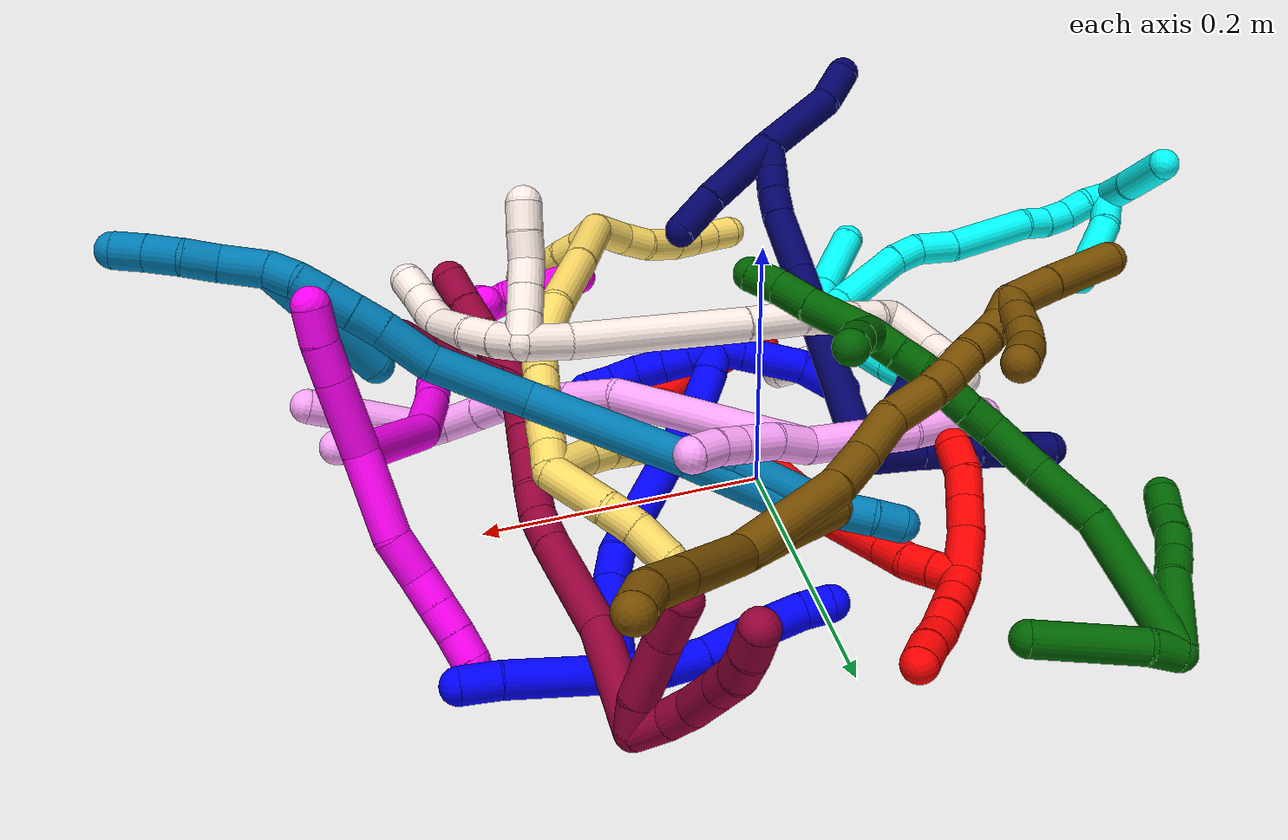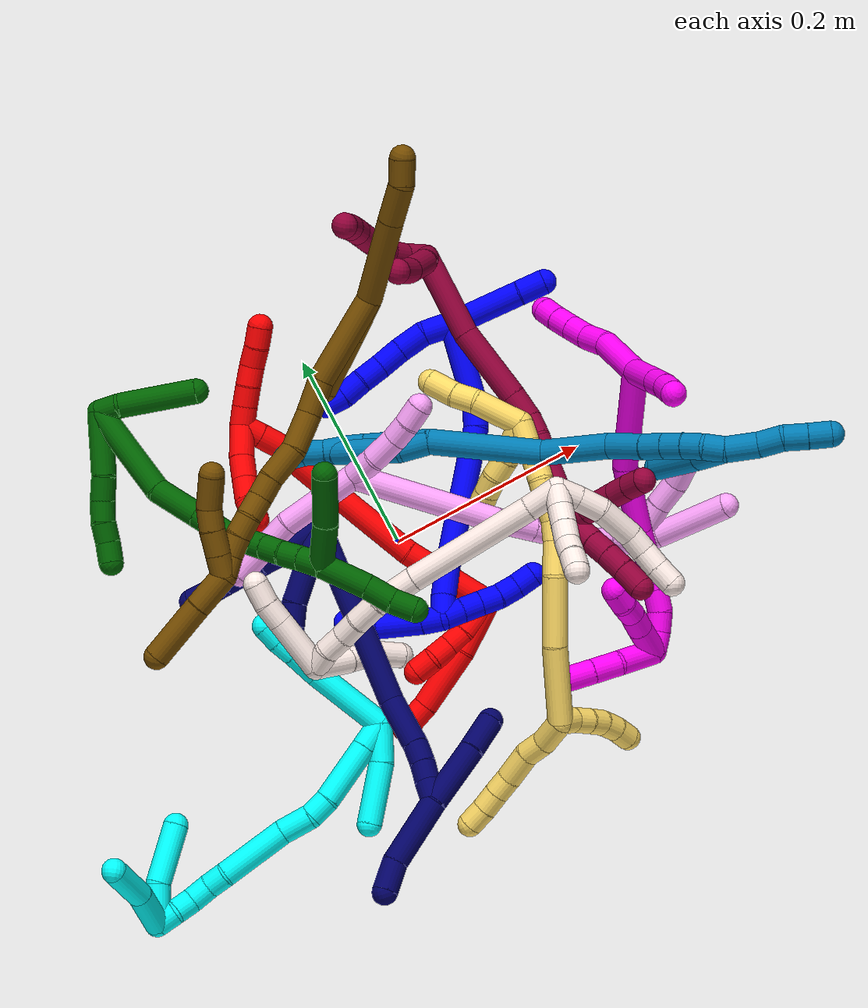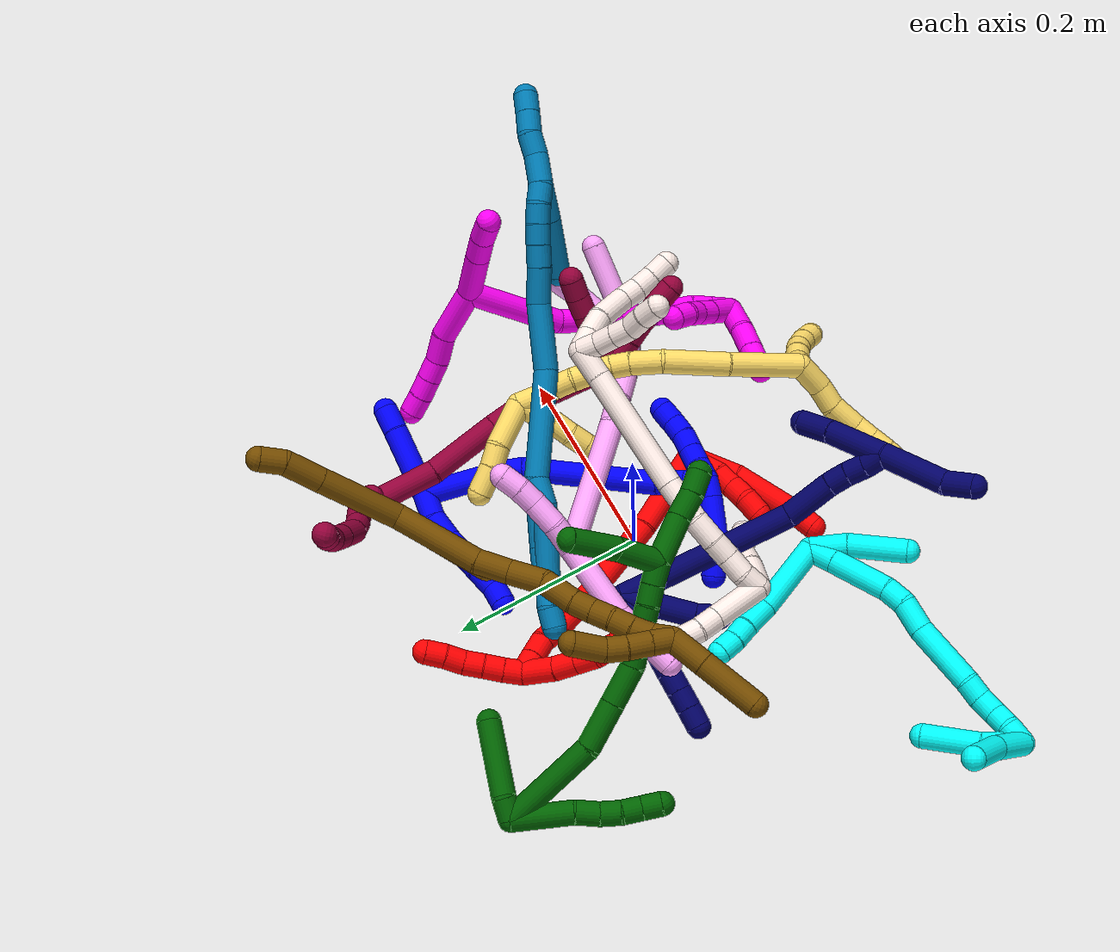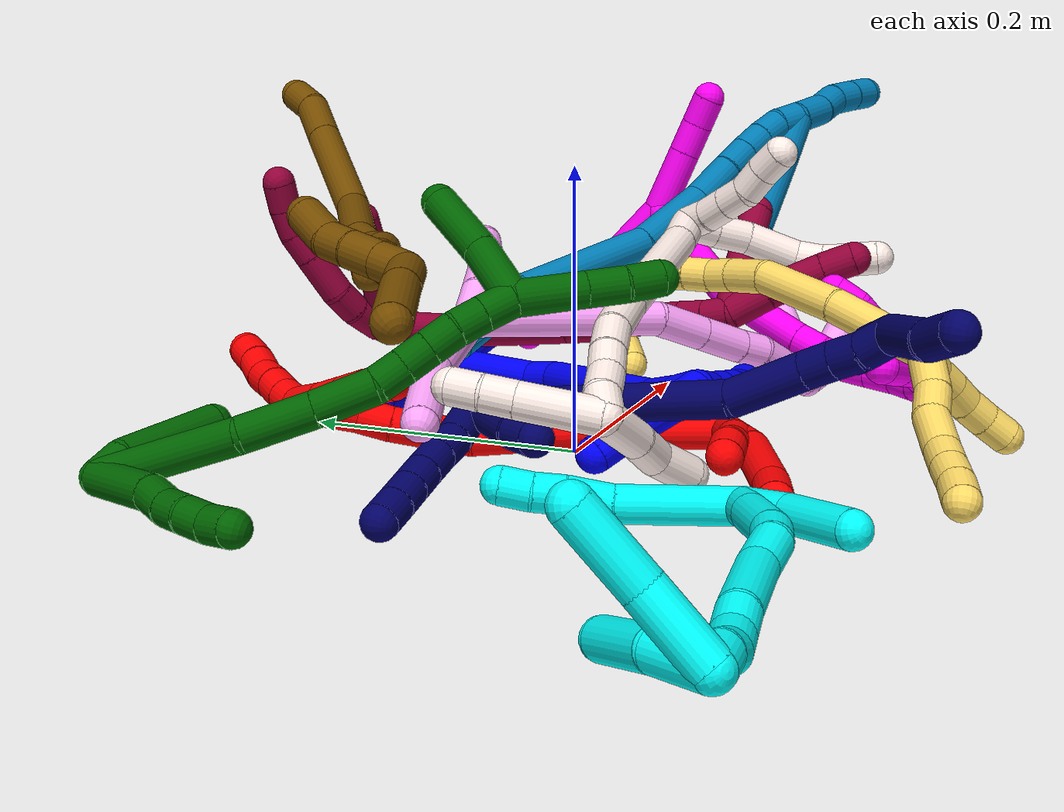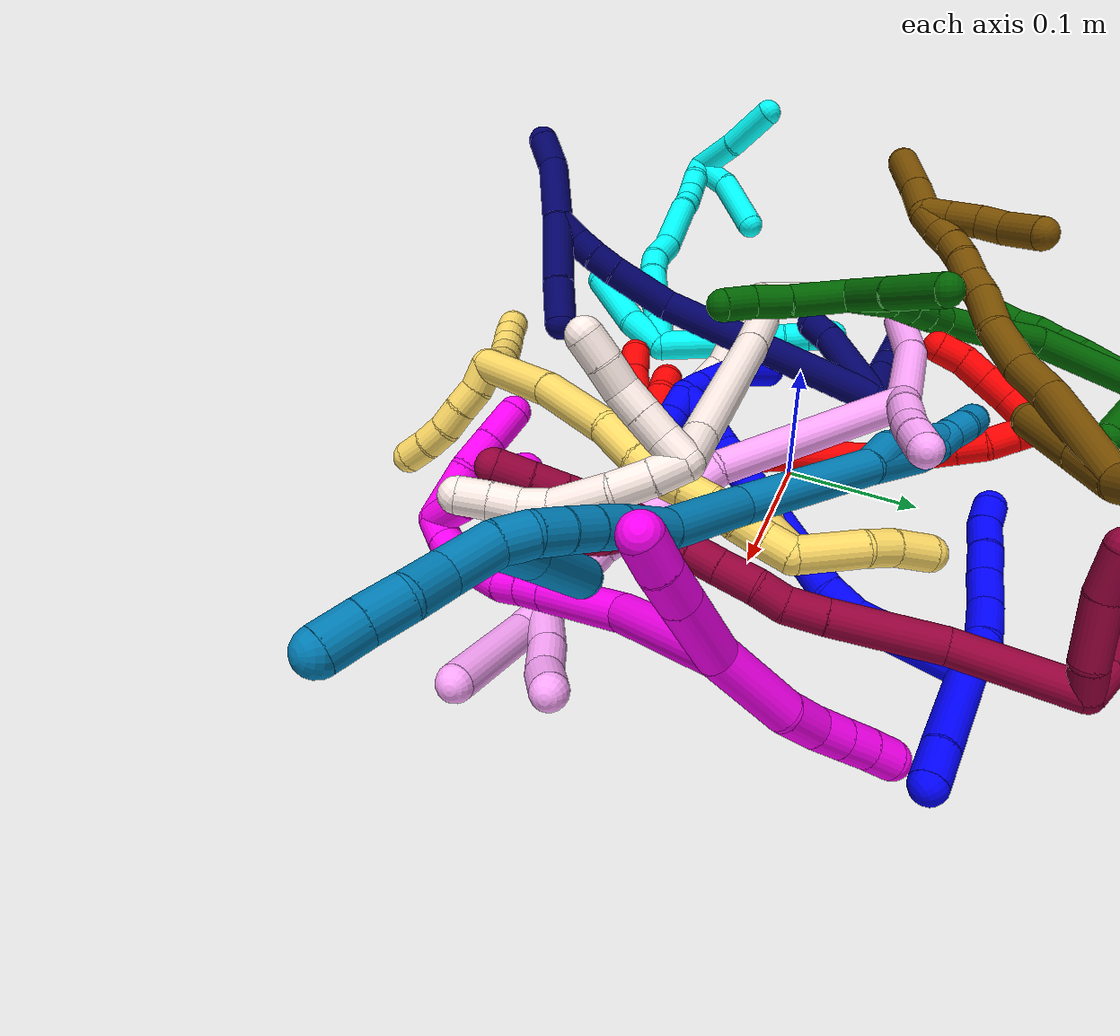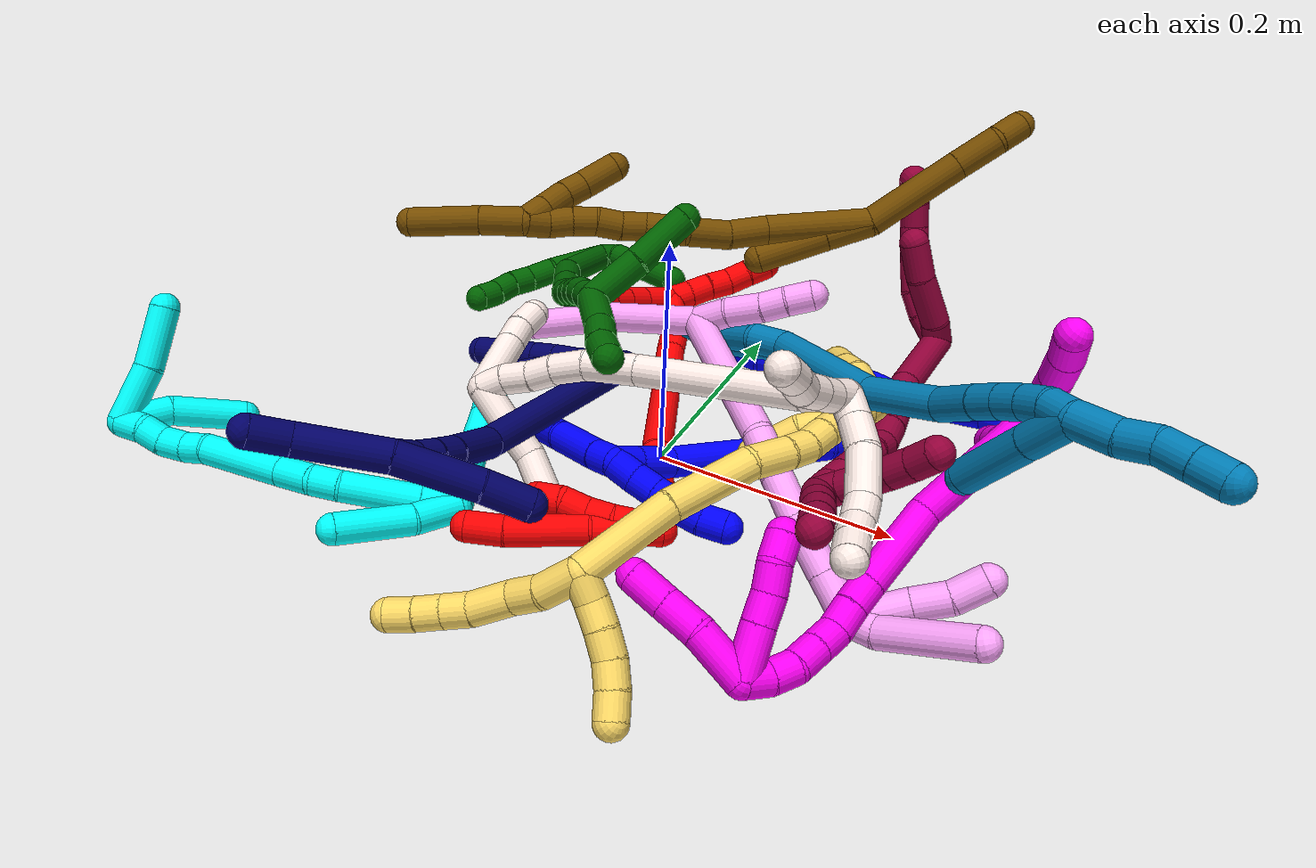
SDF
<sdf version="1.7">
 <world name="default">
  <plugin name="TubeGeneratorPlugin" filename="libtube_generator_plugin.so"/>
  <model name="photoneo_s_sensor">
   <static>1</static>
   <pose>0 0 2 1.57079 1.57079 3.14159</pose>
   <link name="link">
    <inertial><mass>0.1</mass></inertial>
    <sensor name="sensor" type="depth">
     <update_rate>30</update_rate>
     <camera>
      <horizontal_fov>1.22</horizontal_fov>
      <image><width>1920</width><height>1200</height><format>B8G8R8</format></image>
      <clip><near>0.1</near><far>4</far></clip>
      <depth_camera><output>points</output></depth_camera>
     </camera>
     <plugin name="camera_plugin" filename="libgazebo_ros_depth_camera.so">
      <baseline>0.2</baseline>
      <alwaysOn>1</alwaysOn>
      <updateRate>0.0</updateRate>
      <cameraName>camera_ir</cameraName>
      <imageTopicName>/camera/color/image_raw</imageTopicName>
      <cameraInfoTopicName>/camera/color/camera_info</cameraInfoTopicName>
      <depthImageTopicName>/camera/depth/image_raw</depthImageTopicName>
      <depthImageCameraInfoTopicName>/camera/depth/camera_info</depthImageCameraInfoTopicName>
      <pointCloudTopicName>/camera/depth/points</pointCloudTopicName>
      <frameName>fr_optical</frameName>
      <pointCloudCutoff>0.1</pointCloudCutoff>
      <pointCloudCutoffMax>2.0</pointCloudCutoffMax>
      <distortionK1>0</distortionK1>
      <distortionK2>0</distortionK2>
      <distortionK3>0</distortionK3>
      <distortionT1>0</distortionT1>
      <distortionT2>0</distortionT2>
      <CxPrime>0</CxPrime>
      <Cx>0</Cx>
      <Cy>0</Cy>
      <focalLength>0</focalLength>
      <hackBaseline>0</hackBaseline>
     </plugin>
    </sensor>
   </link>
  </model>
  <gravity>0 0 -9.8</gravity>
  <magnetic_field>6e-06 2.3e-05 -4.2e-05</magnetic_field>
  <atmosphere type="adiabatic"/>
  <physics name="default_physics" default="0" type="ode">
   <max_step_size>0.003</max_step_size>
   <real_time_factor>1</real_time_factor>
   <real_time_update_rate>1000</real_time_update_rate>
   <max_contacts>10000</max_contacts>
   <ode>
    <solver>
     <type>quick</type>
     <iters>100</iters>
     <sor>1.3</sor>
     <use_dynamic_moi_rescaling>0</use_dynamic_moi_rescaling>
    </solver>
    <constraints>
     <contact_max_correcting_vel>0</contact_max_correcting_vel>
     <contact_surface_layer>0.001</contact_surface_layer>
     <cfm>0</cfm>
     <erp>0.2</erp>
    </constraints>
   </ode>
  </physics>
  <scene><ambient>0.4 0.4 0.4 1</ambient><background>0.7 0.7 0.7 1</background><shadows>0</shadows></scene>
  <audio><device>default</device></audio>
  <spherical_coordinates>
   <surface_model>EARTH_WGS84</surface_model>
   <latitude_deg>0</latitude_deg>
   <longitude_deg>0</longitude_deg>
   <elevation>0</elevation>
   <heading_deg>0</heading_deg>
  </spherical_coordinates>
  <model name="bin">
   <static>1</static>
   <link name="bottom">
    <collision name="collision-bottom">
     <pose>0 0 -0.01 0 -0 0</pose>
     <geometry><box><size>0.8 0.6 0.02</size></box></geometry>
     <surface>
      <friction><ode><mu>100</mu><mu2>100</mu2></ode></friction>
      <contact><collide_bitmask>65535</collide_bitmask></contact>
     </surface>
    </collision>
   </link>
   <link name="west_wall">
    <collision name="collision-west_wall">
     <pose>-0.41 0 0.1 0 -0 0</pose>
     <geometry><box><size>0.02 0.6 0.2</size></box></geometry>
     <surface>
      <friction><ode><mu>100</mu><mu2>100</mu2></ode></friction>
      <contact><collide_bitmask>65535</collide_bitmask></contact>
     </surface>
    </collision>
   </link>
   <link name="east_wall">
    <collision name="collision-east_wall">
     <pose>0.41 0 0.1 0 -0 0</pose>
     <geometry><box><size>0.02 0.6 0.2</size></box></geometry>
     <surface>
      <friction><ode><mu>100</mu><mu2>100</mu2></ode></friction>
      <contact><collide_bitmask>65535</collide_bitmask></contact>
     </surface>
    </collision>
   </link>
   <link name="south_wall">
    <collision name="collision-south_wall">
     <pose>0 -0.31 0.1 0 -0 0</pose>
     <geometry><box><size>0.8 0.02 0.2</size></box></geometry>
     <surface>
      <friction><ode><mu>100</mu><mu2>100</mu2></ode></friction>
      <contact><collide_bitmask>65535</collide_bitmask></contact>
     </surface>
    </collision>
   </link>
   <link name="north_wall">
    <collision name="collision-north_wall">
     <pose>0 0.31 0.1 0 -0 0</pose>
     <geometry><box><size>0.8 0.02 0.2</size></box></geometry>
     <surface>
      <friction><ode><mu>100</mu><mu2>100</mu2></ode></friction>
      <contact><collide_bitmask>65535</collide_bitmask></contact>
     </surface>
    </collision>
   </link>
  </model>
  <model name="1">
   <static>0</static>
   <link name="1">
    <collision name="collision-cylinder-e_1_2_8">
     <pose>-0.004141 -0.004896 0.01321 0.354913 -0.285854 -0.051606</pose>
     <geometry><cylinder><radius>0.0125</radius><length>0.029368</length></cylinder></geometry>
     <surface>
      <friction><ode><mu>1.16</mu><mu2>1.16</mu2><slip1>0</slip1><slip2>0</slip2></ode></friction>
      <contact><ode><kp>1e+06</kp><kd>1</kd><max_vel>0</max_vel><min_depth>0.001</min_depth></ode></contact>
     </surface>
    </collision>
    <visual name="visual-cylinder-e_1_2_8">
     <pose>-0.004141 -0.004896 0.01321 0.354913 -0.285854 -0.051606</pose>
     <geometry><cylinder><radius>0.0125</radius><length>0.029368</length></cylinder></geometry>
     <material><ambient>0 0 1 1</ambient></material>
    </visual>
    <collision name="collision-cylinder-e_2_8_9">
     <pose>-0.014792 -0.017043 0.036836 0.608167 -0.473989 -0.151305</pose>
     <geometry><cylinder><radius>0.0125</radius><length>0.028528</length></cylinder></geometry>
     <surface>
      <friction><ode><mu>1.16</mu><mu2>1.16</mu2><slip1>0</slip1><slip2>0</slip2></ode></friction>
      <contact><ode><kp>1e+06</kp><kd>1</kd><max_vel>0</max_vel><min_depth>0.001</min_depth></ode></contact>
     </surface>
    </collision>
    <visual name="visual-cylinder-e_2_8_9">
     <pose>-0.014792 -0.017043 0.036836 0.608167 -0.473989 -0.151305</pose>
     <geometry><cylinder><radius>0.0125</radius><length>0.028528</length></cylinder></geometry>
     <material><ambient>0 0 1 1</ambient></material>
    </visual>
    <collision name="collision-cylinder-e_3_9_10">
     <pose>-0.025743 -0.032513 0.05612 0.747425 -0.351965 -0.139237</pose>
     <geometry><cylinder><radius>0.0125</radius><length>0.02576</length></cylinder></geometry>
     <surface>
      <friction><ode><mu>1.16</mu><mu2>1.16</mu2><slip1>0</slip1><slip2>0</slip2></ode></friction>
      <contact><ode><kp>1e+06</kp><kd>1</kd><max_vel>0</max_vel><min_depth>0.001</min_depth></ode></contact>
     </surface>
    </collision>
    <visual name="visual-cylinder-e_3_9_10">
     <pose>-0.025743 -0.032513 0.05612 0.747425 -0.351965 -0.139237</pose>
     <geometry><cylinder><radius>0.0125</radius><length>0.02576</length></cylinder></geometry>
     <material><ambient>0 0 1 1</ambient></material>
    </visual>
    <collision name="collision-cylinder-e_4_10_11">
     <pose>-0.033569 -0.048031 0.073289 0.721276 -0.297239 -0.112811</pose>
     <geometry><cylinder><radius>0.0125</radius><length>0.023123</length></cylinder></geometry>
     <surface>
      <friction><ode><mu>1.16</mu><mu2>1.16</mu2><slip1>0</slip1><slip2>0</slip2></ode></friction>
      <contact><ode><kp>1e+06</kp><kd>1</kd><max_vel>0</max_vel><min_depth>0.001</min_depth></ode></contact>
     </surface>
    </collision>
    <visual name="visual-cylinder-e_4_10_11">
     <pose>-0.033569 -0.048031 0.073289 0.721276 -0.297239 -0.112811</pose>
     <geometry><cylinder><radius>0.0125</radius><length>0.023123</length></cylinder></geometry>
     <material><ambient>0 0 1 1</ambient></material>
    </visual>
    <collision name="collision-cylinder-e_5_11_12">
     <pose>-0.041846 -0.062273 0.089373 0.72838 -0.438575 -0.169508</pose>
     <geometry><cylinder><radius>0.0125</radius><length>0.023035</length></cylinder></geometry>
     <surface>
      <friction><ode><mu>1.16</mu><mu2>1.16</mu2><slip1>0</slip1><slip2>0</slip2></ode></friction>
      <contact><ode><kp>1e+06</kp><kd>1</kd><max_vel>0</max_vel><min_depth>0.001</min_depth></ode></contact>
     </surface>
    </collision>
    <visual name="visual-cylinder-e_5_11_12">
     <pose>-0.041846 -0.062273 0.089373 0.72838 -0.438575 -0.169508</pose>
     <geometry><cylinder><radius>0.0125</radius><length>0.023035</length></cylinder></geometry>
     <material><ambient>0 0 1 1</ambient></material>
    </visual>
    <collision name="collision-cylinder-e_6_12_6">
     <pose>-0.049839 -0.073926 0.105523 0.512827 -0.31233 -0.082513</pose>
     <geometry><cylinder><radius>0.0125</radius><length>0.020185</length></cylinder></geometry>
     <surface>
      <friction><ode><mu>1.16</mu><mu2>1.16</mu2><slip1>0</slip1><slip2>0</slip2></ode></friction>
      <contact><ode><kp>1e+06</kp><kd>1</kd><max_vel>0</max_vel><min_depth>0.001</min_depth></ode></contact>
     </surface>
    </collision>
    <visual name="visual-cylinder-e_6_12_6">
     <pose>-0.049839 -0.073926 0.105523 0.512827 -0.31233 -0.082513</pose>
     <geometry><cylinder><radius>0.0125</radius><length>0.020185</length></cylinder></geometry>
     <material><ambient>0 0 1 1</ambient></material>
    </visual>
    <collision name="collision-cylinder-e_1_2_13">
     <pose>0.018049 0.01133 -0.030095 -2.78152 0.511451 -1.92533</pose>
     <geometry><cylinder><radius>0.0125</radius><length>0.073752</length></cylinder></geometry>
     <surface>
      <friction><ode><mu>1.16</mu><mu2>1.16</mu2><slip1>0</slip1><slip2>0</slip2></ode></friction>
      <contact><ode><kp>1e+06</kp><kd>1</kd><max_vel>0</max_vel><min_depth>0.001</min_depth></ode></contact>
     </surface>
    </collision>
    <visual name="visual-cylinder-e_1_2_13">
     <pose>0.018049 0.01133 -0.030095 -2.78152 0.511451 -1.92533</pose>
     <geometry><cylinder><radius>0.0125</radius><length>0.073752</length></cylinder></geometry>
     <material><ambient>0 0 1 1</ambient></material>
    </visual>
    <collision name="collision-cylinder-e_2_13_5">
     <pose>0.041257 0.027538 -0.071227 -2.72546 0.40408 -1.54057</pose>
     <geometry><cylinder><radius>0.0125</radius><length>0.026248</length></cylinder></geometry>
     <surface>
      <friction><ode><mu>1.16</mu><mu2>1.16</mu2><slip1>0</slip1><slip2>0</slip2></ode></friction>
      <contact><ode><kp>1e+06</kp><kd>1</kd><max_vel>0</max_vel><min_depth>0.001</min_depth></ode></contact>
     </surface>
    </collision>
    <visual name="visual-cylinder-e_2_13_5">
     <pose>0.041257 0.027538 -0.071227 -2.72546 0.40408 -1.54057</pose>
     <geometry><cylinder><radius>0.0125</radius><length>0.026248</length></cylinder></geometry>
     <material><ambient>0 0 1 1</ambient></material>
    </visual>
    <collision name="collision-cylinder-e_1_2_14">
     <pose>-0.015669 -0.033498 -0.015317 1.99967 -0.402208 -0.614643</pose>
     <geometry><cylinder><radius>0.0125</radius><length>0.080056</length></cylinder></geometry>
     <surface>
      <friction><ode><mu>1.16</mu><mu2>1.16</mu2><slip1>0</slip1><slip2>0</slip2></ode></friction>
      <contact><ode><kp>1e+06</kp><kd>1</kd><max_vel>0</max_vel><min_depth>0.001</min_depth></ode></contact>
     </surface>
    </collision>
    <visual name="visual-cylinder-e_1_2_14">
     <pose>-0.015669 -0.033498 -0.015317 1.99967 -0.402208 -0.614643</pose>
     <geometry><cylinder><radius>0.0125</radius><length>0.080056</length></cylinder></geometry>
     <material><ambient>0 0 1 1</ambient></material>
    </visual>
    <collision name="collision-cylinder-e_2_14_15">
     <pose>-0.034972 -0.079426 -0.032543 1.72318 -0.281332 -0.327068</pose>
     <geometry><cylinder><radius>0.0125</radius><length>0.026181</length></cylinder></geometry>
     <surface>
      <friction><ode><mu>1.16</mu><mu2>1.16</mu2><slip1>0</slip1><slip2>0</slip2></ode></friction>
      <contact><ode><kp>1e+06</kp><kd>1</kd><max_vel>0</max_vel><min_depth>0.001</min_depth></ode></contact>
     </surface>
    </collision>
    <visual name="visual-cylinder-e_2_14_15">
     <pose>-0.034972 -0.079426 -0.032543 1.72318 -0.281332 -0.327068</pose>
     <geometry><cylinder><radius>0.0125</radius><length>0.026181</length></cylinder></geometry>
     <material><ambient>0 0 1 1</ambient></material>
    </visual>
    <collision name="collision-cylinder-e_3_15_16">
     <pose>-0.063985 -0.157492 -0.027075 1.45888 -0.366835 -0.328653</pose>
     <geometry><cylinder><radius>0.0125</radius><length>0.141514</length></cylinder></geometry>
     <surface>
      <friction><ode><mu>1.16</mu><mu2>1.16</mu2><slip1>0</slip1><slip2>0</slip2></ode></friction>
      <contact><ode><kp>1e+06</kp><kd>1</kd><max_vel>0</max_vel><min_depth>0.001</min_depth></ode></contact>
     </surface>
    </collision>
    <visual name="visual-cylinder-e_3_15_16">
     <pose>-0.063985 -0.157492 -0.027075 1.45888 -0.366835 -0.328653</pose>
     <geometry><cylinder><radius>0.0125</radius><length>0.141514</length></cylinder></geometry>
     <material><ambient>0 0 1 1</ambient></material>
    </visual>
    <collision name="collision-cylinder-e_4_16_17">
     <pose>-0.092308 -0.238166 -0.018782 1.50994 -0.193067 -0.181725</pose>
     <geometry><cylinder><radius>0.0125</radius><length>0.030703</length></cylinder></geometry>
     <surface>
      <friction><ode><mu>1.16</mu><mu2>1.16</mu2><slip1>0</slip1><slip2>0</slip2></ode></friction>
      <contact><ode><kp>1e+06</kp><kd>1</kd><max_vel>0</max_vel><min_depth>0.001</min_depth></ode></contact>
     </surface>
    </collision>
    <visual name="visual-cylinder-e_4_16_17">
     <pose>-0.092308 -0.238166 -0.018782 1.50994 -0.193067 -0.181725</pose>
     <geometry><cylinder><radius>0.0125</radius><length>0.030703</length></cylinder></geometry>
     <material><ambient>0 0 1 1</ambient></material>
    </visual>
    <collision name="collision-cylinder-e_5_17_1">
     <pose>-0.096383 -0.26391 -0.018278 1.60925 -0.105057 -0.109168</pose>
     <geometry><cylinder><radius>0.0125</radius><length>0.021547</length></cylinder></geometry>
     <surface>
      <friction><ode><mu>1.16</mu><mu2>1.16</mu2><slip1>0</slip1><slip2>0</slip2></ode></friction>
      <contact><ode><kp>1e+06</kp><kd>1</kd><max_vel>0</max_vel><min_depth>0.001</min_depth></ode></contact>
     </surface>
    </collision>
    <visual name="visual-cylinder-e_5_17_1">
     <pose>-0.096383 -0.26391 -0.018278 1.60925 -0.105057 -0.109168</pose>
     <geometry><cylinder><radius>0.0125</radius><length>0.021547</length></cylinder></geometry>
     <material><ambient>0 0 1 1</ambient></material>
    </visual>
    <collision name="collision-cylinder-e_1_1_18">
     <pose>-0.101948 -0.275699 -0.009728 0.120262 -0.456731 -0.027983</pose>
     <geometry><cylinder><radius>0.0125</radius><length>0.020115</length></cylinder></geometry>
     <surface>
      <friction><ode><mu>1.16</mu><mu2>1.16</mu2><slip1>0</slip1><slip2>0</slip2></ode></friction>
      <contact><ode><kp>1e+06</kp><kd>1</kd><max_vel>0</max_vel><min_depth>0.001</min_depth></ode></contact>
     </surface>
    </collision>
    <visual name="visual-cylinder-e_1_1_18">
     <pose>-0.101948 -0.275699 -0.009728 0.120262 -0.456731 -0.027983</pose>
     <geometry><cylinder><radius>0.0125</radius><length>0.020115</length></cylinder></geometry>
     <material><ambient>0 0 1 1</ambient></material>
    </visual>
    <collision name="collision-cylinder-e_2_18_19">
     <pose>-0.115433 -0.277453 0.02024 0.031904 -0.406561 -0.006577</pose>
     <geometry><cylinder><radius>0.0125</radius><length>0.045767</length></cylinder></geometry>
     <surface>
      <friction><ode><mu>1.16</mu><mu2>1.16</mu2><slip1>0</slip1><slip2>0</slip2></ode></friction>
      <contact><ode><kp>1e+06</kp><kd>1</kd><max_vel>0</max_vel><min_depth>0.001</min_depth></ode></contact>
     </surface>
    </collision>
    <visual name="visual-cylinder-e_2_18_19">
     <pose>-0.115433 -0.277453 0.02024 0.031904 -0.406561 -0.006577</pose>
     <geometry><cylinder><radius>0.0125</radius><length>0.045767</length></cylinder></geometry>
     <material><ambient>0 0 1 1</ambient></material>
    </visual>
    <collision name="collision-cylinder-e_3_19_4">
     <pose>-0.132311 -0.273828 0.055783 -0.287298 -0.476738 0.070265</pose>
     <geometry><cylinder><radius>0.0125</radius><length>0.034119</length></cylinder></geometry>
     <surface>
      <friction><ode><mu>1.16</mu><mu2>1.16</mu2><slip1>0</slip1><slip2>0</slip2></ode></friction>
      <contact><ode><kp>1e+06</kp><kd>1</kd><max_vel>0</max_vel><min_depth>0.001</min_depth></ode></contact>
     </surface>
    </collision>
    <visual name="visual-cylinder-e_3_19_4">
     <pose>-0.132311 -0.273828 0.055783 -0.287298 -0.476738 0.070265</pose>
     <geometry><cylinder><radius>0.0125</radius><length>0.034119</length></cylinder></geometry>
     <material><ambient>0 0 1 1</ambient></material>
    </visual>
    <collision name="collision-cylinder-e_1_1_20">
     <pose>-0.096905 -0.269808 -0.027437 -2.63899 0.060858 -0.236025</pose>
     <geometry><cylinder><radius>0.0125</radius><length>0.02</length></cylinder></geometry>
     <surface>
      <friction><ode><mu>1.16</mu><mu2>1.16</mu2><slip1>0</slip1><slip2>0</slip2></ode></friction>
      <contact><ode><kp>1e+06</kp><kd>1</kd><max_vel>0</max_vel><min_depth>0.001</min_depth></ode></contact>
     </surface>
    </collision>
    <visual name="visual-cylinder-e_1_1_20">
     <pose>-0.096905 -0.269808 -0.027437 -2.63899 0.060858 -0.236025</pose>
     <geometry><cylinder><radius>0.0125</radius><length>0.02</length></cylinder></geometry>
     <material><ambient>0 0 1 1</ambient></material>
    </visual>
    <collision name="collision-cylinder-e_2_20_21">
     <pose>-0.094801 -0.260728 -0.045101 -2.69484 0.150065 -0.639147</pose>
     <geometry><cylinder><radius>0.0125</radius><length>0.02</length></cylinder></geometry>
     <surface>
      <friction><ode><mu>1.16</mu><mu2>1.16</mu2><slip1>0</slip1><slip2>0</slip2></ode></friction>
      <contact><ode><kp>1e+06</kp><kd>1</kd><max_vel>0</max_vel><min_depth>0.001</min_depth></ode></contact>
     </surface>
    </collision>
    <visual name="visual-cylinder-e_2_20_21">
     <pose>-0.094801 -0.260728 -0.045101 -2.69484 0.150065 -0.639147</pose>
     <geometry><cylinder><radius>0.0125</radius><length>0.02</length></cylinder></geometry>
     <material><ambient>0 0 1 1</ambient></material>
    </visual>
    <collision name="collision-cylinder-e_3_21_22">
     <pose>-0.091785 -0.252274 -0.062973 -2.70464 0.152768 -0.663915</pose>
     <geometry><cylinder><radius>0.0125</radius><length>0.02</length></cylinder></geometry>
     <surface>
      <friction><ode><mu>1.16</mu><mu2>1.16</mu2><slip1>0</slip1><slip2>0</slip2></ode></friction>
      <contact><ode><kp>1e+06</kp><kd>1</kd><max_vel>0</max_vel><min_depth>0.001</min_depth></ode></contact>
     </surface>
    </collision>
    <visual name="visual-cylinder-e_3_21_22">
     <pose>-0.091785 -0.252274 -0.062973 -2.70464 0.152768 -0.663915</pose>
     <geometry><cylinder><radius>0.0125</radius><length>0.02</length></cylinder></geometry>
     <material><ambient>0 0 1 1</ambient></material>
    </visual>
    <collision name="collision-cylinder-e_4_22_23">
     <pose>-0.088408 -0.242485 -0.079999 -2.53448 0.186569 -0.580483</pose>
     <geometry><cylinder><radius>0.0125</radius><length>0.02</length></cylinder></geometry>
     <surface>
      <friction><ode><mu>1.16</mu><mu2>1.16</mu2><slip1>0</slip1><slip2>0</slip2></ode></friction>
      <contact><ode><kp>1e+06</kp><kd>1</kd><max_vel>0</max_vel><min_depth>0.001</min_depth></ode></contact>
     </surface>
    </collision>
    <visual name="visual-cylinder-e_4_22_23">
     <pose>-0.088408 -0.242485 -0.079999 -2.53448 0.186569 -0.580483</pose>
     <geometry><cylinder><radius>0.0125</radius><length>0.02</length></cylinder></geometry>
     <material><ambient>0 0 1 1</ambient></material>
    </visual>
    <collision name="collision-cylinder-e_5_23_3">
     <pose>-0.082898 -0.231315 -0.095531 -2.50084 0.374193 -1.03696</pose>
     <geometry><cylinder><radius>0.0125</radius><length>0.02</length></cylinder></geometry>
     <surface>
      <friction><ode><mu>1.16</mu><mu2>1.16</mu2><slip1>0</slip1><slip2>0</slip2></ode></friction>
      <contact><ode><kp>1e+06</kp><kd>1</kd><max_vel>0</max_vel><min_depth>0.001</min_depth></ode></contact>
     </surface>
    </collision>
    <visual name="visual-cylinder-e_5_23_3">
     <pose>-0.082898 -0.231315 -0.095531 -2.50084 0.374193 -1.03696</pose>
     <geometry><cylinder><radius>0.0125</radius><length>0.02</length></cylinder></geometry>
     <material><ambient>0 0 1 1</ambient></material>
    </visual>
    <collision name="collision-sphere-3">
     <pose>-0.079243 -0.225751 -0.102993 0 -0 0</pose>
     <geometry><sphere><radius>0.0125</radius></sphere></geometry>
     <surface>
      <friction><ode><mu>1.16</mu><mu2>1.16</mu2><slip1>0</slip1><slip2>0</slip2></ode></friction>
      <contact><ode><kp>1e+06</kp><kd>1</kd><max_vel>0</max_vel><min_depth>0.001</min_depth></ode></contact>
     </surface>
    </collision>
    <visual name="visual-sphere-3">
     <pose>-0.079243 -0.225751 -0.102993 0 -0 0</pose>
     <geometry><sphere><radius>0.0125</radius></sphere></geometry>
     <material><ambient>0 0 1 1</ambient></material>
    </visual>
    <collision name="collision-sphere-23">
     <pose>-0.086553 -0.236879 -0.088069 0 -0 0</pose>
     <geometry><sphere><radius>0.0125</radius></sphere></geometry>
     <surface>
      <friction><ode><mu>1.16</mu><mu2>1.16</mu2><slip1>0</slip1><slip2>0</slip2></ode></friction>
      <contact><ode><kp>1e+06</kp><kd>1</kd><max_vel>0</max_vel><min_depth>0.001</min_depth></ode></contact>
     </surface>
    </collision>
    <visual name="visual-sphere-23">
     <pose>-0.086553 -0.236879 -0.088069 0 -0 0</pose>
     <geometry><sphere><radius>0.0125</radius></sphere></geometry>
     <material><ambient>0 0 1 1</ambient></material>
    </visual>
    <collision name="collision-sphere-22">
     <pose>-0.090263 -0.248091 -0.071928 0 -0 0</pose>
     <geometry><sphere><radius>0.0125</radius></sphere></geometry>
     <surface>
      <friction><ode><mu>1.16</mu><mu2>1.16</mu2><slip1>0</slip1><slip2>0</slip2></ode></friction>
      <contact><ode><kp>1e+06</kp><kd>1</kd><max_vel>0</max_vel><min_depth>0.001</min_depth></ode></contact>
     </surface>
    </collision>
    <visual name="visual-sphere-22">
     <pose>-0.090263 -0.248091 -0.071928 0 -0 0</pose>
     <geometry><sphere><radius>0.0125</radius></sphere></geometry>
     <material><ambient>0 0 1 1</ambient></material>
    </visual>
    <collision name="collision-sphere-21">
     <pose>-0.093306 -0.256456 -0.054018 0 -0 0</pose>
     <geometry><sphere><radius>0.0125</radius></sphere></geometry>
     <surface>
      <friction><ode><mu>1.16</mu><mu2>1.16</mu2><slip1>0</slip1><slip2>0</slip2></ode></friction>
      <contact><ode><kp>1e+06</kp><kd>1</kd><max_vel>0</max_vel><min_depth>0.001</min_depth></ode></contact>
     </surface>
    </collision>
    <visual name="visual-sphere-21">
     <pose>-0.093306 -0.256456 -0.054018 0 -0 0</pose>
     <geometry><sphere><radius>0.0125</radius></sphere></geometry>
     <material><ambient>0 0 1 1</ambient></material>
    </visual>
    <collision name="collision-sphere-20">
     <pose>-0.096296 -0.265 -0.036184 0 -0 0</pose>
     <geometry><sphere><radius>0.0125</radius></sphere></geometry>
     <surface>
      <friction><ode><mu>1.16</mu><mu2>1.16</mu2><slip1>0</slip1><slip2>0</slip2></ode></friction>
      <contact><ode><kp>1e+06</kp><kd>1</kd><max_vel>0</max_vel><min_depth>0.001</min_depth></ode></contact>
     </surface>
    </collision>
    <visual name="visual-sphere-20">
     <pose>-0.096296 -0.265 -0.036184 0 -0 0</pose>
     <geometry><sphere><radius>0.0125</radius></sphere></geometry>
     <material><ambient>0 0 1 1</ambient></material>
    </visual>
    <collision name="collision-sphere-4">
     <pose>-0.140139 -0.269533 0.070319 0 -0 0</pose>
     <geometry><sphere><radius>0.0125</radius></sphere></geometry>
     <surface>
      <friction><ode><mu>1.16</mu><mu2>1.16</mu2><slip1>0</slip1><slip2>0</slip2></ode></friction>
      <contact><ode><kp>1e+06</kp><kd>1</kd><max_vel>0</max_vel><min_depth>0.001</min_depth></ode></contact>
     </surface>
    </collision>
    <visual name="visual-sphere-4">
     <pose>-0.140139 -0.269533 0.070319 0 -0 0</pose>
     <geometry><sphere><radius>0.0125</radius></sphere></geometry>
     <material><ambient>0 0 1 1</ambient></material>
    </visual>
    <collision name="collision-sphere-12">
     <pose>-0.046737 -0.069214 0.097154 0 -0 0</pose>
     <geometry><sphere><radius>0.0125</radius></sphere></geometry>
     <surface>
      <friction><ode><mu>1.16</mu><mu2>1.16</mu2><slip1>0</slip1><slip2>0</slip2></ode></friction>
      <contact><ode><kp>1e+06</kp><kd>1</kd><max_vel>0</max_vel><min_depth>0.001</min_depth></ode></contact>
     </surface>
    </collision>
    <visual name="visual-sphere-12">
     <pose>-0.046737 -0.069214 0.097154 0 -0 0</pose>
     <geometry><sphere><radius>0.0125</radius></sphere></geometry>
     <material><ambient>0 0 1 1</ambient></material>
    </visual>
    <collision name="collision-sphere-11">
     <pose>-0.036955 -0.055331 0.081591 0 -0 0</pose>
     <geometry><sphere><radius>0.0125</radius></sphere></geometry>
     <surface>
      <friction><ode><mu>1.16</mu><mu2>1.16</mu2><slip1>0</slip1><slip2>0</slip2></ode></friction>
      <contact><ode><kp>1e+06</kp><kd>1</kd><max_vel>0</max_vel><min_depth>0.001</min_depth></ode></contact>
     </surface>
    </collision>
    <visual name="visual-sphere-11">
     <pose>-0.036955 -0.055331 0.081591 0 -0 0</pose>
     <geometry><sphere><radius>0.0125</radius></sphere></geometry>
     <material><ambient>0 0 1 1</ambient></material>
    </visual>
    <collision name="collision-sphere-10">
     <pose>-0.030183 -0.040731 0.064987 0 -0 0</pose>
     <geometry><sphere><radius>0.0125</radius></sphere></geometry>
     <surface>
      <friction><ode><mu>1.16</mu><mu2>1.16</mu2><slip1>0</slip1><slip2>0</slip2></ode></friction>
      <contact><ode><kp>1e+06</kp><kd>1</kd><max_vel>0</max_vel><min_depth>0.001</min_depth></ode></contact>
     </surface>
    </collision>
    <visual name="visual-sphere-10">
     <pose>-0.030183 -0.040731 0.064987 0 -0 0</pose>
     <geometry><sphere><radius>0.0125</radius></sphere></geometry>
     <material><ambient>0 0 1 1</ambient></material>
    </visual>
    <collision name="collision-sphere-9">
     <pose>-0.021302 -0.024294 0.047252 0 -0 0</pose>
     <geometry><sphere><radius>0.0125</radius></sphere></geometry>
     <surface>
      <friction><ode><mu>1.16</mu><mu2>1.16</mu2><slip1>0</slip1><slip2>0</slip2></ode></friction>
      <contact><ode><kp>1e+06</kp><kd>1</kd><max_vel>0</max_vel><min_depth>0.001</min_depth></ode></contact>
     </surface>
    </collision>
    <visual name="visual-sphere-9">
     <pose>-0.021302 -0.024294 0.047252 0 -0 0</pose>
     <geometry><sphere><radius>0.0125</radius></sphere></geometry>
     <material><ambient>0 0 1 1</ambient></material>
    </visual>
    <collision name="collision-sphere-2">
     <geometry><sphere><radius>0.0125</radius></sphere></geometry>
     <surface>
      <friction><ode><mu>1.16</mu><mu2>1.16</mu2><slip1>0</slip1><slip2>0</slip2></ode></friction>
      <contact><ode><kp>1e+06</kp><kd>1</kd><max_vel>0</max_vel><min_depth>0.001</min_depth></ode></contact>
     </surface>
    </collision>
    <visual name="visual-sphere-2">
     <geometry><sphere><radius>0.0125</radius></sphere></geometry>
     <material><ambient>0 0 1 1</ambient></material>
    </visual>
    <collision name="collision-sphere-19">
     <pose>-0.124482 -0.278123 0.041248 0 -0 0</pose>
     <geometry><sphere><radius>0.0125</radius></sphere></geometry>
     <surface>
      <friction><ode><mu>1.16</mu><mu2>1.16</mu2><slip1>0</slip1><slip2>0</slip2></ode></friction>
      <contact><ode><kp>1e+06</kp><kd>1</kd><max_vel>0</max_vel><min_depth>0.001</min_depth></ode></contact>
     </surface>
    </collision>
    <visual name="visual-sphere-19">
     <pose>-0.124482 -0.278123 0.041248 0 -0 0</pose>
     <geometry><sphere><radius>0.0125</radius></sphere></geometry>
     <material><ambient>0 0 1 1</ambient></material>
    </visual>
    <collision name="collision-sphere-8">
     <pose>-0.008281 -0.009792 0.026421 0 -0 0</pose>
     <geometry><sphere><radius>0.0125</radius></sphere></geometry>
     <surface>
      <friction><ode><mu>1.16</mu><mu2>1.16</mu2><slip1>0</slip1><slip2>0</slip2></ode></friction>
      <contact><ode><kp>1e+06</kp><kd>1</kd><max_vel>0</max_vel><min_depth>0.001</min_depth></ode></contact>
     </surface>
    </collision>
    <visual name="visual-sphere-8">
     <pose>-0.008281 -0.009792 0.026421 0 -0 0</pose>
     <geometry><sphere><radius>0.0125</radius></sphere></geometry>
     <material><ambient>0 0 1 1</ambient></material>
    </visual>
    <collision name="collision-sphere-6">
     <pose>-0.05294 -0.078638 0.113892 0 -0 0</pose>
     <geometry><sphere><radius>0.0125</radius></sphere></geometry>
     <surface>
      <friction><ode><mu>1.16</mu><mu2>1.16</mu2><slip1>0</slip1><slip2>0</slip2></ode></friction>
      <contact><ode><kp>1e+06</kp><kd>1</kd><max_vel>0</max_vel><min_depth>0.001</min_depth></ode></contact>
     </surface>
    </collision>
    <visual name="visual-sphere-6">
     <pose>-0.05294 -0.078638 0.113892 0 -0 0</pose>
     <geometry><sphere><radius>0.0125</radius></sphere></geometry>
     <material><ambient>0 0 1 1</ambient></material>
    </visual>
    <collision name="collision-sphere-13">
     <pose>0.036097 0.02266 -0.06019 0 -0 0</pose>
     <geometry><sphere><radius>0.0125</radius></sphere></geometry>
     <surface>
      <friction><ode><mu>1.16</mu><mu2>1.16</mu2><slip1>0</slip1><slip2>0</slip2></ode></friction>
      <contact><ode><kp>1e+06</kp><kd>1</kd><max_vel>0</max_vel><min_depth>0.001</min_depth></ode></contact>
     </surface>
    </collision>
    <visual name="visual-sphere-13">
     <pose>0.036097 0.02266 -0.06019 0 -0 0</pose>
     <geometry><sphere><radius>0.0125</radius></sphere></geometry>
     <material><ambient>0 0 1 1</ambient></material>
    </visual>
    <collision name="collision-sphere-5">
     <pose>0.046417 0.032416 -0.082265 0 -0 0</pose>
     <geometry><sphere><radius>0.0125</radius></sphere></geometry>
     <surface>
      <friction><ode><mu>1.16</mu><mu2>1.16</mu2><slip1>0</slip1><slip2>0</slip2></ode></friction>
      <contact><ode><kp>1e+06</kp><kd>1</kd><max_vel>0</max_vel><min_depth>0.001</min_depth></ode></contact>
     </surface>
    </collision>
    <visual name="visual-sphere-5">
     <pose>0.046417 0.032416 -0.082265 0 -0 0</pose>
     <geometry><sphere><radius>0.0125</radius></sphere></geometry>
     <material><ambient>0 0 1 1</ambient></material>
    </visual>
    <collision name="collision-sphere-14">
     <pose>-0.031338 -0.066996 -0.030634 0 -0 0</pose>
     <geometry><sphere><radius>0.0125</radius></sphere></geometry>
     <surface>
      <friction><ode><mu>1.16</mu><mu2>1.16</mu2><slip1>0</slip1><slip2>0</slip2></ode></friction>
      <contact><ode><kp>1e+06</kp><kd>1</kd><max_vel>0</max_vel><min_depth>0.001</min_depth></ode></contact>
     </surface>
    </collision>
    <visual name="visual-sphere-14">
     <pose>-0.031338 -0.066996 -0.030634 0 -0 0</pose>
     <geometry><sphere><radius>0.0125</radius></sphere></geometry>
     <material><ambient>0 0 1 1</ambient></material>
    </visual>
    <collision name="collision-sphere-15">
     <pose>-0.038607 -0.091856 -0.034452 0 -0 0</pose>
     <geometry><sphere><radius>0.0125</radius></sphere></geometry>
     <surface>
      <friction><ode><mu>1.16</mu><mu2>1.16</mu2><slip1>0</slip1><slip2>0</slip2></ode></friction>
      <contact><ode><kp>1e+06</kp><kd>1</kd><max_vel>0</max_vel><min_depth>0.001</min_depth></ode></contact>
     </surface>
    </collision>
    <visual name="visual-sphere-15">
     <pose>-0.038607 -0.091856 -0.034452 0 -0 0</pose>
     <geometry><sphere><radius>0.0125</radius></sphere></geometry>
     <material><ambient>0 0 1 1</ambient></material>
    </visual>
    <collision name="collision-sphere-16">
     <pose>-0.089362 -0.223128 -0.019699 0 -0 0</pose>
     <geometry><sphere><radius>0.0125</radius></sphere></geometry>
     <surface>
      <friction><ode><mu>1.16</mu><mu2>1.16</mu2><slip1>0</slip1><slip2>0</slip2></ode></friction>
      <contact><ode><kp>1e+06</kp><kd>1</kd><max_vel>0</max_vel><min_depth>0.001</min_depth></ode></contact>
     </surface>
    </collision>
    <visual name="visual-sphere-16">
     <pose>-0.089362 -0.223128 -0.019699 0 -0 0</pose>
     <geometry><sphere><radius>0.0125</radius></sphere></geometry>
     <material><ambient>0 0 1 1</ambient></material>
    </visual>
    <collision name="collision-sphere-17">
     <pose>-0.095253 -0.253205 -0.017866 0 -0 0</pose>
     <geometry><sphere><radius>0.0125</radius></sphere></geometry>
     <surface>
      <friction><ode><mu>1.16</mu><mu2>1.16</mu2><slip1>0</slip1><slip2>0</slip2></ode></friction>
      <contact><ode><kp>1e+06</kp><kd>1</kd><max_vel>0</max_vel><min_depth>0.001</min_depth></ode></contact>
     </surface>
    </collision>
    <visual name="visual-sphere-17">
     <pose>-0.095253 -0.253205 -0.017866 0 -0 0</pose>
     <geometry><sphere><radius>0.0125</radius></sphere></geometry>
     <material><ambient>0 0 1 1</ambient></material>
    </visual>
    <collision name="collision-sphere-1">
     <pose>-0.097513 -0.274616 -0.01869 0 -0 0</pose>
     <geometry><sphere><radius>0.0125</radius></sphere></geometry>
     <surface>
      <friction><ode><mu>1.16</mu><mu2>1.16</mu2><slip1>0</slip1><slip2>0</slip2></ode></friction>
      <contact><ode><kp>1e+06</kp><kd>1</kd><max_vel>0</max_vel><min_depth>0.001</min_depth></ode></contact>
     </surface>
    </collision>
    <visual name="visual-sphere-1">
     <pose>-0.097513 -0.274616 -0.01869 0 -0 0</pose>
     <geometry><sphere><radius>0.0125</radius></sphere></geometry>
     <material><ambient>0 0 1 1</ambient></material>
    </visual>
    <collision name="collision-sphere-18">
     <pose>-0.106384 -0.276782 -0.000767 0 -0 0</pose>
     <geometry><sphere><radius>0.0125</radius></sphere></geometry>
     <surface>
      <friction><ode><mu>1.16</mu><mu2>1.16</mu2><slip1>0</slip1><slip2>0</slip2></ode></friction>
      <contact><ode><kp>1e+06</kp><kd>1</kd><max_vel>0</max_vel><min_depth>0.001</min_depth></ode></contact>
     </surface>
    </collision>
    <visual name="visual-sphere-18">
     <pose>-0.106384 -0.276782 -0.000767 0 -0 0</pose>
     <geometry><sphere><radius>0.0125</radius></sphere></geometry>
     <material><ambient>0 0 1 1</ambient></material>
    </visual>
    <inertial>
     <pose>-0.051491 -0.128949 -0.007718 0 -0 0</pose>
     <mass>0.75</mass>
     <inertia>
      <ixx>0.000131</ixx>
      <ixy>0</ixy>
      <ixz>0</ixz>
      <iyy>-6.9e-05</iyy>
      <iyz>0</iyz>
      <izz>0.00036</izz>
     </inertia>
    </inertial>
   </link>
   <pose>0.147472 0.164269 0.012859 -1.2757 -1.05709 0.706935</pose>
  </model>
  <model name="2">
   <static>0</static>
   <link name="2">
    <collision name="collision-cylinder-e_1_2_8">
     <pose>0.005006 -0.000635 0.026952 0.023548 0.183581 0.002168</pose>
     <geometry><cylinder><radius>0.0125</radius><length>0.054841</length></cylinder></geometry>
     <surface>
      <friction><ode><mu>1.16</mu><mu2>1.16</mu2><slip1>0</slip1><slip2>0</slip2></ode></friction>
      <contact><ode><kp>1e+06</kp><kd>1</kd><max_vel>0</max_vel><min_depth>0.001</min_depth></ode></contact>
     </surface>
    </collision>
    <visual name="visual-cylinder-e_1_2_8">
     <pose>0.005006 -0.000635 0.026952 0.023548 0.183581 0.002168</pose>
     <geometry><cylinder><radius>0.0125</radius><length>0.054841</length></cylinder></geometry>
     <material><ambient>1 0 0 1</ambient></material>
    </visual>
    <collision name="collision-cylinder-e_2_8_9">
     <pose>0.010612 0.001028 0.086255 -0.070917 0.018532 -0.000657</pose>
     <geometry><cylinder><radius>0.0125</radius><length>0.064875</length></cylinder></geometry>
     <surface>
      <friction><ode><mu>1.16</mu><mu2>1.16</mu2><slip1>0</slip1><slip2>0</slip2></ode></friction>
      <contact><ode><kp>1e+06</kp><kd>1</kd><max_vel>0</max_vel><min_depth>0.001</min_depth></ode></contact>
     </surface>
    </collision>
    <visual name="visual-cylinder-e_2_8_9">
     <pose>0.010612 0.001028 0.086255 -0.070917 0.018532 -0.000657</pose>
     <geometry><cylinder><radius>0.0125</radius><length>0.064875</length></cylinder></geometry>
     <material><ambient>1 0 0 1</ambient></material>
    </visual>
    <collision name="collision-cylinder-e_3_9_6">
     <pose>0.01199 0.006455 0.1334 -0.208388 0.051336 -0.005369</pose>
     <geometry><cylinder><radius>0.0125</radius><length>0.030284</length></cylinder></geometry>
     <surface>
      <friction><ode><mu>1.16</mu><mu2>1.16</mu2><slip1>0</slip1><slip2>0</slip2></ode></friction>
      <contact><ode><kp>1e+06</kp><kd>1</kd><max_vel>0</max_vel><min_depth>0.001</min_depth></ode></contact>
     </surface>
    </collision>
    <visual name="visual-cylinder-e_3_9_6">
     <pose>0.01199 0.006455 0.1334 -0.208388 0.051336 -0.005369</pose>
     <geometry><cylinder><radius>0.0125</radius><length>0.030284</length></cylinder></geometry>
     <material><ambient>1 0 0 1</ambient></material>
    </visual>
    <collision name="collision-cylinder-e_1_2_10">
     <pose>0.004845 0.003179 0.018459 -0.170541 0.253125 -0.021752</pose>
     <geometry><cylinder><radius>0.0125</radius><length>0.038693</length></cylinder></geometry>
     <surface>
      <friction><ode><mu>1.16</mu><mu2>1.16</mu2><slip1>0</slip1><slip2>0</slip2></ode></friction>
      <contact><ode><kp>1e+06</kp><kd>1</kd><max_vel>0</max_vel><min_depth>0.001</min_depth></ode></contact>
     </surface>
    </collision>
    <visual name="visual-cylinder-e_1_2_10">
     <pose>0.004845 0.003179 0.018459 -0.170541 0.253125 -0.021752</pose>
     <geometry><cylinder><radius>0.0125</radius><length>0.038693</length></cylinder></geometry>
     <material><ambient>1 0 0 1</ambient></material>
    </visual>
    <collision name="collision-cylinder-e_2_10_11">
     <pose>0.010783 0.009981 0.046183 -0.372785 0.109461 -0.020662</pose>
     <geometry><cylinder><radius>0.0125</radius><length>0.020019</length></cylinder></geometry>
     <surface>
      <friction><ode><mu>1.16</mu><mu2>1.16</mu2><slip1>0</slip1><slip2>0</slip2></ode></friction>
      <contact><ode><kp>1e+06</kp><kd>1</kd><max_vel>0</max_vel><min_depth>0.001</min_depth></ode></contact>
     </surface>
    </collision>
    <visual name="visual-cylinder-e_2_10_11">
     <pose>0.010783 0.009981 0.046183 -0.372785 0.109461 -0.020662</pose>
     <geometry><cylinder><radius>0.0125</radius><length>0.020019</length></cylinder></geometry>
     <material><ambient>1 0 0 1</ambient></material>
    </visual>
    <collision name="collision-cylinder-e_3_11_12">
     <pose>0.014507 0.01787 0.064547 -0.438345 0.256 -0.057322</pose>
     <geometry><cylinder><radius>0.0125</radius><length>0.020772</length></cylinder></geometry>
     <surface>
      <friction><ode><mu>1.16</mu><mu2>1.16</mu2><slip1>0</slip1><slip2>0</slip2></ode></friction>
      <contact><ode><kp>1e+06</kp><kd>1</kd><max_vel>0</max_vel><min_depth>0.001</min_depth></ode></contact>
     </surface>
    </collision>
    <visual name="visual-cylinder-e_3_11_12">
     <pose>0.014507 0.01787 0.064547 -0.438345 0.256 -0.057322</pose>
     <geometry><cylinder><radius>0.0125</radius><length>0.020772</length></cylinder></geometry>
     <material><ambient>1 0 0 1</ambient></material>
    </visual>
    <collision name="collision-cylinder-e_4_12_5">
     <pose>0.016392 0.025723 0.083225 -0.358365 -0.072606 0.013156</pose>
     <geometry><cylinder><radius>0.0125</radius><length>0.020516</length></cylinder></geometry>
     <surface>
      <friction><ode><mu>1.16</mu><mu2>1.16</mu2><slip1>0</slip1><slip2>0</slip2></ode></friction>
      <contact><ode><kp>1e+06</kp><kd>1</kd><max_vel>0</max_vel><min_depth>0.001</min_depth></ode></contact>
     </surface>
    </collision>
    <visual name="visual-cylinder-e_4_12_5">
     <pose>0.016392 0.025723 0.083225 -0.358365 -0.072606 0.013156</pose>
     <geometry><cylinder><radius>0.0125</radius><length>0.020516</length></cylinder></geometry>
     <material><ambient>1 0 0 1</ambient></material>
    </visual>
    <collision name="collision-cylinder-e_1_2_13">
     <pose>-0.007419 0.045401 -0.001266 -1.59868 -0.161927 0.166484</pose>
     <geometry><cylinder><radius>0.0125</radius><length>0.092042</length></cylinder></geometry>
     <surface>
      <friction><ode><mu>1.16</mu><mu2>1.16</mu2><slip1>0</slip1><slip2>0</slip2></ode></friction>
      <contact><ode><kp>1e+06</kp><kd>1</kd><max_vel>0</max_vel><min_depth>0.001</min_depth></ode></contact>
     </surface>
    </collision>
    <visual name="visual-cylinder-e_1_2_13">
     <pose>-0.007419 0.045401 -0.001266 -1.59868 -0.161927 0.166484</pose>
     <geometry><cylinder><radius>0.0125</radius><length>0.092042</length></cylinder></geometry>
     <material><ambient>1 0 0 1</ambient></material>
    </visual>
    <collision name="collision-cylinder-e_2_13_14">
     <pose>-0.026986 0.131829 -0.008568 -1.71687 -0.284952 0.329187</pose>
     <geometry><cylinder><radius>0.0125</radius><length>0.086422</length></cylinder></geometry>
     <surface>
      <friction><ode><mu>1.16</mu><mu2>1.16</mu2><slip1>0</slip1><slip2>0</slip2></ode></friction>
      <contact><ode><kp>1e+06</kp><kd>1</kd><max_vel>0</max_vel><min_depth>0.001</min_depth></ode></contact>
     </surface>
    </collision>
    <visual name="visual-cylinder-e_2_13_14">
     <pose>-0.026986 0.131829 -0.008568 -1.71687 -0.284952 0.329187</pose>
     <geometry><cylinder><radius>0.0125</radius><length>0.086422</length></cylinder></geometry>
     <material><ambient>1 0 0 1</ambient></material>
    </visual>
    <collision name="collision-cylinder-e_3_14_15">
     <pose>-0.040132 0.200325 -0.01916 -1.73517 -0.035864 0.042302</pose>
     <geometry><cylinder><radius>0.0125</radius><length>0.055725</length></cylinder></geometry>
     <surface>
      <friction><ode><mu>1.16</mu><mu2>1.16</mu2><slip1>0</slip1><slip2>0</slip2></ode></friction>
      <contact><ode><kp>1e+06</kp><kd>1</kd><max_vel>0</max_vel><min_depth>0.001</min_depth></ode></contact>
     </surface>
    </collision>
    <visual name="visual-cylinder-e_3_14_15">
     <pose>-0.040132 0.200325 -0.01916 -1.73517 -0.035864 0.042302</pose>
     <geometry><cylinder><radius>0.0125</radius><length>0.055725</length></cylinder></geometry>
     <material><ambient>1 0 0 1</ambient></material>
    </visual>
    <collision name="collision-cylinder-e_4_15_16">
     <pose>-0.040776 0.239444 -0.026712 -1.8225 0.029522 -0.038073</pose>
     <geometry><cylinder><radius>0.0125</radius><length>0.024066</length></cylinder></geometry>
     <surface>
      <friction><ode><mu>1.16</mu><mu2>1.16</mu2><slip1>0</slip1><slip2>0</slip2></ode></friction>
      <contact><ode><kp>1e+06</kp><kd>1</kd><max_vel>0</max_vel><min_depth>0.001</min_depth></ode></contact>
     </surface>
    </collision>
    <visual name="visual-cylinder-e_4_15_16">
     <pose>-0.040776 0.239444 -0.026712 -1.8225 0.029522 -0.038073</pose>
     <geometry><cylinder><radius>0.0125</radius><length>0.024066</length></cylinder></geometry>
     <material><ambient>1 0 0 1</ambient></material>
    </visual>
    <collision name="collision-cylinder-e_5_16_17">
     <pose>-0.040088 0.261935 -0.029511 -1.55264 0.030722 -0.030169</pose>
     <geometry><cylinder><radius>0.0125</radius><length>0.021699</length></cylinder></geometry>
     <surface>
      <friction><ode><mu>1.16</mu><mu2>1.16</mu2><slip1>0</slip1><slip2>0</slip2></ode></friction>
      <contact><ode><kp>1e+06</kp><kd>1</kd><max_vel>0</max_vel><min_depth>0.001</min_depth></ode></contact>
     </surface>
    </collision>
    <visual name="visual-cylinder-e_5_16_17">
     <pose>-0.040088 0.261935 -0.029511 -1.55264 0.030722 -0.030169</pose>
     <geometry><cylinder><radius>0.0125</radius><length>0.021699</length></cylinder></geometry>
     <material><ambient>1 0 0 1</ambient></material>
    </visual>
    <collision name="collision-cylinder-e_6_17_1">
     <pose>-0.039657 0.282794 -0.028966 -1.53604 0.009713 -0.009381</pose>
     <geometry><cylinder><radius>0.0125</radius><length>0.020046</length></cylinder></geometry>
     <surface>
      <friction><ode><mu>1.16</mu><mu2>1.16</mu2><slip1>0</slip1><slip2>0</slip2></ode></friction>
      <contact><ode><kp>1e+06</kp><kd>1</kd><max_vel>0</max_vel><min_depth>0.001</min_depth></ode></contact>
     </surface>
    </collision>
    <visual name="visual-cylinder-e_6_17_1">
     <pose>-0.039657 0.282794 -0.028966 -1.53604 0.009713 -0.009381</pose>
     <geometry><cylinder><radius>0.0125</radius><length>0.020046</length></cylinder></geometry>
     <material><ambient>1 0 0 1</ambient></material>
    </visual>
    <collision name="collision-cylinder-e_1_1_18">
     <pose>-0.040275 0.29656 -0.037861 -2.75624 -0.071563 0.362924</pose>
     <geometry><cylinder><radius>0.0125</radius><length>0.02</length></cylinder></geometry>
     <surface>
      <friction><ode><mu>1.16</mu><mu2>1.16</mu2><slip1>0</slip1><slip2>0</slip2></ode></friction>
      <contact><ode><kp>1e+06</kp><kd>1</kd><max_vel>0</max_vel><min_depth>0.001</min_depth></ode></contact>
     </surface>
    </collision>
    <visual name="visual-cylinder-e_1_1_18">
     <pose>-0.040275 0.29656 -0.037861 -2.75624 -0.071563 0.362924</pose>
     <geometry><cylinder><radius>0.0125</radius><length>0.02</length></cylinder></geometry>
     <material><ambient>1 0 0 1</ambient></material>
    </visual>
    <collision name="collision-cylinder-e_2_18_19">
     <pose>-0.040886 0.303865 -0.05645 -2.77801 0.010329 -0.056179</pose>
     <geometry><cylinder><radius>0.0125</radius><length>0.02</length></cylinder></geometry>
     <surface>
      <friction><ode><mu>1.16</mu><mu2>1.16</mu2><slip1>0</slip1><slip2>0</slip2></ode></friction>
      <contact><ode><kp>1e+06</kp><kd>1</kd><max_vel>0</max_vel><min_depth>0.001</min_depth></ode></contact>
     </surface>
    </collision>
    <visual name="visual-cylinder-e_2_18_19">
     <pose>-0.040886 0.303865 -0.05645 -2.77801 0.010329 -0.056179</pose>
     <geometry><cylinder><radius>0.0125</radius><length>0.02</length></cylinder></geometry>
     <material><ambient>1 0 0 1</ambient></material>
    </visual>
    <collision name="collision-cylinder-e_3_19_20">
     <pose>-0.041713 0.310678 -0.075204 -2.8084 -0.093087 0.540425</pose>
     <geometry><cylinder><radius>0.0125</radius><length>0.02</length></cylinder></geometry>
     <surface>
      <friction><ode><mu>1.16</mu><mu2>1.16</mu2><slip1>0</slip1><slip2>0</slip2></ode></friction>
      <contact><ode><kp>1e+06</kp><kd>1</kd><max_vel>0</max_vel><min_depth>0.001</min_depth></ode></contact>
     </surface>
    </collision>
    <visual name="visual-cylinder-e_3_19_20">
     <pose>-0.041713 0.310678 -0.075204 -2.8084 -0.093087 0.540425</pose>
     <geometry><cylinder><radius>0.0125</radius><length>0.02</length></cylinder></geometry>
     <material><ambient>1 0 0 1</ambient></material>
    </visual>
    <collision name="collision-cylinder-e_4_20_21">
     <pose>-0.041067 0.316857 -0.094046 -2.84113 0.158212 -0.964825</pose>
     <geometry><cylinder><radius>0.0125</radius><length>0.02</length></cylinder></geometry>
     <surface>
      <friction><ode><mu>1.16</mu><mu2>1.16</mu2><slip1>0</slip1><slip2>0</slip2></ode></friction>
      <contact><ode><kp>1e+06</kp><kd>1</kd><max_vel>0</max_vel><min_depth>0.001</min_depth></ode></contact>
     </surface>
    </collision>
    <visual name="visual-cylinder-e_4_20_21">
     <pose>-0.041067 0.316857 -0.094046 -2.84113 0.158212 -0.964825</pose>
     <geometry><cylinder><radius>0.0125</radius><length>0.02</length></cylinder></geometry>
     <material><ambient>1 0 0 1</ambient></material>
    </visual>
    <collision name="collision-cylinder-e_5_21_4">
     <pose>-0.039041 0.323321 -0.11282 -2.77919 0.045033 -0.244612</pose>
     <geometry><cylinder><radius>0.0125</radius><length>0.02</length></cylinder></geometry>
     <surface>
      <friction><ode><mu>1.16</mu><mu2>1.16</mu2><slip1>0</slip1><slip2>0</slip2></ode></friction>
      <contact><ode><kp>1e+06</kp><kd>1</kd><max_vel>0</max_vel><min_depth>0.001</min_depth></ode></contact>
     </surface>
    </collision>
    <visual name="visual-cylinder-e_5_21_4">
     <pose>-0.039041 0.323321 -0.11282 -2.77919 0.045033 -0.244612</pose>
     <geometry><cylinder><radius>0.0125</radius><length>0.02</length></cylinder></geometry>
     <material><ambient>1 0 0 1</ambient></material>
    </visual>
    <collision name="collision-cylinder-e_1_1_22">
     <pose>-0.031723 0.286145 -0.01548 0.4695 0.488884 0.119166</pose>
     <geometry><cylinder><radius>0.0125</radius><length>0.033373</length></cylinder></geometry>
     <surface>
      <friction><ode><mu>1.16</mu><mu2>1.16</mu2><slip1>0</slip1><slip2>0</slip2></ode></friction>
      <contact><ode><kp>1e+06</kp><kd>1</kd><max_vel>0</max_vel><min_depth>0.001</min_depth></ode></contact>
     </surface>
    </collision>
    <visual name="visual-cylinder-e_1_1_22">
     <pose>-0.031723 0.286145 -0.01548 0.4695 0.488884 0.119166</pose>
     <geometry><cylinder><radius>0.0125</radius><length>0.033373</length></cylinder></geometry>
     <material><ambient>1 0 0 1</ambient></material>
    </visual>
    <collision name="collision-cylinder-e_2_22_23">
     <pose>-0.017606 0.273792 0.005528 0.625813 0.57406 0.190426</pose>
     <geometry><cylinder><radius>0.0125</radius><length>0.02313</length></cylinder></geometry>
     <surface>
      <friction><ode><mu>1.16</mu><mu2>1.16</mu2><slip1>0</slip1><slip2>0</slip2></ode></friction>
      <contact><ode><kp>1e+06</kp><kd>1</kd><max_vel>0</max_vel><min_depth>0.001</min_depth></ode></contact>
     </surface>
    </collision>
    <visual name="visual-cylinder-e_2_22_23">
     <pose>-0.017606 0.273792 0.005528 0.625813 0.57406 0.190426</pose>
     <geometry><cylinder><radius>0.0125</radius><length>0.02313</length></cylinder></geometry>
     <material><ambient>1 0 0 1</ambient></material>
    </visual>
    <collision name="collision-cylinder-e_3_23_24">
     <pose>-0.005315 0.262705 0.020813 0.62935 0.580138 0.193702</pose>
     <geometry><cylinder><radius>0.0125</radius><length>0.02193</length></cylinder></geometry>
     <surface>
      <friction><ode><mu>1.16</mu><mu2>1.16</mu2><slip1>0</slip1><slip2>0</slip2></ode></friction>
      <contact><ode><kp>1e+06</kp><kd>1</kd><max_vel>0</max_vel><min_depth>0.001</min_depth></ode></contact>
     </surface>
    </collision>
    <visual name="visual-cylinder-e_3_23_24">
     <pose>-0.005315 0.262705 0.020813 0.62935 0.580138 0.193702</pose>
     <geometry><cylinder><radius>0.0125</radius><length>0.02193</length></cylinder></geometry>
     <material><ambient>1 0 0 1</ambient></material>
    </visual>
    <collision name="collision-cylinder-e_4_24_3">
     <pose>0.005996 0.24969 0.03372 0.945968 0.513866 0.267299</pose>
     <geometry><cylinder><radius>0.0125</radius><length>0.021567</length></cylinder></geometry>
     <surface>
      <friction><ode><mu>1.16</mu><mu2>1.16</mu2><slip1>0</slip1><slip2>0</slip2></ode></friction>
      <contact><ode><kp>1e+06</kp><kd>1</kd><max_vel>0</max_vel><min_depth>0.001</min_depth></ode></contact>
     </surface>
    </collision>
    <visual name="visual-cylinder-e_4_24_3">
     <pose>0.005996 0.24969 0.03372 0.945968 0.513866 0.267299</pose>
     <geometry><cylinder><radius>0.0125</radius><length>0.021567</length></cylinder></geometry>
     <material><ambient>1 0 0 1</ambient></material>
    </visual>
    <collision name="collision-sphere-3">
     <pose>0.011296 0.242074 0.039213 0 -0 0</pose>
     <geometry><sphere><radius>0.0125</radius></sphere></geometry>
     <surface>
      <friction><ode><mu>1.16</mu><mu2>1.16</mu2><slip1>0</slip1><slip2>0</slip2></ode></friction>
      <contact><ode><kp>1e+06</kp><kd>1</kd><max_vel>0</max_vel><min_depth>0.001</min_depth></ode></contact>
     </surface>
    </collision>
    <visual name="visual-sphere-3">
     <pose>0.011296 0.242074 0.039213 0 -0 0</pose>
     <geometry><sphere><radius>0.0125</radius></sphere></geometry>
     <material><ambient>1 0 0 1</ambient></material>
    </visual>
    <collision name="collision-sphere-24">
     <pose>0.000695 0.257307 0.028227 0 -0 0</pose>
     <geometry><sphere><radius>0.0125</radius></sphere></geometry>
     <surface>
      <friction><ode><mu>1.16</mu><mu2>1.16</mu2><slip1>0</slip1><slip2>0</slip2></ode></friction>
      <contact><ode><kp>1e+06</kp><kd>1</kd><max_vel>0</max_vel><min_depth>0.001</min_depth></ode></contact>
     </surface>
    </collision>
    <visual name="visual-sphere-24">
     <pose>0.000695 0.257307 0.028227 0 -0 0</pose>
     <geometry><sphere><radius>0.0125</radius></sphere></geometry>
     <material><ambient>1 0 0 1</ambient></material>
    </visual>
    <collision name="collision-sphere-23">
     <pose>-0.011326 0.268103 0.013399 0 -0 0</pose>
     <geometry><sphere><radius>0.0125</radius></sphere></geometry>
     <surface>
      <friction><ode><mu>1.16</mu><mu2>1.16</mu2><slip1>0</slip1><slip2>0</slip2></ode></friction>
      <contact><ode><kp>1e+06</kp><kd>1</kd><max_vel>0</max_vel><min_depth>0.001</min_depth></ode></contact>
     </surface>
    </collision>
    <visual name="visual-sphere-23">
     <pose>-0.011326 0.268103 0.013399 0 -0 0</pose>
     <geometry><sphere><radius>0.0125</radius></sphere></geometry>
     <material><ambient>1 0 0 1</ambient></material>
    </visual>
    <collision name="collision-sphere-22">
     <pose>-0.023886 0.27948 -0.002343 0 -0 0</pose>
     <geometry><sphere><radius>0.0125</radius></sphere></geometry>
     <surface>
      <friction><ode><mu>1.16</mu><mu2>1.16</mu2><slip1>0</slip1><slip2>0</slip2></ode></friction>
      <contact><ode><kp>1e+06</kp><kd>1</kd><max_vel>0</max_vel><min_depth>0.001</min_depth></ode></contact>
     </surface>
    </collision>
    <visual name="visual-sphere-22">
     <pose>-0.023886 0.27948 -0.002343 0 -0 0</pose>
     <geometry><sphere><radius>0.0125</radius></sphere></geometry>
     <material><ambient>1 0 0 1</ambient></material>
    </visual>
    <collision name="collision-sphere-4">
     <pose>-0.038591 0.326863 -0.122161 0 -0 0</pose>
     <geometry><sphere><radius>0.0125</radius></sphere></geometry>
     <surface>
      <friction><ode><mu>1.16</mu><mu2>1.16</mu2><slip1>0</slip1><slip2>0</slip2></ode></friction>
      <contact><ode><kp>1e+06</kp><kd>1</kd><max_vel>0</max_vel><min_depth>0.001</min_depth></ode></contact>
     </surface>
    </collision>
    <visual name="visual-sphere-4">
     <pose>-0.038591 0.326863 -0.122161 0 -0 0</pose>
     <geometry><sphere><radius>0.0125</radius></sphere></geometry>
     <material><ambient>1 0 0 1</ambient></material>
    </visual>
    <collision name="collision-sphere-21">
     <pose>-0.039491 0.31978 -0.103479 0 -0 0</pose>
     <geometry><sphere><radius>0.0125</radius></sphere></geometry>
     <surface>
      <friction><ode><mu>1.16</mu><mu2>1.16</mu2><slip1>0</slip1><slip2>0</slip2></ode></friction>
      <contact><ode><kp>1e+06</kp><kd>1</kd><max_vel>0</max_vel><min_depth>0.001</min_depth></ode></contact>
     </surface>
    </collision>
    <visual name="visual-sphere-21">
     <pose>-0.039491 0.31978 -0.103479 0 -0 0</pose>
     <geometry><sphere><radius>0.0125</radius></sphere></geometry>
     <material><ambient>1 0 0 1</ambient></material>
    </visual>
    <collision name="collision-sphere-20">
     <pose>-0.042642 0.313934 -0.084614 0 -0 0</pose>
     <geometry><sphere><radius>0.0125</radius></sphere></geometry>
     <surface>
      <friction><ode><mu>1.16</mu><mu2>1.16</mu2><slip1>0</slip1><slip2>0</slip2></ode></friction>
      <contact><ode><kp>1e+06</kp><kd>1</kd><max_vel>0</max_vel><min_depth>0.001</min_depth></ode></contact>
     </surface>
    </collision>
    <visual name="visual-sphere-20">
     <pose>-0.042642 0.313934 -0.084614 0 -0 0</pose>
     <geometry><sphere><radius>0.0125</radius></sphere></geometry>
     <material><ambient>1 0 0 1</ambient></material>
    </visual>
    <collision name="collision-sphere-11">
     <pose>0.011877 0.013605 0.05545 0 -0 0</pose>
     <geometry><sphere><radius>0.0125</radius></sphere></geometry>
     <surface>
      <friction><ode><mu>1.16</mu><mu2>1.16</mu2><slip1>0</slip1><slip2>0</slip2></ode></friction>
      <contact><ode><kp>1e+06</kp><kd>1</kd><max_vel>0</max_vel><min_depth>0.001</min_depth></ode></contact>
     </surface>
    </collision>
    <visual name="visual-sphere-11">
     <pose>0.011877 0.013605 0.05545 0 -0 0</pose>
     <geometry><sphere><radius>0.0125</radius></sphere></geometry>
     <material><ambient>1 0 0 1</ambient></material>
    </visual>
    <collision name="collision-sphere-10">
     <pose>0.00969 0.006358 0.036917 0 -0 0</pose>
     <geometry><sphere><radius>0.0125</radius></sphere></geometry>
     <surface>
      <friction><ode><mu>1.16</mu><mu2>1.16</mu2><slip1>0</slip1><slip2>0</slip2></ode></friction>
      <contact><ode><kp>1e+06</kp><kd>1</kd><max_vel>0</max_vel><min_depth>0.001</min_depth></ode></contact>
     </surface>
    </collision>
    <visual name="visual-sphere-10">
     <pose>0.00969 0.006358 0.036917 0 -0 0</pose>
     <geometry><sphere><radius>0.0125</radius></sphere></geometry>
     <material><ambient>1 0 0 1</ambient></material>
    </visual>
    <collision name="collision-sphere-6">
     <pose>0.012767 0.009584 0.148195 0 -0 0</pose>
     <geometry><sphere><radius>0.0125</radius></sphere></geometry>
     <surface>
      <friction><ode><mu>1.16</mu><mu2>1.16</mu2><slip1>0</slip1><slip2>0</slip2></ode></friction>
      <contact><ode><kp>1e+06</kp><kd>1</kd><max_vel>0</max_vel><min_depth>0.001</min_depth></ode></contact>
     </surface>
    </collision>
    <visual name="visual-sphere-6">
     <pose>0.012767 0.009584 0.148195 0 -0 0</pose>
     <geometry><sphere><radius>0.0125</radius></sphere></geometry>
     <material><ambient>1 0 0 1</ambient></material>
    </visual>
    <collision name="collision-sphere-9">
     <pose>0.011213 0.003326 0.118605 0 -0 0</pose>
     <geometry><sphere><radius>0.0125</radius></sphere></geometry>
     <surface>
      <friction><ode><mu>1.16</mu><mu2>1.16</mu2><slip1>0</slip1><slip2>0</slip2></ode></friction>
      <contact><ode><kp>1e+06</kp><kd>1</kd><max_vel>0</max_vel><min_depth>0.001</min_depth></ode></contact>
     </surface>
    </collision>
    <visual name="visual-sphere-9">
     <pose>0.011213 0.003326 0.118605 0 -0 0</pose>
     <geometry><sphere><radius>0.0125</radius></sphere></geometry>
     <material><ambient>1 0 0 1</ambient></material>
    </visual>
    <collision name="collision-sphere-2">
     <geometry><sphere><radius>0.0125</radius></sphere></geometry>
     <surface>
      <friction><ode><mu>1.16</mu><mu2>1.16</mu2><slip1>0</slip1><slip2>0</slip2></ode></friction>
      <contact><ode><kp>1e+06</kp><kd>1</kd><max_vel>0</max_vel><min_depth>0.001</min_depth></ode></contact>
     </surface>
    </collision>
    <visual name="visual-sphere-2">
     <geometry><sphere><radius>0.0125</radius></sphere></geometry>
     <material><ambient>1 0 0 1</ambient></material>
    </visual>
    <collision name="collision-sphere-19">
     <pose>-0.040783 0.307421 -0.065795 0 -0 0</pose>
     <geometry><sphere><radius>0.0125</radius></sphere></geometry>
     <surface>
      <friction><ode><mu>1.16</mu><mu2>1.16</mu2><slip1>0</slip1><slip2>0</slip2></ode></friction>
      <contact><ode><kp>1e+06</kp><kd>1</kd><max_vel>0</max_vel><min_depth>0.001</min_depth></ode></contact>
     </surface>
    </collision>
    <visual name="visual-sphere-19">
     <pose>-0.040783 0.307421 -0.065795 0 -0 0</pose>
     <geometry><sphere><radius>0.0125</radius></sphere></geometry>
     <material><ambient>1 0 0 1</ambient></material>
    </visual>
    <collision name="collision-sphere-8">
     <pose>0.010011 -0.00127 0.053904 0 -0 0</pose>
     <geometry><sphere><radius>0.0125</radius></sphere></geometry>
     <surface>
      <friction><ode><mu>1.16</mu><mu2>1.16</mu2><slip1>0</slip1><slip2>0</slip2></ode></friction>
      <contact><ode><kp>1e+06</kp><kd>1</kd><max_vel>0</max_vel><min_depth>0.001</min_depth></ode></contact>
     </surface>
    </collision>
    <visual name="visual-sphere-8">
     <pose>0.010011 -0.00127 0.053904 0 -0 0</pose>
     <geometry><sphere><radius>0.0125</radius></sphere></geometry>
     <material><ambient>1 0 0 1</ambient></material>
    </visual>
    <collision name="collision-sphere-12">
     <pose>0.017137 0.022134 0.073645 0 -0 0</pose>
     <geometry><sphere><radius>0.0125</radius></sphere></geometry>
     <surface>
      <friction><ode><mu>1.16</mu><mu2>1.16</mu2><slip1>0</slip1><slip2>0</slip2></ode></friction>
      <contact><ode><kp>1e+06</kp><kd>1</kd><max_vel>0</max_vel><min_depth>0.001</min_depth></ode></contact>
     </surface>
    </collision>
    <visual name="visual-sphere-12">
     <pose>0.017137 0.022134 0.073645 0 -0 0</pose>
     <geometry><sphere><radius>0.0125</radius></sphere></geometry>
     <material><ambient>1 0 0 1</ambient></material>
    </visual>
    <collision name="collision-sphere-5">
     <pose>0.015648 0.029311 0.092806 0 -0 0</pose>
     <geometry><sphere><radius>0.0125</radius></sphere></geometry>
     <surface>
      <friction><ode><mu>1.16</mu><mu2>1.16</mu2><slip1>0</slip1><slip2>0</slip2></ode></friction>
      <contact><ode><kp>1e+06</kp><kd>1</kd><max_vel>0</max_vel><min_depth>0.001</min_depth></ode></contact>
     </surface>
    </collision>
    <visual name="visual-sphere-5">
     <pose>0.015648 0.029311 0.092806 0 -0 0</pose>
     <geometry><sphere><radius>0.0125</radius></sphere></geometry>
     <material><ambient>1 0 0 1</ambient></material>
    </visual>
    <collision name="collision-sphere-13">
     <pose>-0.014839 0.090803 -0.002532 0 -0 0</pose>
     <geometry><sphere><radius>0.0125</radius></sphere></geometry>
     <surface>
      <friction><ode><mu>1.16</mu><mu2>1.16</mu2><slip1>0</slip1><slip2>0</slip2></ode></friction>
      <contact><ode><kp>1e+06</kp><kd>1</kd><max_vel>0</max_vel><min_depth>0.001</min_depth></ode></contact>
     </surface>
    </collision>
    <visual name="visual-sphere-13">
     <pose>-0.014839 0.090803 -0.002532 0 -0 0</pose>
     <geometry><sphere><radius>0.0125</radius></sphere></geometry>
     <material><ambient>1 0 0 1</ambient></material>
    </visual>
    <collision name="collision-sphere-14">
     <pose>-0.039133 0.172856 -0.014604 0 -0 0</pose>
     <geometry><sphere><radius>0.0125</radius></sphere></geometry>
     <surface>
      <friction><ode><mu>1.16</mu><mu2>1.16</mu2><slip1>0</slip1><slip2>0</slip2></ode></friction>
      <contact><ode><kp>1e+06</kp><kd>1</kd><max_vel>0</max_vel><min_depth>0.001</min_depth></ode></contact>
     </surface>
    </collision>
    <visual name="visual-sphere-14">
     <pose>-0.039133 0.172856 -0.014604 0 -0 0</pose>
     <geometry><sphere><radius>0.0125</radius></sphere></geometry>
     <material><ambient>1 0 0 1</ambient></material>
    </visual>
    <collision name="collision-sphere-15">
     <pose>-0.041131 0.227795 -0.023717 0 -0 0</pose>
     <geometry><sphere><radius>0.0125</radius></sphere></geometry>
     <surface>
      <friction><ode><mu>1.16</mu><mu2>1.16</mu2><slip1>0</slip1><slip2>0</slip2></ode></friction>
      <contact><ode><kp>1e+06</kp><kd>1</kd><max_vel>0</max_vel><min_depth>0.001</min_depth></ode></contact>
     </surface>
    </collision>
    <visual name="visual-sphere-15">
     <pose>-0.041131 0.227795 -0.023717 0 -0 0</pose>
     <geometry><sphere><radius>0.0125</radius></sphere></geometry>
     <material><ambient>1 0 0 1</ambient></material>
    </visual>
    <collision name="collision-sphere-16">
     <pose>-0.040421 0.251093 -0.029708 0 -0 0</pose>
     <geometry><sphere><radius>0.0125</radius></sphere></geometry>
     <surface>
      <friction><ode><mu>1.16</mu><mu2>1.16</mu2><slip1>0</slip1><slip2>0</slip2></ode></friction>
      <contact><ode><kp>1e+06</kp><kd>1</kd><max_vel>0</max_vel><min_depth>0.001</min_depth></ode></contact>
     </surface>
    </collision>
    <visual name="visual-sphere-16">
     <pose>-0.040421 0.251093 -0.029708 0 -0 0</pose>
     <geometry><sphere><radius>0.0125</radius></sphere></geometry>
     <material><ambient>1 0 0 1</ambient></material>
    </visual>
    <collision name="collision-sphere-17">
     <pose>-0.039754 0.272778 -0.029314 0 -0 0</pose>
     <geometry><sphere><radius>0.0125</radius></sphere></geometry>
     <surface>
      <friction><ode><mu>1.16</mu><mu2>1.16</mu2><slip1>0</slip1><slip2>0</slip2></ode></friction>
      <contact><ode><kp>1e+06</kp><kd>1</kd><max_vel>0</max_vel><min_depth>0.001</min_depth></ode></contact>
     </surface>
    </collision>
    <visual name="visual-sphere-17">
     <pose>-0.039754 0.272778 -0.029314 0 -0 0</pose>
     <geometry><sphere><radius>0.0125</radius></sphere></geometry>
     <material><ambient>1 0 0 1</ambient></material>
    </visual>
    <collision name="collision-sphere-1">
     <pose>-0.03956 0.292811 -0.028618 0 -0 0</pose>
     <geometry><sphere><radius>0.0125</radius></sphere></geometry>
     <surface>
      <friction><ode><mu>1.16</mu><mu2>1.16</mu2><slip1>0</slip1><slip2>0</slip2></ode></friction>
      <contact><ode><kp>1e+06</kp><kd>1</kd><max_vel>0</max_vel><min_depth>0.001</min_depth></ode></contact>
     </surface>
    </collision>
    <visual name="visual-sphere-1">
     <pose>-0.03956 0.292811 -0.028618 0 -0 0</pose>
     <geometry><sphere><radius>0.0125</radius></sphere></geometry>
     <material><ambient>1 0 0 1</ambient></material>
    </visual>
    <collision name="collision-sphere-18">
     <pose>-0.04099 0.300309 -0.047104 0 -0 0</pose>
     <geometry><sphere><radius>0.0125</radius></sphere></geometry>
     <surface>
      <friction><ode><mu>1.16</mu><mu2>1.16</mu2><slip1>0</slip1><slip2>0</slip2></ode></friction>
      <contact><ode><kp>1e+06</kp><kd>1</kd><max_vel>0</max_vel><min_depth>0.001</min_depth></ode></contact>
     </surface>
    </collision>
    <visual name="visual-sphere-18">
     <pose>-0.04099 0.300309 -0.047104 0 -0 0</pose>
     <geometry><sphere><radius>0.0125</radius></sphere></geometry>
     <material><ambient>1 0 0 1</ambient></material>
    </visual>
    <inertial>
     <pose>-0.014724 0.137804 0.007039 0 -0 0</pose>
     <mass>0.75</mass>
     <inertia>
      <ixx>0.000244</ixx>
      <ixy>0</ixy>
      <ixz>0</ixz>
      <iyy>0.000107</iyy>
      <iyz>0</iyz>
      <izz>-0.000114</izz>
     </inertia>
    </inertial>
   </link>
   <pose>0.049629 -0.094092 0.011711 1.99868 -1.33707 -1.44057</pose>
  </model>
  <model name="3">
   <static>0</static>
   <link name="3">
    <collision name="collision-cylinder-e_1_2_8">
     <pose>-0.032297 -0.012461 -0.019631 2.57599 -0.946817 -2.10958</pose>
     <geometry><cylinder><radius>0.0125</radius><length>0.079592</length></cylinder></geometry>
     <surface>
      <friction><ode><mu>1.16</mu><mu2>1.16</mu2><slip1>0</slip1><slip2>0</slip2></ode></friction>
      <contact><ode><kp>1e+06</kp><kd>1</kd><max_vel>0</max_vel><min_depth>0.001</min_depth></ode></contact>
     </surface>
    </collision>
    <visual name="visual-cylinder-e_1_2_8">
     <pose>-0.032297 -0.012461 -0.019631 2.57599 -0.946817 -2.10958</pose>
     <geometry><cylinder><radius>0.0125</radius><length>0.079592</length></cylinder></geometry>
     <material><ambient>0.003922 1 0.996078 1</ambient></material>
    </visual>
    <collision name="collision-cylinder-e_2_8_9">
     <pose>-0.077293 -0.02711 -0.046813 2.85963 -1.01642 -2.64263</pose>
     <geometry><cylinder><radius>0.0125</radius><length>0.029872</length></cylinder></geometry>
     <surface>
      <friction><ode><mu>1.16</mu><mu2>1.16</mu2><slip1>0</slip1><slip2>0</slip2></ode></friction>
      <contact><ode><kp>1e+06</kp><kd>1</kd><max_vel>0</max_vel><min_depth>0.001</min_depth></ode></contact>
     </surface>
    </collision>
    <visual name="visual-cylinder-e_2_8_9">
     <pose>-0.077293 -0.02711 -0.046813 2.85963 -1.01642 -2.64263</pose>
     <geometry><cylinder><radius>0.0125</radius><length>0.029872</length></cylinder></geometry>
     <material><ambient>0.003922 1 0.996078 1</ambient></material>
    </visual>
    <collision name="collision-cylinder-e_3_9_10">
     <pose>-0.098424 -0.03179 -0.059346 2.67764 -0.987012 -2.31397</pose>
     <geometry><cylinder><radius>0.0125</radius><length>0.02021</length></cylinder></geometry>
     <surface>
      <friction><ode><mu>1.16</mu><mu2>1.16</mu2><slip1>0</slip1><slip2>0</slip2></ode></friction>
      <contact><ode><kp>1e+06</kp><kd>1</kd><max_vel>0</max_vel><min_depth>0.001</min_depth></ode></contact>
     </surface>
    </collision>
    <visual name="visual-cylinder-e_3_9_10">
     <pose>-0.098424 -0.03179 -0.059346 2.67764 -0.987012 -2.31397</pose>
     <geometry><cylinder><radius>0.0125</radius><length>0.02021</length></cylinder></geometry>
     <material><ambient>0.003922 1 0.996078 1</ambient></material>
    </visual>
    <collision name="collision-cylinder-e_4_10_6">
     <pose>-0.115072 -0.03548 -0.070186 2.93993 -0.941725 -2.74921</pose>
     <geometry><cylinder><radius>0.0125</radius><length>0.020325</length></cylinder></geometry>
     <surface>
      <friction><ode><mu>1.16</mu><mu2>1.16</mu2><slip1>0</slip1><slip2>0</slip2></ode></friction>
      <contact><ode><kp>1e+06</kp><kd>1</kd><max_vel>0</max_vel><min_depth>0.001</min_depth></ode></contact>
     </surface>
    </collision>
    <visual name="visual-cylinder-e_4_10_6">
     <pose>-0.115072 -0.03548 -0.070186 2.93993 -0.941725 -2.74921</pose>
     <geometry><cylinder><radius>0.0125</radius><length>0.020325</length></cylinder></geometry>
     <material><ambient>0.003922 1 0.996078 1</ambient></material>
    </visual>
    <collision name="collision-cylinder-e_1_2_11">
     <pose>0.003868 -0.000447 0.01876 0.023841 0.203255 0.002431</pose>
     <geometry><cylinder><radius>0.0125</radius><length>0.03832</length></cylinder></geometry>
     <surface>
      <friction><ode><mu>1.16</mu><mu2>1.16</mu2><slip1>0</slip1><slip2>0</slip2></ode></friction>
      <contact><ode><kp>1e+06</kp><kd>1</kd><max_vel>0</max_vel><min_depth>0.001</min_depth></ode></contact>
     </surface>
    </collision>
    <visual name="visual-cylinder-e_1_2_11">
     <pose>0.003868 -0.000447 0.01876 0.023841 0.203255 0.002431</pose>
     <geometry><cylinder><radius>0.0125</radius><length>0.03832</length></cylinder></geometry>
     <material><ambient>0.003922 1 0.996078 1</ambient></material>
    </visual>
    <collision name="collision-cylinder-e_2_11_5">
     <pose>0.007778 -0.005135 0.068068 0.137926 0.001372 9.5e-05</pose>
     <geometry><cylinder><radius>0.0125</radius><length>0.06168</length></cylinder></geometry>
     <surface>
      <friction><ode><mu>1.16</mu><mu2>1.16</mu2><slip1>0</slip1><slip2>0</slip2></ode></friction>
      <contact><ode><kp>1e+06</kp><kd>1</kd><max_vel>0</max_vel><min_depth>0.001</min_depth></ode></contact>
     </surface>
    </collision>
    <visual name="visual-cylinder-e_2_11_5">
     <pose>0.007778 -0.005135 0.068068 0.137926 0.001372 9.5e-05</pose>
     <geometry><cylinder><radius>0.0125</radius><length>0.06168</length></cylinder></geometry>
     <material><ambient>0.003922 1 0.996078 1</ambient></material>
    </visual>
    <collision name="collision-cylinder-e_1_2_12">
     <pose>-0.005149 -0.004053 0.012666 0.309701 -0.369424 -0.058316</pose>
     <geometry><cylinder><radius>0.0125</radius><length>0.028522</length></cylinder></geometry>
     <surface>
      <friction><ode><mu>1.16</mu><mu2>1.16</mu2><slip1>0</slip1><slip2>0</slip2></ode></friction>
      <contact><ode><kp>1e+06</kp><kd>1</kd><max_vel>0</max_vel><min_depth>0.001</min_depth></ode></contact>
     </surface>
    </collision>
    <visual name="visual-cylinder-e_1_2_12">
     <pose>-0.005149 -0.004053 0.012666 0.309701 -0.369424 -0.058316</pose>
     <geometry><cylinder><radius>0.0125</radius><length>0.028522</length></cylinder></geometry>
     <material><ambient>0.003922 1 0.996078 1</ambient></material>
    </visual>
    <collision name="collision-cylinder-e_2_12_13">
     <pose>-0.021747 -0.017306 0.053083 0.320101 -0.373237 -0.060943</pose>
     <geometry><cylinder><radius>0.0125</radius><length>0.062793</length></cylinder></geometry>
     <surface>
      <friction><ode><mu>1.16</mu><mu2>1.16</mu2><slip1>0</slip1><slip2>0</slip2></ode></friction>
      <contact><ode><kp>1e+06</kp><kd>1</kd><max_vel>0</max_vel><min_depth>0.001</min_depth></ode></contact>
     </surface>
    </collision>
    <visual name="visual-cylinder-e_2_12_13">
     <pose>-0.021747 -0.017306 0.053083 0.320101 -0.373237 -0.060943</pose>
     <geometry><cylinder><radius>0.0125</radius><length>0.062793</length></cylinder></geometry>
     <material><ambient>0.003922 1 0.996078 1</ambient></material>
    </visual>
    <collision name="collision-cylinder-e_3_13_14">
     <pose>-0.038397 -0.031535 0.089744 0.513861 -0.470271 -0.125721</pose>
     <geometry><cylinder><radius>0.0125</radius><length>0.022959</length></cylinder></geometry>
     <surface>
      <friction><ode><mu>1.16</mu><mu2>1.16</mu2><slip1>0</slip1><slip2>0</slip2></ode></friction>
      <contact><ode><kp>1e+06</kp><kd>1</kd><max_vel>0</max_vel><min_depth>0.001</min_depth></ode></contact>
     </surface>
    </collision>
    <visual name="visual-cylinder-e_3_13_14">
     <pose>-0.038397 -0.031535 0.089744 0.513861 -0.470271 -0.125721</pose>
     <geometry><cylinder><radius>0.0125</radius><length>0.022959</length></cylinder></geometry>
     <material><ambient>0.003922 1 0.996078 1</ambient></material>
    </visual>
    <collision name="collision-cylinder-e_4_14_15">
     <pose>-0.052198 -0.046888 0.107199 0.879476 -0.570597 -0.27424</pose>
     <geometry><cylinder><radius>0.0125</radius><length>0.031843</length></cylinder></geometry>
     <surface>
      <friction><ode><mu>1.16</mu><mu2>1.16</mu2><slip1>0</slip1><slip2>0</slip2></ode></friction>
      <contact><ode><kp>1e+06</kp><kd>1</kd><max_vel>0</max_vel><min_depth>0.001</min_depth></ode></contact>
     </surface>
    </collision>
    <visual name="visual-cylinder-e_4_14_15">
     <pose>-0.052198 -0.046888 0.107199 0.879476 -0.570597 -0.27424</pose>
     <geometry><cylinder><radius>0.0125</radius><length>0.031843</length></cylinder></geometry>
     <material><ambient>0.003922 1 0.996078 1</ambient></material>
    </visual>
    <collision name="collision-cylinder-e_5_15_16">
     <pose>-0.079479 -0.074834 0.139154 0.645272 -0.567522 -0.19438</pose>
     <geometry><cylinder><radius>0.0125</radius><length>0.069504</length></cylinder></geometry>
     <surface>
      <friction><ode><mu>1.16</mu><mu2>1.16</mu2><slip1>0</slip1><slip2>0</slip2></ode></friction>
      <contact><ode><kp>1e+06</kp><kd>1</kd><max_vel>0</max_vel><min_depth>0.001</min_depth></ode></contact>
     </surface>
    </collision>
    <visual name="visual-cylinder-e_5_15_16">
     <pose>-0.079479 -0.074834 0.139154 0.645272 -0.567522 -0.19438</pose>
     <geometry><cylinder><radius>0.0125</radius><length>0.069504</length></cylinder></geometry>
     <material><ambient>0.003922 1 0.996078 1</ambient></material>
    </visual>
    <collision name="collision-cylinder-e_6_16_17">
     <pose>-0.102413 -0.099739 0.168778 0.864371 -0.418214 -0.195149</pose>
     <geometry><cylinder><radius>0.0125</radius><length>0.020948</length></cylinder></geometry>
     <surface>
      <friction><ode><mu>1.16</mu><mu2>1.16</mu2><slip1>0</slip1><slip2>0</slip2></ode></friction>
      <contact><ode><kp>1e+06</kp><kd>1</kd><max_vel>0</max_vel><min_depth>0.001</min_depth></ode></contact>
     </surface>
    </collision>
    <visual name="visual-cylinder-e_6_16_17">
     <pose>-0.102413 -0.099739 0.168778 0.864371 -0.418214 -0.195149</pose>
     <geometry><cylinder><radius>0.0125</radius><length>0.020948</length></cylinder></geometry>
     <material><ambient>0.003922 1 0.996078 1</ambient></material>
    </visual>
    <collision name="collision-cylinder-e_7_17_18">
     <pose>-0.112269 -0.112412 0.182784 0.605295 -0.533917 -0.170373</pose>
     <geometry><cylinder><radius>0.0125</radius><length>0.022017</length></cylinder></geometry>
     <surface>
      <friction><ode><mu>1.16</mu><mu2>1.16</mu2><slip1>0</slip1><slip2>0</slip2></ode></friction>
      <contact><ode><kp>1e+06</kp><kd>1</kd><max_vel>0</max_vel><min_depth>0.001</min_depth></ode></contact>
     </surface>
    </collision>
    <visual name="visual-cylinder-e_7_17_18">
     <pose>-0.112269 -0.112412 0.182784 0.605295 -0.533917 -0.170373</pose>
     <geometry><cylinder><radius>0.0125</radius><length>0.022017</length></cylinder></geometry>
     <material><ambient>0.003922 1 0.996078 1</ambient></material>
    </visual>
    <collision name="collision-cylinder-e_8_18_19">
     <pose>-0.124815 -0.120089 0.197453 0.32081 -0.764048 -0.129823</pose>
     <geometry><cylinder><radius>0.0125</radius><length>0.020072</length></cylinder></geometry>
     <surface>
      <friction><ode><mu>1.16</mu><mu2>1.16</mu2><slip1>0</slip1><slip2>0</slip2></ode></friction>
      <contact><ode><kp>1e+06</kp><kd>1</kd><max_vel>0</max_vel><min_depth>0.001</min_depth></ode></contact>
     </surface>
    </collision>
    <visual name="visual-cylinder-e_8_18_19">
     <pose>-0.124815 -0.120089 0.197453 0.32081 -0.764048 -0.129823</pose>
     <geometry><cylinder><radius>0.0125</radius><length>0.020072</length></cylinder></geometry>
     <material><ambient>0.003922 1 0.996078 1</ambient></material>
    </visual>
    <collision name="collision-cylinder-e_9_19_1">
     <pose>-0.137777 -0.127808 0.211267 0.664533 -0.599249 -0.212393</pose>
     <geometry><cylinder><radius>0.0125</radius><length>0.021342</length></cylinder></geometry>
     <surface>
      <friction><ode><mu>1.16</mu><mu2>1.16</mu2><slip1>0</slip1><slip2>0</slip2></ode></friction>
      <contact><ode><kp>1e+06</kp><kd>1</kd><max_vel>0</max_vel><min_depth>0.001</min_depth></ode></contact>
     </surface>
    </collision>
    <visual name="visual-cylinder-e_9_19_1">
     <pose>-0.137777 -0.127808 0.211267 0.664533 -0.599249 -0.212393</pose>
     <geometry><cylinder><radius>0.0125</radius><length>0.021342</length></cylinder></geometry>
     <material><ambient>0.003922 1 0.996078 1</ambient></material>
    </visual>
    <collision name="collision-cylinder-e_1_1_20">
     <pose>-0.147431 -0.131489 0.198741 -3.05178 -0.183923 2.23479</pose>
     <geometry><cylinder><radius>0.0125</radius><length>0.039752</length></cylinder></geometry>
     <surface>
      <friction><ode><mu>1.16</mu><mu2>1.16</mu2><slip1>0</slip1><slip2>0</slip2></ode></friction>
      <contact><ode><kp>1e+06</kp><kd>1</kd><max_vel>0</max_vel><min_depth>0.001</min_depth></ode></contact>
     </surface>
    </collision>
    <visual name="visual-cylinder-e_1_1_20">
     <pose>-0.147431 -0.131489 0.198741 -3.05178 -0.183923 2.23479</pose>
     <geometry><cylinder><radius>0.0125</radius><length>0.039752</length></cylinder></geometry>
     <material><ambient>0.003922 1 0.996078 1</ambient></material>
    </visual>
    <collision name="collision-cylinder-e_2_20_4">
     <pose>-0.146847 -0.128026 0.149501 -3.08419 0.140505 -2.36681</pose>
     <geometry><cylinder><radius>0.0125</radius><length>0.060248</length></cylinder></geometry>
     <surface>
      <friction><ode><mu>1.16</mu><mu2>1.16</mu2><slip1>0</slip1><slip2>0</slip2></ode></friction>
      <contact><ode><kp>1e+06</kp><kd>1</kd><max_vel>0</max_vel><min_depth>0.001</min_depth></ode></contact>
     </surface>
    </collision>
    <visual name="visual-cylinder-e_2_20_4">
     <pose>-0.146847 -0.128026 0.149501 -3.08419 0.140505 -2.36681</pose>
     <geometry><cylinder><radius>0.0125</radius><length>0.060248</length></cylinder></geometry>
     <material><ambient>0.003922 1 0.996078 1</ambient></material>
    </visual>
    <collision name="collision-cylinder-e_1_1_21">
     <pose>-0.162201 -0.120869 0.208029 -2.25896 -0.854605 1.53409</pose>
     <geometry><cylinder><radius>0.0125</radius><length>0.0488</length></cylinder></geometry>
     <surface>
      <friction><ode><mu>1.16</mu><mu2>1.16</mu2><slip1>0</slip1><slip2>0</slip2></ode></friction>
      <contact><ode><kp>1e+06</kp><kd>1</kd><max_vel>0</max_vel><min_depth>0.001</min_depth></ode></contact>
     </surface>
    </collision>
    <visual name="visual-cylinder-e_1_1_21">
     <pose>-0.162201 -0.120869 0.208029 -2.25896 -0.854605 1.53409</pose>
     <geometry><cylinder><radius>0.0125</radius><length>0.0488</length></cylinder></geometry>
     <material><ambient>0.003922 1 0.996078 1</ambient></material>
    </visual>
    <collision name="collision-cylinder-e_2_21_3">
     <pose>-0.20229 -0.096636 0.191181 -2.08337 -1.01035 1.51512</pose>
     <geometry><cylinder><radius>0.0125</radius><length>0.0512</length></cylinder></geometry>
     <surface>
      <friction><ode><mu>1.16</mu><mu2>1.16</mu2><slip1>0</slip1><slip2>0</slip2></ode></friction>
      <contact><ode><kp>1e+06</kp><kd>1</kd><max_vel>0</max_vel><min_depth>0.001</min_depth></ode></contact>
     </surface>
    </collision>
    <visual name="visual-cylinder-e_2_21_3">
     <pose>-0.20229 -0.096636 0.191181 -2.08337 -1.01035 1.51512</pose>
     <geometry><cylinder><radius>0.0125</radius><length>0.0512</length></cylinder></geometry>
     <material><ambient>0.003922 1 0.996078 1</ambient></material>
    </visual>
    <collision name="collision-sphere-3">
     <pose>-0.223973 -0.084777 0.184508 0 -0 0</pose>
     <geometry><sphere><radius>0.0125</radius></sphere></geometry>
     <surface>
      <friction><ode><mu>1.16</mu><mu2>1.16</mu2><slip1>0</slip1><slip2>0</slip2></ode></friction>
      <contact><ode><kp>1e+06</kp><kd>1</kd><max_vel>0</max_vel><min_depth>0.001</min_depth></ode></contact>
     </surface>
    </collision>
    <visual name="visual-sphere-3">
     <pose>-0.223973 -0.084777 0.184508 0 -0 0</pose>
     <geometry><sphere><radius>0.0125</radius></sphere></geometry>
     <material><ambient>0.003922 1 0.996078 1</ambient></material>
    </visual>
    <collision name="collision-sphere-21">
     <pose>-0.180606 -0.108495 0.197855 0 -0 0</pose>
     <geometry><sphere><radius>0.0125</radius></sphere></geometry>
     <surface>
      <friction><ode><mu>1.16</mu><mu2>1.16</mu2><slip1>0</slip1><slip2>0</slip2></ode></friction>
      <contact><ode><kp>1e+06</kp><kd>1</kd><max_vel>0</max_vel><min_depth>0.001</min_depth></ode></contact>
     </surface>
    </collision>
    <visual name="visual-sphere-21">
     <pose>-0.180606 -0.108495 0.197855 0 -0 0</pose>
     <geometry><sphere><radius>0.0125</radius></sphere></geometry>
     <material><ambient>0.003922 1 0.996078 1</ambient></material>
    </visual>
    <collision name="collision-sphere-4">
     <pose>-0.142629 -0.126314 0.119723 0 -0 0</pose>
     <geometry><sphere><radius>0.0125</radius></sphere></geometry>
     <surface>
      <friction><ode><mu>1.16</mu><mu2>1.16</mu2><slip1>0</slip1><slip2>0</slip2></ode></friction>
      <contact><ode><kp>1e+06</kp><kd>1</kd><max_vel>0</max_vel><min_depth>0.001</min_depth></ode></contact>
     </surface>
    </collision>
    <visual name="visual-sphere-4">
     <pose>-0.142629 -0.126314 0.119723 0 -0 0</pose>
     <geometry><sphere><radius>0.0125</radius></sphere></geometry>
     <material><ambient>0.003922 1 0.996078 1</ambient></material>
    </visual>
    <collision name="collision-sphere-20">
     <pose>-0.151066 -0.129737 0.179279 0 -0 0</pose>
     <geometry><sphere><radius>0.0125</radius></sphere></geometry>
     <surface>
      <friction><ode><mu>1.16</mu><mu2>1.16</mu2><slip1>0</slip1><slip2>0</slip2></ode></friction>
      <contact><ode><kp>1e+06</kp><kd>1</kd><max_vel>0</max_vel><min_depth>0.001</min_depth></ode></contact>
     </surface>
    </collision>
    <visual name="visual-sphere-20">
     <pose>-0.151066 -0.129737 0.179279 0 -0 0</pose>
     <geometry><sphere><radius>0.0125</radius></sphere></geometry>
     <material><ambient>0.003922 1 0.996078 1</ambient></material>
    </visual>
    <collision name="collision-sphere-11">
     <pose>0.007735 -0.000895 0.037521 0 -0 0</pose>
     <geometry><sphere><radius>0.0125</radius></sphere></geometry>
     <surface>
      <friction><ode><mu>1.16</mu><mu2>1.16</mu2><slip1>0</slip1><slip2>0</slip2></ode></friction>
      <contact><ode><kp>1e+06</kp><kd>1</kd><max_vel>0</max_vel><min_depth>0.001</min_depth></ode></contact>
     </surface>
    </collision>
    <visual name="visual-sphere-11">
     <pose>0.007735 -0.000895 0.037521 0 -0 0</pose>
     <geometry><sphere><radius>0.0125</radius></sphere></geometry>
     <material><ambient>0.003922 1 0.996078 1</ambient></material>
    </visual>
    <collision name="collision-sphere-6">
     <pose>-0.12329 -0.036678 -0.076044 0 -0 0</pose>
     <geometry><sphere><radius>0.0125</radius></sphere></geometry>
     <surface>
      <friction><ode><mu>1.16</mu><mu2>1.16</mu2><slip1>0</slip1><slip2>0</slip2></ode></friction>
      <contact><ode><kp>1e+06</kp><kd>1</kd><max_vel>0</max_vel><min_depth>0.001</min_depth></ode></contact>
     </surface>
    </collision>
    <visual name="visual-sphere-6">
     <pose>-0.12329 -0.036678 -0.076044 0 -0 0</pose>
     <geometry><sphere><radius>0.0125</radius></sphere></geometry>
     <material><ambient>0.003922 1 0.996078 1</ambient></material>
    </visual>
    <collision name="collision-sphere-10">
     <pose>-0.106855 -0.034283 -0.064327 0 -0 0</pose>
     <geometry><sphere><radius>0.0125</radius></sphere></geometry>
     <surface>
      <friction><ode><mu>1.16</mu><mu2>1.16</mu2><slip1>0</slip1><slip2>0</slip2></ode></friction>
      <contact><ode><kp>1e+06</kp><kd>1</kd><max_vel>0</max_vel><min_depth>0.001</min_depth></ode></contact>
     </surface>
    </collision>
    <visual name="visual-sphere-10">
     <pose>-0.106855 -0.034283 -0.064327 0 -0 0</pose>
     <geometry><sphere><radius>0.0125</radius></sphere></geometry>
     <material><ambient>0.003922 1 0.996078 1</ambient></material>
    </visual>
    <collision name="collision-sphere-9">
     <pose>-0.089992 -0.029298 -0.054365 0 -0 0</pose>
     <geometry><sphere><radius>0.0125</radius></sphere></geometry>
     <surface>
      <friction><ode><mu>1.16</mu><mu2>1.16</mu2><slip1>0</slip1><slip2>0</slip2></ode></friction>
      <contact><ode><kp>1e+06</kp><kd>1</kd><max_vel>0</max_vel><min_depth>0.001</min_depth></ode></contact>
     </surface>
    </collision>
    <visual name="visual-sphere-9">
     <pose>-0.089992 -0.029298 -0.054365 0 -0 0</pose>
     <geometry><sphere><radius>0.0125</radius></sphere></geometry>
     <material><ambient>0.003922 1 0.996078 1</ambient></material>
    </visual>
    <collision name="collision-sphere-2">
     <geometry><sphere><radius>0.0125</radius></sphere></geometry>
     <surface>
      <friction><ode><mu>1.16</mu><mu2>1.16</mu2><slip1>0</slip1><slip2>0</slip2></ode></friction>
      <contact><ode><kp>1e+06</kp><kd>1</kd><max_vel>0</max_vel><min_depth>0.001</min_depth></ode></contact>
     </surface>
    </collision>
    <visual name="visual-sphere-2">
     <geometry><sphere><radius>0.0125</radius></sphere></geometry>
     <material><ambient>0.003922 1 0.996078 1</ambient></material>
    </visual>
    <collision name="collision-sphere-19">
     <pose>-0.131758 -0.122374 0.20433 0 -0 0</pose>
     <geometry><sphere><radius>0.0125</radius></sphere></geometry>
     <surface>
      <friction><ode><mu>1.16</mu><mu2>1.16</mu2><slip1>0</slip1><slip2>0</slip2></ode></friction>
      <contact><ode><kp>1e+06</kp><kd>1</kd><max_vel>0</max_vel><min_depth>0.001</min_depth></ode></contact>
     </surface>
    </collision>
    <visual name="visual-sphere-19">
     <pose>-0.131758 -0.122374 0.20433 0 -0 0</pose>
     <geometry><sphere><radius>0.0125</radius></sphere></geometry>
     <material><ambient>0.003922 1 0.996078 1</ambient></material>
    </visual>
    <collision name="collision-sphere-8">
     <pose>-0.064594 -0.024922 -0.039261 0 -0 0</pose>
     <geometry><sphere><radius>0.0125</radius></sphere></geometry>
     <surface>
      <friction><ode><mu>1.16</mu><mu2>1.16</mu2><slip1>0</slip1><slip2>0</slip2></ode></friction>
      <contact><ode><kp>1e+06</kp><kd>1</kd><max_vel>0</max_vel><min_depth>0.001</min_depth></ode></contact>
     </surface>
    </collision>
    <visual name="visual-sphere-8">
     <pose>-0.064594 -0.024922 -0.039261 0 -0 0</pose>
     <geometry><sphere><radius>0.0125</radius></sphere></geometry>
     <material><ambient>0.003922 1 0.996078 1</ambient></material>
    </visual>
    <collision name="collision-sphere-5">
     <pose>0.00782 -0.009375 0.098615 0 -0 0</pose>
     <geometry><sphere><radius>0.0125</radius></sphere></geometry>
     <surface>
      <friction><ode><mu>1.16</mu><mu2>1.16</mu2><slip1>0</slip1><slip2>0</slip2></ode></friction>
      <contact><ode><kp>1e+06</kp><kd>1</kd><max_vel>0</max_vel><min_depth>0.001</min_depth></ode></contact>
     </surface>
    </collision>
    <visual name="visual-sphere-5">
     <pose>0.00782 -0.009375 0.098615 0 -0 0</pose>
     <geometry><sphere><radius>0.0125</radius></sphere></geometry>
     <material><ambient>0.003922 1 0.996078 1</ambient></material>
    </visual>
    <collision name="collision-sphere-12">
     <pose>-0.010299 -0.008106 0.025333 0 -0 0</pose>
     <geometry><sphere><radius>0.0125</radius></sphere></geometry>
     <surface>
      <friction><ode><mu>1.16</mu><mu2>1.16</mu2><slip1>0</slip1><slip2>0</slip2></ode></friction>
      <contact><ode><kp>1e+06</kp><kd>1</kd><max_vel>0</max_vel><min_depth>0.001</min_depth></ode></contact>
     </surface>
    </collision>
    <visual name="visual-sphere-12">
     <pose>-0.010299 -0.008106 0.025333 0 -0 0</pose>
     <geometry><sphere><radius>0.0125</radius></sphere></geometry>
     <material><ambient>0.003922 1 0.996078 1</ambient></material>
    </visual>
    <collision name="collision-sphere-13">
     <pose>-0.033195 -0.026505 0.080833 0 -0 0</pose>
     <geometry><sphere><radius>0.0125</radius></sphere></geometry>
     <surface>
      <friction><ode><mu>1.16</mu><mu2>1.16</mu2><slip1>0</slip1><slip2>0</slip2></ode></friction>
      <contact><ode><kp>1e+06</kp><kd>1</kd><max_vel>0</max_vel><min_depth>0.001</min_depth></ode></contact>
     </surface>
    </collision>
    <visual name="visual-sphere-13">
     <pose>-0.033195 -0.026505 0.080833 0 -0 0</pose>
     <geometry><sphere><radius>0.0125</radius></sphere></geometry>
     <material><ambient>0.003922 1 0.996078 1</ambient></material>
    </visual>
    <collision name="collision-sphere-14">
     <pose>-0.043599 -0.036565 0.098656 0 -0 0</pose>
     <geometry><sphere><radius>0.0125</radius></sphere></geometry>
     <surface>
      <friction><ode><mu>1.16</mu><mu2>1.16</mu2><slip1>0</slip1><slip2>0</slip2></ode></friction>
      <contact><ode><kp>1e+06</kp><kd>1</kd><max_vel>0</max_vel><min_depth>0.001</min_depth></ode></contact>
     </surface>
    </collision>
    <visual name="visual-sphere-14">
     <pose>-0.043599 -0.036565 0.098656 0 -0 0</pose>
     <geometry><sphere><radius>0.0125</radius></sphere></geometry>
     <material><ambient>0.003922 1 0.996078 1</ambient></material>
    </visual>
    <collision name="collision-sphere-15">
     <pose>-0.060798 -0.05721 0.115742 0 -0 0</pose>
     <geometry><sphere><radius>0.0125</radius></sphere></geometry>
     <surface>
      <friction><ode><mu>1.16</mu><mu2>1.16</mu2><slip1>0</slip1><slip2>0</slip2></ode></friction>
      <contact><ode><kp>1e+06</kp><kd>1</kd><max_vel>0</max_vel><min_depth>0.001</min_depth></ode></contact>
     </surface>
    </collision>
    <visual name="visual-sphere-15">
     <pose>-0.060798 -0.05721 0.115742 0 -0 0</pose>
     <geometry><sphere><radius>0.0125</radius></sphere></geometry>
     <material><ambient>0.003922 1 0.996078 1</ambient></material>
    </visual>
    <collision name="collision-sphere-16">
     <pose>-0.098159 -0.092458 0.162565 0 -0 0</pose>
     <geometry><sphere><radius>0.0125</radius></sphere></geometry>
     <surface>
      <friction><ode><mu>1.16</mu><mu2>1.16</mu2><slip1>0</slip1><slip2>0</slip2></ode></friction>
      <contact><ode><kp>1e+06</kp><kd>1</kd><max_vel>0</max_vel><min_depth>0.001</min_depth></ode></contact>
     </surface>
    </collision>
    <visual name="visual-sphere-16">
     <pose>-0.098159 -0.092458 0.162565 0 -0 0</pose>
     <geometry><sphere><radius>0.0125</radius></sphere></geometry>
     <material><ambient>0.003922 1 0.996078 1</ambient></material>
    </visual>
    <collision name="collision-sphere-17">
     <pose>-0.106667 -0.10702 0.174991 0 -0 0</pose>
     <geometry><sphere><radius>0.0125</radius></sphere></geometry>
     <surface>
      <friction><ode><mu>1.16</mu><mu2>1.16</mu2><slip1>0</slip1><slip2>0</slip2></ode></friction>
      <contact><ode><kp>1e+06</kp><kd>1</kd><max_vel>0</max_vel><min_depth>0.001</min_depth></ode></contact>
     </surface>
    </collision>
    <visual name="visual-sphere-17">
     <pose>-0.106667 -0.10702 0.174991 0 -0 0</pose>
     <geometry><sphere><radius>0.0125</radius></sphere></geometry>
     <material><ambient>0.003922 1 0.996078 1</ambient></material>
    </visual>
    <collision name="collision-sphere-18">
     <pose>-0.117871 -0.117804 0.190577 0 -0 0</pose>
     <geometry><sphere><radius>0.0125</radius></sphere></geometry>
     <surface>
      <friction><ode><mu>1.16</mu><mu2>1.16</mu2><slip1>0</slip1><slip2>0</slip2></ode></friction>
      <contact><ode><kp>1e+06</kp><kd>1</kd><max_vel>0</max_vel><min_depth>0.001</min_depth></ode></contact>
     </surface>
    </collision>
    <visual name="visual-sphere-18">
     <pose>-0.117871 -0.117804 0.190577 0 -0 0</pose>
     <geometry><sphere><radius>0.0125</radius></sphere></geometry>
     <material><ambient>0.003922 1 0.996078 1</ambient></material>
    </visual>
    <collision name="collision-sphere-1">
     <pose>-0.143796 -0.133242 0.218203 0 -0 0</pose>
     <geometry><sphere><radius>0.0125</radius></sphere></geometry>
     <surface>
      <friction><ode><mu>1.16</mu><mu2>1.16</mu2><slip1>0</slip1><slip2>0</slip2></ode></friction>
      <contact><ode><kp>1e+06</kp><kd>1</kd><max_vel>0</max_vel><min_depth>0.001</min_depth></ode></contact>
     </surface>
    </collision>
    <visual name="visual-sphere-1">
     <pose>-0.143796 -0.133242 0.218203 0 -0 0</pose>
     <geometry><sphere><radius>0.0125</radius></sphere></geometry>
     <material><ambient>0.003922 1 0.996078 1</ambient></material>
    </visual>
    <inertial>
     <pose>-0.081604 -0.060811 0.094734 0 -0 0</pose>
     <mass>0.75</mass>
     <inertia><ixx>-0</ixx><ixy>0</ixy><ixz>0</ixz><iyy>0.000129</iyy><iyz>0</iyz><izz>0.000134</izz></inertia>
    </inertial>
   </link>
   <pose>-0.100279 -0.150368 0.011848 1.268 0.534624 -0.76881</pose>
  </model>
  <model name="4">
   <static>0</static>
   <link name="4">
    <collision name="collision-cylinder-e_1_2_8">
     <pose>-0.01032 -0.007888 -0.038082 2.93736 -0.259387 -1.80968</pose>
     <geometry><cylinder><radius>0.0125</radius><length>0.080472</length></cylinder></geometry>
     <surface>
      <friction><ode><mu>1.16</mu><mu2>1.16</mu2><slip1>0</slip1><slip2>0</slip2></ode></friction>
      <contact><ode><kp>1e+06</kp><kd>1</kd><max_vel>0</max_vel><min_depth>0.001</min_depth></ode></contact>
     </surface>
    </collision>
    <visual name="visual-cylinder-e_1_2_8">
     <pose>-0.01032 -0.007888 -0.038082 2.93736 -0.259387 -1.80968</pose>
     <geometry><cylinder><radius>0.0125</radius><length>0.080472</length></cylinder></geometry>
     <material><ambient>1 0.65098 0.996078 1</ambient></material>
    </visual>
    <collision name="collision-cylinder-e_2_8_6">
     <pose>-0.022958 -0.024687 -0.109686 2.88177 -0.066734 -0.500274</pose>
     <geometry><cylinder><radius>0.0125</radius><length>0.069528</length></cylinder></geometry>
     <surface>
      <friction><ode><mu>1.16</mu><mu2>1.16</mu2><slip1>0</slip1><slip2>0</slip2></ode></friction>
      <contact><ode><kp>1e+06</kp><kd>1</kd><max_vel>0</max_vel><min_depth>0.001</min_depth></ode></contact>
     </surface>
    </collision>
    <visual name="visual-cylinder-e_2_8_6">
     <pose>-0.022958 -0.024687 -0.109686 2.88177 -0.066734 -0.500274</pose>
     <geometry><cylinder><radius>0.0125</radius><length>0.069528</length></cylinder></geometry>
     <material><ambient>1 0.65098 0.996078 1</ambient></material>
    </visual>
    <collision name="collision-cylinder-e_1_2_9">
     <pose>0.000276 -0.000278 0.014526 0.019121 0.018961 0.000181</pose>
     <geometry><cylinder><radius>0.0125</radius><length>0.029063</length></cylinder></geometry>
     <surface>
      <friction><ode><mu>1.16</mu><mu2>1.16</mu2><slip1>0</slip1><slip2>0</slip2></ode></friction>
      <contact><ode><kp>1e+06</kp><kd>1</kd><max_vel>0</max_vel><min_depth>0.001</min_depth></ode></contact>
     </surface>
    </collision>
    <visual name="visual-cylinder-e_1_2_9">
     <pose>0.000276 -0.000278 0.014526 0.019121 0.018961 0.000181</pose>
     <geometry><cylinder><radius>0.0125</radius><length>0.029063</length></cylinder></geometry>
     <material><ambient>1 0.65098 0.996078 1</ambient></material>
    </visual>
    <collision name="collision-cylinder-e_2_9_10">
     <pose>0.00154 0.002048 0.043388 -0.179643 0.067769 -0.006106</pose>
     <geometry><cylinder><radius>0.0125</radius><length>0.029207</length></cylinder></geometry>
     <surface>
      <friction><ode><mu>1.16</mu><mu2>1.16</mu2><slip1>0</slip1><slip2>0</slip2></ode></friction>
      <contact><ode><kp>1e+06</kp><kd>1</kd><max_vel>0</max_vel><min_depth>0.001</min_depth></ode></contact>
     </surface>
    </collision>
    <visual name="visual-cylinder-e_2_9_10">
     <pose>0.00154 0.002048 0.043388 -0.179643 0.067769 -0.006106</pose>
     <geometry><cylinder><radius>0.0125</radius><length>0.029207</length></cylinder></geometry>
     <material><ambient>1 0.65098 0.996078 1</ambient></material>
    </visual>
    <collision name="collision-cylinder-e_3_10_11">
     <pose>0.001978 0.006268 0.067711 -0.160508 -0.054407 0.004377</pose>
     <geometry><cylinder><radius>0.0125</radius><length>0.020266</length></cylinder></geometry>
     <surface>
      <friction><ode><mu>1.16</mu><mu2>1.16</mu2><slip1>0</slip1><slip2>0</slip2></ode></friction>
      <contact><ode><kp>1e+06</kp><kd>1</kd><max_vel>0</max_vel><min_depth>0.001</min_depth></ode></contact>
     </surface>
    </collision>
    <visual name="visual-cylinder-e_3_10_11">
     <pose>0.001978 0.006268 0.067711 -0.160508 -0.054407 0.004377</pose>
     <geometry><cylinder><radius>0.0125</radius><length>0.020266</length></cylinder></geometry>
     <material><ambient>1 0.65098 0.996078 1</ambient></material>
    </visual>
    <collision name="collision-cylinder-e_4_11_5">
     <pose>0.000551 0.011108 0.087898 -0.306058 -0.081726 0.012612</pose>
     <geometry><cylinder><radius>0.0125</radius><length>0.021464</length></cylinder></geometry>
     <surface>
      <friction><ode><mu>1.16</mu><mu2>1.16</mu2><slip1>0</slip1><slip2>0</slip2></ode></friction>
      <contact><ode><kp>1e+06</kp><kd>1</kd><max_vel>0</max_vel><min_depth>0.001</min_depth></ode></contact>
     </surface>
    </collision>
    <visual name="visual-cylinder-e_4_11_5">
     <pose>0.000551 0.011108 0.087898 -0.306058 -0.081726 0.012612</pose>
     <geometry><cylinder><radius>0.0125</radius><length>0.021464</length></cylinder></geometry>
     <material><ambient>1 0.65098 0.996078 1</ambient></material>
    </visual>
    <collision name="collision-cylinder-e_1_2_12">
     <pose>0.063804 -0.015596 0.030914 0.467227 1.07359 0.281337</pose>
     <geometry><cylinder><radius>0.0125</radius><length>0.145188</length></cylinder></geometry>
     <surface>
      <friction><ode><mu>1.16</mu><mu2>1.16</mu2><slip1>0</slip1><slip2>0</slip2></ode></friction>
      <contact><ode><kp>1e+06</kp><kd>1</kd><max_vel>0</max_vel><min_depth>0.001</min_depth></ode></contact>
     </surface>
    </collision>
    <visual name="visual-cylinder-e_1_2_12">
     <pose>0.063804 -0.015596 0.030914 0.467227 1.07359 0.281337</pose>
     <geometry><cylinder><radius>0.0125</radius><length>0.145188</length></cylinder></geometry>
     <material><ambient>1 0.65098 0.996078 1</ambient></material>
    </visual>
    <collision name="collision-cylinder-e_2_12_13">
     <pose>0.146154 -0.030087 0.06773 -0.185097 1.25772 -0.134816</pose>
     <geometry><cylinder><radius>0.0125</radius><length>0.038987</length></cylinder></geometry>
     <surface>
      <friction><ode><mu>1.16</mu><mu2>1.16</mu2><slip1>0</slip1><slip2>0</slip2></ode></friction>
      <contact><ode><kp>1e+06</kp><kd>1</kd><max_vel>0</max_vel><min_depth>0.001</min_depth></ode></contact>
     </surface>
    </collision>
    <visual name="visual-cylinder-e_2_12_13">
     <pose>0.146154 -0.030087 0.06773 -0.185097 1.25772 -0.134816</pose>
     <geometry><cylinder><radius>0.0125</radius><length>0.038987</length></cylinder></geometry>
     <material><ambient>1 0.65098 0.996078 1</ambient></material>
    </visual>
    <collision name="collision-cylinder-e_3_13_14">
     <pose>0.182083 -0.027908 0.079238 -0.189219 1.25347 -0.137214</pose>
     <geometry><cylinder><radius>0.0125</radius><length>0.036593</length></cylinder></geometry>
     <surface>
      <friction><ode><mu>1.16</mu><mu2>1.16</mu2><slip1>0</slip1><slip2>0</slip2></ode></friction>
      <contact><ode><kp>1e+06</kp><kd>1</kd><max_vel>0</max_vel><min_depth>0.001</min_depth></ode></contact>
     </surface>
    </collision>
    <visual name="visual-cylinder-e_3_13_14">
     <pose>0.182083 -0.027908 0.079238 -0.189219 1.25347 -0.137214</pose>
     <geometry><cylinder><radius>0.0125</radius><length>0.036593</length></cylinder></geometry>
     <material><ambient>1 0.65098 0.996078 1</ambient></material>
    </visual>
    <collision name="collision-cylinder-e_4_14_15">
     <pose>0.209027 -0.026605 0.08852 -0.062182 1.20317 -0.042693</pose>
     <geometry><cylinder><radius>0.0125</radius><length>0.020492</length></cylinder></geometry>
     <surface>
      <friction><ode><mu>1.16</mu><mu2>1.16</mu2><slip1>0</slip1><slip2>0</slip2></ode></friction>
      <contact><ode><kp>1e+06</kp><kd>1</kd><max_vel>0</max_vel><min_depth>0.001</min_depth></ode></contact>
     </surface>
    </collision>
    <visual name="visual-cylinder-e_4_14_15">
     <pose>0.209027 -0.026605 0.08852 -0.062182 1.20317 -0.042693</pose>
     <geometry><cylinder><radius>0.0125</radius><length>0.020492</length></cylinder></geometry>
     <material><ambient>1 0.65098 0.996078 1</ambient></material>
    </visual>
    <collision name="collision-cylinder-e_5_15_16">
     <pose>0.229212 -0.022968 0.095627 -0.782114 1.14358 -0.518665</pose>
     <geometry><cylinder><radius>0.0125</radius><length>0.023345</length></cylinder></geometry>
     <surface>
      <friction><ode><mu>1.16</mu><mu2>1.16</mu2><slip1>0</slip1><slip2>0</slip2></ode></friction>
      <contact><ode><kp>1e+06</kp><kd>1</kd><max_vel>0</max_vel><min_depth>0.001</min_depth></ode></contact>
     </surface>
    </collision>
    <visual name="visual-cylinder-e_5_15_16">
     <pose>0.229212 -0.022968 0.095627 -0.782114 1.14358 -0.518665</pose>
     <geometry><cylinder><radius>0.0125</radius><length>0.023345</length></cylinder></geometry>
     <material><ambient>1 0.65098 0.996078 1</ambient></material>
    </visual>
    <collision name="collision-cylinder-e_6_16_1">
     <pose>0.255932 -0.014465 0.104362 -0.7652 1.14224 -0.506078</pose>
     <geometry><cylinder><radius>0.0125</radius><length>0.035396</length></cylinder></geometry>
     <surface>
      <friction><ode><mu>1.16</mu><mu2>1.16</mu2><slip1>0</slip1><slip2>0</slip2></ode></friction>
      <contact><ode><kp>1e+06</kp><kd>1</kd><max_vel>0</max_vel><min_depth>0.001</min_depth></ode></contact>
     </surface>
    </collision>
    <visual name="visual-cylinder-e_6_16_1">
     <pose>0.255932 -0.014465 0.104362 -0.7652 1.14224 -0.506078</pose>
     <geometry><cylinder><radius>0.0125</radius><length>0.035396</length></cylinder></geometry>
     <material><ambient>1 0.65098 0.996078 1</ambient></material>
    </visual>
    <collision name="collision-cylinder-e_1_1_17">
     <pose>0.268753 -0.002547 0.130731 -0.313255 -0.146928 0.023244</pose>
     <geometry><cylinder><radius>0.0125</radius><length>0.044766</length></cylinder></geometry>
     <surface>
      <friction><ode><mu>1.16</mu><mu2>1.16</mu2><slip1>0</slip1><slip2>0</slip2></ode></friction>
      <contact><ode><kp>1e+06</kp><kd>1</kd><max_vel>0</max_vel><min_depth>0.001</min_depth></ode></contact>
     </surface>
    </collision>
    <visual name="visual-cylinder-e_1_1_17">
     <pose>0.268753 -0.002547 0.130731 -0.313255 -0.146928 0.023244</pose>
     <geometry><cylinder><radius>0.0125</radius><length>0.044766</length></cylinder></geometry>
     <material><ambient>1 0.65098 0.996078 1</ambient></material>
    </visual>
    <collision name="collision-cylinder-e_2_17_18">
     <pose>0.264617 0.007532 0.165197 -0.238349 -0.062174 0.007447</pose>
     <geometry><cylinder><radius>0.0125</radius><length>0.027638</length></cylinder></geometry>
     <surface>
      <friction><ode><mu>1.16</mu><mu2>1.16</mu2><slip1>0</slip1><slip2>0</slip2></ode></friction>
      <contact><ode><kp>1e+06</kp><kd>1</kd><max_vel>0</max_vel><min_depth>0.001</min_depth></ode></contact>
     </surface>
    </collision>
    <visual name="visual-cylinder-e_2_17_18">
     <pose>0.264617 0.007532 0.165197 -0.238349 -0.062174 0.007447</pose>
     <geometry><cylinder><radius>0.0125</radius><length>0.027638</length></cylinder></geometry>
     <material><ambient>1 0.65098 0.996078 1</ambient></material>
    </visual>
    <collision name="collision-cylinder-e_3_18_4">
     <pose>0.259396 0.012753 0.191542 -0.15066 -0.321728 0.024492</pose>
     <geometry><cylinder><radius>0.0125</radius><length>0.027596</length></cylinder></geometry>
     <surface>
      <friction><ode><mu>1.16</mu><mu2>1.16</mu2><slip1>0</slip1><slip2>0</slip2></ode></friction>
      <contact><ode><kp>1e+06</kp><kd>1</kd><max_vel>0</max_vel><min_depth>0.001</min_depth></ode></contact>
     </surface>
    </collision>
    <visual name="visual-cylinder-e_3_18_4">
     <pose>0.259396 0.012753 0.191542 -0.15066 -0.321728 0.024492</pose>
     <geometry><cylinder><radius>0.0125</radius><length>0.027596</length></cylinder></geometry>
     <material><ambient>1 0.65098 0.996078 1</ambient></material>
    </visual>
    <collision name="collision-cylinder-e_1_1_19">
     <pose>0.278123 -0.008945 0.11959 -0.042837 0.550235 -0.012094</pose>
     <geometry><cylinder><radius>0.0125</radius><length>0.023306</length></cylinder></geometry>
     <surface>
      <friction><ode><mu>1.16</mu><mu2>1.16</mu2><slip1>0</slip1><slip2>0</slip2></ode></friction>
      <contact><ode><kp>1e+06</kp><kd>1</kd><max_vel>0</max_vel><min_depth>0.001</min_depth></ode></contact>
     </surface>
    </collision>
    <visual name="visual-cylinder-e_1_1_19">
     <pose>0.278123 -0.008945 0.11959 -0.042837 0.550235 -0.012094</pose>
     <geometry><cylinder><radius>0.0125</radius><length>0.023306</length></cylinder></geometry>
     <material><ambient>1 0.65098 0.996078 1</ambient></material>
    </visual>
    <collision name="collision-cylinder-e_2_19_3">
     <pose>0.294302 -0.012004 0.166347 0.094308 0.266135 0.012633</pose>
     <geometry><cylinder><radius>0.0125</radius><length>0.076694</length></cylinder></geometry>
     <surface>
      <friction><ode><mu>1.16</mu><mu2>1.16</mu2><slip1>0</slip1><slip2>0</slip2></ode></friction>
      <contact><ode><kp>1e+06</kp><kd>1</kd><max_vel>0</max_vel><min_depth>0.001</min_depth></ode></contact>
     </surface>
    </collision>
    <visual name="visual-cylinder-e_2_19_3">
     <pose>0.294302 -0.012004 0.166347 0.094308 0.266135 0.012633</pose>
     <geometry><cylinder><radius>0.0125</radius><length>0.076694</length></cylinder></geometry>
     <material><ambient>1 0.65098 0.996078 1</ambient></material>
    </visual>
    <collision name="collision-sphere-3">
     <pose>0.304387 -0.015488 0.203179 0 -0 0</pose>
     <geometry><sphere><radius>0.0125</radius></sphere></geometry>
     <surface>
      <friction><ode><mu>1.16</mu><mu2>1.16</mu2><slip1>0</slip1><slip2>0</slip2></ode></friction>
      <contact><ode><kp>1e+06</kp><kd>1</kd><max_vel>0</max_vel><min_depth>0.001</min_depth></ode></contact>
     </surface>
    </collision>
    <visual name="visual-sphere-3">
     <pose>0.304387 -0.015488 0.203179 0 -0 0</pose>
     <geometry><sphere><radius>0.0125</radius></sphere></geometry>
     <material><ambient>1 0.65098 0.996078 1</ambient></material>
    </visual>
    <collision name="collision-sphere-19">
     <pose>0.284216 -0.00852 0.129514 0 -0 0</pose>
     <geometry><sphere><radius>0.0125</radius></sphere></geometry>
     <surface>
      <friction><ode><mu>1.16</mu><mu2>1.16</mu2><slip1>0</slip1><slip2>0</slip2></ode></friction>
      <contact><ode><kp>1e+06</kp><kd>1</kd><max_vel>0</max_vel><min_depth>0.001</min_depth></ode></contact>
     </surface>
    </collision>
    <visual name="visual-sphere-19">
     <pose>0.284216 -0.00852 0.129514 0 -0 0</pose>
     <geometry><sphere><radius>0.0125</radius></sphere></geometry>
     <material><ambient>1 0.65098 0.996078 1</ambient></material>
    </visual>
    <collision name="collision-sphere-11">
     <pose>0.001427 0.007885 0.077699 0 -0 0</pose>
     <geometry><sphere><radius>0.0125</radius></sphere></geometry>
     <surface>
      <friction><ode><mu>1.16</mu><mu2>1.16</mu2><slip1>0</slip1><slip2>0</slip2></ode></friction>
      <contact><ode><kp>1e+06</kp><kd>1</kd><max_vel>0</max_vel><min_depth>0.001</min_depth></ode></contact>
     </surface>
    </collision>
    <visual name="visual-sphere-11">
     <pose>0.001427 0.007885 0.077699 0 -0 0</pose>
     <geometry><sphere><radius>0.0125</radius></sphere></geometry>
     <material><ambient>1 0.65098 0.996078 1</ambient></material>
    </visual>
    <collision name="collision-sphere-10">
     <pose>0.002529 0.004651 0.057723 0 -0 0</pose>
     <geometry><sphere><radius>0.0125</radius></sphere></geometry>
     <surface>
      <friction><ode><mu>1.16</mu><mu2>1.16</mu2><slip1>0</slip1><slip2>0</slip2></ode></friction>
      <contact><ode><kp>1e+06</kp><kd>1</kd><max_vel>0</max_vel><min_depth>0.001</min_depth></ode></contact>
     </surface>
    </collision>
    <visual name="visual-sphere-10">
     <pose>0.002529 0.004651 0.057723 0 -0 0</pose>
     <geometry><sphere><radius>0.0125</radius></sphere></geometry>
     <material><ambient>1 0.65098 0.996078 1</ambient></material>
    </visual>
    <collision name="collision-sphere-6">
     <pose>-0.025277 -0.033598 -0.143208 0 -0 0</pose>
     <geometry><sphere><radius>0.0125</radius></sphere></geometry>
     <surface>
      <friction><ode><mu>1.16</mu><mu2>1.16</mu2><slip1>0</slip1><slip2>0</slip2></ode></friction>
      <contact><ode><kp>1e+06</kp><kd>1</kd><max_vel>0</max_vel><min_depth>0.001</min_depth></ode></contact>
     </surface>
    </collision>
    <visual name="visual-sphere-6">
     <pose>-0.025277 -0.033598 -0.143208 0 -0 0</pose>
     <geometry><sphere><radius>0.0125</radius></sphere></geometry>
     <material><ambient>1 0.65098 0.996078 1</ambient></material>
    </visual>
    <collision name="collision-sphere-9">
     <pose>0.000551 -0.000556 0.029052 0 -0 0</pose>
     <geometry><sphere><radius>0.0125</radius></sphere></geometry>
     <surface>
      <friction><ode><mu>1.16</mu><mu2>1.16</mu2><slip1>0</slip1><slip2>0</slip2></ode></friction>
      <contact><ode><kp>1e+06</kp><kd>1</kd><max_vel>0</max_vel><min_depth>0.001</min_depth></ode></contact>
     </surface>
    </collision>
    <visual name="visual-sphere-9">
     <pose>0.000551 -0.000556 0.029052 0 -0 0</pose>
     <geometry><sphere><radius>0.0125</radius></sphere></geometry>
     <material><ambient>1 0.65098 0.996078 1</ambient></material>
    </visual>
    <collision name="collision-sphere-2">
     <geometry><sphere><radius>0.0125</radius></sphere></geometry>
     <surface>
      <friction><ode><mu>1.16</mu><mu2>1.16</mu2><slip1>0</slip1><slip2>0</slip2></ode></friction>
      <contact><ode><kp>1e+06</kp><kd>1</kd><max_vel>0</max_vel><min_depth>0.001</min_depth></ode></contact>
     </surface>
    </collision>
    <visual name="visual-sphere-2">
     <geometry><sphere><radius>0.0125</radius></sphere></geometry>
     <material><ambient>1 0.65098 0.996078 1</ambient></material>
    </visual>
    <collision name="collision-sphere-8">
     <pose>-0.02064 -0.015775 -0.076163 0 -0 0</pose>
     <geometry><sphere><radius>0.0125</radius></sphere></geometry>
     <surface>
      <friction><ode><mu>1.16</mu><mu2>1.16</mu2><slip1>0</slip1><slip2>0</slip2></ode></friction>
      <contact><ode><kp>1e+06</kp><kd>1</kd><max_vel>0</max_vel><min_depth>0.001</min_depth></ode></contact>
     </surface>
    </collision>
    <visual name="visual-sphere-8">
     <pose>-0.02064 -0.015775 -0.076163 0 -0 0</pose>
     <geometry><sphere><radius>0.0125</radius></sphere></geometry>
     <material><ambient>1 0.65098 0.996078 1</ambient></material>
    </visual>
    <collision name="collision-sphere-5">
     <pose>-0.000325 0.014331 0.098098 0 -0 0</pose>
     <geometry><sphere><radius>0.0125</radius></sphere></geometry>
     <surface>
      <friction><ode><mu>1.16</mu><mu2>1.16</mu2><slip1>0</slip1><slip2>0</slip2></ode></friction>
      <contact><ode><kp>1e+06</kp><kd>1</kd><max_vel>0</max_vel><min_depth>0.001</min_depth></ode></contact>
     </surface>
    </collision>
    <visual name="visual-sphere-5">
     <pose>-0.000325 0.014331 0.098098 0 -0 0</pose>
     <geometry><sphere><radius>0.0125</radius></sphere></geometry>
     <material><ambient>1 0.65098 0.996078 1</ambient></material>
    </visual>
    <collision name="collision-sphere-12">
     <pose>0.127608 -0.031192 0.061829 0 -0 0</pose>
     <geometry><sphere><radius>0.0125</radius></sphere></geometry>
     <surface>
      <friction><ode><mu>1.16</mu><mu2>1.16</mu2><slip1>0</slip1><slip2>0</slip2></ode></friction>
      <contact><ode><kp>1e+06</kp><kd>1</kd><max_vel>0</max_vel><min_depth>0.001</min_depth></ode></contact>
     </surface>
    </collision>
    <visual name="visual-sphere-12">
     <pose>0.127608 -0.031192 0.061829 0 -0 0</pose>
     <geometry><sphere><radius>0.0125</radius></sphere></geometry>
     <material><ambient>1 0.65098 0.996078 1</ambient></material>
    </visual>
    <collision name="collision-sphere-13">
     <pose>0.1647 -0.028982 0.073631 0 -0 0</pose>
     <geometry><sphere><radius>0.0125</radius></sphere></geometry>
     <surface>
      <friction><ode><mu>1.16</mu><mu2>1.16</mu2><slip1>0</slip1><slip2>0</slip2></ode></friction>
      <contact><ode><kp>1e+06</kp><kd>1</kd><max_vel>0</max_vel><min_depth>0.001</min_depth></ode></contact>
     </surface>
    </collision>
    <visual name="visual-sphere-13">
     <pose>0.1647 -0.028982 0.073631 0 -0 0</pose>
     <geometry><sphere><radius>0.0125</radius></sphere></geometry>
     <material><ambient>1 0.65098 0.996078 1</ambient></material>
    </visual>
    <collision name="collision-sphere-14">
     <pose>0.199466 -0.026834 0.084845 0 -0 0</pose>
     <geometry><sphere><radius>0.0125</radius></sphere></geometry>
     <surface>
      <friction><ode><mu>1.16</mu><mu2>1.16</mu2><slip1>0</slip1><slip2>0</slip2></ode></friction>
      <contact><ode><kp>1e+06</kp><kd>1</kd><max_vel>0</max_vel><min_depth>0.001</min_depth></ode></contact>
     </surface>
    </collision>
    <visual name="visual-sphere-14">
     <pose>0.199466 -0.026834 0.084845 0 -0 0</pose>
     <geometry><sphere><radius>0.0125</radius></sphere></geometry>
     <material><ambient>1 0.65098 0.996078 1</ambient></material>
    </visual>
    <collision name="collision-sphere-15">
     <pose>0.218588 -0.026376 0.092196 0 -0 0</pose>
     <geometry><sphere><radius>0.0125</radius></sphere></geometry>
     <surface>
      <friction><ode><mu>1.16</mu><mu2>1.16</mu2><slip1>0</slip1><slip2>0</slip2></ode></friction>
      <contact><ode><kp>1e+06</kp><kd>1</kd><max_vel>0</max_vel><min_depth>0.001</min_depth></ode></contact>
     </surface>
    </collision>
    <visual name="visual-sphere-15">
     <pose>0.218588 -0.026376 0.092196 0 -0 0</pose>
     <geometry><sphere><radius>0.0125</radius></sphere></geometry>
     <material><ambient>1 0.65098 0.996078 1</ambient></material>
    </visual>
    <collision name="collision-sphere-16">
     <pose>0.239835 -0.019559 0.099058 0 -0 0</pose>
     <geometry><sphere><radius>0.0125</radius></sphere></geometry>
     <surface>
      <friction><ode><mu>1.16</mu><mu2>1.16</mu2><slip1>0</slip1><slip2>0</slip2></ode></friction>
      <contact><ode><kp>1e+06</kp><kd>1</kd><max_vel>0</max_vel><min_depth>0.001</min_depth></ode></contact>
     </surface>
    </collision>
    <visual name="visual-sphere-16">
     <pose>0.239835 -0.019559 0.099058 0 -0 0</pose>
     <geometry><sphere><radius>0.0125</radius></sphere></geometry>
     <material><ambient>1 0.65098 0.996078 1</ambient></material>
    </visual>
    <collision name="collision-sphere-1">
     <pose>0.27203 -0.009371 0.109666 0 -0 0</pose>
     <geometry><sphere><radius>0.0125</radius></sphere></geometry>
     <surface>
      <friction><ode><mu>1.16</mu><mu2>1.16</mu2><slip1>0</slip1><slip2>0</slip2></ode></friction>
      <contact><ode><kp>1e+06</kp><kd>1</kd><max_vel>0</max_vel><min_depth>0.001</min_depth></ode></contact>
     </surface>
    </collision>
    <visual name="visual-sphere-1">
     <pose>0.27203 -0.009371 0.109666 0 -0 0</pose>
     <geometry><sphere><radius>0.0125</radius></sphere></geometry>
     <material><ambient>1 0.65098 0.996078 1</ambient></material>
    </visual>
    <collision name="collision-sphere-18">
     <pose>0.263759 0.010788 0.1786 0 -0 0</pose>
     <geometry><sphere><radius>0.0125</radius></sphere></geometry>
     <surface>
      <friction><ode><mu>1.16</mu><mu2>1.16</mu2><slip1>0</slip1><slip2>0</slip2></ode></friction>
      <contact><ode><kp>1e+06</kp><kd>1</kd><max_vel>0</max_vel><min_depth>0.001</min_depth></ode></contact>
     </surface>
    </collision>
    <visual name="visual-sphere-18">
     <pose>0.263759 0.010788 0.1786 0 -0 0</pose>
     <geometry><sphere><radius>0.0125</radius></sphere></geometry>
     <material><ambient>1 0.65098 0.996078 1</ambient></material>
    </visual>
    <collision name="collision-sphere-17">
     <pose>0.265476 0.004276 0.151795 0 -0 0</pose>
     <geometry><sphere><radius>0.0125</radius></sphere></geometry>
     <surface>
      <friction><ode><mu>1.16</mu><mu2>1.16</mu2><slip1>0</slip1><slip2>0</slip2></ode></friction>
      <contact><ode><kp>1e+06</kp><kd>1</kd><max_vel>0</max_vel><min_depth>0.001</min_depth></ode></contact>
     </surface>
    </collision>
    <visual name="visual-sphere-17">
     <pose>0.265476 0.004276 0.151795 0 -0 0</pose>
     <geometry><sphere><radius>0.0125</radius></sphere></geometry>
     <material><ambient>1 0.65098 0.996078 1</ambient></material>
    </visual>
    <collision name="collision-sphere-4">
     <pose>0.255033 0.014718 0.204483 0 -0 0</pose>
     <geometry><sphere><radius>0.0125</radius></sphere></geometry>
     <surface>
      <friction><ode><mu>1.16</mu><mu2>1.16</mu2><slip1>0</slip1><slip2>0</slip2></ode></friction>
      <contact><ode><kp>1e+06</kp><kd>1</kd><max_vel>0</max_vel><min_depth>0.001</min_depth></ode></contact>
     </surface>
    </collision>
    <visual name="visual-sphere-4">
     <pose>0.255033 0.014718 0.204483 0 -0 0</pose>
     <geometry><sphere><radius>0.0125</radius></sphere></geometry>
     <material><ambient>1 0.65098 0.996078 1</ambient></material>
    </visual>
    <inertial>
     <pose>0.124736 -0.011559 0.0577 0 -0 0</pose>
     <mass>0.75</mass>
     <inertia>
      <ixx>0.000203</ixx>
      <ixy>0</ixy>
      <ixz>0</ixz>
      <iyy>0.0003</iyy>
      <iyz>0</iyz>
      <izz>-0.000155</izz>
     </inertia>
    </inertial>
   </link>
   <pose>-0.007894 0.074716 0.089791 -0.976848 0.531163 -1.02012</pose>
  </model>
  <model name="5">
   <static>0</static>
   <link name="5">
    <collision name="collision-cylinder-e_1_2_8">
     <pose>-0.003002 -0.004771 -0.014952 2.83273 -0.189 -1.09383</pose>
     <geometry><cylinder><radius>0.0125</radius><length>0.031958</length></cylinder></geometry>
     <surface>
      <friction><ode><mu>1.16</mu><mu2>1.16</mu2><slip1>0</slip1><slip2>0</slip2></ode></friction>
      <contact><ode><kp>1e+06</kp><kd>1</kd><max_vel>0</max_vel><min_depth>0.001</min_depth></ode></contact>
     </surface>
    </collision>
    <visual name="visual-cylinder-e_1_2_8">
     <pose>-0.003002 -0.004771 -0.014952 2.83273 -0.189 -1.09383</pose>
     <geometry><cylinder><radius>0.0125</radius><length>0.031958</length></cylinder></geometry>
     <material><ambient>1 0.858824 0.4 1</ambient></material>
    </visual>
    <collision name="collision-cylinder-e_2_8_9">
     <pose>-0.010518 -0.0109 -0.040922 3.01894 -0.386177 -2.53299</pose>
     <geometry><cylinder><radius>0.0125</radius><length>0.023969</length></cylinder></geometry>
     <surface>
      <friction><ode><mu>1.16</mu><mu2>1.16</mu2><slip1>0</slip1><slip2>0</slip2></ode></friction>
      <contact><ode><kp>1e+06</kp><kd>1</kd><max_vel>0</max_vel><min_depth>0.001</min_depth></ode></contact>
     </surface>
    </collision>
    <visual name="visual-cylinder-e_2_8_9">
     <pose>-0.010518 -0.0109 -0.040922 3.01894 -0.386177 -2.53299</pose>
     <geometry><cylinder><radius>0.0125</radius><length>0.023969</length></cylinder></geometry>
     <material><ambient>1 0.858824 0.4 1</ambient></material>
    </visual>
    <collision name="collision-cylinder-e_3_9_10">
     <pose>-0.021192 -0.018417 -0.065584 2.71754 -0.390413 -1.48593</pose>
     <geometry><cylinder><radius>0.0125</radius><length>0.032373</length></cylinder></geometry>
     <surface>
      <friction><ode><mu>1.16</mu><mu2>1.16</mu2><slip1>0</slip1><slip2>0</slip2></ode></friction>
      <contact><ode><kp>1e+06</kp><kd>1</kd><max_vel>0</max_vel><min_depth>0.001</min_depth></ode></contact>
     </surface>
    </collision>
    <visual name="visual-cylinder-e_3_9_10">
     <pose>-0.021192 -0.018417 -0.065584 2.71754 -0.390413 -1.48593</pose>
     <geometry><cylinder><radius>0.0125</radius><length>0.032373</length></cylinder></geometry>
     <material><ambient>1 0.858824 0.4 1</ambient></material>
    </visual>
    <collision name="collision-cylinder-e_4_10_11">
     <pose>-0.032965 -0.028349 -0.086708 2.67448 -0.590242 -1.81356</pose>
     <geometry><cylinder><radius>0.0125</radius><length>0.02017</length></cylinder></geometry>
     <surface>
      <friction><ode><mu>1.16</mu><mu2>1.16</mu2><slip1>0</slip1><slip2>0</slip2></ode></friction>
      <contact><ode><kp>1e+06</kp><kd>1</kd><max_vel>0</max_vel><min_depth>0.001</min_depth></ode></contact>
     </surface>
    </collision>
    <visual name="visual-cylinder-e_4_10_11">
     <pose>-0.032965 -0.028349 -0.086708 2.67448 -0.590242 -1.81356</pose>
     <geometry><cylinder><radius>0.0125</radius><length>0.02017</length></cylinder></geometry>
     <material><ambient>1 0.858824 0.4 1</ambient></material>
    </visual>
    <collision name="collision-cylinder-e_5_11_12">
     <pose>-0.044213 -0.036155 -0.101467 2.63555 -0.595256 -1.74083</pose>
     <geometry><cylinder><radius>0.0125</radius><length>0.020098</length></cylinder></geometry>
     <surface>
      <friction><ode><mu>1.16</mu><mu2>1.16</mu2><slip1>0</slip1><slip2>0</slip2></ode></friction>
      <contact><ode><kp>1e+06</kp><kd>1</kd><max_vel>0</max_vel><min_depth>0.001</min_depth></ode></contact>
     </surface>
    </collision>
    <visual name="visual-cylinder-e_5_11_12">
     <pose>-0.044213 -0.036155 -0.101467 2.63555 -0.595256 -1.74083</pose>
     <geometry><cylinder><radius>0.0125</radius><length>0.020098</length></cylinder></geometry>
     <material><ambient>1 0.858824 0.4 1</ambient></material>
    </visual>
    <collision name="collision-cylinder-e_6_12_6">
     <pose>-0.056169 -0.043702 -0.116651 2.72336 -0.630958 -1.98853</pose>
     <geometry><cylinder><radius>0.0125</radius><length>0.021431</length></cylinder></geometry>
     <surface>
      <friction><ode><mu>1.16</mu><mu2>1.16</mu2><slip1>0</slip1><slip2>0</slip2></ode></friction>
      <contact><ode><kp>1e+06</kp><kd>1</kd><max_vel>0</max_vel><min_depth>0.001</min_depth></ode></contact>
     </surface>
    </collision>
    <visual name="visual-cylinder-e_6_12_6">
     <pose>-0.056169 -0.043702 -0.116651 2.72336 -0.630958 -1.98853</pose>
     <geometry><cylinder><radius>0.0125</radius><length>0.021431</length></cylinder></geometry>
     <material><ambient>1 0.858824 0.4 1</ambient></material>
    </visual>
    <collision name="collision-cylinder-e_1_2_13">
     <pose>0.009454 -0.001661 -0.002805 2.60694 1.23877 2.40808</pose>
     <geometry><cylinder><radius>0.0125</radius><length>0.02</length></cylinder></geometry>
     <surface>
      <friction><ode><mu>1.16</mu><mu2>1.16</mu2><slip1>0</slip1><slip2>0</slip2></ode></friction>
      <contact><ode><kp>1e+06</kp><kd>1</kd><max_vel>0</max_vel><min_depth>0.001</min_depth></ode></contact>
     </surface>
    </collision>
    <visual name="visual-cylinder-e_1_2_13">
     <pose>0.009454 -0.001661 -0.002805 2.60694 1.23877 2.40808</pose>
     <geometry><cylinder><radius>0.0125</radius><length>0.02</length></cylinder></geometry>
     <material><ambient>1 0.858824 0.4 1</ambient></material>
    </visual>
    <collision name="collision-cylinder-e_2_13_14">
     <pose>0.027996 -0.007276 -0.006939 1.89512 1.14043 1.4569</pose>
     <geometry><cylinder><radius>0.0125</radius><length>0.02</length></cylinder></geometry>
     <surface>
      <friction><ode><mu>1.16</mu><mu2>1.16</mu2><slip1>0</slip1><slip2>0</slip2></ode></friction>
      <contact><ode><kp>1e+06</kp><kd>1</kd><max_vel>0</max_vel><min_depth>0.001</min_depth></ode></contact>
     </surface>
    </collision>
    <visual name="visual-cylinder-e_2_13_14">
     <pose>0.027996 -0.007276 -0.006939 1.89512 1.14043 1.4569</pose>
     <geometry><cylinder><radius>0.0125</radius><length>0.02</length></cylinder></geometry>
     <material><ambient>1 0.858824 0.4 1</ambient></material>
    </visual>
    <collision name="collision-cylinder-e_3_14_15">
     <pose>0.046005 -0.015083 -0.010631 2.12102 1.10187 1.66383</pose>
     <geometry><cylinder><radius>0.0125</radius><length>0.02</length></cylinder></geometry>
     <surface>
      <friction><ode><mu>1.16</mu><mu2>1.16</mu2><slip1>0</slip1><slip2>0</slip2></ode></friction>
      <contact><ode><kp>1e+06</kp><kd>1</kd><max_vel>0</max_vel><min_depth>0.001</min_depth></ode></contact>
     </surface>
    </collision>
    <visual name="visual-cylinder-e_3_14_15">
     <pose>0.046005 -0.015083 -0.010631 2.12102 1.10187 1.66383</pose>
     <geometry><cylinder><radius>0.0125</radius><length>0.02</length></cylinder></geometry>
     <material><ambient>1 0.858824 0.4 1</ambient></material>
    </visual>
    <collision name="collision-cylinder-e_4_15_16">
     <pose>0.062695 -0.024665 -0.0156 1.9976 0.889915 1.27504</pose>
     <geometry><cylinder><radius>0.0125</radius><length>0.02</length></cylinder></geometry>
     <surface>
      <friction><ode><mu>1.16</mu><mu2>1.16</mu2><slip1>0</slip1><slip2>0</slip2></ode></friction>
      <contact><ode><kp>1e+06</kp><kd>1</kd><max_vel>0</max_vel><min_depth>0.001</min_depth></ode></contact>
     </surface>
    </collision>
    <visual name="visual-cylinder-e_4_15_16">
     <pose>0.062695 -0.024665 -0.0156 1.9976 0.889915 1.27504</pose>
     <geometry><cylinder><radius>0.0125</radius><length>0.02</length></cylinder></geometry>
     <material><ambient>1 0.858824 0.4 1</ambient></material>
    </visual>
    <collision name="collision-cylinder-e_5_16_5">
     <pose>0.077197 -0.037083 -0.021363 2.01193 0.738481 1.09648</pose>
     <geometry><cylinder><radius>0.0125</radius><length>0.02</length></cylinder></geometry>
     <surface>
      <friction><ode><mu>1.16</mu><mu2>1.16</mu2><slip1>0</slip1><slip2>0</slip2></ode></friction>
      <contact><ode><kp>1e+06</kp><kd>1</kd><max_vel>0</max_vel><min_depth>0.001</min_depth></ode></contact>
     </surface>
    </collision>
    <visual name="visual-cylinder-e_5_16_5">
     <pose>0.077197 -0.037083 -0.021363 2.01193 0.738481 1.09648</pose>
     <geometry><cylinder><radius>0.0125</radius><length>0.02</length></cylinder></geometry>
     <material><ambient>1 0.858824 0.4 1</ambient></material>
    </visual>
    <collision name="collision-cylinder-e_1_2_17">
     <pose>0.004543 0.033744 0.018342 -1.0729 0.117733 -0.070058</pose>
     <geometry><cylinder><radius>0.0125</radius><length>0.077348</length></cylinder></geometry>
     <surface>
      <friction><ode><mu>1.16</mu><mu2>1.16</mu2><slip1>0</slip1><slip2>0</slip2></ode></friction>
      <contact><ode><kp>1e+06</kp><kd>1</kd><max_vel>0</max_vel><min_depth>0.001</min_depth></ode></contact>
     </surface>
    </collision>
    <visual name="visual-cylinder-e_1_2_17">
     <pose>0.004543 0.033744 0.018342 -1.0729 0.117733 -0.070058</pose>
     <geometry><cylinder><radius>0.0125</radius><length>0.077348</length></cylinder></geometry>
     <material><ambient>1 0.858824 0.4 1</ambient></material>
    </visual>
    <collision name="collision-cylinder-e_2_17_18">
     <pose>0.017642 0.096821 0.051384 -1.10626 0.255096 -0.158032</pose>
     <geometry><cylinder><radius>0.0125</radius><length>0.067817</length></cylinder></geometry>
     <surface>
      <friction><ode><mu>1.16</mu><mu2>1.16</mu2><slip1>0</slip1><slip2>0</slip2></ode></friction>
      <contact><ode><kp>1e+06</kp><kd>1</kd><max_vel>0</max_vel><min_depth>0.001</min_depth></ode></contact>
     </surface>
    </collision>
    <visual name="visual-cylinder-e_2_17_18">
     <pose>0.017642 0.096821 0.051384 -1.10626 0.255096 -0.158032</pose>
     <geometry><cylinder><radius>0.0125</radius><length>0.067817</length></cylinder></geometry>
     <material><ambient>1 0.858824 0.4 1</ambient></material>
    </visual>
    <collision name="collision-cylinder-e_3_18_19">
     <pose>0.033153 0.140636 0.069904 -1.31282 0.43474 -0.337059</pose>
     <geometry><cylinder><radius>0.0125</radius><length>0.033024</length></cylinder></geometry>
     <surface>
      <friction><ode><mu>1.16</mu><mu2>1.16</mu2><slip1>0</slip1><slip2>0</slip2></ode></friction>
      <contact><ode><kp>1e+06</kp><kd>1</kd><max_vel>0</max_vel><min_depth>0.001</min_depth></ode></contact>
     </surface>
    </collision>
    <visual name="visual-cylinder-e_3_18_19">
     <pose>0.033153 0.140636 0.069904 -1.31282 0.43474 -0.337059</pose>
     <geometry><cylinder><radius>0.0125</radius><length>0.033024</length></cylinder></geometry>
     <material><ambient>1 0.858824 0.4 1</ambient></material>
    </visual>
    <collision name="collision-cylinder-e_4_19_20">
     <pose>0.043746 0.164507 0.075158 -1.41929 0.365835 -0.315138</pose>
     <geometry><cylinder><radius>0.0125</radius><length>0.020347</length></cylinder></geometry>
     <surface>
      <friction><ode><mu>1.16</mu><mu2>1.16</mu2><slip1>0</slip1><slip2>0</slip2></ode></friction>
      <contact><ode><kp>1e+06</kp><kd>1</kd><max_vel>0</max_vel><min_depth>0.001</min_depth></ode></contact>
     </surface>
    </collision>
    <visual name="visual-cylinder-e_4_19_20">
     <pose>0.043746 0.164507 0.075158 -1.41929 0.365835 -0.315138</pose>
     <geometry><cylinder><radius>0.0125</radius><length>0.020347</length></cylinder></geometry>
     <material><ambient>1 0.858824 0.4 1</ambient></material>
    </visual>
    <collision name="collision-cylinder-e_5_20_21">
     <pose>0.04873 0.184136 0.077895 -1.44425 0.12959 -0.114182</pose>
     <geometry><cylinder><radius>0.0125</radius><length>0.020815</length></cylinder></geometry>
     <surface>
      <friction><ode><mu>1.16</mu><mu2>1.16</mu2><slip1>0</slip1><slip2>0</slip2></ode></friction>
      <contact><ode><kp>1e+06</kp><kd>1</kd><max_vel>0</max_vel><min_depth>0.001</min_depth></ode></contact>
     </surface>
    </collision>
    <visual name="visual-cylinder-e_5_20_21">
     <pose>0.04873 0.184136 0.077895 -1.44425 0.12959 -0.114182</pose>
     <geometry><cylinder><radius>0.0125</radius><length>0.020815</length></cylinder></geometry>
     <material><ambient>1 0.858824 0.4 1</ambient></material>
    </visual>
    <collision name="collision-cylinder-e_6_21_22">
     <pose>0.051686 0.204289 0.080051 -1.48488 0.160462 -0.147287</pose>
     <geometry><cylinder><radius>0.0125</radius><length>0.020164</length></cylinder></geometry>
     <surface>
      <friction><ode><mu>1.16</mu><mu2>1.16</mu2><slip1>0</slip1><slip2>0</slip2></ode></friction>
      <contact><ode><kp>1e+06</kp><kd>1</kd><max_vel>0</max_vel><min_depth>0.001</min_depth></ode></contact>
     </surface>
    </collision>
    <visual name="visual-cylinder-e_6_21_22">
     <pose>0.051686 0.204289 0.080051 -1.48488 0.160462 -0.147287</pose>
     <geometry><cylinder><radius>0.0125</radius><length>0.020164</length></cylinder></geometry>
     <material><ambient>1 0.858824 0.4 1</ambient></material>
    </visual>
    <collision name="collision-cylinder-e_7_22_23">
     <pose>0.056279 0.223921 0.080092 -1.65432 0.296796 -0.322253</pose>
     <geometry><cylinder><radius>0.0125</radius><length>0.020391</length></cylinder></geometry>
     <surface>
      <friction><ode><mu>1.16</mu><mu2>1.16</mu2><slip1>0</slip1><slip2>0</slip2></ode></friction>
      <contact><ode><kp>1e+06</kp><kd>1</kd><max_vel>0</max_vel><min_depth>0.001</min_depth></ode></contact>
     </surface>
    </collision>
    <visual name="visual-cylinder-e_7_22_23">
     <pose>0.056279 0.223921 0.080092 -1.65432 0.296796 -0.322253</pose>
     <geometry><cylinder><radius>0.0125</radius><length>0.020391</length></cylinder></geometry>
     <material><ambient>1 0.858824 0.4 1</ambient></material>
    </visual>
    <collision name="collision-cylinder-e_8_23_24">
     <pose>0.061432 0.243291 0.077695 -1.73331 0.218389 -0.25672</pose>
     <geometry><cylinder><radius>0.0125</radius><length>0.020043</length></cylinder></geometry>
     <surface>
      <friction><ode><mu>1.16</mu><mu2>1.16</mu2><slip1>0</slip1><slip2>0</slip2></ode></friction>
      <contact><ode><kp>1e+06</kp><kd>1</kd><max_vel>0</max_vel><min_depth>0.001</min_depth></ode></contact>
     </surface>
    </collision>
    <visual name="visual-cylinder-e_8_23_24">
     <pose>0.061432 0.243291 0.077695 -1.73331 0.218389 -0.25672</pose>
     <geometry><cylinder><radius>0.0125</radius><length>0.020043</length></cylinder></geometry>
     <material><ambient>1 0.858824 0.4 1</ambient></material>
    </visual>
    <collision name="collision-cylinder-e_9_24_1">
     <pose>0.065485 0.262791 0.076306 -1.55119 0.188885 -0.185239</pose>
     <geometry><cylinder><radius>0.0125</radius><length>0.020052</length></cylinder></geometry>
     <surface>
      <friction><ode><mu>1.16</mu><mu2>1.16</mu2><slip1>0</slip1><slip2>0</slip2></ode></friction>
      <contact><ode><kp>1e+06</kp><kd>1</kd><max_vel>0</max_vel><min_depth>0.001</min_depth></ode></contact>
     </surface>
    </collision>
    <visual name="visual-cylinder-e_9_24_1">
     <pose>0.065485 0.262791 0.076306 -1.55119 0.188885 -0.185239</pose>
     <geometry><cylinder><radius>0.0125</radius><length>0.020052</length></cylinder></geometry>
     <material><ambient>1 0.858824 0.4 1</ambient></material>
    </visual>
    <collision name="collision-cylinder-e_1_1_25">
     <pose>0.060734 0.261097 0.061584 2.48308 -0.338242 -0.926851</pose>
     <geometry><cylinder><radius>0.0125</radius><length>0.039982</length></cylinder></geometry>
     <surface>
      <friction><ode><mu>1.16</mu><mu2>1.16</mu2><slip1>0</slip1><slip2>0</slip2></ode></friction>
      <contact><ode><kp>1e+06</kp><kd>1</kd><max_vel>0</max_vel><min_depth>0.001</min_depth></ode></contact>
     </surface>
    </collision>
    <visual name="visual-cylinder-e_1_1_25">
     <pose>0.060734 0.261097 0.061584 2.48308 -0.338242 -0.926851</pose>
     <geometry><cylinder><radius>0.0125</radius><length>0.039982</length></cylinder></geometry>
     <material><ambient>1 0.858824 0.4 1</ambient></material>
    </visual>
    <collision name="collision-cylinder-e_2_25_26">
     <pose>0.049313 0.24519 0.039045 2.62137 -0.498953 -1.52721</pose>
     <geometry><cylinder><radius>0.0125</radius><length>0.020013</length></cylinder></geometry>
     <surface>
      <friction><ode><mu>1.16</mu><mu2>1.16</mu2><slip1>0</slip1><slip2>0</slip2></ode></friction>
      <contact><ode><kp>1e+06</kp><kd>1</kd><max_vel>0</max_vel><min_depth>0.001</min_depth></ode></contact>
     </surface>
    </collision>
    <visual name="visual-cylinder-e_2_25_26">
     <pose>0.049313 0.24519 0.039045 2.62137 -0.498953 -1.52721</pose>
     <geometry><cylinder><radius>0.0125</radius><length>0.020013</length></cylinder></geometry>
     <material><ambient>1 0.858824 0.4 1</ambient></material>
    </visual>
    <collision name="collision-cylinder-e_3_26_27">
     <pose>0.042122 0.236001 0.022992 2.62201 -0.242569 -0.859894</pose>
     <geometry><cylinder><radius>0.0125</radius><length>0.020004</length></cylinder></geometry>
     <surface>
      <friction><ode><mu>1.16</mu><mu2>1.16</mu2><slip1>0</slip1><slip2>0</slip2></ode></friction>
      <contact><ode><kp>1e+06</kp><kd>1</kd><max_vel>0</max_vel><min_depth>0.001</min_depth></ode></contact>
     </surface>
    </collision>
    <visual name="visual-cylinder-e_3_26_27">
     <pose>0.042122 0.236001 0.022992 2.62201 -0.242569 -0.859894</pose>
     <geometry><cylinder><radius>0.0125</radius><length>0.020004</length></cylinder></geometry>
     <material><ambient>1 0.858824 0.4 1</ambient></material>
    </visual>
    <collision name="collision-cylinder-e_4_27_4">
     <pose>0.037369 0.226176 0.006231 2.60079 -0.237254 -0.812167</pose>
     <geometry><cylinder><radius>0.0125</radius><length>0.020001</length></cylinder></geometry>
     <surface>
      <friction><ode><mu>1.16</mu><mu2>1.16</mu2><slip1>0</slip1><slip2>0</slip2></ode></friction>
      <contact><ode><kp>1e+06</kp><kd>1</kd><max_vel>0</max_vel><min_depth>0.001</min_depth></ode></contact>
     </surface>
    </collision>
    <visual name="visual-cylinder-e_4_27_4">
     <pose>0.037369 0.226176 0.006231 2.60079 -0.237254 -0.812167</pose>
     <geometry><cylinder><radius>0.0125</radius><length>0.020001</length></cylinder></geometry>
     <material><ambient>1 0.858824 0.4 1</ambient></material>
    </visual>
    <collision name="collision-cylinder-e_1_1_28">
     <pose>0.05701 0.292264 0.066869 -2.02691 -0.442474 0.692668</pose>
     <geometry><cylinder><radius>0.0125</radius><length>0.048384</length></cylinder></geometry>
     <surface>
      <friction><ode><mu>1.16</mu><mu2>1.16</mu2><slip1>0</slip1><slip2>0</slip2></ode></friction>
      <contact><ode><kp>1e+06</kp><kd>1</kd><max_vel>0</max_vel><min_depth>0.001</min_depth></ode></contact>
     </surface>
    </collision>
    <visual name="visual-cylinder-e_1_1_28">
     <pose>0.05701 0.292264 0.066869 -2.02691 -0.442474 0.692668</pose>
     <geometry><cylinder><radius>0.0125</radius><length>0.048384</length></cylinder></geometry>
     <material><ambient>1 0.858824 0.4 1</ambient></material>
    </visual>
    <collision name="collision-cylinder-e_2_28_29">
     <pose>0.042609 0.319883 0.050345 -2.28262 -0.36572 0.767501</pose>
     <geometry><cylinder><radius>0.0125</radius><length>0.022604</length></cylinder></geometry>
     <surface>
      <friction><ode><mu>1.16</mu><mu2>1.16</mu2><slip1>0</slip1><slip2>0</slip2></ode></friction>
      <contact><ode><kp>1e+06</kp><kd>1</kd><max_vel>0</max_vel><min_depth>0.001</min_depth></ode></contact>
     </surface>
    </collision>
    <visual name="visual-cylinder-e_2_28_29">
     <pose>0.042609 0.319883 0.050345 -2.28262 -0.36572 0.767501</pose>
     <geometry><cylinder><radius>0.0125</radius><length>0.022604</length></cylinder></geometry>
     <material><ambient>1 0.858824 0.4 1</ambient></material>
    </visual>
    <collision name="collision-cylinder-e_3_29_3">
     <pose>0.035521 0.339394 0.035178 -2.1936 -0.211581 0.408217</pose>
     <geometry><cylinder><radius>0.0125</radius><length>0.029012</length></cylinder></geometry>
     <surface>
      <friction><ode><mu>1.16</mu><mu2>1.16</mu2><slip1>0</slip1><slip2>0</slip2></ode></friction>
      <contact><ode><kp>1e+06</kp><kd>1</kd><max_vel>0</max_vel><min_depth>0.001</min_depth></ode></contact>
     </surface>
    </collision>
    <visual name="visual-cylinder-e_3_29_3">
     <pose>0.035521 0.339394 0.035178 -2.1936 -0.211581 0.408217</pose>
     <geometry><cylinder><radius>0.0125</radius><length>0.029012</length></cylinder></geometry>
     <material><ambient>1 0.858824 0.4 1</ambient></material>
    </visual>
    <collision name="collision-sphere-3">
     <pose>0.032475 0.350914 0.026905 0 -0 0</pose>
     <geometry><sphere><radius>0.0125</radius></sphere></geometry>
     <surface>
      <friction><ode><mu>1.16</mu><mu2>1.16</mu2><slip1>0</slip1><slip2>0</slip2></ode></friction>
      <contact><ode><kp>1e+06</kp><kd>1</kd><max_vel>0</max_vel><min_depth>0.001</min_depth></ode></contact>
     </surface>
    </collision>
    <visual name="visual-sphere-3">
     <pose>0.032475 0.350914 0.026905 0 -0 0</pose>
     <geometry><sphere><radius>0.0125</radius></sphere></geometry>
     <material><ambient>1 0.858824 0.4 1</ambient></material>
    </visual>
    <collision name="collision-sphere-29">
     <pose>0.038568 0.327875 0.043451 0 -0 0</pose>
     <geometry><sphere><radius>0.0125</radius></sphere></geometry>
     <surface>
      <friction><ode><mu>1.16</mu><mu2>1.16</mu2><slip1>0</slip1><slip2>0</slip2></ode></friction>
      <contact><ode><kp>1e+06</kp><kd>1</kd><max_vel>0</max_vel><min_depth>0.001</min_depth></ode></contact>
     </surface>
    </collision>
    <visual name="visual-sphere-29">
     <pose>0.038568 0.327875 0.043451 0 -0 0</pose>
     <geometry><sphere><radius>0.0125</radius></sphere></geometry>
     <material><ambient>1 0.858824 0.4 1</ambient></material>
    </visual>
    <collision name="collision-sphere-28">
     <pose>0.046651 0.311891 0.05724 0 -0 0</pose>
     <geometry><sphere><radius>0.0125</radius></sphere></geometry>
     <surface>
      <friction><ode><mu>1.16</mu><mu2>1.16</mu2><slip1>0</slip1><slip2>0</slip2></ode></friction>
      <contact><ode><kp>1e+06</kp><kd>1</kd><max_vel>0</max_vel><min_depth>0.001</min_depth></ode></contact>
     </surface>
    </collision>
    <visual name="visual-sphere-28">
     <pose>0.046651 0.311891 0.05724 0 -0 0</pose>
     <geometry><sphere><radius>0.0125</radius></sphere></geometry>
     <material><ambient>1 0.858824 0.4 1</ambient></material>
    </visual>
    <collision name="collision-sphere-4">
     <pose>0.035019 0.221172 -0.002102 0 -0 0</pose>
     <geometry><sphere><radius>0.0125</radius></sphere></geometry>
     <surface>
      <friction><ode><mu>1.16</mu><mu2>1.16</mu2><slip1>0</slip1><slip2>0</slip2></ode></friction>
      <contact><ode><kp>1e+06</kp><kd>1</kd><max_vel>0</max_vel><min_depth>0.001</min_depth></ode></contact>
     </surface>
    </collision>
    <visual name="visual-sphere-4">
     <pose>0.035019 0.221172 -0.002102 0 -0 0</pose>
     <geometry><sphere><radius>0.0125</radius></sphere></geometry>
     <material><ambient>1 0.858824 0.4 1</ambient></material>
    </visual>
    <collision name="collision-sphere-27">
     <pose>0.03972 0.23118 0.014565 0 -0 0</pose>
     <geometry><sphere><radius>0.0125</radius></sphere></geometry>
     <surface>
      <friction><ode><mu>1.16</mu><mu2>1.16</mu2><slip1>0</slip1><slip2>0</slip2></ode></friction>
      <contact><ode><kp>1e+06</kp><kd>1</kd><max_vel>0</max_vel><min_depth>0.001</min_depth></ode></contact>
     </surface>
    </collision>
    <visual name="visual-sphere-27">
     <pose>0.03972 0.23118 0.014565 0 -0 0</pose>
     <geometry><sphere><radius>0.0125</radius></sphere></geometry>
     <material><ambient>1 0.858824 0.4 1</ambient></material>
    </visual>
    <collision name="collision-sphere-26">
     <pose>0.044525 0.240822 0.03142 0 -0 0</pose>
     <geometry><sphere><radius>0.0125</radius></sphere></geometry>
     <surface>
      <friction><ode><mu>1.16</mu><mu2>1.16</mu2><slip1>0</slip1><slip2>0</slip2></ode></friction>
      <contact><ode><kp>1e+06</kp><kd>1</kd><max_vel>0</max_vel><min_depth>0.001</min_depth></ode></contact>
     </surface>
    </collision>
    <visual name="visual-sphere-26">
     <pose>0.044525 0.240822 0.03142 0 -0 0</pose>
     <geometry><sphere><radius>0.0125</radius></sphere></geometry>
     <material><ambient>1 0.858824 0.4 1</ambient></material>
    </visual>
    <collision name="collision-sphere-25">
     <pose>0.054101 0.249557 0.046669 0 -0 0</pose>
     <geometry><sphere><radius>0.0125</radius></sphere></geometry>
     <surface>
      <friction><ode><mu>1.16</mu><mu2>1.16</mu2><slip1>0</slip1><slip2>0</slip2></ode></friction>
      <contact><ode><kp>1e+06</kp><kd>1</kd><max_vel>0</max_vel><min_depth>0.001</min_depth></ode></contact>
     </surface>
    </collision>
    <visual name="visual-sphere-25">
     <pose>0.054101 0.249557 0.046669 0 -0 0</pose>
     <geometry><sphere><radius>0.0125</radius></sphere></geometry>
     <material><ambient>1 0.858824 0.4 1</ambient></material>
    </visual>
    <collision name="collision-sphere-1">
     <pose>0.067368 0.272637 0.076499 0 -0 0</pose>
     <geometry><sphere><radius>0.0125</radius></sphere></geometry>
     <surface>
      <friction><ode><mu>1.16</mu><mu2>1.16</mu2><slip1>0</slip1><slip2>0</slip2></ode></friction>
      <contact><ode><kp>1e+06</kp><kd>1</kd><max_vel>0</max_vel><min_depth>0.001</min_depth></ode></contact>
     </surface>
    </collision>
    <visual name="visual-sphere-1">
     <pose>0.067368 0.272637 0.076499 0 -0 0</pose>
     <geometry><sphere><radius>0.0125</radius></sphere></geometry>
     <material><ambient>1 0.858824 0.4 1</ambient></material>
    </visual>
    <collision name="collision-sphere-24">
     <pose>0.063603 0.252945 0.076113 0 -0 0</pose>
     <geometry><sphere><radius>0.0125</radius></sphere></geometry>
     <surface>
      <friction><ode><mu>1.16</mu><mu2>1.16</mu2><slip1>0</slip1><slip2>0</slip2></ode></friction>
      <contact><ode><kp>1e+06</kp><kd>1</kd><max_vel>0</max_vel><min_depth>0.001</min_depth></ode></contact>
     </surface>
    </collision>
    <visual name="visual-sphere-24">
     <pose>0.063603 0.252945 0.076113 0 -0 0</pose>
     <geometry><sphere><radius>0.0125</radius></sphere></geometry>
     <material><ambient>1 0.858824 0.4 1</ambient></material>
    </visual>
    <collision name="collision-sphere-23">
     <pose>0.059261 0.233637 0.079278 0 -0 0</pose>
     <geometry><sphere><radius>0.0125</radius></sphere></geometry>
     <surface>
      <friction><ode><mu>1.16</mu><mu2>1.16</mu2><slip1>0</slip1><slip2>0</slip2></ode></friction>
      <contact><ode><kp>1e+06</kp><kd>1</kd><max_vel>0</max_vel><min_depth>0.001</min_depth></ode></contact>
     </surface>
    </collision>
    <visual name="visual-sphere-23">
     <pose>0.059261 0.233637 0.079278 0 -0 0</pose>
     <geometry><sphere><radius>0.0125</radius></sphere></geometry>
     <material><ambient>1 0.858824 0.4 1</ambient></material>
    </visual>
    <collision name="collision-sphere-22">
     <pose>0.053297 0.214205 0.080905 0 -0 0</pose>
     <geometry><sphere><radius>0.0125</radius></sphere></geometry>
     <surface>
      <friction><ode><mu>1.16</mu><mu2>1.16</mu2><slip1>0</slip1><slip2>0</slip2></ode></friction>
      <contact><ode><kp>1e+06</kp><kd>1</kd><max_vel>0</max_vel><min_depth>0.001</min_depth></ode></contact>
     </surface>
    </collision>
    <visual name="visual-sphere-22">
     <pose>0.053297 0.214205 0.080905 0 -0 0</pose>
     <geometry><sphere><radius>0.0125</radius></sphere></geometry>
     <material><ambient>1 0.858824 0.4 1</ambient></material>
    </visual>
    <collision name="collision-sphere-21">
     <pose>0.050075 0.194374 0.079197 0 -0 0</pose>
     <geometry><sphere><radius>0.0125</radius></sphere></geometry>
     <surface>
      <friction><ode><mu>1.16</mu><mu2>1.16</mu2><slip1>0</slip1><slip2>0</slip2></ode></friction>
      <contact><ode><kp>1e+06</kp><kd>1</kd><max_vel>0</max_vel><min_depth>0.001</min_depth></ode></contact>
     </surface>
    </collision>
    <visual name="visual-sphere-21">
     <pose>0.050075 0.194374 0.079197 0 -0 0</pose>
     <geometry><sphere><radius>0.0125</radius></sphere></geometry>
     <material><ambient>1 0.858824 0.4 1</ambient></material>
    </visual>
    <collision name="collision-sphere-12">
     <pose>-0.049848 -0.040188 -0.108744 0 -0 0</pose>
     <geometry><sphere><radius>0.0125</radius></sphere></geometry>
     <surface>
      <friction><ode><mu>1.16</mu><mu2>1.16</mu2><slip1>0</slip1><slip2>0</slip2></ode></friction>
      <contact><ode><kp>1e+06</kp><kd>1</kd><max_vel>0</max_vel><min_depth>0.001</min_depth></ode></contact>
     </surface>
    </collision>
    <visual name="visual-sphere-12">
     <pose>-0.049848 -0.040188 -0.108744 0 -0 0</pose>
     <geometry><sphere><radius>0.0125</radius></sphere></geometry>
     <material><ambient>1 0.858824 0.4 1</ambient></material>
    </visual>
    <collision name="collision-sphere-11">
     <pose>-0.038578 -0.032122 -0.094189 0 -0 0</pose>
     <geometry><sphere><radius>0.0125</radius></sphere></geometry>
     <surface>
      <friction><ode><mu>1.16</mu><mu2>1.16</mu2><slip1>0</slip1><slip2>0</slip2></ode></friction>
      <contact><ode><kp>1e+06</kp><kd>1</kd><max_vel>0</max_vel><min_depth>0.001</min_depth></ode></contact>
     </surface>
    </collision>
    <visual name="visual-sphere-11">
     <pose>-0.038578 -0.032122 -0.094189 0 -0 0</pose>
     <geometry><sphere><radius>0.0125</radius></sphere></geometry>
     <material><ambient>1 0.858824 0.4 1</ambient></material>
    </visual>
    <collision name="collision-sphere-10">
     <pose>-0.027352 -0.024576 -0.079226 0 -0 0</pose>
     <geometry><sphere><radius>0.0125</radius></sphere></geometry>
     <surface>
      <friction><ode><mu>1.16</mu><mu2>1.16</mu2><slip1>0</slip1><slip2>0</slip2></ode></friction>
      <contact><ode><kp>1e+06</kp><kd>1</kd><max_vel>0</max_vel><min_depth>0.001</min_depth></ode></contact>
     </surface>
    </collision>
    <visual name="visual-sphere-10">
     <pose>-0.027352 -0.024576 -0.079226 0 -0 0</pose>
     <geometry><sphere><radius>0.0125</radius></sphere></geometry>
     <material><ambient>1 0.858824 0.4 1</ambient></material>
    </visual>
    <collision name="collision-sphere-9">
     <pose>-0.015032 -0.012258 -0.051941 0 -0 0</pose>
     <geometry><sphere><radius>0.0125</radius></sphere></geometry>
     <surface>
      <friction><ode><mu>1.16</mu><mu2>1.16</mu2><slip1>0</slip1><slip2>0</slip2></ode></friction>
      <contact><ode><kp>1e+06</kp><kd>1</kd><max_vel>0</max_vel><min_depth>0.001</min_depth></ode></contact>
     </surface>
    </collision>
    <visual name="visual-sphere-9">
     <pose>-0.015032 -0.012258 -0.051941 0 -0 0</pose>
     <geometry><sphere><radius>0.0125</radius></sphere></geometry>
     <material><ambient>1 0.858824 0.4 1</ambient></material>
    </visual>
    <collision name="collision-sphere-2">
     <geometry><sphere><radius>0.0125</radius></sphere></geometry>
     <surface>
      <friction><ode><mu>1.16</mu><mu2>1.16</mu2><slip1>0</slip1><slip2>0</slip2></ode></friction>
      <contact><ode><kp>1e+06</kp><kd>1</kd><max_vel>0</max_vel><min_depth>0.001</min_depth></ode></contact>
     </surface>
    </collision>
    <visual name="visual-sphere-2">
     <geometry><sphere><radius>0.0125</radius></sphere></geometry>
     <material><ambient>1 0.858824 0.4 1</ambient></material>
    </visual>
    <collision name="collision-sphere-19">
     <pose>0.040107 0.155116 0.073725 0 -0 0</pose>
     <geometry><sphere><radius>0.0125</radius></sphere></geometry>
     <surface>
      <friction><ode><mu>1.16</mu><mu2>1.16</mu2><slip1>0</slip1><slip2>0</slip2></ode></friction>
      <contact><ode><kp>1e+06</kp><kd>1</kd><max_vel>0</max_vel><min_depth>0.001</min_depth></ode></contact>
     </surface>
    </collision>
    <visual name="visual-sphere-19">
     <pose>0.040107 0.155116 0.073725 0 -0 0</pose>
     <geometry><sphere><radius>0.0125</radius></sphere></geometry>
     <material><ambient>1 0.858824 0.4 1</ambient></material>
    </visual>
    <collision name="collision-sphere-8">
     <pose>-0.006004 -0.009541 -0.029904 0 -0 0</pose>
     <geometry><sphere><radius>0.0125</radius></sphere></geometry>
     <surface>
      <friction><ode><mu>1.16</mu><mu2>1.16</mu2><slip1>0</slip1><slip2>0</slip2></ode></friction>
      <contact><ode><kp>1e+06</kp><kd>1</kd><max_vel>0</max_vel><min_depth>0.001</min_depth></ode></contact>
     </surface>
    </collision>
    <visual name="visual-sphere-8">
     <pose>-0.006004 -0.009541 -0.029904 0 -0 0</pose>
     <geometry><sphere><radius>0.0125</radius></sphere></geometry>
     <material><ambient>1 0.858824 0.4 1</ambient></material>
    </visual>
    <collision name="collision-sphere-6">
     <pose>-0.062491 -0.047217 -0.124558 0 -0 0</pose>
     <geometry><sphere><radius>0.0125</radius></sphere></geometry>
     <surface>
      <friction><ode><mu>1.16</mu><mu2>1.16</mu2><slip1>0</slip1><slip2>0</slip2></ode></friction>
      <contact><ode><kp>1e+06</kp><kd>1</kd><max_vel>0</max_vel><min_depth>0.001</min_depth></ode></contact>
     </surface>
    </collision>
    <visual name="visual-sphere-6">
     <pose>-0.062491 -0.047217 -0.124558 0 -0 0</pose>
     <geometry><sphere><radius>0.0125</radius></sphere></geometry>
     <material><ambient>1 0.858824 0.4 1</ambient></material>
    </visual>
    <collision name="collision-sphere-13">
     <pose>0.018908 -0.003322 -0.005609 0 -0 0</pose>
     <geometry><sphere><radius>0.0125</radius></sphere></geometry>
     <surface>
      <friction><ode><mu>1.16</mu><mu2>1.16</mu2><slip1>0</slip1><slip2>0</slip2></ode></friction>
      <contact><ode><kp>1e+06</kp><kd>1</kd><max_vel>0</max_vel><min_depth>0.001</min_depth></ode></contact>
     </surface>
    </collision>
    <visual name="visual-sphere-13">
     <pose>0.018908 -0.003322 -0.005609 0 -0 0</pose>
     <geometry><sphere><radius>0.0125</radius></sphere></geometry>
     <material><ambient>1 0.858824 0.4 1</ambient></material>
    </visual>
    <collision name="collision-sphere-14">
     <pose>0.037084 -0.011231 -0.008268 0 -0 0</pose>
     <geometry><sphere><radius>0.0125</radius></sphere></geometry>
     <surface>
      <friction><ode><mu>1.16</mu><mu2>1.16</mu2><slip1>0</slip1><slip2>0</slip2></ode></friction>
      <contact><ode><kp>1e+06</kp><kd>1</kd><max_vel>0</max_vel><min_depth>0.001</min_depth></ode></contact>
     </surface>
    </collision>
    <visual name="visual-sphere-14">
     <pose>0.037084 -0.011231 -0.008268 0 -0 0</pose>
     <geometry><sphere><radius>0.0125</radius></sphere></geometry>
     <material><ambient>1 0.858824 0.4 1</ambient></material>
    </visual>
    <collision name="collision-sphere-15">
     <pose>0.054925 -0.018935 -0.012994 0 -0 0</pose>
     <geometry><sphere><radius>0.0125</radius></sphere></geometry>
     <surface>
      <friction><ode><mu>1.16</mu><mu2>1.16</mu2><slip1>0</slip1><slip2>0</slip2></ode></friction>
      <contact><ode><kp>1e+06</kp><kd>1</kd><max_vel>0</max_vel><min_depth>0.001</min_depth></ode></contact>
     </surface>
    </collision>
    <visual name="visual-sphere-15">
     <pose>0.054925 -0.018935 -0.012994 0 -0 0</pose>
     <geometry><sphere><radius>0.0125</radius></sphere></geometry>
     <material><ambient>1 0.858824 0.4 1</ambient></material>
    </visual>
    <collision name="collision-sphere-16">
     <pose>0.070465 -0.030396 -0.018206 0 -0 0</pose>
     <geometry><sphere><radius>0.0125</radius></sphere></geometry>
     <surface>
      <friction><ode><mu>1.16</mu><mu2>1.16</mu2><slip1>0</slip1><slip2>0</slip2></ode></friction>
      <contact><ode><kp>1e+06</kp><kd>1</kd><max_vel>0</max_vel><min_depth>0.001</min_depth></ode></contact>
     </surface>
    </collision>
    <visual name="visual-sphere-16">
     <pose>0.070465 -0.030396 -0.018206 0 -0 0</pose>
     <geometry><sphere><radius>0.0125</radius></sphere></geometry>
     <material><ambient>1 0.858824 0.4 1</ambient></material>
    </visual>
    <collision name="collision-sphere-5">
     <pose>0.083929 -0.04377 -0.024521 0 -0 0</pose>
     <geometry><sphere><radius>0.0125</radius></sphere></geometry>
     <surface>
      <friction><ode><mu>1.16</mu><mu2>1.16</mu2><slip1>0</slip1><slip2>0</slip2></ode></friction>
      <contact><ode><kp>1e+06</kp><kd>1</kd><max_vel>0</max_vel><min_depth>0.001</min_depth></ode></contact>
     </surface>
    </collision>
    <visual name="visual-sphere-5">
     <pose>0.083929 -0.04377 -0.024521 0 -0 0</pose>
     <geometry><sphere><radius>0.0125</radius></sphere></geometry>
     <material><ambient>1 0.858824 0.4 1</ambient></material>
    </visual>
    <collision name="collision-sphere-17">
     <pose>0.009085 0.067487 0.036684 0 -0 0</pose>
     <geometry><sphere><radius>0.0125</radius></sphere></geometry>
     <surface>
      <friction><ode><mu>1.16</mu><mu2>1.16</mu2><slip1>0</slip1><slip2>0</slip2></ode></friction>
      <contact><ode><kp>1e+06</kp><kd>1</kd><max_vel>0</max_vel><min_depth>0.001</min_depth></ode></contact>
     </surface>
    </collision>
    <visual name="visual-sphere-17">
     <pose>0.009085 0.067487 0.036684 0 -0 0</pose>
     <geometry><sphere><radius>0.0125</radius></sphere></geometry>
     <material><ambient>1 0.858824 0.4 1</ambient></material>
    </visual>
    <collision name="collision-sphere-18">
     <pose>0.026198 0.126155 0.066083 0 -0 0</pose>
     <geometry><sphere><radius>0.0125</radius></sphere></geometry>
     <surface>
      <friction><ode><mu>1.16</mu><mu2>1.16</mu2><slip1>0</slip1><slip2>0</slip2></ode></friction>
      <contact><ode><kp>1e+06</kp><kd>1</kd><max_vel>0</max_vel><min_depth>0.001</min_depth></ode></contact>
     </surface>
    </collision>
    <visual name="visual-sphere-18">
     <pose>0.026198 0.126155 0.066083 0 -0 0</pose>
     <geometry><sphere><radius>0.0125</radius></sphere></geometry>
     <material><ambient>1 0.858824 0.4 1</ambient></material>
    </visual>
    <collision name="collision-sphere-20">
     <pose>0.047386 0.173898 0.076592 0 -0 0</pose>
     <geometry><sphere><radius>0.0125</radius></sphere></geometry>
     <surface>
      <friction><ode><mu>1.16</mu><mu2>1.16</mu2><slip1>0</slip1><slip2>0</slip2></ode></friction>
      <contact><ode><kp>1e+06</kp><kd>1</kd><max_vel>0</max_vel><min_depth>0.001</min_depth></ode></contact>
     </surface>
    </collision>
    <visual name="visual-sphere-20">
     <pose>0.047386 0.173898 0.076592 0 -0 0</pose>
     <geometry><sphere><radius>0.0125</radius></sphere></geometry>
     <material><ambient>1 0.858824 0.4 1</ambient></material>
    </visual>
    <inertial>
     <pose>0.026285 0.120907 0.01987 0 -0 0</pose>
     <mass>0.75</mass>
     <inertia><ixx>8.1e-05</ixx><ixy>0</ixy><ixz>0</ixz><iyy>3.5e-05</iyy><iyz>0</iyz><izz>-9.5e-05</izz></inertia>
    </inertial>
   </link>
   <pose>0.056857 -0.228604 0.079723 -0.076352 0.643197 -0.052377</pose>
  </model>
  <model name="6">
   <static>0</static>
   <link name="6">
    <collision name="collision-cylinder-e_1_2_8">
     <pose>0.01806 0.007189 0.02486 -0.281494 0.609294 -0.089042</pose>
     <geometry><cylinder><radius>0.0125</radius><length>0.063115</length></cylinder></geometry>
     <surface>
      <friction><ode><mu>1.16</mu><mu2>1.16</mu2><slip1>0</slip1><slip2>0</slip2></ode></friction>
      <contact><ode><kp>1e+06</kp><kd>1</kd><max_vel>0</max_vel><min_depth>0.001</min_depth></ode></contact>
     </surface>
    </collision>
    <visual name="visual-cylinder-e_1_2_8">
     <pose>0.01806 0.007189 0.02486 -0.281494 0.609294 -0.089042</pose>
     <geometry><cylinder><radius>0.0125</radius><length>0.063115</length></cylinder></geometry>
     <material><ambient>0 0.392157 0.003922 1</ambient></material>
    </visual>
    <collision name="collision-cylinder-e_2_8_9">
     <pose>0.042402 0.01989 0.058797 -0.545742 0.53418 -0.152852</pose>
     <geometry><cylinder><radius>0.0125</radius><length>0.024676</length></cylinder></geometry>
     <surface>
      <friction><ode><mu>1.16</mu><mu2>1.16</mu2><slip1>0</slip1><slip2>0</slip2></ode></friction>
      <contact><ode><kp>1e+06</kp><kd>1</kd><max_vel>0</max_vel><min_depth>0.001</min_depth></ode></contact>
     </surface>
    </collision>
    <visual name="visual-cylinder-e_2_8_9">
     <pose>0.042402 0.01989 0.058797 -0.545742 0.53418 -0.152852</pose>
     <geometry><cylinder><radius>0.0125</radius><length>0.024676</length></cylinder></geometry>
     <material><ambient>0 0.392157 0.003922 1</ambient></material>
    </visual>
    <collision name="collision-cylinder-e_3_9_10">
     <pose>0.054729 0.028316 0.076092 -0.340802 0.606254 -0.107531</pose>
     <geometry><cylinder><radius>0.0125</radius><length>0.02122</length></cylinder></geometry>
     <surface>
      <friction><ode><mu>1.16</mu><mu2>1.16</mu2><slip1>0</slip1><slip2>0</slip2></ode></friction>
      <contact><ode><kp>1e+06</kp><kd>1</kd><max_vel>0</max_vel><min_depth>0.001</min_depth></ode></contact>
     </surface>
    </collision>
    <visual name="visual-cylinder-e_3_9_10">
     <pose>0.054729 0.028316 0.076092 -0.340802 0.606254 -0.107531</pose>
     <geometry><cylinder><radius>0.0125</radius><length>0.02122</length></cylinder></geometry>
     <material><ambient>0 0.392157 0.003922 1</ambient></material>
    </visual>
    <collision name="collision-cylinder-e_4_10_11">
     <pose>0.064737 0.033579 0.093316 -0.255078 0.402482 -0.052309</pose>
     <geometry><cylinder><radius>0.0125</radius><length>0.020232</length></cylinder></geometry>
     <surface>
      <friction><ode><mu>1.16</mu><mu2>1.16</mu2><slip1>0</slip1><slip2>0</slip2></ode></friction>
      <contact><ode><kp>1e+06</kp><kd>1</kd><max_vel>0</max_vel><min_depth>0.001</min_depth></ode></contact>
     </surface>
    </collision>
    <visual name="visual-cylinder-e_4_10_11">
     <pose>0.064737 0.033579 0.093316 -0.255078 0.402482 -0.052309</pose>
     <geometry><cylinder><radius>0.0125</radius><length>0.020232</length></cylinder></geometry>
     <material><ambient>0 0.392157 0.003922 1</ambient></material>
    </visual>
    <collision name="collision-cylinder-e_5_11_6">
     <pose>0.07427 0.037404 0.110954 -0.169381 0.566601 -0.04942</pose>
     <geometry><cylinder><radius>0.0125</radius><length>0.020756</length></cylinder></geometry>
     <surface>
      <friction><ode><mu>1.16</mu><mu2>1.16</mu2><slip1>0</slip1><slip2>0</slip2></ode></friction>
      <contact><ode><kp>1e+06</kp><kd>1</kd><max_vel>0</max_vel><min_depth>0.001</min_depth></ode></contact>
     </surface>
    </collision>
    <visual name="visual-cylinder-e_5_11_6">
     <pose>0.07427 0.037404 0.110954 -0.169381 0.566601 -0.04942</pose>
     <geometry><cylinder><radius>0.0125</radius><length>0.020756</length></cylinder></geometry>
     <material><ambient>0 0.392157 0.003922 1</ambient></material>
    </visual>
    <collision name="collision-cylinder-e_1_2_12">
     <pose>-0.003739 -0.010268 0.003022 1.28454 -0.336097 -0.252472</pose>
     <geometry><cylinder><radius>0.0125</radius><length>0.022677</length></cylinder></geometry>
     <surface>
      <friction><ode><mu>1.16</mu><mu2>1.16</mu2><slip1>0</slip1><slip2>0</slip2></ode></friction>
      <contact><ode><kp>1e+06</kp><kd>1</kd><max_vel>0</max_vel><min_depth>0.001</min_depth></ode></contact>
     </surface>
    </collision>
    <visual name="visual-cylinder-e_1_2_12">
     <pose>-0.003739 -0.010268 0.003022 1.28454 -0.336097 -0.252472</pose>
     <geometry><cylinder><radius>0.0125</radius><length>0.022677</length></cylinder></geometry>
     <material><ambient>0 0.392157 0.003922 1</ambient></material>
    </visual>
    <collision name="collision-cylinder-e_2_12_5">
     <pose>-0.027055 -0.049027 0.023359 1.02472 -0.530952 -0.303506</pose>
     <geometry><cylinder><radius>0.0125</radius><length>0.077323</length></cylinder></geometry>
     <surface>
      <friction><ode><mu>1.16</mu><mu2>1.16</mu2><slip1>0</slip1><slip2>0</slip2></ode></friction>
      <contact><ode><kp>1e+06</kp><kd>1</kd><max_vel>0</max_vel><min_depth>0.001</min_depth></ode></contact>
     </surface>
    </collision>
    <visual name="visual-cylinder-e_2_12_5">
     <pose>-0.027055 -0.049027 0.023359 1.02472 -0.530952 -0.303506</pose>
     <geometry><cylinder><radius>0.0125</radius><length>0.077323</length></cylinder></geometry>
     <material><ambient>0 0.392157 0.003922 1</ambient></material>
    </visual>
    <collision name="collision-cylinder-e_1_2_13">
     <pose>0.019363 -0.018523 0.044414 0.395125 0.382558 0.077487</pose>
     <geometry><cylinder><radius>0.0125</radius><length>0.103743</length></cylinder></geometry>
     <surface>
      <friction><ode><mu>1.16</mu><mu2>1.16</mu2><slip1>0</slip1><slip2>0</slip2></ode></friction>
      <contact><ode><kp>1e+06</kp><kd>1</kd><max_vel>0</max_vel><min_depth>0.001</min_depth></ode></contact>
     </surface>
    </collision>
    <visual name="visual-cylinder-e_1_2_13">
     <pose>0.019363 -0.018523 0.044414 0.395125 0.382558 0.077487</pose>
     <geometry><cylinder><radius>0.0125</radius><length>0.103743</length></cylinder></geometry>
     <material><ambient>0 0.392157 0.003922 1</ambient></material>
    </visual>
    <collision name="collision-cylinder-e_2_13_14">
     <pose>0.04129 -0.050871 0.109012 0.600535 0.104406 0.032354</pose>
     <geometry><cylinder><radius>0.0125</radius><length>0.049197</length></cylinder></geometry>
     <surface>
      <friction><ode><mu>1.16</mu><mu2>1.16</mu2><slip1>0</slip1><slip2>0</slip2></ode></friction>
      <contact><ode><kp>1e+06</kp><kd>1</kd><max_vel>0</max_vel><min_depth>0.001</min_depth></ode></contact>
     </surface>
    </collision>
    <visual name="visual-cylinder-e_2_13_14">
     <pose>0.04129 -0.050871 0.109012 0.600535 0.104406 0.032354</pose>
     <geometry><cylinder><radius>0.0125</radius><length>0.049197</length></cylinder></geometry>
     <material><ambient>0 0.392157 0.003922 1</ambient></material>
    </visual>
    <collision name="collision-cylinder-e_3_14_15">
     <pose>0.046647 -0.076844 0.145843 0.630428 0.134714 0.043988</pose>
     <geometry><cylinder><radius>0.0125</radius><length>0.041592</length></cylinder></geometry>
     <surface>
      <friction><ode><mu>1.16</mu><mu2>1.16</mu2><slip1>0</slip1><slip2>0</slip2></ode></friction>
      <contact><ode><kp>1e+06</kp><kd>1</kd><max_vel>0</max_vel><min_depth>0.001</min_depth></ode></contact>
     </surface>
    </collision>
    <visual name="visual-cylinder-e_3_14_15">
     <pose>0.046647 -0.076844 0.145843 0.630428 0.134714 0.043988</pose>
     <geometry><cylinder><radius>0.0125</radius><length>0.041592</length></cylinder></geometry>
     <material><ambient>0 0.392157 0.003922 1</ambient></material>
    </visual>
    <collision name="collision-cylinder-e_4_15_16">
     <pose>0.050346 -0.097465 0.168825 0.928736 0.085448 0.04282</pose>
     <geometry><cylinder><radius>0.0125</radius><length>0.021239</length></cylinder></geometry>
     <surface>
      <friction><ode><mu>1.16</mu><mu2>1.16</mu2><slip1>0</slip1><slip2>0</slip2></ode></friction>
      <contact><ode><kp>1e+06</kp><kd>1</kd><max_vel>0</max_vel><min_depth>0.001</min_depth></ode></contact>
     </surface>
    </collision>
    <visual name="visual-cylinder-e_4_15_16">
     <pose>0.050346 -0.097465 0.168825 0.928736 0.085448 0.04282</pose>
     <geometry><cylinder><radius>0.0125</radius><length>0.021239</length></cylinder></geometry>
     <material><ambient>0 0.392157 0.003922 1</ambient></material>
    </visual>
    <collision name="collision-cylinder-e_5_16_17">
     <pose>0.052493 -0.113912 0.181123 0.928748 0.123938 0.062141</pose>
     <geometry><cylinder><radius>0.0125</radius><length>0.020065</length></cylinder></geometry>
     <surface>
      <friction><ode><mu>1.16</mu><mu2>1.16</mu2><slip1>0</slip1><slip2>0</slip2></ode></friction>
      <contact><ode><kp>1e+06</kp><kd>1</kd><max_vel>0</max_vel><min_depth>0.001</min_depth></ode></contact>
     </surface>
    </collision>
    <visual name="visual-cylinder-e_5_16_17">
     <pose>0.052493 -0.113912 0.181123 0.928748 0.123938 0.062141</pose>
     <geometry><cylinder><radius>0.0125</radius><length>0.020065</length></cylinder></geometry>
     <material><ambient>0 0.392157 0.003922 1</ambient></material>
    </visual>
    <collision name="collision-cylinder-e_6_17_18">
     <pose>0.055083 -0.13018 0.193427 0.918039 0.128614 0.063631</pose>
     <geometry><cylinder><radius>0.0125</radius><length>0.021058</length></cylinder></geometry>
     <surface>
      <friction><ode><mu>1.16</mu><mu2>1.16</mu2><slip1>0</slip1><slip2>0</slip2></ode></friction>
      <contact><ode><kp>1e+06</kp><kd>1</kd><max_vel>0</max_vel><min_depth>0.001</min_depth></ode></contact>
     </surface>
    </collision>
    <visual name="visual-cylinder-e_6_17_18">
     <pose>0.055083 -0.13018 0.193427 0.918039 0.128614 0.063631</pose>
     <geometry><cylinder><radius>0.0125</radius><length>0.021058</length></cylinder></geometry>
     <material><ambient>0 0.392157 0.003922 1</ambient></material>
    </visual>
    <collision name="collision-cylinder-e_7_18_19">
     <pose>0.056184 -0.146185 0.206447 0.856978 -0.024494 -0.011189</pose>
     <geometry><cylinder><radius>0.0125</radius><length>0.020405</length></cylinder></geometry>
     <surface>
      <friction><ode><mu>1.16</mu><mu2>1.16</mu2><slip1>0</slip1><slip2>0</slip2></ode></friction>
      <contact><ode><kp>1e+06</kp><kd>1</kd><max_vel>0</max_vel><min_depth>0.001</min_depth></ode></contact>
     </surface>
    </collision>
    <visual name="visual-cylinder-e_7_18_19">
     <pose>0.056184 -0.146185 0.206447 0.856978 -0.024494 -0.011189</pose>
     <geometry><cylinder><radius>0.0125</radius><length>0.020405</length></cylinder></geometry>
     <material><ambient>0 0.392157 0.003922 1</ambient></material>
    </visual>
    <collision name="collision-cylinder-e_8_19_1">
     <pose>0.05594 -0.162095 0.220972 0.807369 0.000502 0.000214</pose>
     <geometry><cylinder><radius>0.0125</radius><length>0.022702</length></cylinder></geometry>
     <surface>
      <friction><ode><mu>1.16</mu><mu2>1.16</mu2><slip1>0</slip1><slip2>0</slip2></ode></friction>
      <contact><ode><kp>1e+06</kp><kd>1</kd><max_vel>0</max_vel><min_depth>0.001</min_depth></ode></contact>
     </surface>
    </collision>
    <visual name="visual-cylinder-e_8_19_1">
     <pose>0.05594 -0.162095 0.220972 0.807369 0.000502 0.000214</pose>
     <geometry><cylinder><radius>0.0125</radius><length>0.022702</length></cylinder></geometry>
     <material><ambient>0 0.392157 0.003922 1</ambient></material>
    </visual>
    <collision name="collision-cylinder-e_1_1_20">
     <pose>0.052408 -0.182151 0.249827 0.513819 -0.145632 -0.038323</pose>
     <geometry><cylinder><radius>0.0125</radius><length>0.048758</length></cylinder></geometry>
     <surface>
      <friction><ode><mu>1.16</mu><mu2>1.16</mu2><slip1>0</slip1><slip2>0</slip2></ode></friction>
      <contact><ode><kp>1e+06</kp><kd>1</kd><max_vel>0</max_vel><min_depth>0.001</min_depth></ode></contact>
     </surface>
    </collision>
    <visual name="visual-cylinder-e_1_1_20">
     <pose>0.052408 -0.182151 0.249827 0.513819 -0.145632 -0.038323</pose>
     <geometry><cylinder><radius>0.0125</radius><length>0.048758</length></cylinder></geometry>
     <material><ambient>0 0.392157 0.003922 1</ambient></material>
    </visual>
    <collision name="collision-cylinder-e_2_20_21">
     <pose>0.048027 -0.200154 0.283039 0.466554 -0.061573 -0.014634</pose>
     <geometry><cylinder><radius>0.0125</radius><length>0.027384</length></cylinder></geometry>
     <surface>
      <friction><ode><mu>1.16</mu><mu2>1.16</mu2><slip1>0</slip1><slip2>0</slip2></ode></friction>
      <contact><ode><kp>1e+06</kp><kd>1</kd><max_vel>0</max_vel><min_depth>0.001</min_depth></ode></contact>
     </surface>
    </collision>
    <visual name="visual-cylinder-e_2_20_21">
     <pose>0.048027 -0.200154 0.283039 0.466554 -0.061573 -0.014634</pose>
     <geometry><cylinder><radius>0.0125</radius><length>0.027384</length></cylinder></geometry>
     <material><ambient>0 0.392157 0.003922 1</ambient></material>
    </visual>
    <collision name="collision-cylinder-e_3_21_4">
     <pose>0.045096 -0.212829 0.305008 0.58936 -0.175997 -0.053543</pose>
     <geometry><cylinder><radius>0.0125</radius><length>0.023858</length></cylinder></geometry>
     <surface>
      <friction><ode><mu>1.16</mu><mu2>1.16</mu2><slip1>0</slip1><slip2>0</slip2></ode></friction>
      <contact><ode><kp>1e+06</kp><kd>1</kd><max_vel>0</max_vel><min_depth>0.001</min_depth></ode></contact>
     </surface>
    </collision>
    <visual name="visual-cylinder-e_3_21_4">
     <pose>0.045096 -0.212829 0.305008 0.58936 -0.175997 -0.053543</pose>
     <geometry><cylinder><radius>0.0125</radius><length>0.023858</length></cylinder></geometry>
     <material><ambient>0 0.392157 0.003922 1</ambient></material>
    </visual>
    <collision name="collision-cylinder-e_1_1_22">
     <pose>0.052067 -0.187202 0.212376 2.34235 -0.162975 -0.38202</pose>
     <geometry><cylinder><radius>0.0125</radius><length>0.047804</length></cylinder></geometry>
     <surface>
      <friction><ode><mu>1.16</mu><mu2>1.16</mu2><slip1>0</slip1><slip2>0</slip2></ode></friction>
      <contact><ode><kp>1e+06</kp><kd>1</kd><max_vel>0</max_vel><min_depth>0.001</min_depth></ode></contact>
     </surface>
    </collision>
    <visual name="visual-cylinder-e_1_1_22">
     <pose>0.052067 -0.187202 0.212376 2.34235 -0.162975 -0.38202</pose>
     <geometry><cylinder><radius>0.0125</radius><length>0.047804</length></cylinder></geometry>
     <material><ambient>0 0.392157 0.003922 1</ambient></material>
    </visual>
    <collision name="collision-cylinder-e_2_22_3">
     <pose>0.044588 -0.220627 0.176049 2.44832 -0.138416 -0.379193</pose>
     <geometry><cylinder><radius>0.0125</radius><length>0.052196</length></cylinder></geometry>
     <surface>
      <friction><ode><mu>1.16</mu><mu2>1.16</mu2><slip1>0</slip1><slip2>0</slip2></ode></friction>
      <contact><ode><kp>1e+06</kp><kd>1</kd><max_vel>0</max_vel><min_depth>0.001</min_depth></ode></contact>
     </surface>
    </collision>
    <visual name="visual-cylinder-e_2_22_3">
     <pose>0.044588 -0.220627 0.176049 2.44832 -0.138416 -0.379193</pose>
     <geometry><cylinder><radius>0.0125</radius><length>0.052196</length></cylinder></geometry>
     <material><ambient>0 0.392157 0.003922 1</ambient></material>
    </visual>
    <collision name="collision-sphere-3">
     <pose>0.040987 -0.237146 0.156168 0 -0 0</pose>
     <geometry><sphere><radius>0.0125</radius></sphere></geometry>
     <surface>
      <friction><ode><mu>1.16</mu><mu2>1.16</mu2><slip1>0</slip1><slip2>0</slip2></ode></friction>
      <contact><ode><kp>1e+06</kp><kd>1</kd><max_vel>0</max_vel><min_depth>0.001</min_depth></ode></contact>
     </surface>
    </collision>
    <visual name="visual-sphere-3">
     <pose>0.040987 -0.237146 0.156168 0 -0 0</pose>
     <geometry><sphere><radius>0.0125</radius></sphere></geometry>
     <material><ambient>0 0.392157 0.003922 1</ambient></material>
    </visual>
    <collision name="collision-sphere-22">
     <pose>0.048189 -0.204109 0.195931 0 -0 0</pose>
     <geometry><sphere><radius>0.0125</radius></sphere></geometry>
     <surface>
      <friction><ode><mu>1.16</mu><mu2>1.16</mu2><slip1>0</slip1><slip2>0</slip2></ode></friction>
      <contact><ode><kp>1e+06</kp><kd>1</kd><max_vel>0</max_vel><min_depth>0.001</min_depth></ode></contact>
     </surface>
    </collision>
    <visual name="visual-sphere-22">
     <pose>0.048189 -0.204109 0.195931 0 -0 0</pose>
     <geometry><sphere><radius>0.0125</radius></sphere></geometry>
     <material><ambient>0 0.392157 0.003922 1</ambient></material>
    </visual>
    <collision name="collision-sphere-4">
     <pose>0.043008 -0.219357 0.314771 0 -0 0</pose>
     <geometry><sphere><radius>0.0125</radius></sphere></geometry>
     <surface>
      <friction><ode><mu>1.16</mu><mu2>1.16</mu2><slip1>0</slip1><slip2>0</slip2></ode></friction>
      <contact><ode><kp>1e+06</kp><kd>1</kd><max_vel>0</max_vel><min_depth>0.001</min_depth></ode></contact>
     </surface>
    </collision>
    <visual name="visual-sphere-4">
     <pose>0.043008 -0.219357 0.314771 0 -0 0</pose>
     <geometry><sphere><radius>0.0125</radius></sphere></geometry>
     <material><ambient>0 0.392157 0.003922 1</ambient></material>
    </visual>
    <collision name="collision-sphere-21">
     <pose>0.047185 -0.206301 0.295244 0 -0 0</pose>
     <geometry><sphere><radius>0.0125</radius></sphere></geometry>
     <surface>
      <friction><ode><mu>1.16</mu><mu2>1.16</mu2><slip1>0</slip1><slip2>0</slip2></ode></friction>
      <contact><ode><kp>1e+06</kp><kd>1</kd><max_vel>0</max_vel><min_depth>0.001</min_depth></ode></contact>
     </surface>
    </collision>
    <visual name="visual-sphere-21">
     <pose>0.047185 -0.206301 0.295244 0 -0 0</pose>
     <geometry><sphere><radius>0.0125</radius></sphere></geometry>
     <material><ambient>0 0.392157 0.003922 1</ambient></material>
    </visual>
    <collision name="collision-sphere-20">
     <pose>0.04887 -0.194007 0.270833 0 -0 0</pose>
     <geometry><sphere><radius>0.0125</radius></sphere></geometry>
     <surface>
      <friction><ode><mu>1.16</mu><mu2>1.16</mu2><slip1>0</slip1><slip2>0</slip2></ode></friction>
      <contact><ode><kp>1e+06</kp><kd>1</kd><max_vel>0</max_vel><min_depth>0.001</min_depth></ode></contact>
     </surface>
    </collision>
    <visual name="visual-sphere-20">
     <pose>0.04887 -0.194007 0.270833 0 -0 0</pose>
     <geometry><sphere><radius>0.0125</radius></sphere></geometry>
     <material><ambient>0 0.392157 0.003922 1</ambient></material>
    </visual>
    <collision name="collision-sphere-6">
     <pose>0.079841 0.03888 0.119585 0 -0 0</pose>
     <geometry><sphere><radius>0.0125</radius></sphere></geometry>
     <surface>
      <friction><ode><mu>1.16</mu><mu2>1.16</mu2><slip1>0</slip1><slip2>0</slip2></ode></friction>
      <contact><ode><kp>1e+06</kp><kd>1</kd><max_vel>0</max_vel><min_depth>0.001</min_depth></ode></contact>
     </surface>
    </collision>
    <visual name="visual-sphere-6">
     <pose>0.079841 0.03888 0.119585 0 -0 0</pose>
     <geometry><sphere><radius>0.0125</radius></sphere></geometry>
     <material><ambient>0 0.392157 0.003922 1</ambient></material>
    </visual>
    <collision name="collision-sphere-11">
     <pose>0.0687 0.035927 0.102323 0 -0 0</pose>
     <geometry><sphere><radius>0.0125</radius></sphere></geometry>
     <surface>
      <friction><ode><mu>1.16</mu><mu2>1.16</mu2><slip1>0</slip1><slip2>0</slip2></ode></friction>
      <contact><ode><kp>1e+06</kp><kd>1</kd><max_vel>0</max_vel><min_depth>0.001</min_depth></ode></contact>
     </surface>
    </collision>
    <visual name="visual-sphere-11">
     <pose>0.0687 0.035927 0.102323 0 -0 0</pose>
     <geometry><sphere><radius>0.0125</radius></sphere></geometry>
     <material><ambient>0 0.392157 0.003922 1</ambient></material>
    </visual>
    <collision name="collision-sphere-10">
     <pose>0.060775 0.03123 0.08431 0 -0 0</pose>
     <geometry><sphere><radius>0.0125</radius></sphere></geometry>
     <surface>
      <friction><ode><mu>1.16</mu><mu2>1.16</mu2><slip1>0</slip1><slip2>0</slip2></ode></friction>
      <contact><ode><kp>1e+06</kp><kd>1</kd><max_vel>0</max_vel><min_depth>0.001</min_depth></ode></contact>
     </surface>
    </collision>
    <visual name="visual-sphere-10">
     <pose>0.060775 0.03123 0.08431 0 -0 0</pose>
     <geometry><sphere><radius>0.0125</radius></sphere></geometry>
     <material><ambient>0 0.392157 0.003922 1</ambient></material>
    </visual>
    <collision name="collision-sphere-9">
     <pose>0.048684 0.025402 0.067874 0 -0 0</pose>
     <geometry><sphere><radius>0.0125</radius></sphere></geometry>
     <surface>
      <friction><ode><mu>1.16</mu><mu2>1.16</mu2><slip1>0</slip1><slip2>0</slip2></ode></friction>
      <contact><ode><kp>1e+06</kp><kd>1</kd><max_vel>0</max_vel><min_depth>0.001</min_depth></ode></contact>
     </surface>
    </collision>
    <visual name="visual-sphere-9">
     <pose>0.048684 0.025402 0.067874 0 -0 0</pose>
     <geometry><sphere><radius>0.0125</radius></sphere></geometry>
     <material><ambient>0 0.392157 0.003922 1</ambient></material>
    </visual>
    <collision name="collision-sphere-2">
     <geometry><sphere><radius>0.0125</radius></sphere></geometry>
     <surface>
      <friction><ode><mu>1.16</mu><mu2>1.16</mu2><slip1>0</slip1><slip2>0</slip2></ode></friction>
      <contact><ode><kp>1e+06</kp><kd>1</kd><max_vel>0</max_vel><min_depth>0.001</min_depth></ode></contact>
     </surface>
    </collision>
    <visual name="visual-sphere-2">
     <geometry><sphere><radius>0.0125</radius></sphere></geometry>
     <material><ambient>0 0.392157 0.003922 1</ambient></material>
    </visual>
    <collision name="collision-sphere-19">
     <pose>0.055934 -0.153894 0.213124 0 -0 0</pose>
     <geometry><sphere><radius>0.0125</radius></sphere></geometry>
     <surface>
      <friction><ode><mu>1.16</mu><mu2>1.16</mu2><slip1>0</slip1><slip2>0</slip2></ode></friction>
      <contact><ode><kp>1e+06</kp><kd>1</kd><max_vel>0</max_vel><min_depth>0.001</min_depth></ode></contact>
     </surface>
    </collision>
    <visual name="visual-sphere-19">
     <pose>0.055934 -0.153894 0.213124 0 -0 0</pose>
     <geometry><sphere><radius>0.0125</radius></sphere></geometry>
     <material><ambient>0 0.392157 0.003922 1</ambient></material>
    </visual>
    <collision name="collision-sphere-8">
     <pose>0.03612 0.014378 0.049721 0 -0 0</pose>
     <geometry><sphere><radius>0.0125</radius></sphere></geometry>
     <surface>
      <friction><ode><mu>1.16</mu><mu2>1.16</mu2><slip1>0</slip1><slip2>0</slip2></ode></friction>
      <contact><ode><kp>1e+06</kp><kd>1</kd><max_vel>0</max_vel><min_depth>0.001</min_depth></ode></contact>
     </surface>
    </collision>
    <visual name="visual-sphere-8">
     <pose>0.03612 0.014378 0.049721 0 -0 0</pose>
     <geometry><sphere><radius>0.0125</radius></sphere></geometry>
     <material><ambient>0 0.392157 0.003922 1</ambient></material>
    </visual>
    <collision name="collision-sphere-12">
     <pose>-0.007479 -0.020537 0.006045 0 -0 0</pose>
     <geometry><sphere><radius>0.0125</radius></sphere></geometry>
     <surface>
      <friction><ode><mu>1.16</mu><mu2>1.16</mu2><slip1>0</slip1><slip2>0</slip2></ode></friction>
      <contact><ode><kp>1e+06</kp><kd>1</kd><max_vel>0</max_vel><min_depth>0.001</min_depth></ode></contact>
     </surface>
    </collision>
    <visual name="visual-sphere-12">
     <pose>-0.007479 -0.020537 0.006045 0 -0 0</pose>
     <geometry><sphere><radius>0.0125</radius></sphere></geometry>
     <material><ambient>0 0.392157 0.003922 1</ambient></material>
    </visual>
    <collision name="collision-sphere-5">
     <pose>-0.046632 -0.077517 0.040673 0 -0 0</pose>
     <geometry><sphere><radius>0.0125</radius></sphere></geometry>
     <surface>
      <friction><ode><mu>1.16</mu><mu2>1.16</mu2><slip1>0</slip1><slip2>0</slip2></ode></friction>
      <contact><ode><kp>1e+06</kp><kd>1</kd><max_vel>0</max_vel><min_depth>0.001</min_depth></ode></contact>
     </surface>
    </collision>
    <visual name="visual-sphere-5">
     <pose>-0.046632 -0.077517 0.040673 0 -0 0</pose>
     <geometry><sphere><radius>0.0125</radius></sphere></geometry>
     <material><ambient>0 0.392157 0.003922 1</ambient></material>
    </visual>
    <collision name="collision-sphere-13">
     <pose>0.038727 -0.037046 0.088828 0 -0 0</pose>
     <geometry><sphere><radius>0.0125</radius></sphere></geometry>
     <surface>
      <friction><ode><mu>1.16</mu><mu2>1.16</mu2><slip1>0</slip1><slip2>0</slip2></ode></friction>
      <contact><ode><kp>1e+06</kp><kd>1</kd><max_vel>0</max_vel><min_depth>0.001</min_depth></ode></contact>
     </surface>
    </collision>
    <visual name="visual-sphere-13">
     <pose>0.038727 -0.037046 0.088828 0 -0 0</pose>
     <geometry><sphere><radius>0.0125</radius></sphere></geometry>
     <material><ambient>0 0.392157 0.003922 1</ambient></material>
    </visual>
    <collision name="collision-sphere-14">
     <pose>0.043854 -0.064696 0.129196 0 -0 0</pose>
     <geometry><sphere><radius>0.0125</radius></sphere></geometry>
     <surface>
      <friction><ode><mu>1.16</mu><mu2>1.16</mu2><slip1>0</slip1><slip2>0</slip2></ode></friction>
      <contact><ode><kp>1e+06</kp><kd>1</kd><max_vel>0</max_vel><min_depth>0.001</min_depth></ode></contact>
     </surface>
    </collision>
    <visual name="visual-sphere-14">
     <pose>0.043854 -0.064696 0.129196 0 -0 0</pose>
     <geometry><sphere><radius>0.0125</radius></sphere></geometry>
     <material><ambient>0 0.392157 0.003922 1</ambient></material>
    </visual>
    <collision name="collision-sphere-15">
     <pose>0.04944 -0.088991 0.162489 0 -0 0</pose>
     <geometry><sphere><radius>0.0125</radius></sphere></geometry>
     <surface>
      <friction><ode><mu>1.16</mu><mu2>1.16</mu2><slip1>0</slip1><slip2>0</slip2></ode></friction>
      <contact><ode><kp>1e+06</kp><kd>1</kd><max_vel>0</max_vel><min_depth>0.001</min_depth></ode></contact>
     </surface>
    </collision>
    <visual name="visual-sphere-15">
     <pose>0.04944 -0.088991 0.162489 0 -0 0</pose>
     <geometry><sphere><radius>0.0125</radius></sphere></geometry>
     <material><ambient>0 0.392157 0.003922 1</ambient></material>
    </visual>
    <collision name="collision-sphere-16">
     <pose>0.051253 -0.105939 0.175161 0 -0 0</pose>
     <geometry><sphere><radius>0.0125</radius></sphere></geometry>
     <surface>
      <friction><ode><mu>1.16</mu><mu2>1.16</mu2><slip1>0</slip1><slip2>0</slip2></ode></friction>
      <contact><ode><kp>1e+06</kp><kd>1</kd><max_vel>0</max_vel><min_depth>0.001</min_depth></ode></contact>
     </surface>
    </collision>
    <visual name="visual-sphere-16">
     <pose>0.051253 -0.105939 0.175161 0 -0 0</pose>
     <geometry><sphere><radius>0.0125</radius></sphere></geometry>
     <material><ambient>0 0.392157 0.003922 1</ambient></material>
    </visual>
    <collision name="collision-sphere-17">
     <pose>0.053733 -0.121885 0.187085 0 -0 0</pose>
     <geometry><sphere><radius>0.0125</radius></sphere></geometry>
     <surface>
      <friction><ode><mu>1.16</mu><mu2>1.16</mu2><slip1>0</slip1><slip2>0</slip2></ode></friction>
      <contact><ode><kp>1e+06</kp><kd>1</kd><max_vel>0</max_vel><min_depth>0.001</min_depth></ode></contact>
     </surface>
    </collision>
    <visual name="visual-sphere-17">
     <pose>0.053733 -0.121885 0.187085 0 -0 0</pose>
     <geometry><sphere><radius>0.0125</radius></sphere></geometry>
     <material><ambient>0 0.392157 0.003922 1</ambient></material>
    </visual>
    <collision name="collision-sphere-18">
     <pose>0.056434 -0.138475 0.199769 0 -0 0</pose>
     <geometry><sphere><radius>0.0125</radius></sphere></geometry>
     <surface>
      <friction><ode><mu>1.16</mu><mu2>1.16</mu2><slip1>0</slip1><slip2>0</slip2></ode></friction>
      <contact><ode><kp>1e+06</kp><kd>1</kd><max_vel>0</max_vel><min_depth>0.001</min_depth></ode></contact>
     </surface>
    </collision>
    <visual name="visual-sphere-18">
     <pose>0.056434 -0.138475 0.199769 0 -0 0</pose>
     <geometry><sphere><radius>0.0125</radius></sphere></geometry>
     <material><ambient>0 0.392157 0.003922 1</ambient></material>
    </visual>
    <collision name="collision-sphere-1">
     <pose>0.055945 -0.170295 0.22882 0 -0 0</pose>
     <geometry><sphere><radius>0.0125</radius></sphere></geometry>
     <surface>
      <friction><ode><mu>1.16</mu><mu2>1.16</mu2><slip1>0</slip1><slip2>0</slip2></ode></friction>
      <contact><ode><kp>1e+06</kp><kd>1</kd><max_vel>0</max_vel><min_depth>0.001</min_depth></ode></contact>
     </surface>
    </collision>
    <visual name="visual-sphere-1">
     <pose>0.055945 -0.170295 0.22882 0 -0 0</pose>
     <geometry><sphere><radius>0.0125</radius></sphere></geometry>
     <material><ambient>0 0.392157 0.003922 1</ambient></material>
    </visual>
    <inertial>
     <pose>0.033952 -0.083077 0.125079 0 -0 0</pose>
     <mass>0.75</mass>
     <inertia>
      <ixx>0.000207</ixx>
      <ixy>0</ixy>
      <ixz>0</ixz>
      <iyy>0.000125</iyy>
      <iyz>0</iyz>
      <izz>0.000105</izz>
     </inertia>
    </inertial>
   </link>
   <pose>-0.19965 0.250517 0.01191 -1.85141 -0.750132 -2.75779</pose>
  </model>
  <model name="7">
   <static>0</static>
   <link name="7">
    <collision name="collision-cylinder-e_1_2_8">
     <pose>0.01744 0.012623 0.006087 -1.12146 0.893894 -0.584716</pose>
     <geometry><cylinder><radius>0.0125</radius><length>0.044746</length></cylinder></geometry>
     <surface>
      <friction><ode><mu>1.16</mu><mu2>1.16</mu2><slip1>0</slip1><slip2>0</slip2></ode></friction>
      <contact><ode><kp>1e+06</kp><kd>1</kd><max_vel>0</max_vel><min_depth>0.001</min_depth></ode></contact>
     </surface>
    </collision>
    <visual name="visual-cylinder-e_1_2_8">
     <pose>0.01744 0.012623 0.006087 -1.12146 0.893894 -0.584716</pose>
     <geometry><cylinder><radius>0.0125</radius><length>0.044746</length></cylinder></geometry>
     <material><ambient>0.003922 0 0.403922 1</ambient></material>
    </visual>
    <collision name="collision-cylinder-e_2_8_9">
     <pose>0.044285 0.031587 0.014042 -1.2843 0.958133 -0.741057</pose>
     <geometry><cylinder><radius>0.0125</radius><length>0.022991</length></cylinder></geometry>
     <surface>
      <friction><ode><mu>1.16</mu><mu2>1.16</mu2><slip1>0</slip1><slip2>0</slip2></ode></friction>
      <contact><ode><kp>1e+06</kp><kd>1</kd><max_vel>0</max_vel><min_depth>0.001</min_depth></ode></contact>
     </surface>
    </collision>
    <visual name="visual-cylinder-e_2_8_9">
     <pose>0.044285 0.031587 0.014042 -1.2843 0.958133 -0.741057</pose>
     <geometry><cylinder><radius>0.0125</radius><length>0.022991</length></cylinder></geometry>
     <material><ambient>0.003922 0 0.403922 1</ambient></material>
    </visual>
    <collision name="collision-cylinder-e_3_9_10">
     <pose>0.062249 0.044273 0.01784 -1.27563 0.911653 -0.697052</pose>
     <geometry><cylinder><radius>0.0125</radius><length>0.021655</length></cylinder></geometry>
     <surface>
      <friction><ode><mu>1.16</mu><mu2>1.16</mu2><slip1>0</slip1><slip2>0</slip2></ode></friction>
      <contact><ode><kp>1e+06</kp><kd>1</kd><max_vel>0</max_vel><min_depth>0.001</min_depth></ode></contact>
     </surface>
    </collision>
    <visual name="visual-cylinder-e_3_9_10">
     <pose>0.062249 0.044273 0.01784 -1.27563 0.911653 -0.697052</pose>
     <geometry><cylinder><radius>0.0125</radius><length>0.021655</length></cylinder></geometry>
     <material><ambient>0.003922 0 0.403922 1</ambient></material>
    </visual>
    <collision name="collision-cylinder-e_4_10_11">
     <pose>0.07886 0.05653 0.021773 -1.24404 0.911253 -0.675702</pose>
     <geometry><cylinder><radius>0.0125</radius><length>0.020377</length></cylinder></geometry>
     <surface>
      <friction><ode><mu>1.16</mu><mu2>1.16</mu2><slip1>0</slip1><slip2>0</slip2></ode></friction>
      <contact><ode><kp>1e+06</kp><kd>1</kd><max_vel>0</max_vel><min_depth>0.001</min_depth></ode></contact>
     </surface>
    </collision>
    <visual name="visual-cylinder-e_4_10_11">
     <pose>0.07886 0.05653 0.021773 -1.24404 0.911253 -0.675702</pose>
     <geometry><cylinder><radius>0.0125</radius><length>0.020377</length></cylinder></geometry>
     <material><ambient>0.003922 0 0.403922 1</ambient></material>
    </visual>
    <collision name="collision-cylinder-e_5_11_12">
     <pose>0.09484 0.068304 0.025734 -1.24851 0.908699 -0.676631</pose>
     <geometry><cylinder><radius>0.0125</radius><length>0.020104</length></cylinder></geometry>
     <surface>
      <friction><ode><mu>1.16</mu><mu2>1.16</mu2><slip1>0</slip1><slip2>0</slip2></ode></friction>
      <contact><ode><kp>1e+06</kp><kd>1</kd><max_vel>0</max_vel><min_depth>0.001</min_depth></ode></contact>
     </surface>
    </collision>
    <visual name="visual-cylinder-e_5_11_12">
     <pose>0.09484 0.068304 0.025734 -1.24851 0.908699 -0.676631</pose>
     <geometry><cylinder><radius>0.0125</radius><length>0.020104</length></cylinder></geometry>
     <material><ambient>0.003922 0 0.403922 1</ambient></material>
    </visual>
    <collision name="collision-cylinder-e_6_12_6">
     <pose>0.110686 0.080135 0.029407 -1.29085 0.905605 -0.702332</pose>
     <geometry><cylinder><radius>0.0125</radius><length>0.020126</length></cylinder></geometry>
     <surface>
      <friction><ode><mu>1.16</mu><mu2>1.16</mu2><slip1>0</slip1><slip2>0</slip2></ode></friction>
      <contact><ode><kp>1e+06</kp><kd>1</kd><max_vel>0</max_vel><min_depth>0.001</min_depth></ode></contact>
     </surface>
    </collision>
    <visual name="visual-cylinder-e_6_12_6">
     <pose>0.110686 0.080135 0.029407 -1.29085 0.905605 -0.702332</pose>
     <geometry><cylinder><radius>0.0125</radius><length>0.020126</length></cylinder></geometry>
     <material><ambient>0.003922 0 0.403922 1</ambient></material>
    </visual>
    <collision name="collision-cylinder-e_1_2_13">
     <pose>0.022565 0.005523 0.030859 -0.177096 0.623886 -0.057242</pose>
     <geometry><cylinder><radius>0.0125</radius><length>0.077251</length></cylinder></geometry>
     <surface>
      <friction><ode><mu>1.16</mu><mu2>1.16</mu2><slip1>0</slip1><slip2>0</slip2></ode></friction>
      <contact><ode><kp>1e+06</kp><kd>1</kd><max_vel>0</max_vel><min_depth>0.001</min_depth></ode></contact>
     </surface>
    </collision>
    <visual name="visual-cylinder-e_1_2_13">
     <pose>0.022565 0.005523 0.030859 -0.177096 0.623886 -0.057242</pose>
     <geometry><cylinder><radius>0.0125</radius><length>0.077251</length></cylinder></geometry>
     <material><ambient>0.003922 0 0.403922 1</ambient></material>
    </visual>
    <collision name="collision-cylinder-e_2_13_5">
     <pose>0.049796 0.011861 0.072059 -0.078674 0.422703 -0.016888</pose>
     <geometry><cylinder><radius>0.0125</radius><length>0.022749</length></cylinder></geometry>
     <surface>
      <friction><ode><mu>1.16</mu><mu2>1.16</mu2><slip1>0</slip1><slip2>0</slip2></ode></friction>
      <contact><ode><kp>1e+06</kp><kd>1</kd><max_vel>0</max_vel><min_depth>0.001</min_depth></ode></contact>
     </surface>
    </collision>
    <visual name="visual-cylinder-e_2_13_5">
     <pose>0.049796 0.011861 0.072059 -0.078674 0.422703 -0.016888</pose>
     <geometry><cylinder><radius>0.0125</radius><length>0.022749</length></cylinder></geometry>
     <material><ambient>0.003922 0 0.403922 1</ambient></material>
    </visual>
    <collision name="collision-cylinder-e_1_2_14">
     <pose>0.000749 -0.020966 0.090038 0.228784 0.008107 0.000931</pose>
     <geometry><cylinder><radius>0.0125</radius><length>0.184899</length></cylinder></geometry>
     <surface>
      <friction><ode><mu>1.16</mu><mu2>1.16</mu2><slip1>0</slip1><slip2>0</slip2></ode></friction>
      <contact><ode><kp>1e+06</kp><kd>1</kd><max_vel>0</max_vel><min_depth>0.001</min_depth></ode></contact>
     </surface>
    </collision>
    <visual name="visual-cylinder-e_1_2_14">
     <pose>0.000749 -0.020966 0.090038 0.228784 0.008107 0.000931</pose>
     <geometry><cylinder><radius>0.0125</radius><length>0.184899</length></cylinder></geometry>
     <material><ambient>0.003922 0 0.403922 1</ambient></material>
    </visual>
    <collision name="collision-cylinder-e_2_14_15">
     <pose>0.002136 -0.05532 0.202352 0.541132 0.024506 0.006797</pose>
     <geometry><cylinder><radius>0.0125</radius><length>0.051996</length></cylinder></geometry>
     <surface>
      <friction><ode><mu>1.16</mu><mu2>1.16</mu2><slip1>0</slip1><slip2>0</slip2></ode></friction>
      <contact><ode><kp>1e+06</kp><kd>1</kd><max_vel>0</max_vel><min_depth>0.001</min_depth></ode></contact>
     </surface>
    </collision>
    <visual name="visual-cylinder-e_2_14_15">
     <pose>0.002136 -0.05532 0.202352 0.541132 0.024506 0.006797</pose>
     <geometry><cylinder><radius>0.0125</radius><length>0.051996</length></cylinder></geometry>
     <material><ambient>0.003922 0 0.403922 1</ambient></material>
    </visual>
    <collision name="collision-cylinder-e_3_15_16">
     <pose>0.004241 -0.073505 0.233847 0.479866 0.140378 0.034396</pose>
     <geometry><cylinder><radius>0.0125</radius><length>0.020989</length></cylinder></geometry>
     <surface>
      <friction><ode><mu>1.16</mu><mu2>1.16</mu2><slip1>0</slip1><slip2>0</slip2></ode></friction>
      <contact><ode><kp>1e+06</kp><kd>1</kd><max_vel>0</max_vel><min_depth>0.001</min_depth></ode></contact>
     </surface>
    </collision>
    <visual name="visual-cylinder-e_3_15_16">
     <pose>0.004241 -0.073505 0.233847 0.479866 0.140378 0.034396</pose>
     <geometry><cylinder><radius>0.0125</radius><length>0.020989</length></cylinder></geometry>
     <material><ambient>0.003922 0 0.403922 1</ambient></material>
    </visual>
    <collision name="collision-cylinder-e_4_16_17">
     <pose>0.007975 -0.082233 0.252045 0.412557 0.22714 0.047727</pose>
     <geometry><cylinder><radius>0.0125</radius><length>0.020122</length></cylinder></geometry>
     <surface>
      <friction><ode><mu>1.16</mu><mu2>1.16</mu2><slip1>0</slip1><slip2>0</slip2></ode></friction>
      <contact><ode><kp>1e+06</kp><kd>1</kd><max_vel>0</max_vel><min_depth>0.001</min_depth></ode></contact>
     </surface>
    </collision>
    <visual name="visual-cylinder-e_4_16_17">
     <pose>0.007975 -0.082233 0.252045 0.412557 0.22714 0.047727</pose>
     <geometry><cylinder><radius>0.0125</radius><length>0.020122</length></cylinder></geometry>
     <material><ambient>0.003922 0 0.403922 1</ambient></material>
    </visual>
    <collision name="collision-cylinder-e_5_17_1">
     <pose>0.012763 -0.092307 0.26979 0.611304 0.231393 0.073308</pose>
     <geometry><cylinder><radius>0.0125</radius><length>0.021993</length></cylinder></geometry>
     <surface>
      <friction><ode><mu>1.16</mu><mu2>1.16</mu2><slip1>0</slip1><slip2>0</slip2></ode></friction>
      <contact><ode><kp>1e+06</kp><kd>1</kd><max_vel>0</max_vel><min_depth>0.001</min_depth></ode></contact>
     </surface>
    </collision>
    <visual name="visual-cylinder-e_5_17_1">
     <pose>0.012763 -0.092307 0.26979 0.611304 0.231393 0.073308</pose>
     <geometry><cylinder><radius>0.0125</radius><length>0.021993</length></cylinder></geometry>
     <material><ambient>0.003922 0 0.403922 1</ambient></material>
    </visual>
    <collision name="collision-cylinder-e_1_1_18">
     <pose>0.042457 -0.094666 0.299421 -0.17938 0.908103 -0.087728</pose>
     <geometry><cylinder><radius>0.0125</radius><length>0.068934</length></cylinder></geometry>
     <surface>
      <friction><ode><mu>1.16</mu><mu2>1.16</mu2><slip1>0</slip1><slip2>0</slip2></ode></friction>
      <contact><ode><kp>1e+06</kp><kd>1</kd><max_vel>0</max_vel><min_depth>0.001</min_depth></ode></contact>
     </surface>
    </collision>
    <visual name="visual-cylinder-e_1_1_18">
     <pose>0.042457 -0.094666 0.299421 -0.17938 0.908103 -0.087728</pose>
     <geometry><cylinder><radius>0.0125</radius><length>0.068934</length></cylinder></geometry>
     <material><ambient>0.003922 0 0.403922 1</ambient></material>
    </visual>
    <collision name="collision-cylinder-e_2_18_4">
     <pose>0.080174 -0.093086 0.331476 0.194416 0.746264 0.076312</pose>
     <geometry><cylinder><radius>0.0125</radius><length>0.031066</length></cylinder></geometry>
     <surface>
      <friction><ode><mu>1.16</mu><mu2>1.16</mu2><slip1>0</slip1><slip2>0</slip2></ode></friction>
      <contact><ode><kp>1e+06</kp><kd>1</kd><max_vel>0</max_vel><min_depth>0.001</min_depth></ode></contact>
     </surface>
    </collision>
    <visual name="visual-cylinder-e_2_18_4">
     <pose>0.080174 -0.093086 0.331476 0.194416 0.746264 0.076312</pose>
     <geometry><cylinder><radius>0.0125</radius><length>0.031066</length></cylinder></geometry>
     <material><ambient>0.003922 0 0.403922 1</ambient></material>
    </visual>
    <collision name="collision-cylinder-e_1_1_19">
     <pose>-0.011703 -0.097868 0.261583 -3.10734 -1.00914 3.07958</pose>
     <geometry><cylinder><radius>0.0125</radius><length>0.063772</length></cylinder></geometry>
     <surface>
      <friction><ode><mu>1.16</mu><mu2>1.16</mu2><slip1>0</slip1><slip2>0</slip2></ode></friction>
      <contact><ode><kp>1e+06</kp><kd>1</kd><max_vel>0</max_vel><min_depth>0.001</min_depth></ode></contact>
     </surface>
    </collision>
    <visual name="visual-cylinder-e_1_1_19">
     <pose>-0.011703 -0.097868 0.261583 -3.10734 -1.00914 3.07958</pose>
     <geometry><cylinder><radius>0.0125</radius><length>0.063772</length></cylinder></geometry>
     <material><ambient>0.003922 0 0.403922 1</ambient></material>
    </visual>
    <collision name="collision-cylinder-e_2_19_3">
     <pose>-0.05388 -0.095037 0.235002 -2.91165 -0.994645 2.72236</pose>
     <geometry><cylinder><radius>0.0125</radius><length>0.036228</length></cylinder></geometry>
     <surface>
      <friction><ode><mu>1.16</mu><mu2>1.16</mu2><slip1>0</slip1><slip2>0</slip2></ode></friction>
      <contact><ode><kp>1e+06</kp><kd>1</kd><max_vel>0</max_vel><min_depth>0.001</min_depth></ode></contact>
     </surface>
    </collision>
    <visual name="visual-cylinder-e_2_19_3">
     <pose>-0.05388 -0.095037 0.235002 -2.91165 -0.994645 2.72236</pose>
     <geometry><cylinder><radius>0.0125</radius><length>0.036228</length></cylinder></geometry>
     <material><ambient>0.003922 0 0.403922 1</ambient></material>
    </visual>
    <collision name="collision-sphere-3">
     <pose>-0.06907 -0.092788 0.225393 0 -0 0</pose>
     <geometry><sphere><radius>0.0125</radius></sphere></geometry>
     <surface>
      <friction><ode><mu>1.16</mu><mu2>1.16</mu2><slip1>0</slip1><slip2>0</slip2></ode></friction>
      <contact><ode><kp>1e+06</kp><kd>1</kd><max_vel>0</max_vel><min_depth>0.001</min_depth></ode></contact>
     </surface>
    </collision>
    <visual name="visual-sphere-3">
     <pose>-0.06907 -0.092788 0.225393 0 -0 0</pose>
     <geometry><sphere><radius>0.0125</radius></sphere></geometry>
     <material><ambient>0.003922 0 0.403922 1</ambient></material>
    </visual>
    <collision name="collision-sphere-19">
     <pose>-0.03869 -0.097287 0.244611 0 -0 0</pose>
     <geometry><sphere><radius>0.0125</radius></sphere></geometry>
     <surface>
      <friction><ode><mu>1.16</mu><mu2>1.16</mu2><slip1>0</slip1><slip2>0</slip2></ode></friction>
      <contact><ode><kp>1e+06</kp><kd>1</kd><max_vel>0</max_vel><min_depth>0.001</min_depth></ode></contact>
     </surface>
    </collision>
    <visual name="visual-sphere-19">
     <pose>-0.03869 -0.097287 0.244611 0 -0 0</pose>
     <geometry><sphere><radius>0.0125</radius></sphere></geometry>
     <material><ambient>0.003922 0 0.403922 1</ambient></material>
    </visual>
    <collision name="collision-sphere-12">
     <pose>0.102768 0.074166 0.027691 0 -0 0</pose>
     <geometry><sphere><radius>0.0125</radius></sphere></geometry>
     <surface>
      <friction><ode><mu>1.16</mu><mu2>1.16</mu2><slip1>0</slip1><slip2>0</slip2></ode></friction>
      <contact><ode><kp>1e+06</kp><kd>1</kd><max_vel>0</max_vel><min_depth>0.001</min_depth></ode></contact>
     </surface>
    </collision>
    <visual name="visual-sphere-12">
     <pose>0.102768 0.074166 0.027691 0 -0 0</pose>
     <geometry><sphere><radius>0.0125</radius></sphere></geometry>
     <material><ambient>0.003922 0 0.403922 1</ambient></material>
    </visual>
    <collision name="collision-sphere-11">
     <pose>0.086912 0.062442 0.023776 0 -0 0</pose>
     <geometry><sphere><radius>0.0125</radius></sphere></geometry>
     <surface>
      <friction><ode><mu>1.16</mu><mu2>1.16</mu2><slip1>0</slip1><slip2>0</slip2></ode></friction>
      <contact><ode><kp>1e+06</kp><kd>1</kd><max_vel>0</max_vel><min_depth>0.001</min_depth></ode></contact>
     </surface>
    </collision>
    <visual name="visual-sphere-11">
     <pose>0.086912 0.062442 0.023776 0 -0 0</pose>
     <geometry><sphere><radius>0.0125</radius></sphere></geometry>
     <material><ambient>0.003922 0 0.403922 1</ambient></material>
    </visual>
    <collision name="collision-sphere-10">
     <pose>0.070809 0.050617 0.019769 0 -0 0</pose>
     <geometry><sphere><radius>0.0125</radius></sphere></geometry>
     <surface>
      <friction><ode><mu>1.16</mu><mu2>1.16</mu2><slip1>0</slip1><slip2>0</slip2></ode></friction>
      <contact><ode><kp>1e+06</kp><kd>1</kd><max_vel>0</max_vel><min_depth>0.001</min_depth></ode></contact>
     </surface>
    </collision>
    <visual name="visual-sphere-10">
     <pose>0.070809 0.050617 0.019769 0 -0 0</pose>
     <geometry><sphere><radius>0.0125</radius></sphere></geometry>
     <material><ambient>0.003922 0 0.403922 1</ambient></material>
    </visual>
    <collision name="collision-sphere-9">
     <pose>0.05369 0.037928 0.015911 0 -0 0</pose>
     <geometry><sphere><radius>0.0125</radius></sphere></geometry>
     <surface>
      <friction><ode><mu>1.16</mu><mu2>1.16</mu2><slip1>0</slip1><slip2>0</slip2></ode></friction>
      <contact><ode><kp>1e+06</kp><kd>1</kd><max_vel>0</max_vel><min_depth>0.001</min_depth></ode></contact>
     </surface>
    </collision>
    <visual name="visual-sphere-9">
     <pose>0.05369 0.037928 0.015911 0 -0 0</pose>
     <geometry><sphere><radius>0.0125</radius></sphere></geometry>
     <material><ambient>0.003922 0 0.403922 1</ambient></material>
    </visual>
    <collision name="collision-sphere-2">
     <geometry><sphere><radius>0.0125</radius></sphere></geometry>
     <surface>
      <friction><ode><mu>1.16</mu><mu2>1.16</mu2><slip1>0</slip1><slip2>0</slip2></ode></friction>
      <contact><ode><kp>1e+06</kp><kd>1</kd><max_vel>0</max_vel><min_depth>0.001</min_depth></ode></contact>
     </surface>
    </collision>
    <visual name="visual-sphere-2">
     <geometry><sphere><radius>0.0125</radius></sphere></geometry>
     <material><ambient>0.003922 0 0.403922 1</ambient></material>
    </visual>
    <collision name="collision-sphere-8">
     <pose>0.03488 0.025246 0.012174 0 -0 0</pose>
     <geometry><sphere><radius>0.0125</radius></sphere></geometry>
     <surface>
      <friction><ode><mu>1.16</mu><mu2>1.16</mu2><slip1>0</slip1><slip2>0</slip2></ode></friction>
      <contact><ode><kp>1e+06</kp><kd>1</kd><max_vel>0</max_vel><min_depth>0.001</min_depth></ode></contact>
     </surface>
    </collision>
    <visual name="visual-sphere-8">
     <pose>0.03488 0.025246 0.012174 0 -0 0</pose>
     <geometry><sphere><radius>0.0125</radius></sphere></geometry>
     <material><ambient>0.003922 0 0.403922 1</ambient></material>
    </visual>
    <collision name="collision-sphere-6">
     <pose>0.118604 0.086104 0.031123 0 -0 0</pose>
     <geometry><sphere><radius>0.0125</radius></sphere></geometry>
     <surface>
      <friction><ode><mu>1.16</mu><mu2>1.16</mu2><slip1>0</slip1><slip2>0</slip2></ode></friction>
      <contact><ode><kp>1e+06</kp><kd>1</kd><max_vel>0</max_vel><min_depth>0.001</min_depth></ode></contact>
     </surface>
    </collision>
    <visual name="visual-sphere-6">
     <pose>0.118604 0.086104 0.031123 0 -0 0</pose>
     <geometry><sphere><radius>0.0125</radius></sphere></geometry>
     <material><ambient>0.003922 0 0.403922 1</ambient></material>
    </visual>
    <collision name="collision-sphere-13">
     <pose>0.04513 0.011046 0.061718 0 -0 0</pose>
     <geometry><sphere><radius>0.0125</radius></sphere></geometry>
     <surface>
      <friction><ode><mu>1.16</mu><mu2>1.16</mu2><slip1>0</slip1><slip2>0</slip2></ode></friction>
      <contact><ode><kp>1e+06</kp><kd>1</kd><max_vel>0</max_vel><min_depth>0.001</min_depth></ode></contact>
     </surface>
    </collision>
    <visual name="visual-sphere-13">
     <pose>0.04513 0.011046 0.061718 0 -0 0</pose>
     <geometry><sphere><radius>0.0125</radius></sphere></geometry>
     <material><ambient>0.003922 0 0.403922 1</ambient></material>
    </visual>
    <collision name="collision-sphere-5">
     <pose>0.054462 0.012676 0.0824 0 -0 0</pose>
     <geometry><sphere><radius>0.0125</radius></sphere></geometry>
     <surface>
      <friction><ode><mu>1.16</mu><mu2>1.16</mu2><slip1>0</slip1><slip2>0</slip2></ode></friction>
      <contact><ode><kp>1e+06</kp><kd>1</kd><max_vel>0</max_vel><min_depth>0.001</min_depth></ode></contact>
     </surface>
    </collision>
    <visual name="visual-sphere-5">
     <pose>0.054462 0.012676 0.0824 0 -0 0</pose>
     <geometry><sphere><radius>0.0125</radius></sphere></geometry>
     <material><ambient>0.003922 0 0.403922 1</ambient></material>
    </visual>
    <collision name="collision-sphere-14">
     <pose>0.001499 -0.041933 0.180075 0 -0 0</pose>
     <geometry><sphere><radius>0.0125</radius></sphere></geometry>
     <surface>
      <friction><ode><mu>1.16</mu><mu2>1.16</mu2><slip1>0</slip1><slip2>0</slip2></ode></friction>
      <contact><ode><kp>1e+06</kp><kd>1</kd><max_vel>0</max_vel><min_depth>0.001</min_depth></ode></contact>
     </surface>
    </collision>
    <visual name="visual-sphere-14">
     <pose>0.001499 -0.041933 0.180075 0 -0 0</pose>
     <geometry><sphere><radius>0.0125</radius></sphere></geometry>
     <material><ambient>0.003922 0 0.403922 1</ambient></material>
    </visual>
    <collision name="collision-sphere-15">
     <pose>0.002773 -0.068708 0.224629 0 -0 0</pose>
     <geometry><sphere><radius>0.0125</radius></sphere></geometry>
     <surface>
      <friction><ode><mu>1.16</mu><mu2>1.16</mu2><slip1>0</slip1><slip2>0</slip2></ode></friction>
      <contact><ode><kp>1e+06</kp><kd>1</kd><max_vel>0</max_vel><min_depth>0.001</min_depth></ode></contact>
     </surface>
    </collision>
    <visual name="visual-sphere-15">
     <pose>0.002773 -0.068708 0.224629 0 -0 0</pose>
     <geometry><sphere><radius>0.0125</radius></sphere></geometry>
     <material><ambient>0.003922 0 0.403922 1</ambient></material>
    </visual>
    <collision name="collision-sphere-16">
     <pose>0.00571 -0.078303 0.243065 0 -0 0</pose>
     <geometry><sphere><radius>0.0125</radius></sphere></geometry>
     <surface>
      <friction><ode><mu>1.16</mu><mu2>1.16</mu2><slip1>0</slip1><slip2>0</slip2></ode></friction>
      <contact><ode><kp>1e+06</kp><kd>1</kd><max_vel>0</max_vel><min_depth>0.001</min_depth></ode></contact>
     </surface>
    </collision>
    <visual name="visual-sphere-16">
     <pose>0.00571 -0.078303 0.243065 0 -0 0</pose>
     <geometry><sphere><radius>0.0125</radius></sphere></geometry>
     <material><ambient>0.003922 0 0.403922 1</ambient></material>
    </visual>
    <collision name="collision-sphere-17">
     <pose>0.010241 -0.086163 0.261025 0 -0 0</pose>
     <geometry><sphere><radius>0.0125</radius></sphere></geometry>
     <surface>
      <friction><ode><mu>1.16</mu><mu2>1.16</mu2><slip1>0</slip1><slip2>0</slip2></ode></friction>
      <contact><ode><kp>1e+06</kp><kd>1</kd><max_vel>0</max_vel><min_depth>0.001</min_depth></ode></contact>
     </surface>
    </collision>
    <visual name="visual-sphere-17">
     <pose>0.010241 -0.086163 0.261025 0 -0 0</pose>
     <geometry><sphere><radius>0.0125</radius></sphere></geometry>
     <material><ambient>0.003922 0 0.403922 1</ambient></material>
    </visual>
    <collision name="collision-sphere-1">
     <pose>0.015285 -0.09845 0.278555 0 -0 0</pose>
     <geometry><sphere><radius>0.0125</radius></sphere></geometry>
     <surface>
      <friction><ode><mu>1.16</mu><mu2>1.16</mu2><slip1>0</slip1><slip2>0</slip2></ode></friction>
      <contact><ode><kp>1e+06</kp><kd>1</kd><max_vel>0</max_vel><min_depth>0.001</min_depth></ode></contact>
     </surface>
    </collision>
    <visual name="visual-sphere-1">
     <pose>0.015285 -0.09845 0.278555 0 -0 0</pose>
     <geometry><sphere><radius>0.0125</radius></sphere></geometry>
     <material><ambient>0.003922 0 0.403922 1</ambient></material>
    </visual>
    <collision name="collision-sphere-18">
     <pose>0.069628 -0.090883 0.320286 0 -0 0</pose>
     <geometry><sphere><radius>0.0125</radius></sphere></geometry>
     <surface>
      <friction><ode><mu>1.16</mu><mu2>1.16</mu2><slip1>0</slip1><slip2>0</slip2></ode></friction>
      <contact><ode><kp>1e+06</kp><kd>1</kd><max_vel>0</max_vel><min_depth>0.001</min_depth></ode></contact>
     </surface>
    </collision>
    <visual name="visual-sphere-18">
     <pose>0.069628 -0.090883 0.320286 0 -0 0</pose>
     <geometry><sphere><radius>0.0125</radius></sphere></geometry>
     <material><ambient>0.003922 0 0.403922 1</ambient></material>
    </visual>
    <collision name="collision-sphere-4">
     <pose>0.090719 -0.09529 0.342666 0 -0 0</pose>
     <geometry><sphere><radius>0.0125</radius></sphere></geometry>
     <surface>
      <friction><ode><mu>1.16</mu><mu2>1.16</mu2><slip1>0</slip1><slip2>0</slip2></ode></friction>
      <contact><ode><kp>1e+06</kp><kd>1</kd><max_vel>0</max_vel><min_depth>0.001</min_depth></ode></contact>
     </surface>
    </collision>
    <visual name="visual-sphere-4">
     <pose>0.090719 -0.09529 0.342666 0 -0 0</pose>
     <geometry><sphere><radius>0.0125</radius></sphere></geometry>
     <material><ambient>0.003922 0 0.403922 1</ambient></material>
    </visual>
    <inertial>
     <pose>0.02035 -0.031998 0.141032 0 -0 0</pose>
     <mass>0.75</mass>
     <inertia>
      <ixx>0.000609</ixx>
      <ixy>0</ixy>
      <ixz>0</ixz>
      <iyy>0.000648</iyy>
      <iyz>0</iyz>
      <izz>9.7e-05</izz>
     </inertia>
    </inertial>
   </link>
   <pose>-0.061316 0.047089 0.043391 -1.62855 -0.419109 2.98806</pose>
  </model>
  <model name="8">
   <static>0</static>
   <link name="8">
    <collision name="collision-cylinder-e_1_2_8">
     <pose>-0.012155 0.00575 0.000658 -1.4569 -1.12643 1.02603</pose>
     <geometry><cylinder><radius>0.0125</radius><length>0.026924</length></cylinder></geometry>
     <surface>
      <friction><ode><mu>1.16</mu><mu2>1.16</mu2><slip1>0</slip1><slip2>0</slip2></ode></friction>
      <contact><ode><kp>1e+06</kp><kd>1</kd><max_vel>0</max_vel><min_depth>0.001</min_depth></ode></contact>
     </surface>
    </collision>
    <visual name="visual-cylinder-e_1_2_8">
     <pose>-0.012155 0.00575 0.000658 -1.4569 -1.12643 1.02603</pose>
     <geometry><cylinder><radius>0.0125</radius><length>0.026924</length></cylinder></geometry>
     <material><ambient>0.584314 0 0.227451 1</ambient></material>
    </visual>
    <collision name="collision-cylinder-e_2_8_9">
     <pose>-0.034748 0.014516 0.003335 -0.980897 -1.23606 0.725624</pose>
     <geometry><cylinder><radius>0.0125</radius><length>0.022104</length></cylinder></geometry>
     <surface>
      <friction><ode><mu>1.16</mu><mu2>1.16</mu2><slip1>0</slip1><slip2>0</slip2></ode></friction>
      <contact><ode><kp>1e+06</kp><kd>1</kd><max_vel>0</max_vel><min_depth>0.001</min_depth></ode></contact>
     </surface>
    </collision>
    <visual name="visual-cylinder-e_2_8_9">
     <pose>-0.034748 0.014516 0.003335 -0.980897 -1.23606 0.725624</pose>
     <geometry><cylinder><radius>0.0125</radius><length>0.022104</length></cylinder></geometry>
     <material><ambient>0.584314 0 0.227451 1</ambient></material>
    </visual>
    <collision name="collision-cylinder-e_3_9_10">
     <pose>-0.061405 0.019478 0.012595 -0.262375 -1.13783 0.168343</pose>
     <geometry><cylinder><radius>0.0125</radius><length>0.035734</length></cylinder></geometry>
     <surface>
      <friction><ode><mu>1.16</mu><mu2>1.16</mu2><slip1>0</slip1><slip2>0</slip2></ode></friction>
      <contact><ode><kp>1e+06</kp><kd>1</kd><max_vel>0</max_vel><min_depth>0.001</min_depth></ode></contact>
     </surface>
    </collision>
    <visual name="visual-cylinder-e_3_9_10">
     <pose>-0.061405 0.019478 0.012595 -0.262375 -1.13783 0.168343</pose>
     <geometry><cylinder><radius>0.0125</radius><length>0.035734</length></cylinder></geometry>
     <material><ambient>0.584314 0 0.227451 1</ambient></material>
    </visual>
    <collision name="collision-cylinder-e_4_10_11">
     <pose>-0.087545 0.022473 0.024672 -0.213846 -1.108 0.132602</pose>
     <geometry><cylinder><radius>0.0125</radius><length>0.022178</length></cylinder></geometry>
     <surface>
      <friction><ode><mu>1.16</mu><mu2>1.16</mu2><slip1>0</slip1><slip2>0</slip2></ode></friction>
      <contact><ode><kp>1e+06</kp><kd>1</kd><max_vel>0</max_vel><min_depth>0.001</min_depth></ode></contact>
     </surface>
    </collision>
    <visual name="visual-cylinder-e_4_10_11">
     <pose>-0.087545 0.022473 0.024672 -0.213846 -1.108 0.132602</pose>
     <geometry><cylinder><radius>0.0125</radius><length>0.022178</length></cylinder></geometry>
     <material><ambient>0.584314 0 0.227451 1</ambient></material>
    </visual>
    <collision name="collision-cylinder-e_5_11_12">
     <pose>-0.107481 0.022033 0.033205 0.383386 -1.19216 -0.261817</pose>
     <geometry><cylinder><radius>0.0125</radius><length>0.021555</length></cylinder></geometry>
     <surface>
      <friction><ode><mu>1.16</mu><mu2>1.16</mu2><slip1>0</slip1><slip2>0</slip2></ode></friction>
      <contact><ode><kp>1e+06</kp><kd>1</kd><max_vel>0</max_vel><min_depth>0.001</min_depth></ode></contact>
     </surface>
    </collision>
    <visual name="visual-cylinder-e_5_11_12">
     <pose>-0.107481 0.022033 0.033205 0.383386 -1.19216 -0.261817</pose>
     <geometry><cylinder><radius>0.0125</radius><length>0.021555</length></cylinder></geometry>
     <material><ambient>0.584314 0 0.227451 1</ambient></material>
    </visual>
    <collision name="collision-cylinder-e_6_12_6">
     <pose>-0.12766 0.017998 0.039314 0.811735 -1.23843 -0.594412</pose>
     <geometry><cylinder><radius>0.0125</radius><length>0.021506</length></cylinder></geometry>
     <surface>
      <friction><ode><mu>1.16</mu><mu2>1.16</mu2><slip1>0</slip1><slip2>0</slip2></ode></friction>
      <contact><ode><kp>1e+06</kp><kd>1</kd><max_vel>0</max_vel><min_depth>0.001</min_depth></ode></contact>
     </surface>
    </collision>
    <visual name="visual-cylinder-e_6_12_6">
     <pose>-0.12766 0.017998 0.039314 0.811735 -1.23843 -0.594412</pose>
     <geometry><cylinder><radius>0.0125</radius><length>0.021506</length></cylinder></geometry>
     <material><ambient>0.584314 0 0.227451 1</ambient></material>
    </visual>
    <collision name="collision-cylinder-e_1_2_13">
     <pose>-0.010103 -0.00507 0.000143 1.54263 -1.10553 -1.08052</pose>
     <geometry><cylinder><radius>0.0125</radius><length>0.022609</length></cylinder></geometry>
     <surface>
      <friction><ode><mu>1.16</mu><mu2>1.16</mu2><slip1>0</slip1><slip2>0</slip2></ode></friction>
      <contact><ode><kp>1e+06</kp><kd>1</kd><max_vel>0</max_vel><min_depth>0.001</min_depth></ode></contact>
     </surface>
    </collision>
    <visual name="visual-cylinder-e_1_2_13">
     <pose>-0.010103 -0.00507 0.000143 1.54263 -1.10553 -1.08052</pose>
     <geometry><cylinder><radius>0.0125</radius><length>0.022609</length></cylinder></geometry>
     <material><ambient>0.584314 0 0.227451 1</ambient></material>
    </visual>
    <collision name="collision-cylinder-e_2_13_14">
     <pose>-0.042075 -0.015147 -0.000559 1.7379 -1.34266 -1.50858</pose>
     <geometry><cylinder><radius>0.0125</radius><length>0.044901</length></cylinder></geometry>
     <surface>
      <friction><ode><mu>1.16</mu><mu2>1.16</mu2><slip1>0</slip1><slip2>0</slip2></ode></friction>
      <contact><ode><kp>1e+06</kp><kd>1</kd><max_vel>0</max_vel><min_depth>0.001</min_depth></ode></contact>
     </surface>
    </collision>
    <visual name="visual-cylinder-e_2_13_14">
     <pose>-0.042075 -0.015147 -0.000559 1.7379 -1.34266 -1.50858</pose>
     <geometry><cylinder><radius>0.0125</radius><length>0.044901</length></cylinder></geometry>
     <material><ambient>0.584314 0 0.227451 1</ambient></material>
    </visual>
    <collision name="collision-cylinder-e_3_14_5">
     <pose>-0.079865 -0.0227 0.000578 0.909425 -1.37084 -0.760568</pose>
     <geometry><cylinder><radius>0.0125</radius><length>0.03249</length></cylinder></geometry>
     <surface>
      <friction><ode><mu>1.16</mu><mu2>1.16</mu2><slip1>0</slip1><slip2>0</slip2></ode></friction>
      <contact><ode><kp>1e+06</kp><kd>1</kd><max_vel>0</max_vel><min_depth>0.001</min_depth></ode></contact>
     </surface>
    </collision>
    <visual name="visual-cylinder-e_3_14_5">
     <pose>-0.079865 -0.0227 0.000578 0.909425 -1.37084 -0.760568</pose>
     <geometry><cylinder><radius>0.0125</radius><length>0.03249</length></cylinder></geometry>
     <material><ambient>0.584314 0 0.227451 1</ambient></material>
    </visual>
    <collision name="collision-cylinder-e_1_2_15">
     <pose>0.002191 -0.027356 -0.032283 2.43861 0.051721 0.140835</pose>
     <geometry><cylinder><radius>0.0125</radius><length>0.084743</length></cylinder></geometry>
     <surface>
      <friction><ode><mu>1.16</mu><mu2>1.16</mu2><slip1>0</slip1><slip2>0</slip2></ode></friction>
      <contact><ode><kp>1e+06</kp><kd>1</kd><max_vel>0</max_vel><min_depth>0.001</min_depth></ode></contact>
     </surface>
    </collision>
    <visual name="visual-cylinder-e_1_2_15">
     <pose>0.002191 -0.027356 -0.032283 2.43861 0.051721 0.140835</pose>
     <geometry><cylinder><radius>0.0125</radius><length>0.084743</length></cylinder></geometry>
     <material><ambient>0.584314 0 0.227451 1</ambient></material>
    </visual>
    <collision name="collision-cylinder-e_2_15_16">
     <pose>0.007802 -0.084105 -0.088773 2.25977 0.089599 0.189428</pose>
     <geometry><cylinder><radius>0.0125</radius><length>0.076463</length></cylinder></geometry>
     <surface>
      <friction><ode><mu>1.16</mu><mu2>1.16</mu2><slip1>0</slip1><slip2>0</slip2></ode></friction>
      <contact><ode><kp>1e+06</kp><kd>1</kd><max_vel>0</max_vel><min_depth>0.001</min_depth></ode></contact>
     </surface>
    </collision>
    <visual name="visual-cylinder-e_2_15_16">
     <pose>0.007802 -0.084105 -0.088773 2.25977 0.089599 0.189428</pose>
     <geometry><cylinder><radius>0.0125</radius><length>0.076463</length></cylinder></geometry>
     <material><ambient>0.584314 0 0.227451 1</ambient></material>
    </visual>
    <collision name="collision-cylinder-e_3_16_17">
     <pose>0.01197 -0.123696 -0.122083 2.29944 0.054592 0.121774</pose>
     <geometry><cylinder><radius>0.0125</radius><length>0.02738</length></cylinder></geometry>
     <surface>
      <friction><ode><mu>1.16</mu><mu2>1.16</mu2><slip1>0</slip1><slip2>0</slip2></ode></friction>
      <contact><ode><kp>1e+06</kp><kd>1</kd><max_vel>0</max_vel><min_depth>0.001</min_depth></ode></contact>
     </surface>
    </collision>
    <visual name="visual-cylinder-e_3_16_17">
     <pose>0.01197 -0.123696 -0.122083 2.29944 0.054592 0.121774</pose>
     <geometry><cylinder><radius>0.0125</radius><length>0.02738</length></cylinder></geometry>
     <material><ambient>0.584314 0 0.227451 1</ambient></material>
    </visual>
    <collision name="collision-cylinder-e_4_17_18">
     <pose>0.010207 -0.141309 -0.138032 2.31645 -0.243734 -0.545681</pose>
     <geometry><cylinder><radius>0.0125</radius><length>0.0208</length></cylinder></geometry>
     <surface>
      <friction><ode><mu>1.16</mu><mu2>1.16</mu2><slip1>0</slip1><slip2>0</slip2></ode></friction>
      <contact><ode><kp>1e+06</kp><kd>1</kd><max_vel>0</max_vel><min_depth>0.001</min_depth></ode></contact>
     </surface>
    </collision>
    <visual name="visual-cylinder-e_4_17_18">
     <pose>0.010207 -0.141309 -0.138032 2.31645 -0.243734 -0.545681</pose>
     <geometry><cylinder><radius>0.0125</radius><length>0.0208</length></cylinder></geometry>
     <material><ambient>0.584314 0 0.227451 1</ambient></material>
    </visual>
    <collision name="collision-cylinder-e_5_18_19">
     <pose>0.006385 -0.157083 -0.155799 2.48817 -0.095103 -0.279045</pose>
     <geometry><cylinder><radius>0.0125</radius><length>0.027631</length></cylinder></geometry>
     <surface>
      <friction><ode><mu>1.16</mu><mu2>1.16</mu2><slip1>0</slip1><slip2>0</slip2></ode></friction>
      <contact><ode><kp>1e+06</kp><kd>1</kd><max_vel>0</max_vel><min_depth>0.001</min_depth></ode></contact>
     </surface>
    </collision>
    <visual name="visual-cylinder-e_5_18_19">
     <pose>0.006385 -0.157083 -0.155799 2.48817 -0.095103 -0.279045</pose>
     <geometry><cylinder><radius>0.0125</radius><length>0.027631</length></cylinder></geometry>
     <material><ambient>0.584314 0 0.227451 1</ambient></material>
    </visual>
    <collision name="collision-cylinder-e_6_19_20">
     <pose>0.003565 -0.172516 -0.175214 2.44734 -0.135636 -0.371175</pose>
     <geometry><cylinder><radius>0.0125</radius><length>0.022311</length></cylinder></geometry>
     <surface>
      <friction><ode><mu>1.16</mu><mu2>1.16</mu2><slip1>0</slip1><slip2>0</slip2></ode></friction>
      <contact><ode><kp>1e+06</kp><kd>1</kd><max_vel>0</max_vel><min_depth>0.001</min_depth></ode></contact>
     </surface>
    </collision>
    <visual name="visual-cylinder-e_6_19_20">
     <pose>0.003565 -0.172516 -0.175214 2.44734 -0.135636 -0.371175</pose>
     <geometry><cylinder><radius>0.0125</radius><length>0.022311</length></cylinder></geometry>
     <material><ambient>0.584314 0 0.227451 1</ambient></material>
    </visual>
    <collision name="collision-cylinder-e_7_20_21">
     <pose>0.000885 -0.185797 -0.191689 2.48038 -0.115347 -0.33334</pose>
     <geometry><cylinder><radius>0.0125</radius><length>0.020358</length></cylinder></geometry>
     <surface>
      <friction><ode><mu>1.16</mu><mu2>1.16</mu2><slip1>0</slip1><slip2>0</slip2></ode></friction>
      <contact><ode><kp>1e+06</kp><kd>1</kd><max_vel>0</max_vel><min_depth>0.001</min_depth></ode></contact>
     </surface>
    </collision>
    <visual name="visual-cylinder-e_7_20_21">
     <pose>0.000885 -0.185797 -0.191689 2.48038 -0.115347 -0.33334</pose>
     <geometry><cylinder><radius>0.0125</radius><length>0.020358</length></cylinder></geometry>
     <material><ambient>0.584314 0 0.227451 1</ambient></material>
    </visual>
    <collision name="collision-cylinder-e_8_21_1">
     <pose>-0.001757 -0.19913 -0.206759 2.35381 -0.145324 -0.346763</pose>
     <geometry><cylinder><radius>0.0125</radius><length>0.020316</length></cylinder></geometry>
     <surface>
      <friction><ode><mu>1.16</mu><mu2>1.16</mu2><slip1>0</slip1><slip2>0</slip2></ode></friction>
      <contact><ode><kp>1e+06</kp><kd>1</kd><max_vel>0</max_vel><min_depth>0.001</min_depth></ode></contact>
     </surface>
    </collision>
    <visual name="visual-cylinder-e_8_21_1">
     <pose>-0.001757 -0.19913 -0.206759 2.35381 -0.145324 -0.346763</pose>
     <geometry><cylinder><radius>0.0125</radius><length>0.020316</length></cylinder></geometry>
     <material><ambient>0.584314 0 0.227451 1</ambient></material>
    </visual>
    <collision name="collision-cylinder-e_1_1_22">
     <pose>-0.006403 -0.220671 -0.219319 1.93346 -0.203004 -0.293055</pose>
     <geometry><cylinder><radius>0.0125</radius><length>0.031487</length></cylinder></geometry>
     <surface>
      <friction><ode><mu>1.16</mu><mu2>1.16</mu2><slip1>0</slip1><slip2>0</slip2></ode></friction>
      <contact><ode><kp>1e+06</kp><kd>1</kd><max_vel>0</max_vel><min_depth>0.001</min_depth></ode></contact>
     </surface>
    </collision>
    <visual name="visual-cylinder-e_1_1_22">
     <pose>-0.006403 -0.220671 -0.219319 1.93346 -0.203004 -0.293055</pose>
     <geometry><cylinder><radius>0.0125</radius><length>0.031487</length></cylinder></geometry>
     <material><ambient>0.584314 0 0.227451 1</ambient></material>
    </visual>
    <collision name="collision-cylinder-e_2_22_23">
     <pose>-0.010968 -0.244983 -0.228328 1.91414 -0.131662 -0.186621</pose>
     <geometry><cylinder><radius>0.0125</radius><length>0.021201</length></cylinder></geometry>
     <surface>
      <friction><ode><mu>1.16</mu><mu2>1.16</mu2><slip1>0</slip1><slip2>0</slip2></ode></friction>
      <contact><ode><kp>1e+06</kp><kd>1</kd><max_vel>0</max_vel><min_depth>0.001</min_depth></ode></contact>
     </surface>
    </collision>
    <visual name="visual-cylinder-e_2_22_23">
     <pose>-0.010968 -0.244983 -0.228328 1.91414 -0.131662 -0.186621</pose>
     <geometry><cylinder><radius>0.0125</radius><length>0.021201</length></cylinder></geometry>
     <material><ambient>0.584314 0 0.227451 1</ambient></material>
    </visual>
    <collision name="collision-cylinder-e_3_23_24">
     <pose>-0.013729 -0.265377 -0.236305 1.97084 -0.119514 -0.180022</pose>
     <geometry><cylinder><radius>0.0125</radius><length>0.022961</length></cylinder></geometry>
     <surface>
      <friction><ode><mu>1.16</mu><mu2>1.16</mu2><slip1>0</slip1><slip2>0</slip2></ode></friction>
      <contact><ode><kp>1e+06</kp><kd>1</kd><max_vel>0</max_vel><min_depth>0.001</min_depth></ode></contact>
     </surface>
    </collision>
    <visual name="visual-cylinder-e_3_23_24">
     <pose>-0.013729 -0.265377 -0.236305 1.97084 -0.119514 -0.180022</pose>
     <geometry><cylinder><radius>0.0125</radius><length>0.022961</length></cylinder></geometry>
     <material><ambient>0.584314 0 0.227451 1</ambient></material>
    </visual>
    <collision name="collision-cylinder-e_4_24_4">
     <pose>-0.016338 -0.286727 -0.246125 2.03111 -0.102065 -0.164303</pose>
     <geometry><cylinder><radius>0.0125</radius><length>0.024351</length></cylinder></geometry>
     <surface>
      <friction><ode><mu>1.16</mu><mu2>1.16</mu2><slip1>0</slip1><slip2>0</slip2></ode></friction>
      <contact><ode><kp>1e+06</kp><kd>1</kd><max_vel>0</max_vel><min_depth>0.001</min_depth></ode></contact>
     </surface>
    </collision>
    <visual name="visual-cylinder-e_4_24_4">
     <pose>-0.016338 -0.286727 -0.246125 2.03111 -0.102065 -0.164303</pose>
     <geometry><cylinder><radius>0.0125</radius><length>0.024351</length></cylinder></geometry>
     <material><ambient>0.584314 0 0.227451 1</ambient></material>
    </visual>
    <collision name="collision-cylinder-e_1_1_25">
     <pose>-0.004025 -0.213286 -0.206784 0.783115 -0.079725 -0.032931</pose>
     <geometry><cylinder><radius>0.0125</radius><length>0.02</length></cylinder></geometry>
     <surface>
      <friction><ode><mu>1.16</mu><mu2>1.16</mu2><slip1>0</slip1><slip2>0</slip2></ode></friction>
      <contact><ode><kp>1e+06</kp><kd>1</kd><max_vel>0</max_vel><min_depth>0.001</min_depth></ode></contact>
     </surface>
    </collision>
    <visual name="visual-cylinder-e_1_1_25">
     <pose>-0.004025 -0.213286 -0.206784 0.783115 -0.079725 -0.032931</pose>
     <geometry><cylinder><radius>0.0125</radius><length>0.02</length></cylinder></geometry>
     <material><ambient>0.584314 0 0.227451 1</ambient></material>
    </visual>
    <collision name="collision-cylinder-e_2_25_26">
     <pose>-0.005777 -0.227442 -0.192767 0.797537 -0.095749 -0.040368</pose>
     <geometry><cylinder><radius>0.0125</radius><length>0.02</length></cylinder></geometry>
     <surface>
      <friction><ode><mu>1.16</mu><mu2>1.16</mu2><slip1>0</slip1><slip2>0</slip2></ode></friction>
      <contact><ode><kp>1e+06</kp><kd>1</kd><max_vel>0</max_vel><min_depth>0.001</min_depth></ode></contact>
     </surface>
    </collision>
    <visual name="visual-cylinder-e_2_25_26">
     <pose>-0.005777 -0.227442 -0.192767 0.797537 -0.095749 -0.040368</pose>
     <geometry><cylinder><radius>0.0125</radius><length>0.02</length></cylinder></geometry>
     <material><ambient>0.584314 0 0.227451 1</ambient></material>
    </visual>
    <collision name="collision-cylinder-e_3_26_27">
     <pose>-0.008015 -0.242036 -0.179291 0.852961 -0.128525 -0.058461</pose>
     <geometry><cylinder><radius>0.0125</radius><length>0.02</length></cylinder></geometry>
     <surface>
      <friction><ode><mu>1.16</mu><mu2>1.16</mu2><slip1>0</slip1><slip2>0</slip2></ode></friction>
      <contact><ode><kp>1e+06</kp><kd>1</kd><max_vel>0</max_vel><min_depth>0.001</min_depth></ode></contact>
     </surface>
    </collision>
    <visual name="visual-cylinder-e_3_26_27">
     <pose>-0.008015 -0.242036 -0.179291 0.852961 -0.128525 -0.058461</pose>
     <geometry><cylinder><radius>0.0125</radius><length>0.02</length></cylinder></geometry>
     <material><ambient>0.584314 0 0.227451 1</ambient></material>
    </visual>
    <collision name="collision-cylinder-e_4_27_28">
     <pose>-0.011175 -0.257101 -0.166539 0.883913 -0.188997 -0.089635</pose>
     <geometry><cylinder><radius>0.0125</radius><length>0.02</length></cylinder></geometry>
     <surface>
      <friction><ode><mu>1.16</mu><mu2>1.16</mu2><slip1>0</slip1><slip2>0</slip2></ode></friction>
      <contact><ode><kp>1e+06</kp><kd>1</kd><max_vel>0</max_vel><min_depth>0.001</min_depth></ode></contact>
     </surface>
    </collision>
    <visual name="visual-cylinder-e_4_27_28">
     <pose>-0.011175 -0.257101 -0.166539 0.883913 -0.188997 -0.089635</pose>
     <geometry><cylinder><radius>0.0125</radius><length>0.02</length></cylinder></geometry>
     <material><ambient>0.584314 0 0.227451 1</ambient></material>
    </visual>
    <collision name="collision-cylinder-e_5_28_3">
     <pose>-0.015536 -0.272525 -0.154606 0.94111 -0.250774 -0.128057</pose>
     <geometry><cylinder><radius>0.0125</radius><length>0.02</length></cylinder></geometry>
     <surface>
      <friction><ode><mu>1.16</mu><mu2>1.16</mu2><slip1>0</slip1><slip2>0</slip2></ode></friction>
      <contact><ode><kp>1e+06</kp><kd>1</kd><max_vel>0</max_vel><min_depth>0.001</min_depth></ode></contact>
     </surface>
    </collision>
    <visual name="visual-cylinder-e_5_28_3">
     <pose>-0.015536 -0.272525 -0.154606 0.94111 -0.250774 -0.128057</pose>
     <geometry><cylinder><radius>0.0125</radius><length>0.02</length></cylinder></geometry>
     <material><ambient>0.584314 0 0.227451 1</ambient></material>
    </visual>
    <collision name="collision-sphere-3">
     <pose>-0.018017 -0.280354 -0.148901 0 -0 0</pose>
     <geometry><sphere><radius>0.0125</radius></sphere></geometry>
     <surface>
      <friction><ode><mu>1.16</mu><mu2>1.16</mu2><slip1>0</slip1><slip2>0</slip2></ode></friction>
      <contact><ode><kp>1e+06</kp><kd>1</kd><max_vel>0</max_vel><min_depth>0.001</min_depth></ode></contact>
     </surface>
    </collision>
    <visual name="visual-sphere-3">
     <pose>-0.018017 -0.280354 -0.148901 0 -0 0</pose>
     <geometry><sphere><radius>0.0125</radius></sphere></geometry>
     <material><ambient>0.584314 0 0.227451 1</ambient></material>
    </visual>
    <collision name="collision-sphere-28">
     <pose>-0.013054 -0.264695 -0.160311 0 -0 0</pose>
     <geometry><sphere><radius>0.0125</radius></sphere></geometry>
     <surface>
      <friction><ode><mu>1.16</mu><mu2>1.16</mu2><slip1>0</slip1><slip2>0</slip2></ode></friction>
      <contact><ode><kp>1e+06</kp><kd>1</kd><max_vel>0</max_vel><min_depth>0.001</min_depth></ode></contact>
     </surface>
    </collision>
    <visual name="visual-sphere-28">
     <pose>-0.013054 -0.264695 -0.160311 0 -0 0</pose>
     <geometry><sphere><radius>0.0125</radius></sphere></geometry>
     <material><ambient>0.584314 0 0.227451 1</ambient></material>
    </visual>
    <collision name="collision-sphere-27">
     <pose>-0.009297 -0.249506 -0.172768 0 -0 0</pose>
     <geometry><sphere><radius>0.0125</radius></sphere></geometry>
     <surface>
      <friction><ode><mu>1.16</mu><mu2>1.16</mu2><slip1>0</slip1><slip2>0</slip2></ode></friction>
      <contact><ode><kp>1e+06</kp><kd>1</kd><max_vel>0</max_vel><min_depth>0.001</min_depth></ode></contact>
     </surface>
    </collision>
    <visual name="visual-sphere-27">
     <pose>-0.009297 -0.249506 -0.172768 0 -0 0</pose>
     <geometry><sphere><radius>0.0125</radius></sphere></geometry>
     <material><ambient>0.584314 0 0.227451 1</ambient></material>
    </visual>
    <collision name="collision-sphere-26">
     <pose>-0.006733 -0.234566 -0.185814 0 -0 0</pose>
     <geometry><sphere><radius>0.0125</radius></sphere></geometry>
     <surface>
      <friction><ode><mu>1.16</mu><mu2>1.16</mu2><slip1>0</slip1><slip2>0</slip2></ode></friction>
      <contact><ode><kp>1e+06</kp><kd>1</kd><max_vel>0</max_vel><min_depth>0.001</min_depth></ode></contact>
     </surface>
    </collision>
    <visual name="visual-sphere-26">
     <pose>-0.006733 -0.234566 -0.185814 0 -0 0</pose>
     <geometry><sphere><radius>0.0125</radius></sphere></geometry>
     <material><ambient>0.584314 0 0.227451 1</ambient></material>
    </visual>
    <collision name="collision-sphere-25">
     <pose>-0.004821 -0.220319 -0.19972 0 -0 0</pose>
     <geometry><sphere><radius>0.0125</radius></sphere></geometry>
     <surface>
      <friction><ode><mu>1.16</mu><mu2>1.16</mu2><slip1>0</slip1><slip2>0</slip2></ode></friction>
      <contact><ode><kp>1e+06</kp><kd>1</kd><max_vel>0</max_vel><min_depth>0.001</min_depth></ode></contact>
     </surface>
    </collision>
    <visual name="visual-sphere-25">
     <pose>-0.004821 -0.220319 -0.19972 0 -0 0</pose>
     <geometry><sphere><radius>0.0125</radius></sphere></geometry>
     <material><ambient>0.584314 0 0.227451 1</ambient></material>
    </visual>
    <collision name="collision-sphere-4">
     <pose>-0.017579 -0.297579 -0.251505 0 -0 0</pose>
     <geometry><sphere><radius>0.0125</radius></sphere></geometry>
     <surface>
      <friction><ode><mu>1.16</mu><mu2>1.16</mu2><slip1>0</slip1><slip2>0</slip2></ode></friction>
      <contact><ode><kp>1e+06</kp><kd>1</kd><max_vel>0</max_vel><min_depth>0.001</min_depth></ode></contact>
     </surface>
    </collision>
    <visual name="visual-sphere-4">
     <pose>-0.017579 -0.297579 -0.251505 0 -0 0</pose>
     <geometry><sphere><radius>0.0125</radius></sphere></geometry>
     <material><ambient>0.584314 0 0.227451 1</ambient></material>
    </visual>
    <collision name="collision-sphere-24">
     <pose>-0.015098 -0.275876 -0.240744 0 -0 0</pose>
     <geometry><sphere><radius>0.0125</radius></sphere></geometry>
     <surface>
      <friction><ode><mu>1.16</mu><mu2>1.16</mu2><slip1>0</slip1><slip2>0</slip2></ode></friction>
      <contact><ode><kp>1e+06</kp><kd>1</kd><max_vel>0</max_vel><min_depth>0.001</min_depth></ode></contact>
     </surface>
    </collision>
    <visual name="visual-sphere-24">
     <pose>-0.015098 -0.275876 -0.240744 0 -0 0</pose>
     <geometry><sphere><radius>0.0125</radius></sphere></geometry>
     <material><ambient>0.584314 0 0.227451 1</ambient></material>
    </visual>
    <collision name="collision-sphere-23">
     <pose>-0.01236 -0.254879 -0.231865 0 -0 0</pose>
     <geometry><sphere><radius>0.0125</radius></sphere></geometry>
     <surface>
      <friction><ode><mu>1.16</mu><mu2>1.16</mu2><slip1>0</slip1><slip2>0</slip2></ode></friction>
      <contact><ode><kp>1e+06</kp><kd>1</kd><max_vel>0</max_vel><min_depth>0.001</min_depth></ode></contact>
     </surface>
    </collision>
    <visual name="visual-sphere-23">
     <pose>-0.01236 -0.254879 -0.231865 0 -0 0</pose>
     <geometry><sphere><radius>0.0125</radius></sphere></geometry>
     <material><ambient>0.584314 0 0.227451 1</ambient></material>
    </visual>
    <collision name="collision-sphere-22">
     <pose>-0.009577 -0.235088 -0.22479 0 -0 0</pose>
     <geometry><sphere><radius>0.0125</radius></sphere></geometry>
     <surface>
      <friction><ode><mu>1.16</mu><mu2>1.16</mu2><slip1>0</slip1><slip2>0</slip2></ode></friction>
      <contact><ode><kp>1e+06</kp><kd>1</kd><max_vel>0</max_vel><min_depth>0.001</min_depth></ode></contact>
     </surface>
    </collision>
    <visual name="visual-sphere-22">
     <pose>-0.009577 -0.235088 -0.22479 0 -0 0</pose>
     <geometry><sphere><radius>0.0125</radius></sphere></geometry>
     <material><ambient>0.584314 0 0.227451 1</ambient></material>
    </visual>
    <collision name="collision-sphere-1">
     <pose>-0.003228 -0.206254 -0.213849 0 -0 0</pose>
     <geometry><sphere><radius>0.0125</radius></sphere></geometry>
     <surface>
      <friction><ode><mu>1.16</mu><mu2>1.16</mu2><slip1>0</slip1><slip2>0</slip2></ode></friction>
      <contact><ode><kp>1e+06</kp><kd>1</kd><max_vel>0</max_vel><min_depth>0.001</min_depth></ode></contact>
     </surface>
    </collision>
    <visual name="visual-sphere-1">
     <pose>-0.003228 -0.206254 -0.213849 0 -0 0</pose>
     <geometry><sphere><radius>0.0125</radius></sphere></geometry>
     <material><ambient>0.584314 0 0.227451 1</ambient></material>
    </visual>
    <collision name="collision-sphere-21">
     <pose>-0.000286 -0.192006 -0.199669 0 -0 0</pose>
     <geometry><sphere><radius>0.0125</radius></sphere></geometry>
     <surface>
      <friction><ode><mu>1.16</mu><mu2>1.16</mu2><slip1>0</slip1><slip2>0</slip2></ode></friction>
      <contact><ode><kp>1e+06</kp><kd>1</kd><max_vel>0</max_vel><min_depth>0.001</min_depth></ode></contact>
     </surface>
    </collision>
    <visual name="visual-sphere-21">
     <pose>-0.000286 -0.192006 -0.199669 0 -0 0</pose>
     <geometry><sphere><radius>0.0125</radius></sphere></geometry>
     <material><ambient>0.584314 0 0.227451 1</ambient></material>
    </visual>
    <collision name="collision-sphere-12">
     <pose>-0.117495 0.020543 0.0369 0 -0 0</pose>
     <geometry><sphere><radius>0.0125</radius></sphere></geometry>
     <surface>
      <friction><ode><mu>1.16</mu><mu2>1.16</mu2><slip1>0</slip1><slip2>0</slip2></ode></friction>
      <contact><ode><kp>1e+06</kp><kd>1</kd><max_vel>0</max_vel><min_depth>0.001</min_depth></ode></contact>
     </surface>
    </collision>
    <visual name="visual-sphere-12">
     <pose>-0.117495 0.020543 0.0369 0 -0 0</pose>
     <geometry><sphere><radius>0.0125</radius></sphere></geometry>
     <material><ambient>0.584314 0 0.227451 1</ambient></material>
    </visual>
    <collision name="collision-sphere-11">
     <pose>-0.097467 0.023524 0.02951 0 -0 0</pose>
     <geometry><sphere><radius>0.0125</radius></sphere></geometry>
     <surface>
      <friction><ode><mu>1.16</mu><mu2>1.16</mu2><slip1>0</slip1><slip2>0</slip2></ode></friction>
      <contact><ode><kp>1e+06</kp><kd>1</kd><max_vel>0</max_vel><min_depth>0.001</min_depth></ode></contact>
     </surface>
    </collision>
    <visual name="visual-sphere-11">
     <pose>-0.097467 0.023524 0.02951 0 -0 0</pose>
     <geometry><sphere><radius>0.0125</radius></sphere></geometry>
     <material><ambient>0.584314 0 0.227451 1</ambient></material>
    </visual>
    <collision name="collision-sphere-10">
     <pose>-0.077623 0.021422 0.019835 0 -0 0</pose>
     <geometry><sphere><radius>0.0125</radius></sphere></geometry>
     <surface>
      <friction><ode><mu>1.16</mu><mu2>1.16</mu2><slip1>0</slip1><slip2>0</slip2></ode></friction>
      <contact><ode><kp>1e+06</kp><kd>1</kd><max_vel>0</max_vel><min_depth>0.001</min_depth></ode></contact>
     </surface>
    </collision>
    <visual name="visual-sphere-10">
     <pose>-0.077623 0.021422 0.019835 0 -0 0</pose>
     <geometry><sphere><radius>0.0125</radius></sphere></geometry>
     <material><ambient>0.584314 0 0.227451 1</ambient></material>
    </visual>
    <collision name="collision-sphere-9">
     <pose>-0.045186 0.017534 0.005355 0 -0 0</pose>
     <geometry><sphere><radius>0.0125</radius></sphere></geometry>
     <surface>
      <friction><ode><mu>1.16</mu><mu2>1.16</mu2><slip1>0</slip1><slip2>0</slip2></ode></friction>
      <contact><ode><kp>1e+06</kp><kd>1</kd><max_vel>0</max_vel><min_depth>0.001</min_depth></ode></contact>
     </surface>
    </collision>
    <visual name="visual-sphere-9">
     <pose>-0.045186 0.017534 0.005355 0 -0 0</pose>
     <geometry><sphere><radius>0.0125</radius></sphere></geometry>
     <material><ambient>0.584314 0 0.227451 1</ambient></material>
    </visual>
    <collision name="collision-sphere-2">
     <geometry><sphere><radius>0.0125</radius></sphere></geometry>
     <surface>
      <friction><ode><mu>1.16</mu><mu2>1.16</mu2><slip1>0</slip1><slip2>0</slip2></ode></friction>
      <contact><ode><kp>1e+06</kp><kd>1</kd><max_vel>0</max_vel><min_depth>0.001</min_depth></ode></contact>
     </surface>
    </collision>
    <visual name="visual-sphere-2">
     <geometry><sphere><radius>0.0125</radius></sphere></geometry>
     <material><ambient>0.584314 0 0.227451 1</ambient></material>
    </visual>
    <collision name="collision-sphere-19">
     <pose>0.005073 -0.165444 -0.166719 0 -0 0</pose>
     <geometry><sphere><radius>0.0125</radius></sphere></geometry>
     <surface>
      <friction><ode><mu>1.16</mu><mu2>1.16</mu2><slip1>0</slip1><slip2>0</slip2></ode></friction>
      <contact><ode><kp>1e+06</kp><kd>1</kd><max_vel>0</max_vel><min_depth>0.001</min_depth></ode></contact>
     </surface>
    </collision>
    <visual name="visual-sphere-19">
     <pose>0.005073 -0.165444 -0.166719 0 -0 0</pose>
     <geometry><sphere><radius>0.0125</radius></sphere></geometry>
     <material><ambient>0.584314 0 0.227451 1</ambient></material>
    </visual>
    <collision name="collision-sphere-8">
     <pose>-0.024309 0.011499 0.001315 0 -0 0</pose>
     <geometry><sphere><radius>0.0125</radius></sphere></geometry>
     <surface>
      <friction><ode><mu>1.16</mu><mu2>1.16</mu2><slip1>0</slip1><slip2>0</slip2></ode></friction>
      <contact><ode><kp>1e+06</kp><kd>1</kd><max_vel>0</max_vel><min_depth>0.001</min_depth></ode></contact>
     </surface>
    </collision>
    <visual name="visual-sphere-8">
     <pose>-0.024309 0.011499 0.001315 0 -0 0</pose>
     <geometry><sphere><radius>0.0125</radius></sphere></geometry>
     <material><ambient>0.584314 0 0.227451 1</ambient></material>
    </visual>
    <collision name="collision-sphere-6">
     <pose>-0.137824 0.015453 0.041729 0 -0 0</pose>
     <geometry><sphere><radius>0.0125</radius></sphere></geometry>
     <surface>
      <friction><ode><mu>1.16</mu><mu2>1.16</mu2><slip1>0</slip1><slip2>0</slip2></ode></friction>
      <contact><ode><kp>1e+06</kp><kd>1</kd><max_vel>0</max_vel><min_depth>0.001</min_depth></ode></contact>
     </surface>
    </collision>
    <visual name="visual-sphere-6">
     <pose>-0.137824 0.015453 0.041729 0 -0 0</pose>
     <geometry><sphere><radius>0.0125</radius></sphere></geometry>
     <material><ambient>0.584314 0 0.227451 1</ambient></material>
    </visual>
    <collision name="collision-sphere-13">
     <pose>-0.020206 -0.01014 0.000286 0 -0 0</pose>
     <geometry><sphere><radius>0.0125</radius></sphere></geometry>
     <surface>
      <friction><ode><mu>1.16</mu><mu2>1.16</mu2><slip1>0</slip1><slip2>0</slip2></ode></friction>
      <contact><ode><kp>1e+06</kp><kd>1</kd><max_vel>0</max_vel><min_depth>0.001</min_depth></ode></contact>
     </surface>
    </collision>
    <visual name="visual-sphere-13">
     <pose>-0.020206 -0.01014 0.000286 0 -0 0</pose>
     <geometry><sphere><radius>0.0125</radius></sphere></geometry>
     <material><ambient>0.584314 0 0.227451 1</ambient></material>
    </visual>
    <collision name="collision-sphere-14">
     <pose>-0.063943 -0.020153 -0.001403 0 -0 0</pose>
     <geometry><sphere><radius>0.0125</radius></sphere></geometry>
     <surface>
      <friction><ode><mu>1.16</mu><mu2>1.16</mu2><slip1>0</slip1><slip2>0</slip2></ode></friction>
      <contact><ode><kp>1e+06</kp><kd>1</kd><max_vel>0</max_vel><min_depth>0.001</min_depth></ode></contact>
     </surface>
    </collision>
    <visual name="visual-sphere-14">
     <pose>-0.063943 -0.020153 -0.001403 0 -0 0</pose>
     <geometry><sphere><radius>0.0125</radius></sphere></geometry>
     <material><ambient>0.584314 0 0.227451 1</ambient></material>
    </visual>
    <collision name="collision-sphere-5">
     <pose>-0.095786 -0.025246 0.00256 0 -0 0</pose>
     <geometry><sphere><radius>0.0125</radius></sphere></geometry>
     <surface>
      <friction><ode><mu>1.16</mu><mu2>1.16</mu2><slip1>0</slip1><slip2>0</slip2></ode></friction>
      <contact><ode><kp>1e+06</kp><kd>1</kd><max_vel>0</max_vel><min_depth>0.001</min_depth></ode></contact>
     </surface>
    </collision>
    <visual name="visual-sphere-5">
     <pose>-0.095786 -0.025246 0.00256 0 -0 0</pose>
     <geometry><sphere><radius>0.0125</radius></sphere></geometry>
     <material><ambient>0.584314 0 0.227451 1</ambient></material>
    </visual>
    <collision name="collision-sphere-15">
     <pose>0.004381 -0.054712 -0.064565 0 -0 0</pose>
     <geometry><sphere><radius>0.0125</radius></sphere></geometry>
     <surface>
      <friction><ode><mu>1.16</mu><mu2>1.16</mu2><slip1>0</slip1><slip2>0</slip2></ode></friction>
      <contact><ode><kp>1e+06</kp><kd>1</kd><max_vel>0</max_vel><min_depth>0.001</min_depth></ode></contact>
     </surface>
    </collision>
    <visual name="visual-sphere-15">
     <pose>0.004381 -0.054712 -0.064565 0 -0 0</pose>
     <geometry><sphere><radius>0.0125</radius></sphere></geometry>
     <material><ambient>0.584314 0 0.227451 1</ambient></material>
    </visual>
    <collision name="collision-sphere-16">
     <pose>0.011223 -0.113497 -0.112981 0 -0 0</pose>
     <geometry><sphere><radius>0.0125</radius></sphere></geometry>
     <surface>
      <friction><ode><mu>1.16</mu><mu2>1.16</mu2><slip1>0</slip1><slip2>0</slip2></ode></friction>
      <contact><ode><kp>1e+06</kp><kd>1</kd><max_vel>0</max_vel><min_depth>0.001</min_depth></ode></contact>
     </surface>
    </collision>
    <visual name="visual-sphere-16">
     <pose>0.011223 -0.113497 -0.112981 0 -0 0</pose>
     <geometry><sphere><radius>0.0125</radius></sphere></geometry>
     <material><ambient>0.584314 0 0.227451 1</ambient></material>
    </visual>
    <collision name="collision-sphere-17">
     <pose>0.012717 -0.133894 -0.131185 0 -0 0</pose>
     <geometry><sphere><radius>0.0125</radius></sphere></geometry>
     <surface>
      <friction><ode><mu>1.16</mu><mu2>1.16</mu2><slip1>0</slip1><slip2>0</slip2></ode></friction>
      <contact><ode><kp>1e+06</kp><kd>1</kd><max_vel>0</max_vel><min_depth>0.001</min_depth></ode></contact>
     </surface>
    </collision>
    <visual name="visual-sphere-17">
     <pose>0.012717 -0.133894 -0.131185 0 -0 0</pose>
     <geometry><sphere><radius>0.0125</radius></sphere></geometry>
     <material><ambient>0.584314 0 0.227451 1</ambient></material>
    </visual>
    <collision name="collision-sphere-18">
     <pose>0.007697 -0.148723 -0.144879 0 -0 0</pose>
     <geometry><sphere><radius>0.0125</radius></sphere></geometry>
     <surface>
      <friction><ode><mu>1.16</mu><mu2>1.16</mu2><slip1>0</slip1><slip2>0</slip2></ode></friction>
      <contact><ode><kp>1e+06</kp><kd>1</kd><max_vel>0</max_vel><min_depth>0.001</min_depth></ode></contact>
     </surface>
    </collision>
    <visual name="visual-sphere-18">
     <pose>0.007697 -0.148723 -0.144879 0 -0 0</pose>
     <geometry><sphere><radius>0.0125</radius></sphere></geometry>
     <material><ambient>0.584314 0 0.227451 1</ambient></material>
    </visual>
    <collision name="collision-sphere-20">
     <pose>0.002057 -0.179588 -0.183708 0 -0 0</pose>
     <geometry><sphere><radius>0.0125</radius></sphere></geometry>
     <surface>
      <friction><ode><mu>1.16</mu><mu2>1.16</mu2><slip1>0</slip1><slip2>0</slip2></ode></friction>
      <contact><ode><kp>1e+06</kp><kd>1</kd><max_vel>0</max_vel><min_depth>0.001</min_depth></ode></contact>
     </surface>
    </collision>
    <visual name="visual-sphere-20">
     <pose>0.002057 -0.179588 -0.183708 0 -0 0</pose>
     <geometry><sphere><radius>0.0125</radius></sphere></geometry>
     <material><ambient>0.584314 0 0.227451 1</ambient></material>
    </visual>
    <inertial>
     <pose>-0.020644 -0.106077 -0.094097 0 -0 0</pose>
     <mass>0.75</mass>
     <inertia>
      <ixx>0.000113</ixx>
      <ixy>0</ixy>
      <ixz>0</ixz>
      <iyy>-6.5e-05</iyy>
      <iyz>0</iyz>
      <izz>0.000104</izz>
     </inertia>
    </inertial>
   </link>
   <pose>0.155196 0.23225 0.036236 -1.00781 1.00832 -0.158908</pose>
  </model>
  <model name="9">
   <static>0</static>
   <link name="9">
    <collision name="collision-cylinder-e_1_2_8">
     <pose>-0.001456 0.000214 -0.033982 -3.1353 -0.042818 2.84975</pose>
     <geometry><cylinder><radius>0.0125</radius><length>0.068028</length></cylinder></geometry>
     <surface>
      <friction><ode><mu>1.16</mu><mu2>1.16</mu2><slip1>0</slip1><slip2>0</slip2></ode></friction>
      <contact><ode><kp>1e+06</kp><kd>1</kd><max_vel>0</max_vel><min_depth>0.001</min_depth></ode></contact>
     </surface>
    </collision>
    <visual name="visual-cylinder-e_1_2_8">
     <pose>-0.001456 0.000214 -0.033982 -3.1353 -0.042818 2.84975</pose>
     <geometry><cylinder><radius>0.0125</radius><length>0.068028</length></cylinder></geometry>
     <material><ambient>0 0.490196 0.709804 1</ambient></material>
    </visual>
    <collision name="collision-cylinder-e_2_8_9">
     <pose>-0.00538 0.000702 -0.078069 -3.11444 -0.2395 2.91683</pose>
     <geometry><cylinder><radius>0.0125</radius><length>0.020811</length></cylinder></geometry>
     <surface>
      <friction><ode><mu>1.16</mu><mu2>1.16</mu2><slip1>0</slip1><slip2>0</slip2></ode></friction>
      <contact><ode><kp>1e+06</kp><kd>1</kd><max_vel>0</max_vel><min_depth>0.001</min_depth></ode></contact>
     </surface>
    </collision>
    <visual name="visual-cylinder-e_2_8_9">
     <pose>-0.00538 0.000702 -0.078069 -3.11444 -0.2395 2.91683</pose>
     <geometry><cylinder><radius>0.0125</radius><length>0.020811</length></cylinder></geometry>
     <material><ambient>0 0.490196 0.709804 1</ambient></material>
    </visual>
    <collision name="collision-cylinder-e_3_9_10">
     <pose>-0.011578 0.000534 -0.097724 3.0953 -0.371881 -2.89671</pose>
     <geometry><cylinder><radius>0.0125</radius><length>0.020525</length></cylinder></geometry>
     <surface>
      <friction><ode><mu>1.16</mu><mu2>1.16</mu2><slip1>0</slip1><slip2>0</slip2></ode></friction>
      <contact><ode><kp>1e+06</kp><kd>1</kd><max_vel>0</max_vel><min_depth>0.001</min_depth></ode></contact>
     </surface>
    </collision>
    <visual name="visual-cylinder-e_3_9_10">
     <pose>-0.011578 0.000534 -0.097724 3.0953 -0.371881 -2.89671</pose>
     <geometry><cylinder><radius>0.0125</radius><length>0.020525</length></cylinder></geometry>
     <material><ambient>0 0.490196 0.709804 1</ambient></material>
    </visual>
    <collision name="collision-cylinder-e_4_10_11">
     <pose>-0.018528 0.001008 -0.116989 -3.04761 -0.318832 2.57248</pose>
     <geometry><cylinder><radius>0.0125</radius><length>0.020551</length></cylinder></geometry>
     <surface>
      <friction><ode><mu>1.16</mu><mu2>1.16</mu2><slip1>0</slip1><slip2>0</slip2></ode></friction>
      <contact><ode><kp>1e+06</kp><kd>1</kd><max_vel>0</max_vel><min_depth>0.001</min_depth></ode></contact>
     </surface>
    </collision>
    <visual name="visual-cylinder-e_4_10_11">
     <pose>-0.018528 0.001008 -0.116989 -3.04761 -0.318832 2.57248</pose>
     <geometry><cylinder><radius>0.0125</radius><length>0.020551</length></cylinder></geometry>
     <material><ambient>0 0.490196 0.709804 1</ambient></material>
    </visual>
    <collision name="collision-cylinder-e_5_11_6">
     <pose>-0.023378 0.00051 -0.136512 2.99848 -0.162935 -1.70066</pose>
     <geometry><cylinder><radius>0.0125</radius><length>0.020086</length></cylinder></geometry>
     <surface>
      <friction><ode><mu>1.16</mu><mu2>1.16</mu2><slip1>0</slip1><slip2>0</slip2></ode></friction>
      <contact><ode><kp>1e+06</kp><kd>1</kd><max_vel>0</max_vel><min_depth>0.001</min_depth></ode></contact>
     </surface>
    </collision>
    <visual name="visual-cylinder-e_5_11_6">
     <pose>-0.023378 0.00051 -0.136512 2.99848 -0.162935 -1.70066</pose>
     <geometry><cylinder><radius>0.0125</radius><length>0.020086</length></cylinder></geometry>
     <material><ambient>0 0.490196 0.709804 1</ambient></material>
    </visual>
    <collision name="collision-cylinder-e_1_2_12">
     <pose>-0.004839 -0.002045 -0.013832 2.99482 -0.333171 -2.3172</pose>
     <geometry><cylinder><radius>0.0125</radius><length>0.029593</length></cylinder></geometry>
     <surface>
      <friction><ode><mu>1.16</mu><mu2>1.16</mu2><slip1>0</slip1><slip2>0</slip2></ode></friction>
      <contact><ode><kp>1e+06</kp><kd>1</kd><max_vel>0</max_vel><min_depth>0.001</min_depth></ode></contact>
     </surface>
    </collision>
    <visual name="visual-cylinder-e_1_2_12">
     <pose>-0.004839 -0.002045 -0.013832 2.99482 -0.333171 -2.3172</pose>
     <geometry><cylinder><radius>0.0125</radius><length>0.029593</length></cylinder></geometry>
     <material><ambient>0 0.490196 0.709804 1</ambient></material>
    </visual>
    <collision name="collision-cylinder-e_2_12_5">
     <pose>-0.011002 -0.002605 -0.062812 -3.09936 -0.037616 1.4553</pose>
     <geometry><cylinder><radius>0.0125</radius><length>0.070407</length></cylinder></geometry>
     <surface>
      <friction><ode><mu>1.16</mu><mu2>1.16</mu2><slip1>0</slip1><slip2>0</slip2></ode></friction>
      <contact><ode><kp>1e+06</kp><kd>1</kd><max_vel>0</max_vel><min_depth>0.001</min_depth></ode></contact>
     </surface>
    </collision>
    <visual name="visual-cylinder-e_2_12_5">
     <pose>-0.011002 -0.002605 -0.062812 -3.09936 -0.037616 1.4553</pose>
     <geometry><cylinder><radius>0.0125</radius><length>0.070407</length></cylinder></geometry>
     <material><ambient>0 0.490196 0.709804 1</ambient></material>
    </visual>
    <collision name="collision-cylinder-e_1_2_13">
     <pose>0.011543 -0.011772 0.053384 0.217035 0.208104 0.022753</pose>
     <geometry><cylinder><radius>0.0125</radius><length>0.111744</length></cylinder></geometry>
     <surface>
      <friction><ode><mu>1.16</mu><mu2>1.16</mu2><slip1>0</slip1><slip2>0</slip2></ode></friction>
      <contact><ode><kp>1e+06</kp><kd>1</kd><max_vel>0</max_vel><min_depth>0.001</min_depth></ode></contact>
     </surface>
    </collision>
    <visual name="visual-cylinder-e_1_2_13">
     <pose>0.011543 -0.011772 0.053384 0.217035 0.208104 0.022753</pose>
     <geometry><cylinder><radius>0.0125</radius><length>0.111744</length></cylinder></geometry>
     <material><ambient>0 0.490196 0.709804 1</ambient></material>
    </visual>
    <collision name="collision-cylinder-e_2_13_14">
     <pose>0.026189 -0.023037 0.140661 -0.014927 0.091254 -0.000682</pose>
     <geometry><cylinder><radius>0.0125</radius><length>0.068077</length></cylinder></geometry>
     <surface>
      <friction><ode><mu>1.16</mu><mu2>1.16</mu2><slip1>0</slip1><slip2>0</slip2></ode></friction>
      <contact><ode><kp>1e+06</kp><kd>1</kd><max_vel>0</max_vel><min_depth>0.001</min_depth></ode></contact>
     </surface>
    </collision>
    <visual name="visual-cylinder-e_2_13_14">
     <pose>0.026189 -0.023037 0.140661 -0.014927 0.091254 -0.000682</pose>
     <geometry><cylinder><radius>0.0125</radius><length>0.068077</length></cylinder></geometry>
     <material><ambient>0 0.490196 0.709804 1</ambient></material>
    </visual>
    <collision name="collision-cylinder-e_3_14_15">
     <pose>0.026399 -0.023478 0.193013 0.051231 -0.155174 -0.003984</pose>
     <geometry><cylinder><radius>0.0125</radius><length>0.037415</length></cylinder></geometry>
     <surface>
      <friction><ode><mu>1.16</mu><mu2>1.16</mu2><slip1>0</slip1><slip2>0</slip2></ode></friction>
      <contact><ode><kp>1e+06</kp><kd>1</kd><max_vel>0</max_vel><min_depth>0.001</min_depth></ode></contact>
     </surface>
    </collision>
    <visual name="visual-cylinder-e_3_14_15">
     <pose>0.026399 -0.023478 0.193013 0.051231 -0.155174 -0.003984</pose>
     <geometry><cylinder><radius>0.0125</radius><length>0.037415</length></cylinder></geometry>
     <material><ambient>0 0.490196 0.709804 1</ambient></material>
    </visual>
    <collision name="collision-cylinder-e_4_15_16">
     <pose>0.022575 -0.024496 0.222501 0.006527 -0.084371 -0.000275</pose>
     <geometry><cylinder><radius>0.0125</radius><length>0.022137</length></cylinder></geometry>
     <surface>
      <friction><ode><mu>1.16</mu><mu2>1.16</mu2><slip1>0</slip1><slip2>0</slip2></ode></friction>
      <contact><ode><kp>1e+06</kp><kd>1</kd><max_vel>0</max_vel><min_depth>0.001</min_depth></ode></contact>
     </surface>
    </collision>
    <visual name="visual-cylinder-e_4_15_16">
     <pose>0.022575 -0.024496 0.222501 0.006527 -0.084371 -0.000275</pose>
     <geometry><cylinder><radius>0.0125</radius><length>0.022137</length></cylinder></geometry>
     <material><ambient>0 0.490196 0.709804 1</ambient></material>
    </visual>
    <collision name="collision-cylinder-e_5_16_17">
     <pose>0.021069 -0.024979 0.243775 0.040071 -0.055913 -0.001121</pose>
     <geometry><cylinder><radius>0.0125</radius><length>0.020537</length></cylinder></geometry>
     <surface>
      <friction><ode><mu>1.16</mu><mu2>1.16</mu2><slip1>0</slip1><slip2>0</slip2></ode></friction>
      <contact><ode><kp>1e+06</kp><kd>1</kd><max_vel>0</max_vel><min_depth>0.001</min_depth></ode></contact>
     </surface>
    </collision>
    <visual name="visual-cylinder-e_5_16_17">
     <pose>0.021069 -0.024979 0.243775 0.040071 -0.055913 -0.001121</pose>
     <geometry><cylinder><radius>0.0125</radius><length>0.020537</length></cylinder></geometry>
     <material><ambient>0 0.490196 0.709804 1</ambient></material>
    </visual>
    <collision name="collision-cylinder-e_6_17_18">
     <pose>0.020427 -0.026482 0.264 0.109032 -0.006744 -0.000368</pose>
     <geometry><cylinder><radius>0.0125</radius><length>0.020082</length></cylinder></geometry>
     <surface>
      <friction><ode><mu>1.16</mu><mu2>1.16</mu2><slip1>0</slip1><slip2>0</slip2></ode></friction>
      <contact><ode><kp>1e+06</kp><kd>1</kd><max_vel>0</max_vel><min_depth>0.001</min_depth></ode></contact>
     </surface>
    </collision>
    <visual name="visual-cylinder-e_6_17_18">
     <pose>0.020427 -0.026482 0.264 0.109032 -0.006744 -0.000368</pose>
     <geometry><cylinder><radius>0.0125</radius><length>0.020082</length></cylinder></geometry>
     <material><ambient>0 0.490196 0.709804 1</ambient></material>
    </visual>
    <collision name="collision-cylinder-e_7_18_1">
     <pose>0.022504 -0.030098 0.28342 0.261194 0.216082 0.02849</pose>
     <geometry><cylinder><radius>0.0125</radius><length>0.020007</length></cylinder></geometry>
     <surface>
      <friction><ode><mu>1.16</mu><mu2>1.16</mu2><slip1>0</slip1><slip2>0</slip2></ode></friction>
      <contact><ode><kp>1e+06</kp><kd>1</kd><max_vel>0</max_vel><min_depth>0.001</min_depth></ode></contact>
     </surface>
    </collision>
    <visual name="visual-cylinder-e_7_18_1">
     <pose>0.022504 -0.030098 0.28342 0.261194 0.216082 0.02849</pose>
     <geometry><cylinder><radius>0.0125</radius><length>0.020007</length></cylinder></geometry>
     <material><ambient>0 0.490196 0.709804 1</ambient></material>
    </visual>
    <collision name="collision-cylinder-e_1_1_19">
     <pose>0.030321 -0.032721 0.307539 0.006768 0.368724 0.001262</pose>
     <geometry><cylinder><radius>0.0125</radius><length>0.031474</length></cylinder></geometry>
     <surface>
      <friction><ode><mu>1.16</mu><mu2>1.16</mu2><slip1>0</slip1><slip2>0</slip2></ode></friction>
      <contact><ode><kp>1e+06</kp><kd>1</kd><max_vel>0</max_vel><min_depth>0.001</min_depth></ode></contact>
     </surface>
    </collision>
    <visual name="visual-cylinder-e_1_1_19">
     <pose>0.030321 -0.032721 0.307539 0.006768 0.368724 0.001262</pose>
     <geometry><cylinder><radius>0.0125</radius><length>0.031474</length></cylinder></geometry>
     <material><ambient>0 0.490196 0.709804 1</ambient></material>
    </visual>
    <collision name="collision-cylinder-e_2_19_20">
     <pose>0.038906 -0.030975 0.333596 -0.160737 0.247557 -0.02004</pose>
     <geometry><cylinder><radius>0.0125</radius><length>0.023779</length></cylinder></geometry>
     <surface>
      <friction><ode><mu>1.16</mu><mu2>1.16</mu2><slip1>0</slip1><slip2>0</slip2></ode></friction>
      <contact><ode><kp>1e+06</kp><kd>1</kd><max_vel>0</max_vel><min_depth>0.001</min_depth></ode></contact>
     </surface>
    </collision>
    <visual name="visual-cylinder-e_2_19_20">
     <pose>0.038906 -0.030975 0.333596 -0.160737 0.247557 -0.02004</pose>
     <geometry><cylinder><radius>0.0125</radius><length>0.023779</length></cylinder></geometry>
     <material><ambient>0 0.490196 0.709804 1</ambient></material>
    </visual>
    <collision name="collision-cylinder-e_3_20_21">
     <pose>0.046355 -0.030111 0.355409 0.093746 0.408416 0.019428</pose>
     <geometry><cylinder><radius>0.0125</radius><length>0.02284</length></cylinder></geometry>
     <surface>
      <friction><ode><mu>1.16</mu><mu2>1.16</mu2><slip1>0</slip1><slip2>0</slip2></ode></friction>
      <contact><ode><kp>1e+06</kp><kd>1</kd><max_vel>0</max_vel><min_depth>0.001</min_depth></ode></contact>
     </surface>
    </collision>
    <visual name="visual-cylinder-e_3_20_21">
     <pose>0.046355 -0.030111 0.355409 0.093746 0.408416 0.019428</pose>
     <geometry><cylinder><radius>0.0125</radius><length>0.02284</length></cylinder></geometry>
     <material><ambient>0 0.490196 0.709804 1</ambient></material>
    </visual>
    <collision name="collision-cylinder-e_4_21_4">
     <pose>0.055584 -0.031785 0.375717 0.07004 0.442819 0.015772</pose>
     <geometry><cylinder><radius>0.0125</radius><length>0.021907</length></cylinder></geometry>
     <surface>
      <friction><ode><mu>1.16</mu><mu2>1.16</mu2><slip1>0</slip1><slip2>0</slip2></ode></friction>
      <contact><ode><kp>1e+06</kp><kd>1</kd><max_vel>0</max_vel><min_depth>0.001</min_depth></ode></contact>
     </surface>
    </collision>
    <visual name="visual-cylinder-e_4_21_4">
     <pose>0.055584 -0.031785 0.375717 0.07004 0.442819 0.015772</pose>
     <geometry><cylinder><radius>0.0125</radius><length>0.021907</length></cylinder></geometry>
     <material><ambient>0 0.490196 0.709804 1</ambient></material>
    </visual>
    <collision name="collision-cylinder-e_1_1_22">
     <pose>0.031862 -0.037009 0.276214 2.88384 0.396822 1.9965</pose>
     <geometry><cylinder><radius>0.0125</radius><length>0.037329</length></cylinder></geometry>
     <surface>
      <friction><ode><mu>1.16</mu><mu2>1.16</mu2><slip1>0</slip1><slip2>0</slip2></ode></friction>
      <contact><ode><kp>1e+06</kp><kd>1</kd><max_vel>0</max_vel><min_depth>0.001</min_depth></ode></contact>
     </surface>
    </collision>
    <visual name="visual-cylinder-e_1_1_22">
     <pose>0.031862 -0.037009 0.276214 2.88384 0.396822 1.9965</pose>
     <geometry><cylinder><radius>0.0125</radius><length>0.037329</length></cylinder></geometry>
     <material><ambient>0 0.490196 0.709804 1</ambient></material>
    </visual>
    <collision name="collision-cylinder-e_2_22_3">
     <pose>0.051772 -0.047757 0.231635 2.91774 0.417137 2.16521</pose>
     <geometry><cylinder><radius>0.0125</radius><length>0.062671</length></cylinder></geometry>
     <surface>
      <friction><ode><mu>1.16</mu><mu2>1.16</mu2><slip1>0</slip1><slip2>0</slip2></ode></friction>
      <contact><ode><kp>1e+06</kp><kd>1</kd><max_vel>0</max_vel><min_depth>0.001</min_depth></ode></contact>
     </surface>
    </collision>
    <visual name="visual-cylinder-e_2_22_3">
     <pose>0.051772 -0.047757 0.231635 2.91774 0.417137 2.16521</pose>
     <geometry><cylinder><radius>0.0125</radius><length>0.062671</length></cylinder></geometry>
     <material><ambient>0 0.490196 0.709804 1</ambient></material>
    </visual>
    <collision name="collision-sphere-3">
     <pose>0.064467 -0.054117 0.203701 0 -0 0</pose>
     <geometry><sphere><radius>0.0125</radius></sphere></geometry>
     <surface>
      <friction><ode><mu>1.16</mu><mu2>1.16</mu2><slip1>0</slip1><slip2>0</slip2></ode></friction>
      <contact><ode><kp>1e+06</kp><kd>1</kd><max_vel>0</max_vel><min_depth>0.001</min_depth></ode></contact>
     </surface>
    </collision>
    <visual name="visual-sphere-3">
     <pose>0.064467 -0.054117 0.203701 0 -0 0</pose>
     <geometry><sphere><radius>0.0125</radius></sphere></geometry>
     <material><ambient>0 0.490196 0.709804 1</ambient></material>
    </visual>
    <collision name="collision-sphere-22">
     <pose>0.039076 -0.041397 0.259569 0 -0 0</pose>
     <geometry><sphere><radius>0.0125</radius></sphere></geometry>
     <surface>
      <friction><ode><mu>1.16</mu><mu2>1.16</mu2><slip1>0</slip1><slip2>0</slip2></ode></friction>
      <contact><ode><kp>1e+06</kp><kd>1</kd><max_vel>0</max_vel><min_depth>0.001</min_depth></ode></contact>
     </surface>
    </collision>
    <visual name="visual-sphere-22">
     <pose>0.039076 -0.041397 0.259569 0 -0 0</pose>
     <geometry><sphere><radius>0.0125</radius></sphere></geometry>
     <material><ambient>0 0.490196 0.709804 1</ambient></material>
    </visual>
    <collision name="collision-sphere-4">
     <pose>0.060278 -0.032478 0.385589 0 -0 0</pose>
     <geometry><sphere><radius>0.0125</radius></sphere></geometry>
     <surface>
      <friction><ode><mu>1.16</mu><mu2>1.16</mu2><slip1>0</slip1><slip2>0</slip2></ode></friction>
      <contact><ode><kp>1e+06</kp><kd>1</kd><max_vel>0</max_vel><min_depth>0.001</min_depth></ode></contact>
     </surface>
    </collision>
    <visual name="visual-sphere-4">
     <pose>0.060278 -0.032478 0.385589 0 -0 0</pose>
     <geometry><sphere><radius>0.0125</radius></sphere></geometry>
     <material><ambient>0 0.490196 0.709804 1</ambient></material>
    </visual>
    <collision name="collision-sphere-21">
     <pose>0.050891 -0.031092 0.365844 0 -0 0</pose>
     <geometry><sphere><radius>0.0125</radius></sphere></geometry>
     <surface>
      <friction><ode><mu>1.16</mu><mu2>1.16</mu2><slip1>0</slip1><slip2>0</slip2></ode></friction>
      <contact><ode><kp>1e+06</kp><kd>1</kd><max_vel>0</max_vel><min_depth>0.001</min_depth></ode></contact>
     </surface>
    </collision>
    <visual name="visual-sphere-21">
     <pose>0.050891 -0.031092 0.365844 0 -0 0</pose>
     <geometry><sphere><radius>0.0125</radius></sphere></geometry>
     <material><ambient>0 0.490196 0.709804 1</ambient></material>
    </visual>
    <collision name="collision-sphere-20">
     <pose>0.041819 -0.02913 0.344974 0 -0 0</pose>
     <geometry><sphere><radius>0.0125</radius></sphere></geometry>
     <surface>
      <friction><ode><mu>1.16</mu><mu2>1.16</mu2><slip1>0</slip1><slip2>0</slip2></ode></friction>
      <contact><ode><kp>1e+06</kp><kd>1</kd><max_vel>0</max_vel><min_depth>0.001</min_depth></ode></contact>
     </surface>
    </collision>
    <visual name="visual-sphere-20">
     <pose>0.041819 -0.02913 0.344974 0 -0 0</pose>
     <geometry><sphere><radius>0.0125</radius></sphere></geometry>
     <material><ambient>0 0.490196 0.709804 1</ambient></material>
    </visual>
    <collision name="collision-sphere-6">
     <pose>-0.025007 -0.000903 -0.146321 0 -0 0</pose>
     <geometry><sphere><radius>0.0125</radius></sphere></geometry>
     <surface>
      <friction><ode><mu>1.16</mu><mu2>1.16</mu2><slip1>0</slip1><slip2>0</slip2></ode></friction>
      <contact><ode><kp>1e+06</kp><kd>1</kd><max_vel>0</max_vel><min_depth>0.001</min_depth></ode></contact>
     </surface>
    </collision>
    <visual name="visual-sphere-6">
     <pose>-0.025007 -0.000903 -0.146321 0 -0 0</pose>
     <geometry><sphere><radius>0.0125</radius></sphere></geometry>
     <material><ambient>0 0.490196 0.709804 1</ambient></material>
    </visual>
    <collision name="collision-sphere-11">
     <pose>-0.021749 0.001923 -0.126704 0 -0 0</pose>
     <geometry><sphere><radius>0.0125</radius></sphere></geometry>
     <surface>
      <friction><ode><mu>1.16</mu><mu2>1.16</mu2><slip1>0</slip1><slip2>0</slip2></ode></friction>
      <contact><ode><kp>1e+06</kp><kd>1</kd><max_vel>0</max_vel><min_depth>0.001</min_depth></ode></contact>
     </surface>
    </collision>
    <visual name="visual-sphere-11">
     <pose>-0.021749 0.001923 -0.126704 0 -0 0</pose>
     <geometry><sphere><radius>0.0125</radius></sphere></geometry>
     <material><ambient>0 0.490196 0.709804 1</ambient></material>
    </visual>
    <collision name="collision-sphere-10">
     <pose>-0.015307 9.2e-05 -0.107275 0 -0 0</pose>
     <geometry><sphere><radius>0.0125</radius></sphere></geometry>
     <surface>
      <friction><ode><mu>1.16</mu><mu2>1.16</mu2><slip1>0</slip1><slip2>0</slip2></ode></friction>
      <contact><ode><kp>1e+06</kp><kd>1</kd><max_vel>0</max_vel><min_depth>0.001</min_depth></ode></contact>
     </surface>
    </collision>
    <visual name="visual-sphere-10">
     <pose>-0.015307 9.2e-05 -0.107275 0 -0 0</pose>
     <geometry><sphere><radius>0.0125</radius></sphere></geometry>
     <material><ambient>0 0.490196 0.709804 1</ambient></material>
    </visual>
    <collision name="collision-sphere-9">
     <pose>-0.007849 0.000977 -0.088174 0 -0 0</pose>
     <geometry><sphere><radius>0.0125</radius></sphere></geometry>
     <surface>
      <friction><ode><mu>1.16</mu><mu2>1.16</mu2><slip1>0</slip1><slip2>0</slip2></ode></friction>
      <contact><ode><kp>1e+06</kp><kd>1</kd><max_vel>0</max_vel><min_depth>0.001</min_depth></ode></contact>
     </surface>
    </collision>
    <visual name="visual-sphere-9">
     <pose>-0.007849 0.000977 -0.088174 0 -0 0</pose>
     <geometry><sphere><radius>0.0125</radius></sphere></geometry>
     <material><ambient>0 0.490196 0.709804 1</ambient></material>
    </visual>
    <collision name="collision-sphere-2">
     <geometry><sphere><radius>0.0125</radius></sphere></geometry>
     <surface>
      <friction><ode><mu>1.16</mu><mu2>1.16</mu2><slip1>0</slip1><slip2>0</slip2></ode></friction>
      <contact><ode><kp>1e+06</kp><kd>1</kd><max_vel>0</max_vel><min_depth>0.001</min_depth></ode></contact>
     </surface>
    </collision>
    <visual name="visual-sphere-2">
     <geometry><sphere><radius>0.0125</radius></sphere></geometry>
     <material><ambient>0 0.490196 0.709804 1</ambient></material>
    </visual>
    <collision name="collision-sphere-19">
     <pose>0.035993 -0.03282 0.322218 0 -0 0</pose>
     <geometry><sphere><radius>0.0125</radius></sphere></geometry>
     <surface>
      <friction><ode><mu>1.16</mu><mu2>1.16</mu2><slip1>0</slip1><slip2>0</slip2></ode></friction>
      <contact><ode><kp>1e+06</kp><kd>1</kd><max_vel>0</max_vel><min_depth>0.001</min_depth></ode></contact>
     </surface>
    </collision>
    <visual name="visual-sphere-19">
     <pose>0.035993 -0.03282 0.322218 0 -0 0</pose>
     <geometry><sphere><radius>0.0125</radius></sphere></geometry>
     <material><ambient>0 0.490196 0.709804 1</ambient></material>
    </visual>
    <collision name="collision-sphere-8">
     <pose>-0.002912 0.000428 -0.067964 0 -0 0</pose>
     <geometry><sphere><radius>0.0125</radius></sphere></geometry>
     <surface>
      <friction><ode><mu>1.16</mu><mu2>1.16</mu2><slip1>0</slip1><slip2>0</slip2></ode></friction>
      <contact><ode><kp>1e+06</kp><kd>1</kd><max_vel>0</max_vel><min_depth>0.001</min_depth></ode></contact>
     </surface>
    </collision>
    <visual name="visual-sphere-8">
     <pose>-0.002912 0.000428 -0.067964 0 -0 0</pose>
     <geometry><sphere><radius>0.0125</radius></sphere></geometry>
     <material><ambient>0 0.490196 0.709804 1</ambient></material>
    </visual>
    <collision name="collision-sphere-12">
     <pose>-0.009678 -0.00409 -0.027665 0 -0 0</pose>
     <geometry><sphere><radius>0.0125</radius></sphere></geometry>
     <surface>
      <friction><ode><mu>1.16</mu><mu2>1.16</mu2><slip1>0</slip1><slip2>0</slip2></ode></friction>
      <contact><ode><kp>1e+06</kp><kd>1</kd><max_vel>0</max_vel><min_depth>0.001</min_depth></ode></contact>
     </surface>
    </collision>
    <visual name="visual-sphere-12">
     <pose>-0.009678 -0.00409 -0.027665 0 -0 0</pose>
     <geometry><sphere><radius>0.0125</radius></sphere></geometry>
     <material><ambient>0 0.490196 0.709804 1</ambient></material>
    </visual>
    <collision name="collision-sphere-5">
     <pose>-0.012326 -0.00112 -0.097959 0 -0 0</pose>
     <geometry><sphere><radius>0.0125</radius></sphere></geometry>
     <surface>
      <friction><ode><mu>1.16</mu><mu2>1.16</mu2><slip1>0</slip1><slip2>0</slip2></ode></friction>
      <contact><ode><kp>1e+06</kp><kd>1</kd><max_vel>0</max_vel><min_depth>0.001</min_depth></ode></contact>
     </surface>
    </collision>
    <visual name="visual-sphere-5">
     <pose>-0.012326 -0.00112 -0.097959 0 -0 0</pose>
     <geometry><sphere><radius>0.0125</radius></sphere></geometry>
     <material><ambient>0 0.490196 0.709804 1</ambient></material>
    </visual>
    <collision name="collision-sphere-13">
     <pose>0.023087 -0.023543 0.106768 0 -0 0</pose>
     <geometry><sphere><radius>0.0125</radius></sphere></geometry>
     <surface>
      <friction><ode><mu>1.16</mu><mu2>1.16</mu2><slip1>0</slip1><slip2>0</slip2></ode></friction>
      <contact><ode><kp>1e+06</kp><kd>1</kd><max_vel>0</max_vel><min_depth>0.001</min_depth></ode></contact>
     </surface>
    </collision>
    <visual name="visual-sphere-13">
     <pose>0.023087 -0.023543 0.106768 0 -0 0</pose>
     <geometry><sphere><radius>0.0125</radius></sphere></geometry>
     <material><ambient>0 0.490196 0.709804 1</ambient></material>
    </visual>
    <collision name="collision-sphere-14">
     <pose>0.029291 -0.022531 0.174555 0 -0 0</pose>
     <geometry><sphere><radius>0.0125</radius></sphere></geometry>
     <surface>
      <friction><ode><mu>1.16</mu><mu2>1.16</mu2><slip1>0</slip1><slip2>0</slip2></ode></friction>
      <contact><ode><kp>1e+06</kp><kd>1</kd><max_vel>0</max_vel><min_depth>0.001</min_depth></ode></contact>
     </surface>
    </collision>
    <visual name="visual-sphere-14">
     <pose>0.029291 -0.022531 0.174555 0 -0 0</pose>
     <geometry><sphere><radius>0.0125</radius></sphere></geometry>
     <material><ambient>0 0.490196 0.709804 1</ambient></material>
    </visual>
    <collision name="collision-sphere-15">
     <pose>0.023508 -0.024424 0.211472 0 -0 0</pose>
     <geometry><sphere><radius>0.0125</radius></sphere></geometry>
     <surface>
      <friction><ode><mu>1.16</mu><mu2>1.16</mu2><slip1>0</slip1><slip2>0</slip2></ode></friction>
      <contact><ode><kp>1e+06</kp><kd>1</kd><max_vel>0</max_vel><min_depth>0.001</min_depth></ode></contact>
     </surface>
    </collision>
    <visual name="visual-sphere-15">
     <pose>0.023508 -0.024424 0.211472 0 -0 0</pose>
     <geometry><sphere><radius>0.0125</radius></sphere></geometry>
     <material><ambient>0 0.490196 0.709804 1</ambient></material>
    </visual>
    <collision name="collision-sphere-16">
     <pose>0.021642 -0.024568 0.23353 0 -0 0</pose>
     <geometry><sphere><radius>0.0125</radius></sphere></geometry>
     <surface>
      <friction><ode><mu>1.16</mu><mu2>1.16</mu2><slip1>0</slip1><slip2>0</slip2></ode></friction>
      <contact><ode><kp>1e+06</kp><kd>1</kd><max_vel>0</max_vel><min_depth>0.001</min_depth></ode></contact>
     </surface>
    </collision>
    <visual name="visual-sphere-16">
     <pose>0.021642 -0.024568 0.23353 0 -0 0</pose>
     <geometry><sphere><radius>0.0125</radius></sphere></geometry>
     <material><ambient>0 0.490196 0.709804 1</ambient></material>
    </visual>
    <collision name="collision-sphere-17">
     <pose>0.020495 -0.02539 0.254019 0 -0 0</pose>
     <geometry><sphere><radius>0.0125</radius></sphere></geometry>
     <surface>
      <friction><ode><mu>1.16</mu><mu2>1.16</mu2><slip1>0</slip1><slip2>0</slip2></ode></friction>
      <contact><ode><kp>1e+06</kp><kd>1</kd><max_vel>0</max_vel><min_depth>0.001</min_depth></ode></contact>
     </surface>
    </collision>
    <visual name="visual-sphere-17">
     <pose>0.020495 -0.02539 0.254019 0 -0 0</pose>
     <geometry><sphere><radius>0.0125</radius></sphere></geometry>
     <material><ambient>0 0.490196 0.709804 1</ambient></material>
    </visual>
    <collision name="collision-sphere-18">
     <pose>0.020359 -0.027575 0.273981 0 -0 0</pose>
     <geometry><sphere><radius>0.0125</radius></sphere></geometry>
     <surface>
      <friction><ode><mu>1.16</mu><mu2>1.16</mu2><slip1>0</slip1><slip2>0</slip2></ode></friction>
      <contact><ode><kp>1e+06</kp><kd>1</kd><max_vel>0</max_vel><min_depth>0.001</min_depth></ode></contact>
     </surface>
    </collision>
    <visual name="visual-sphere-18">
     <pose>0.020359 -0.027575 0.273981 0 -0 0</pose>
     <geometry><sphere><radius>0.0125</radius></sphere></geometry>
     <material><ambient>0 0.490196 0.709804 1</ambient></material>
    </visual>
    <collision name="collision-sphere-1">
     <pose>0.024649 -0.032621 0.29286 0 -0 0</pose>
     <geometry><sphere><radius>0.0125</radius></sphere></geometry>
     <surface>
      <friction><ode><mu>1.16</mu><mu2>1.16</mu2><slip1>0</slip1><slip2>0</slip2></ode></friction>
      <contact><ode><kp>1e+06</kp><kd>1</kd><max_vel>0</max_vel><min_depth>0.001</min_depth></ode></contact>
     </surface>
    </collision>
    <visual name="visual-sphere-1">
     <pose>0.024649 -0.032621 0.29286 0 -0 0</pose>
     <geometry><sphere><radius>0.0125</radius></sphere></geometry>
     <material><ambient>0 0.490196 0.709804 1</ambient></material>
    </visual>
    <inertial>
     <pose>0.016302 -0.018199 0.11538 0 -0 0</pose>
     <mass>0.75</mass>
     <inertia><ixx>0.00019</ixx><ixy>0</ixy><ixz>0</ixz><iyy>0.000274</iyy><iyz>0</iyz><izz>-2e-06</izz></inertia>
    </inertial>
   </link>
   <pose>0.072675 0.069785 0.094428 0.442012 1.04048 0.06644</pose>
  </model>
  <model name="10">
   <static>0</static>
   <link name="10">
    <collision name="collision-cylinder-e_1_2_8">
     <pose>-0.000149 0.020965 -0.019412 -2.31776 -0.005222 0.011953</pose>
     <geometry><cylinder><radius>0.0125</radius><length>0.057144</length></cylinder></geometry>
     <surface>
      <friction><ode><mu>1.16</mu><mu2>1.16</mu2><slip1>0</slip1><slip2>0</slip2></ode></friction>
      <contact><ode><kp>1e+06</kp><kd>1</kd><max_vel>0</max_vel><min_depth>0.001</min_depth></ode></contact>
     </surface>
    </collision>
    <visual name="visual-cylinder-e_1_2_8">
     <pose>-0.000149 0.020965 -0.019412 -2.31776 -0.005222 0.011953</pose>
     <geometry><cylinder><radius>0.0125</radius><length>0.057144</length></cylinder></geometry>
     <material><ambient>1 0 0.964706 1</ambient></material>
    </visual>
    <collision name="collision-cylinder-e_2_8_9">
     <pose>-0.002855 0.05032 -0.050709 -2.5268 -0.173949 0.536106</pose>
     <geometry><cylinder><radius>0.0125</radius><length>0.029542</length></cylinder></geometry>
     <surface>
      <friction><ode><mu>1.16</mu><mu2>1.16</mu2><slip1>0</slip1><slip2>0</slip2></ode></friction>
      <contact><ode><kp>1e+06</kp><kd>1</kd><max_vel>0</max_vel><min_depth>0.001</min_depth></ode></contact>
     </surface>
    </collision>
    <visual name="visual-cylinder-e_2_8_9">
     <pose>-0.002855 0.05032 -0.050709 -2.5268 -0.173949 0.536106</pose>
     <geometry><cylinder><radius>0.0125</radius><length>0.029542</length></cylinder></geometry>
     <material><ambient>1 0 0.964706 1</ambient></material>
    </visual>
    <collision name="collision-cylinder-e_3_9_10">
     <pose>-0.008068 0.066584 -0.069845 -2.31518 -0.243287 0.543823</pose>
     <geometry><cylinder><radius>0.0125</radius><length>0.022057</length></cylinder></geometry>
     <surface>
      <friction><ode><mu>1.16</mu><mu2>1.16</mu2><slip1>0</slip1><slip2>0</slip2></ode></friction>
      <contact><ode><kp>1e+06</kp><kd>1</kd><max_vel>0</max_vel><min_depth>0.001</min_depth></ode></contact>
     </surface>
    </collision>
    <visual name="visual-cylinder-e_3_9_10">
     <pose>-0.008068 0.066584 -0.069845 -2.31518 -0.243287 0.543823</pose>
     <geometry><cylinder><radius>0.0125</radius><length>0.022057</length></cylinder></geometry>
     <material><ambient>1 0 0.964706 1</ambient></material>
    </visual>
    <collision name="collision-cylinder-e_4_10_11">
     <pose>-0.013343 0.082073 -0.083844 -2.29581 -0.251864 0.548447</pose>
     <geometry><cylinder><radius>0.0125</radius><length>0.021012</length></cylinder></geometry>
     <surface>
      <friction><ode><mu>1.16</mu><mu2>1.16</mu2><slip1>0</slip1><slip2>0</slip2></ode></friction>
      <contact><ode><kp>1e+06</kp><kd>1</kd><max_vel>0</max_vel><min_depth>0.001</min_depth></ode></contact>
     </surface>
    </collision>
    <visual name="visual-cylinder-e_4_10_11">
     <pose>-0.013343 0.082073 -0.083844 -2.29581 -0.251864 0.548447</pose>
     <geometry><cylinder><radius>0.0125</radius><length>0.021012</length></cylinder></geometry>
     <material><ambient>1 0 0.964706 1</ambient></material>
    </visual>
    <collision name="collision-cylinder-e_5_11_6">
     <pose>-0.018064 0.097371 -0.096837 -2.25337 -0.209219 0.434362</pose>
     <geometry><cylinder><radius>0.0125</radius><length>0.020244</length></cylinder></geometry>
     <surface>
      <friction><ode><mu>1.16</mu><mu2>1.16</mu2><slip1>0</slip1><slip2>0</slip2></ode></friction>
      <contact><ode><kp>1e+06</kp><kd>1</kd><max_vel>0</max_vel><min_depth>0.001</min_depth></ode></contact>
     </surface>
    </collision>
    <visual name="visual-cylinder-e_5_11_6">
     <pose>-0.018064 0.097371 -0.096837 -2.25337 -0.209219 0.434362</pose>
     <geometry><cylinder><radius>0.0125</radius><length>0.020244</length></cylinder></geometry>
     <material><ambient>1 0 0.964706 1</ambient></material>
    </visual>
    <collision name="collision-cylinder-e_1_2_12">
     <pose>-0.002986 -0.012115 0.022476 0.494377 -0.116405 -0.029406</pose>
     <geometry><cylinder><radius>0.0125</radius><length>0.051415</length></cylinder></geometry>
     <surface>
      <friction><ode><mu>1.16</mu><mu2>1.16</mu2><slip1>0</slip1><slip2>0</slip2></ode></friction>
      <contact><ode><kp>1e+06</kp><kd>1</kd><max_vel>0</max_vel><min_depth>0.001</min_depth></ode></contact>
     </surface>
    </collision>
    <visual name="visual-cylinder-e_1_2_12">
     <pose>-0.002986 -0.012115 0.022476 0.494377 -0.116405 -0.029406</pose>
     <geometry><cylinder><radius>0.0125</radius><length>0.051415</length></cylinder></geometry>
     <material><ambient>1 0 0.964706 1</ambient></material>
    </visual>
    <collision name="collision-cylinder-e_2_12_13">
     <pose>-0.007553 -0.030227 0.055864 0.502504 -0.126374 -0.032478</pose>
     <geometry><cylinder><radius>0.0125</radius><length>0.025102</length></cylinder></geometry>
     <surface>
      <friction><ode><mu>1.16</mu><mu2>1.16</mu2><slip1>0</slip1><slip2>0</slip2></ode></friction>
      <contact><ode><kp>1e+06</kp><kd>1</kd><max_vel>0</max_vel><min_depth>0.001</min_depth></ode></contact>
     </surface>
    </collision>
    <visual name="visual-cylinder-e_2_12_13">
     <pose>-0.007553 -0.030227 0.055864 0.502504 -0.126374 -0.032478</pose>
     <geometry><cylinder><radius>0.0125</radius><length>0.025102</length></cylinder></geometry>
     <material><ambient>1 0 0.964706 1</ambient></material>
    </visual>
    <collision name="collision-cylinder-e_3_13_5">
     <pose>-0.011629 -0.042306 0.076505 0.55873 -0.214028 -0.061614</pose>
     <geometry><cylinder><radius>0.0125</radius><length>0.023483</length></cylinder></geometry>
     <surface>
      <friction><ode><mu>1.16</mu><mu2>1.16</mu2><slip1>0</slip1><slip2>0</slip2></ode></friction>
      <contact><ode><kp>1e+06</kp><kd>1</kd><max_vel>0</max_vel><min_depth>0.001</min_depth></ode></contact>
     </surface>
    </collision>
    <visual name="visual-cylinder-e_3_13_5">
     <pose>-0.011629 -0.042306 0.076505 0.55873 -0.214028 -0.061614</pose>
     <geometry><cylinder><radius>0.0125</radius><length>0.023483</length></cylinder></geometry>
     <material><ambient>1 0 0.964706 1</ambient></material>
    </visual>
    <collision name="collision-cylinder-e_1_2_14">
     <pose>-0.001801 -0.035921 -0.038127 2.38598 -0.034364 -0.08654</pose>
     <geometry><cylinder><radius>0.0125</radius><length>0.104828</length></cylinder></geometry>
     <surface>
      <friction><ode><mu>1.16</mu><mu2>1.16</mu2><slip1>0</slip1><slip2>0</slip2></ode></friction>
      <contact><ode><kp>1e+06</kp><kd>1</kd><max_vel>0</max_vel><min_depth>0.001</min_depth></ode></contact>
     </surface>
    </collision>
    <visual name="visual-cylinder-e_1_2_14">
     <pose>-0.001801 -0.035921 -0.038127 2.38598 -0.034364 -0.08654</pose>
     <geometry><cylinder><radius>0.0125</radius><length>0.104828</length></cylinder></geometry>
     <material><ambient>1 0 0.964706 1</ambient></material>
    </visual>
    <collision name="collision-cylinder-e_2_14_15">
     <pose>0.001763 -0.100718 -0.094035 2.12273 0.156886 0.279591</pose>
     <geometry><cylinder><radius>0.0125</radius><length>0.068667</length></cylinder></geometry>
     <surface>
      <friction><ode><mu>1.16</mu><mu2>1.16</mu2><slip1>0</slip1><slip2>0</slip2></ode></friction>
      <contact><ode><kp>1e+06</kp><kd>1</kd><max_vel>0</max_vel><min_depth>0.001</min_depth></ode></contact>
     </surface>
    </collision>
    <visual name="visual-cylinder-e_2_14_15">
     <pose>0.001763 -0.100718 -0.094035 2.12273 0.156886 0.279591</pose>
     <geometry><cylinder><radius>0.0125</radius><length>0.068667</length></cylinder></geometry>
     <material><ambient>1 0 0.964706 1</ambient></material>
    </visual>
    <collision name="collision-cylinder-e_3_15_16">
     <pose>0.009 -0.138984 -0.11686 2.06382 0.173954 0.289628</pose>
     <geometry><cylinder><radius>0.0125</radius><length>0.021644</length></cylinder></geometry>
     <surface>
      <friction><ode><mu>1.16</mu><mu2>1.16</mu2><slip1>0</slip1><slip2>0</slip2></ode></friction>
      <contact><ode><kp>1e+06</kp><kd>1</kd><max_vel>0</max_vel><min_depth>0.001</min_depth></ode></contact>
     </surface>
    </collision>
    <visual name="visual-cylinder-e_3_15_16">
     <pose>0.009 -0.138984 -0.11686 2.06382 0.173954 0.289628</pose>
     <geometry><cylinder><radius>0.0125</radius><length>0.021644</length></cylinder></geometry>
     <material><ambient>1 0 0.964706 1</ambient></material>
    </visual>
    <collision name="collision-cylinder-e_4_16_17">
     <pose>0.013362 -0.157405 -0.127188 2.10011 0.233548 0.403493</pose>
     <geometry><cylinder><radius>0.0125</radius><length>0.021511</length></cylinder></geometry>
     <surface>
      <friction><ode><mu>1.16</mu><mu2>1.16</mu2><slip1>0</slip1><slip2>0</slip2></ode></friction>
      <contact><ode><kp>1e+06</kp><kd>1</kd><max_vel>0</max_vel><min_depth>0.001</min_depth></ode></contact>
     </surface>
    </collision>
    <visual name="visual-cylinder-e_4_16_17">
     <pose>0.013362 -0.157405 -0.127188 2.10011 0.233548 0.403493</pose>
     <geometry><cylinder><radius>0.0125</radius><length>0.021511</length></cylinder></geometry>
     <material><ambient>1 0 0.964706 1</ambient></material>
    </visual>
    <collision name="collision-cylinder-e_5_17_18">
     <pose>0.015998 -0.176263 -0.135104 1.83251 0.01442 0.018791</pose>
     <geometry><cylinder><radius>0.0125</radius><length>0.020349</length></cylinder></geometry>
     <surface>
      <friction><ode><mu>1.16</mu><mu2>1.16</mu2><slip1>0</slip1><slip2>0</slip2></ode></friction>
      <contact><ode><kp>1e+06</kp><kd>1</kd><max_vel>0</max_vel><min_depth>0.001</min_depth></ode></contact>
     </surface>
    </collision>
    <visual name="visual-cylinder-e_5_17_18">
     <pose>0.015998 -0.176263 -0.135104 1.83251 0.01442 0.018791</pose>
     <geometry><cylinder><radius>0.0125</radius><length>0.020349</length></cylinder></geometry>
     <material><ambient>1 0 0.964706 1</ambient></material>
    </visual>
    <collision name="collision-cylinder-e_6_18_19">
     <pose>0.0163 -0.196921 -0.140506 1.82114 0.013831 0.017812</pose>
     <geometry><cylinder><radius>0.0125</radius><length>0.02236</length></cylinder></geometry>
     <surface>
      <friction><ode><mu>1.16</mu><mu2>1.16</mu2><slip1>0</slip1><slip2>0</slip2></ode></friction>
      <contact><ode><kp>1e+06</kp><kd>1</kd><max_vel>0</max_vel><min_depth>0.001</min_depth></ode></contact>
     </surface>
    </collision>
    <visual name="visual-cylinder-e_6_18_19">
     <pose>0.0163 -0.196921 -0.140506 1.82114 0.013831 0.017812</pose>
     <geometry><cylinder><radius>0.0125</radius><length>0.02236</length></cylinder></geometry>
     <material><ambient>1 0 0.964706 1</ambient></material>
    </visual>
    <collision name="collision-cylinder-e_7_19_20">
     <pose>0.013569 -0.21696 -0.146673 1.92428 -0.285883 -0.407301</pose>
     <geometry><cylinder><radius>0.0125</radius><length>0.02046</length></cylinder></geometry>
     <surface>
      <friction><ode><mu>1.16</mu><mu2>1.16</mu2><slip1>0</slip1><slip2>0</slip2></ode></friction>
      <contact><ode><kp>1e+06</kp><kd>1</kd><max_vel>0</max_vel><min_depth>0.001</min_depth></ode></contact>
     </surface>
    </collision>
    <visual name="visual-cylinder-e_7_19_20">
     <pose>0.013569 -0.21696 -0.146673 1.92428 -0.285883 -0.407301</pose>
     <geometry><cylinder><radius>0.0125</radius><length>0.02046</length></cylinder></geometry>
     <material><ambient>1 0 0.964706 1</ambient></material>
    </visual>
    <collision name="collision-cylinder-e_8_20_1">
     <pose>0.005866 -0.234885 -0.151687 1.7541 -0.49785 -0.593272</pose>
     <geometry><cylinder><radius>0.0125</radius><length>0.020181</length></cylinder></geometry>
     <surface>
      <friction><ode><mu>1.16</mu><mu2>1.16</mu2><slip1>0</slip1><slip2>0</slip2></ode></friction>
      <contact><ode><kp>1e+06</kp><kd>1</kd><max_vel>0</max_vel><min_depth>0.001</min_depth></ode></contact>
     </surface>
    </collision>
    <visual name="visual-cylinder-e_8_20_1">
     <pose>0.005866 -0.234885 -0.151687 1.7541 -0.49785 -0.593272</pose>
     <geometry><cylinder><radius>0.0125</radius><length>0.020181</length></cylinder></geometry>
     <material><ambient>1 0 0.964706 1</ambient></material>
    </visual>
    <collision name="collision-cylinder-e_1_1_21">
     <pose>-0.008335 -0.232651 -0.14097 -0.72614 -0.517185 0.200312</pose>
     <geometry><cylinder><radius>0.0125</radius><length>0.03795</length></cylinder></geometry>
     <surface>
      <friction><ode><mu>1.16</mu><mu2>1.16</mu2><slip1>0</slip1><slip2>0</slip2></ode></friction>
      <contact><ode><kp>1e+06</kp><kd>1</kd><max_vel>0</max_vel><min_depth>0.001</min_depth></ode></contact>
     </surface>
    </collision>
    <visual name="visual-cylinder-e_1_1_21">
     <pose>-0.008335 -0.232651 -0.14097 -0.72614 -0.517185 0.200312</pose>
     <geometry><cylinder><radius>0.0125</radius><length>0.03795</length></cylinder></geometry>
     <material><ambient>1 0 0.964706 1</ambient></material>
    </visual>
    <collision name="collision-cylinder-e_2_21_22">
     <pose>-0.022721 -0.215245 -0.121549 -0.738696 -0.48112 0.189358</pose>
     <geometry><cylinder><radius>0.0125</radius><length>0.021629</length></cylinder></geometry>
     <surface>
      <friction><ode><mu>1.16</mu><mu2>1.16</mu2><slip1>0</slip1><slip2>0</slip2></ode></friction>
      <contact><ode><kp>1e+06</kp><kd>1</kd><max_vel>0</max_vel><min_depth>0.001</min_depth></ode></contact>
     </surface>
    </collision>
    <visual name="visual-cylinder-e_2_21_22">
     <pose>-0.022721 -0.215245 -0.121549 -0.738696 -0.48112 0.189358</pose>
     <geometry><cylinder><radius>0.0125</radius><length>0.021629</length></cylinder></geometry>
     <material><ambient>1 0 0.964706 1</ambient></material>
    </visual>
    <collision name="collision-cylinder-e_3_22_23">
     <pose>-0.033624 -0.204146 -0.107566 -0.592715 -0.617086 0.194032</pose>
     <geometry><cylinder><radius>0.0125</radius><length>0.020386</length></cylinder></geometry>
     <surface>
      <friction><ode><mu>1.16</mu><mu2>1.16</mu2><slip1>0</slip1><slip2>0</slip2></ode></friction>
      <contact><ode><kp>1e+06</kp><kd>1</kd><max_vel>0</max_vel><min_depth>0.001</min_depth></ode></contact>
     </surface>
    </collision>
    <visual name="visual-cylinder-e_3_22_23">
     <pose>-0.033624 -0.204146 -0.107566 -0.592715 -0.617086 0.194032</pose>
     <geometry><cylinder><radius>0.0125</radius><length>0.020386</length></cylinder></geometry>
     <material><ambient>1 0 0.964706 1</ambient></material>
    </visual>
    <collision name="collision-cylinder-e_4_23_4">
     <pose>-0.044482 -0.192466 -0.095546 -0.941245 -0.517897 0.267917</pose>
     <geometry><cylinder><radius>0.0125</radius><length>0.020036</length></cylinder></geometry>
     <surface>
      <friction><ode><mu>1.16</mu><mu2>1.16</mu2><slip1>0</slip1><slip2>0</slip2></ode></friction>
      <contact><ode><kp>1e+06</kp><kd>1</kd><max_vel>0</max_vel><min_depth>0.001</min_depth></ode></contact>
     </surface>
    </collision>
    <visual name="visual-cylinder-e_4_23_4">
     <pose>-0.044482 -0.192466 -0.095546 -0.941245 -0.517897 0.267917</pose>
     <geometry><cylinder><radius>0.0125</radius><length>0.020036</length></cylinder></geometry>
     <material><ambient>1 0 0.964706 1</ambient></material>
    </visual>
    <collision name="collision-cylinder-e_1_1_24">
     <pose>-0.019777 -0.24503 -0.151337 0.628437 -1.45465 -0.563174</pose>
     <geometry><cylinder><radius>0.0125</radius><length>0.041931</length></cylinder></geometry>
     <surface>
      <friction><ode><mu>1.16</mu><mu2>1.16</mu2><slip1>0</slip1><slip2>0</slip2></ode></friction>
      <contact><ode><kp>1e+06</kp><kd>1</kd><max_vel>0</max_vel><min_depth>0.001</min_depth></ode></contact>
     </surface>
    </collision>
    <visual name="visual-cylinder-e_1_1_24">
     <pose>-0.019777 -0.24503 -0.151337 0.628437 -1.45465 -0.563174</pose>
     <geometry><cylinder><radius>0.0125</radius><length>0.041931</length></cylinder></geometry>
     <material><ambient>1 0 0.964706 1</ambient></material>
    </visual>
    <collision name="collision-cylinder-e_2_24_25">
     <pose>-0.054704 -0.24689 -0.151609 2.9511 -1.41064 -2.91811</pose>
     <geometry><cylinder><radius>0.0125</radius><length>0.028571</length></cylinder></geometry>
     <surface>
      <friction><ode><mu>1.16</mu><mu2>1.16</mu2><slip1>0</slip1><slip2>0</slip2></ode></friction>
      <contact><ode><kp>1e+06</kp><kd>1</kd><max_vel>0</max_vel><min_depth>0.001</min_depth></ode></contact>
     </surface>
    </collision>
    <visual name="visual-cylinder-e_2_24_25">
     <pose>-0.054704 -0.24689 -0.151609 2.9511 -1.41064 -2.91811</pose>
     <geometry><cylinder><radius>0.0125</radius><length>0.028571</length></cylinder></geometry>
     <material><ambient>1 0 0.964706 1</ambient></material>
    </visual>
    <collision name="collision-cylinder-e_3_25_3">
     <pose>-0.083388 -0.247648 -0.156037 2.99358 -1.42003 -2.96951</pose>
     <geometry><cylinder><radius>0.0125</radius><length>0.029498</length></cylinder></geometry>
     <surface>
      <friction><ode><mu>1.16</mu><mu2>1.16</mu2><slip1>0</slip1><slip2>0</slip2></ode></friction>
      <contact><ode><kp>1e+06</kp><kd>1</kd><max_vel>0</max_vel><min_depth>0.001</min_depth></ode></contact>
     </surface>
    </collision>
    <visual name="visual-cylinder-e_3_25_3">
     <pose>-0.083388 -0.247648 -0.156037 2.99358 -1.42003 -2.96951</pose>
     <geometry><cylinder><radius>0.0125</radius><length>0.029498</length></cylinder></geometry>
     <material><ambient>1 0 0.964706 1</ambient></material>
    </visual>
    <collision name="collision-sphere-3">
     <pose>-0.09797 -0.247975 -0.158228 0 -0 0</pose>
     <geometry><sphere><radius>0.0125</radius></sphere></geometry>
     <surface>
      <friction><ode><mu>1.16</mu><mu2>1.16</mu2><slip1>0</slip1><slip2>0</slip2></ode></friction>
      <contact><ode><kp>1e+06</kp><kd>1</kd><max_vel>0</max_vel><min_depth>0.001</min_depth></ode></contact>
     </surface>
    </collision>
    <visual name="visual-sphere-3">
     <pose>-0.09797 -0.247975 -0.158228 0 -0 0</pose>
     <geometry><sphere><radius>0.0125</radius></sphere></geometry>
     <material><ambient>1 0 0.964706 1</ambient></material>
    </visual>
    <collision name="collision-sphere-25">
     <pose>-0.068806 -0.247321 -0.153846 0 -0 0</pose>
     <geometry><sphere><radius>0.0125</radius></sphere></geometry>
     <surface>
      <friction><ode><mu>1.16</mu><mu2>1.16</mu2><slip1>0</slip1><slip2>0</slip2></ode></friction>
      <contact><ode><kp>1e+06</kp><kd>1</kd><max_vel>0</max_vel><min_depth>0.001</min_depth></ode></contact>
     </surface>
    </collision>
    <visual name="visual-sphere-25">
     <pose>-0.068806 -0.247321 -0.153846 0 -0 0</pose>
     <geometry><sphere><radius>0.0125</radius></sphere></geometry>
     <material><ambient>1 0 0.964706 1</ambient></material>
    </visual>
    <collision name="collision-sphere-24">
     <pose>-0.040601 -0.246459 -0.149372 0 -0 0</pose>
     <geometry><sphere><radius>0.0125</radius></sphere></geometry>
     <surface>
      <friction><ode><mu>1.16</mu><mu2>1.16</mu2><slip1>0</slip1><slip2>0</slip2></ode></friction>
      <contact><ode><kp>1e+06</kp><kd>1</kd><max_vel>0</max_vel><min_depth>0.001</min_depth></ode></contact>
     </surface>
    </collision>
    <visual name="visual-sphere-24">
     <pose>-0.040601 -0.246459 -0.149372 0 -0 0</pose>
     <geometry><sphere><radius>0.0125</radius></sphere></geometry>
     <material><ambient>1 0 0.964706 1</ambient></material>
    </visual>
    <collision name="collision-sphere-4">
     <pose>-0.049441 -0.185431 -0.090422 0 -0 0</pose>
     <geometry><sphere><radius>0.0125</radius></sphere></geometry>
     <surface>
      <friction><ode><mu>1.16</mu><mu2>1.16</mu2><slip1>0</slip1><slip2>0</slip2></ode></friction>
      <contact><ode><kp>1e+06</kp><kd>1</kd><max_vel>0</max_vel><min_depth>0.001</min_depth></ode></contact>
     </surface>
    </collision>
    <visual name="visual-sphere-4">
     <pose>-0.049441 -0.185431 -0.090422 0 -0 0</pose>
     <geometry><sphere><radius>0.0125</radius></sphere></geometry>
     <material><ambient>1 0 0.964706 1</ambient></material>
    </visual>
    <collision name="collision-sphere-23">
     <pose>-0.039522 -0.199502 -0.100671 0 -0 0</pose>
     <geometry><sphere><radius>0.0125</radius></sphere></geometry>
     <surface>
      <friction><ode><mu>1.16</mu><mu2>1.16</mu2><slip1>0</slip1><slip2>0</slip2></ode></friction>
      <contact><ode><kp>1e+06</kp><kd>1</kd><max_vel>0</max_vel><min_depth>0.001</min_depth></ode></contact>
     </surface>
    </collision>
    <visual name="visual-sphere-23">
     <pose>-0.039522 -0.199502 -0.100671 0 -0 0</pose>
     <geometry><sphere><radius>0.0125</radius></sphere></geometry>
     <material><ambient>1 0 0.964706 1</ambient></material>
    </visual>
    <collision name="collision-sphere-22">
     <pose>-0.027725 -0.20879 -0.114462 0 -0 0</pose>
     <geometry><sphere><radius>0.0125</radius></sphere></geometry>
     <surface>
      <friction><ode><mu>1.16</mu><mu2>1.16</mu2><slip1>0</slip1><slip2>0</slip2></ode></friction>
      <contact><ode><kp>1e+06</kp><kd>1</kd><max_vel>0</max_vel><min_depth>0.001</min_depth></ode></contact>
     </surface>
    </collision>
    <visual name="visual-sphere-22">
     <pose>-0.027725 -0.20879 -0.114462 0 -0 0</pose>
     <geometry><sphere><radius>0.0125</radius></sphere></geometry>
     <material><ambient>1 0 0.964706 1</ambient></material>
    </visual>
    <collision name="collision-sphere-21">
     <pose>-0.017716 -0.221699 -0.128637 0 -0 0</pose>
     <geometry><sphere><radius>0.0125</radius></sphere></geometry>
     <surface>
      <friction><ode><mu>1.16</mu><mu2>1.16</mu2><slip1>0</slip1><slip2>0</slip2></ode></friction>
      <contact><ode><kp>1e+06</kp><kd>1</kd><max_vel>0</max_vel><min_depth>0.001</min_depth></ode></contact>
     </surface>
    </collision>
    <visual name="visual-sphere-21">
     <pose>-0.017716 -0.221699 -0.128637 0 -0 0</pose>
     <geometry><sphere><radius>0.0125</radius></sphere></geometry>
     <material><ambient>1 0 0.964706 1</ambient></material>
    </visual>
    <collision name="collision-sphere-1">
     <pose>0.001047 -0.243602 -0.153303 0 -0 0</pose>
     <geometry><sphere><radius>0.0125</radius></sphere></geometry>
     <surface>
      <friction><ode><mu>1.16</mu><mu2>1.16</mu2><slip1>0</slip1><slip2>0</slip2></ode></friction>
      <contact><ode><kp>1e+06</kp><kd>1</kd><max_vel>0</max_vel><min_depth>0.001</min_depth></ode></contact>
     </surface>
    </collision>
    <visual name="visual-sphere-1">
     <pose>0.001047 -0.243602 -0.153303 0 -0 0</pose>
     <geometry><sphere><radius>0.0125</radius></sphere></geometry>
     <material><ambient>1 0 0.964706 1</ambient></material>
    </visual>
    <collision name="collision-sphere-6">
     <pose>-0.020166 0.105054 -0.103083 0 -0 0</pose>
     <geometry><sphere><radius>0.0125</radius></sphere></geometry>
     <surface>
      <friction><ode><mu>1.16</mu><mu2>1.16</mu2><slip1>0</slip1><slip2>0</slip2></ode></friction>
      <contact><ode><kp>1e+06</kp><kd>1</kd><max_vel>0</max_vel><min_depth>0.001</min_depth></ode></contact>
     </surface>
    </collision>
    <visual name="visual-sphere-6">
     <pose>-0.020166 0.105054 -0.103083 0 -0 0</pose>
     <geometry><sphere><radius>0.0125</radius></sphere></geometry>
     <material><ambient>1 0 0.964706 1</ambient></material>
    </visual>
    <collision name="collision-sphere-11">
     <pose>-0.015961 0.089688 -0.090591 0 -0 0</pose>
     <geometry><sphere><radius>0.0125</radius></sphere></geometry>
     <surface>
      <friction><ode><mu>1.16</mu><mu2>1.16</mu2><slip1>0</slip1><slip2>0</slip2></ode></friction>
      <contact><ode><kp>1e+06</kp><kd>1</kd><max_vel>0</max_vel><min_depth>0.001</min_depth></ode></contact>
     </surface>
    </collision>
    <visual name="visual-sphere-11">
     <pose>-0.015961 0.089688 -0.090591 0 -0 0</pose>
     <geometry><sphere><radius>0.0125</radius></sphere></geometry>
     <material><ambient>1 0 0.964706 1</ambient></material>
    </visual>
    <collision name="collision-sphere-10">
     <pose>-0.010725 0.074457 -0.077097 0 -0 0</pose>
     <geometry><sphere><radius>0.0125</radius></sphere></geometry>
     <surface>
      <friction><ode><mu>1.16</mu><mu2>1.16</mu2><slip1>0</slip1><slip2>0</slip2></ode></friction>
      <contact><ode><kp>1e+06</kp><kd>1</kd><max_vel>0</max_vel><min_depth>0.001</min_depth></ode></contact>
     </surface>
    </collision>
    <visual name="visual-sphere-10">
     <pose>-0.010725 0.074457 -0.077097 0 -0 0</pose>
     <geometry><sphere><radius>0.0125</radius></sphere></geometry>
     <material><ambient>1 0 0.964706 1</ambient></material>
    </visual>
    <collision name="collision-sphere-9">
     <pose>-0.005411 0.058712 -0.062593 0 -0 0</pose>
     <geometry><sphere><radius>0.0125</radius></sphere></geometry>
     <surface>
      <friction><ode><mu>1.16</mu><mu2>1.16</mu2><slip1>0</slip1><slip2>0</slip2></ode></friction>
      <contact><ode><kp>1e+06</kp><kd>1</kd><max_vel>0</max_vel><min_depth>0.001</min_depth></ode></contact>
     </surface>
    </collision>
    <visual name="visual-sphere-9">
     <pose>-0.005411 0.058712 -0.062593 0 -0 0</pose>
     <geometry><sphere><radius>0.0125</radius></sphere></geometry>
     <material><ambient>1 0 0.964706 1</ambient></material>
    </visual>
    <collision name="collision-sphere-2">
     <geometry><sphere><radius>0.0125</radius></sphere></geometry>
     <surface>
      <friction><ode><mu>1.16</mu><mu2>1.16</mu2><slip1>0</slip1><slip2>0</slip2></ode></friction>
      <contact><ode><kp>1e+06</kp><kd>1</kd><max_vel>0</max_vel><min_depth>0.001</min_depth></ode></contact>
     </surface>
    </collision>
    <visual name="visual-sphere-2">
     <geometry><sphere><radius>0.0125</radius></sphere></geometry>
     <material><ambient>1 0 0.964706 1</ambient></material>
    </visual>
    <collision name="collision-sphere-19">
     <pose>0.016454 -0.207752 -0.143275 0 -0 0</pose>
     <geometry><sphere><radius>0.0125</radius></sphere></geometry>
     <surface>
      <friction><ode><mu>1.16</mu><mu2>1.16</mu2><slip1>0</slip1><slip2>0</slip2></ode></friction>
      <contact><ode><kp>1e+06</kp><kd>1</kd><max_vel>0</max_vel><min_depth>0.001</min_depth></ode></contact>
     </surface>
    </collision>
    <visual name="visual-sphere-19">
     <pose>0.016454 -0.207752 -0.143275 0 -0 0</pose>
     <geometry><sphere><radius>0.0125</radius></sphere></geometry>
     <material><ambient>1 0 0.964706 1</ambient></material>
    </visual>
    <collision name="collision-sphere-8">
     <pose>-0.000298 0.041929 -0.038824 0 -0 0</pose>
     <geometry><sphere><radius>0.0125</radius></sphere></geometry>
     <surface>
      <friction><ode><mu>1.16</mu><mu2>1.16</mu2><slip1>0</slip1><slip2>0</slip2></ode></friction>
      <contact><ode><kp>1e+06</kp><kd>1</kd><max_vel>0</max_vel><min_depth>0.001</min_depth></ode></contact>
     </surface>
    </collision>
    <visual name="visual-sphere-8">
     <pose>-0.000298 0.041929 -0.038824 0 -0 0</pose>
     <geometry><sphere><radius>0.0125</radius></sphere></geometry>
     <material><ambient>1 0 0.964706 1</ambient></material>
    </visual>
    <collision name="collision-sphere-12">
     <pose>-0.005971 -0.02423 0.044952 0 -0 0</pose>
     <geometry><sphere><radius>0.0125</radius></sphere></geometry>
     <surface>
      <friction><ode><mu>1.16</mu><mu2>1.16</mu2><slip1>0</slip1><slip2>0</slip2></ode></friction>
      <contact><ode><kp>1e+06</kp><kd>1</kd><max_vel>0</max_vel><min_depth>0.001</min_depth></ode></contact>
     </surface>
    </collision>
    <visual name="visual-sphere-12">
     <pose>-0.005971 -0.02423 0.044952 0 -0 0</pose>
     <geometry><sphere><radius>0.0125</radius></sphere></geometry>
     <material><ambient>1 0 0.964706 1</ambient></material>
    </visual>
    <collision name="collision-sphere-13">
     <pose>-0.009135 -0.036224 0.066776 0 -0 0</pose>
     <geometry><sphere><radius>0.0125</radius></sphere></geometry>
     <surface>
      <friction><ode><mu>1.16</mu><mu2>1.16</mu2><slip1>0</slip1><slip2>0</slip2></ode></friction>
      <contact><ode><kp>1e+06</kp><kd>1</kd><max_vel>0</max_vel><min_depth>0.001</min_depth></ode></contact>
     </surface>
    </collision>
    <visual name="visual-sphere-13">
     <pose>-0.009135 -0.036224 0.066776 0 -0 0</pose>
     <geometry><sphere><radius>0.0125</radius></sphere></geometry>
     <material><ambient>1 0 0.964706 1</ambient></material>
    </visual>
    <collision name="collision-sphere-5">
     <pose>-0.014123 -0.048388 0.086234 0 -0 0</pose>
     <geometry><sphere><radius>0.0125</radius></sphere></geometry>
     <surface>
      <friction><ode><mu>1.16</mu><mu2>1.16</mu2><slip1>0</slip1><slip2>0</slip2></ode></friction>
      <contact><ode><kp>1e+06</kp><kd>1</kd><max_vel>0</max_vel><min_depth>0.001</min_depth></ode></contact>
     </surface>
    </collision>
    <visual name="visual-sphere-5">
     <pose>-0.014123 -0.048388 0.086234 0 -0 0</pose>
     <geometry><sphere><radius>0.0125</radius></sphere></geometry>
     <material><ambient>1 0 0.964706 1</ambient></material>
    </visual>
    <collision name="collision-sphere-14">
     <pose>-0.003602 -0.071842 -0.076254 0 -0 0</pose>
     <geometry><sphere><radius>0.0125</radius></sphere></geometry>
     <surface>
      <friction><ode><mu>1.16</mu><mu2>1.16</mu2><slip1>0</slip1><slip2>0</slip2></ode></friction>
      <contact><ode><kp>1e+06</kp><kd>1</kd><max_vel>0</max_vel><min_depth>0.001</min_depth></ode></contact>
     </surface>
    </collision>
    <visual name="visual-sphere-14">
     <pose>-0.003602 -0.071842 -0.076254 0 -0 0</pose>
     <geometry><sphere><radius>0.0125</radius></sphere></geometry>
     <material><ambient>1 0 0.964706 1</ambient></material>
    </visual>
    <collision name="collision-sphere-15">
     <pose>0.007127 -0.129594 -0.111816 0 -0 0</pose>
     <geometry><sphere><radius>0.0125</radius></sphere></geometry>
     <surface>
      <friction><ode><mu>1.16</mu><mu2>1.16</mu2><slip1>0</slip1><slip2>0</slip2></ode></friction>
      <contact><ode><kp>1e+06</kp><kd>1</kd><max_vel>0</max_vel><min_depth>0.001</min_depth></ode></contact>
     </surface>
    </collision>
    <visual name="visual-sphere-15">
     <pose>0.007127 -0.129594 -0.111816 0 -0 0</pose>
     <geometry><sphere><radius>0.0125</radius></sphere></geometry>
     <material><ambient>1 0 0.964706 1</ambient></material>
    </visual>
    <collision name="collision-sphere-16">
     <pose>0.010873 -0.148373 -0.121905 0 -0 0</pose>
     <geometry><sphere><radius>0.0125</radius></sphere></geometry>
     <surface>
      <friction><ode><mu>1.16</mu><mu2>1.16</mu2><slip1>0</slip1><slip2>0</slip2></ode></friction>
      <contact><ode><kp>1e+06</kp><kd>1</kd><max_vel>0</max_vel><min_depth>0.001</min_depth></ode></contact>
     </surface>
    </collision>
    <visual name="visual-sphere-16">
     <pose>0.010873 -0.148373 -0.121905 0 -0 0</pose>
     <geometry><sphere><radius>0.0125</radius></sphere></geometry>
     <material><ambient>1 0 0.964706 1</ambient></material>
    </visual>
    <collision name="collision-sphere-17">
     <pose>0.015852 -0.166436 -0.132472 0 -0 0</pose>
     <geometry><sphere><radius>0.0125</radius></sphere></geometry>
     <surface>
      <friction><ode><mu>1.16</mu><mu2>1.16</mu2><slip1>0</slip1><slip2>0</slip2></ode></friction>
      <contact><ode><kp>1e+06</kp><kd>1</kd><max_vel>0</max_vel><min_depth>0.001</min_depth></ode></contact>
     </surface>
    </collision>
    <visual name="visual-sphere-17">
     <pose>0.015852 -0.166436 -0.132472 0 -0 0</pose>
     <geometry><sphere><radius>0.0125</radius></sphere></geometry>
     <material><ambient>1 0 0.964706 1</ambient></material>
    </visual>
    <collision name="collision-sphere-18">
     <pose>0.016145 -0.186091 -0.137736 0 -0 0</pose>
     <geometry><sphere><radius>0.0125</radius></sphere></geometry>
     <surface>
      <friction><ode><mu>1.16</mu><mu2>1.16</mu2><slip1>0</slip1><slip2>0</slip2></ode></friction>
      <contact><ode><kp>1e+06</kp><kd>1</kd><max_vel>0</max_vel><min_depth>0.001</min_depth></ode></contact>
     </surface>
    </collision>
    <visual name="visual-sphere-18">
     <pose>0.016145 -0.186091 -0.137736 0 -0 0</pose>
     <geometry><sphere><radius>0.0125</radius></sphere></geometry>
     <material><ambient>1 0 0.964706 1</ambient></material>
    </visual>
    <collision name="collision-sphere-20">
     <pose>0.010684 -0.226168 -0.15007 0 -0 0</pose>
     <geometry><sphere><radius>0.0125</radius></sphere></geometry>
     <surface>
      <friction><ode><mu>1.16</mu><mu2>1.16</mu2><slip1>0</slip1><slip2>0</slip2></ode></friction>
      <contact><ode><kp>1e+06</kp><kd>1</kd><max_vel>0</max_vel><min_depth>0.001</min_depth></ode></contact>
     </surface>
    </collision>
    <visual name="visual-sphere-20">
     <pose>0.010684 -0.226168 -0.15007 0 -0 0</pose>
     <geometry><sphere><radius>0.0125</radius></sphere></geometry>
     <material><ambient>1 0 0.964706 1</ambient></material>
    </visual>
    <inertial>
     <pose>-0.009692 -0.099876 -0.078072 0 -0 0</pose>
     <mass>0.75</mass>
     <inertia>
      <ixx>0.000177</ixx>
      <ixy>0</ixy>
      <ixz>0</ixz>
      <iyy>-7.3e-05</iyy>
      <iyz>0</iyz>
      <izz>0.000101</izz>
     </inertia>
    </inertial>
   </link>
   <pose>0.276855 0.035721 0.123242 -0.188229 0.40277 -0.253993</pose>
  </model>
  <model name="11">
   <static>0</static>
   <link name="11">
    <collision name="collision-cylinder-e_1_2_8">
     <pose>0.010193 -0.00299 0.003973 0.645212 1.11692 0.411806</pose>
     <geometry><cylinder><radius>0.0125</radius><length>0.022682</length></cylinder></geometry>
     <surface>
      <friction><ode><mu>1.16</mu><mu2>1.16</mu2><slip1>0</slip1><slip2>0</slip2></ode></friction>
      <contact><ode><kp>1e+06</kp><kd>1</kd><max_vel>0</max_vel><min_depth>0.001</min_depth></ode></contact>
     </surface>
    </collision>
    <visual name="visual-cylinder-e_1_2_8">
     <pose>0.010193 -0.00299 0.003973 0.645212 1.11692 0.411806</pose>
     <geometry><cylinder><radius>0.0125</radius><length>0.022682</length></cylinder></geometry>
     <material><ambient>1 0.933333 0.909804 1</ambient></material>
    </visual>
    <collision name="collision-cylinder-e_2_8_9">
     <pose>0.031873 -0.009024 0.013562 0.496544 1.06329 0.296004</pose>
     <geometry><cylinder><radius>0.0125</radius><length>0.026287</length></cylinder></geometry>
     <surface>
      <friction><ode><mu>1.16</mu><mu2>1.16</mu2><slip1>0</slip1><slip2>0</slip2></ode></friction>
      <contact><ode><kp>1e+06</kp><kd>1</kd><max_vel>0</max_vel><min_depth>0.001</min_depth></ode></contact>
     </surface>
    </collision>
    <visual name="visual-cylinder-e_2_8_9">
     <pose>0.031873 -0.009024 0.013562 0.496544 1.06329 0.296004</pose>
     <geometry><cylinder><radius>0.0125</radius><length>0.026287</length></cylinder></geometry>
     <material><ambient>1 0.933333 0.909804 1</ambient></material>
    </visual>
    <collision name="collision-cylinder-e_3_9_10">
     <pose>0.057785 -0.020125 0.030044 0.638112 0.817507 0.284246</pose>
     <geometry><cylinder><radius>0.0125</radius><length>0.039552</length></cylinder></geometry>
     <surface>
      <friction><ode><mu>1.16</mu><mu2>1.16</mu2><slip1>0</slip1><slip2>0</slip2></ode></friction>
      <contact><ode><kp>1e+06</kp><kd>1</kd><max_vel>0</max_vel><min_depth>0.001</min_depth></ode></contact>
     </surface>
    </collision>
    <visual name="visual-cylinder-e_3_9_10">
     <pose>0.057785 -0.020125 0.030044 0.638112 0.817507 0.284246</pose>
     <geometry><cylinder><radius>0.0125</radius><length>0.039552</length></cylinder></geometry>
     <material><ambient>1 0.933333 0.909804 1</ambient></material>
    </visual>
    <collision name="collision-cylinder-e_4_10_11">
     <pose>0.078422 -0.030679 0.048637 0.312391 0.65303 0.106555</pose>
     <geometry><cylinder><radius>0.0125</radius><length>0.020446</length></cylinder></geometry>
     <surface>
      <friction><ode><mu>1.16</mu><mu2>1.16</mu2><slip1>0</slip1><slip2>0</slip2></ode></friction>
      <contact><ode><kp>1e+06</kp><kd>1</kd><max_vel>0</max_vel><min_depth>0.001</min_depth></ode></contact>
     </surface>
    </collision>
    <visual name="visual-cylinder-e_4_10_11">
     <pose>0.078422 -0.030679 0.048637 0.312391 0.65303 0.106555</pose>
     <geometry><cylinder><radius>0.0125</radius><length>0.020446</length></cylinder></geometry>
     <material><ambient>1 0.933333 0.909804 1</ambient></material>
    </visual>
    <collision name="collision-cylinder-e_5_11_12">
     <pose>0.090489 -0.033403 0.064738 0.027272 0.609996 0.008586</pose>
     <geometry><cylinder><radius>0.0125</radius><length>0.020443</length></cylinder></geometry>
     <surface>
      <friction><ode><mu>1.16</mu><mu2>1.16</mu2><slip1>0</slip1><slip2>0</slip2></ode></friction>
      <contact><ode><kp>1e+06</kp><kd>1</kd><max_vel>0</max_vel><min_depth>0.001</min_depth></ode></contact>
     </surface>
    </collision>
    <visual name="visual-cylinder-e_5_11_12">
     <pose>0.090489 -0.033403 0.064738 0.027272 0.609996 0.008586</pose>
     <geometry><cylinder><radius>0.0125</radius><length>0.020443</length></cylinder></geometry>
     <material><ambient>1 0.933333 0.909804 1</ambient></material>
    </visual>
    <collision name="collision-cylinder-e_6_12_6">
     <pose>0.102754 -0.033523 0.081168 -0.013399 0.672036 -0.00468</pose>
     <geometry><cylinder><radius>0.0125</radius><length>0.020589</length></cylinder></geometry>
     <surface>
      <friction><ode><mu>1.16</mu><mu2>1.16</mu2><slip1>0</slip1><slip2>0</slip2></ode></friction>
      <contact><ode><kp>1e+06</kp><kd>1</kd><max_vel>0</max_vel><min_depth>0.001</min_depth></ode></contact>
     </surface>
    </collision>
    <visual name="visual-cylinder-e_6_12_6">
     <pose>0.102754 -0.033523 0.081168 -0.013399 0.672036 -0.00468</pose>
     <geometry><cylinder><radius>0.0125</radius><length>0.020589</length></cylinder></geometry>
     <material><ambient>1 0.933333 0.909804 1</ambient></material>
    </visual>
    <collision name="collision-cylinder-e_1_2_13">
     <pose>0.00037 0.002087 0.009773 -0.210428 0.037031 -0.003911</pose>
     <geometry><cylinder><radius>0.0125</radius><length>0.02</length></cylinder></geometry>
     <surface>
      <friction><ode><mu>1.16</mu><mu2>1.16</mu2><slip1>0</slip1><slip2>0</slip2></ode></friction>
      <contact><ode><kp>1e+06</kp><kd>1</kd><max_vel>0</max_vel><min_depth>0.001</min_depth></ode></contact>
     </surface>
    </collision>
    <visual name="visual-cylinder-e_1_2_13">
     <pose>0.00037 0.002087 0.009773 -0.210428 0.037031 -0.003911</pose>
     <geometry><cylinder><radius>0.0125</radius><length>0.02</length></cylinder></geometry>
     <material><ambient>1 0.933333 0.909804 1</ambient></material>
    </visual>
    <collision name="collision-cylinder-e_2_13_14">
     <pose>0.001181 0.007514 0.028961 -0.340815 0.044084 -0.007587</pose>
     <geometry><cylinder><radius>0.0125</radius><length>0.02</length></cylinder></geometry>
     <surface>
      <friction><ode><mu>1.16</mu><mu2>1.16</mu2><slip1>0</slip1><slip2>0</slip2></ode></friction>
      <contact><ode><kp>1e+06</kp><kd>1</kd><max_vel>0</max_vel><min_depth>0.001</min_depth></ode></contact>
     </surface>
    </collision>
    <visual name="visual-cylinder-e_2_13_14">
     <pose>0.001181 0.007514 0.028961 -0.340815 0.044084 -0.007587</pose>
     <geometry><cylinder><radius>0.0125</radius><length>0.02</length></cylinder></geometry>
     <material><ambient>1 0.933333 0.909804 1</ambient></material>
    </visual>
    <collision name="collision-cylinder-e_3_14_15">
     <pose>0.001983 0.0141 0.047828 -0.330897 0.03616 -0.006038</pose>
     <geometry><cylinder><radius>0.0125</radius><length>0.02</length></cylinder></geometry>
     <surface>
      <friction><ode><mu>1.16</mu><mu2>1.16</mu2><slip1>0</slip1><slip2>0</slip2></ode></friction>
      <contact><ode><kp>1e+06</kp><kd>1</kd><max_vel>0</max_vel><min_depth>0.001</min_depth></ode></contact>
     </surface>
    </collision>
    <visual name="visual-cylinder-e_3_14_15">
     <pose>0.001983 0.0141 0.047828 -0.330897 0.03616 -0.006038</pose>
     <geometry><cylinder><radius>0.0125</radius><length>0.02</length></cylinder></geometry>
     <material><ambient>1 0.933333 0.909804 1</ambient></material>
    </visual>
    <collision name="collision-cylinder-e_4_15_16">
     <pose>0.002866 0.023572 0.065088 -0.67303 0.052158 -0.018249</pose>
     <geometry><cylinder><radius>0.0125</radius><length>0.02</length></cylinder></geometry>
     <surface>
      <friction><ode><mu>1.16</mu><mu2>1.16</mu2><slip1>0</slip1><slip2>0</slip2></ode></friction>
      <contact><ode><kp>1e+06</kp><kd>1</kd><max_vel>0</max_vel><min_depth>0.001</min_depth></ode></contact>
     </surface>
    </collision>
    <visual name="visual-cylinder-e_4_15_16">
     <pose>0.002866 0.023572 0.065088 -0.67303 0.052158 -0.018249</pose>
     <geometry><cylinder><radius>0.0125</radius><length>0.02</length></cylinder></geometry>
     <material><ambient>1 0.933333 0.909804 1</ambient></material>
    </visual>
    <collision name="collision-cylinder-e_5_16_5">
     <pose>0.003793 0.035114 0.081356 -0.56116 0.040533 -0.011682</pose>
     <geometry><cylinder><radius>0.0125</radius><length>0.02</length></cylinder></geometry>
     <surface>
      <friction><ode><mu>1.16</mu><mu2>1.16</mu2><slip1>0</slip1><slip2>0</slip2></ode></friction>
      <contact><ode><kp>1e+06</kp><kd>1</kd><max_vel>0</max_vel><min_depth>0.001</min_depth></ode></contact>
     </surface>
    </collision>
    <visual name="visual-cylinder-e_5_16_5">
     <pose>0.003793 0.035114 0.081356 -0.56116 0.040533 -0.011682</pose>
     <geometry><cylinder><radius>0.0125</radius><length>0.02</length></cylinder></geometry>
     <material><ambient>1 0.933333 0.909804 1</ambient></material>
    </visual>
    <collision name="collision-cylinder-e_1_2_17">
     <pose>-0.012907 -0.007689 0.006617 0.860154 -0.904678 -0.438646</pose>
     <geometry><cylinder><radius>0.0125</radius><length>0.032832</length></cylinder></geometry>
     <surface>
      <friction><ode><mu>1.16</mu><mu2>1.16</mu2><slip1>0</slip1><slip2>0</slip2></ode></friction>
      <contact><ode><kp>1e+06</kp><kd>1</kd><max_vel>0</max_vel><min_depth>0.001</min_depth></ode></contact>
     </surface>
    </collision>
    <visual name="visual-cylinder-e_1_2_17">
     <pose>-0.012907 -0.007689 0.006617 0.860154 -0.904678 -0.438646</pose>
     <geometry><cylinder><radius>0.0125</radius><length>0.032832</length></cylinder></geometry>
     <material><ambient>1 0.933333 0.909804 1</ambient></material>
    </visual>
    <collision name="collision-cylinder-e_2_17_18">
     <pose>-0.080491 -0.039888 0.038981 0.760809 -0.994326 -0.427347</pose>
     <geometry><cylinder><radius>0.0125</radius><length>0.130434</length></cylinder></geometry>
     <surface>
      <friction><ode><mu>1.16</mu><mu2>1.16</mu2><slip1>0</slip1><slip2>0</slip2></ode></friction>
      <contact><ode><kp>1e+06</kp><kd>1</kd><max_vel>0</max_vel><min_depth>0.001</min_depth></ode></contact>
     </surface>
    </collision>
    <visual name="visual-cylinder-e_2_17_18">
     <pose>-0.080491 -0.039888 0.038981 0.760809 -0.994326 -0.427347</pose>
     <geometry><cylinder><radius>0.0125</radius><length>0.130434</length></cylinder></geometry>
     <material><ambient>1 0.933333 0.909804 1</ambient></material>
    </visual>
    <collision name="collision-cylinder-e_3_18_19">
     <pose>-0.152891 -0.073124 0.074295 0.739389 -0.939814 -0.388629</pose>
     <geometry><cylinder><radius>0.0125</radius><length>0.043898</length></cylinder></geometry>
     <surface>
      <friction><ode><mu>1.16</mu><mu2>1.16</mu2><slip1>0</slip1><slip2>0</slip2></ode></friction>
      <contact><ode><kp>1e+06</kp><kd>1</kd><max_vel>0</max_vel><min_depth>0.001</min_depth></ode></contact>
     </surface>
    </collision>
    <visual name="visual-cylinder-e_3_18_19">
     <pose>-0.152891 -0.073124 0.074295 0.739389 -0.939814 -0.388629</pose>
     <geometry><cylinder><radius>0.0125</radius><length>0.043898</length></cylinder></geometry>
     <material><ambient>1 0.933333 0.909804 1</ambient></material>
    </visual>
    <collision name="collision-cylinder-e_4_19_20">
     <pose>-0.179992 -0.089647 0.090495 0.866035 -0.741613 -0.355663</pose>
     <geometry><cylinder><radius>0.0125</radius><length>0.027767</length></cylinder></geometry>
     <surface>
      <friction><ode><mu>1.16</mu><mu2>1.16</mu2><slip1>0</slip1><slip2>0</slip2></ode></friction>
      <contact><ode><kp>1e+06</kp><kd>1</kd><max_vel>0</max_vel><min_depth>0.001</min_depth></ode></contact>
     </surface>
    </collision>
    <visual name="visual-cylinder-e_4_19_20">
     <pose>-0.179992 -0.089647 0.090495 0.866035 -0.741613 -0.355663</pose>
     <geometry><cylinder><radius>0.0125</radius><length>0.027767</length></cylinder></geometry>
     <material><ambient>1 0.933333 0.909804 1</ambient></material>
    </visual>
    <collision name="collision-cylinder-e_5_20_21">
     <pose>-0.19563 -0.104368 0.102083 0.949478 -0.634057 -0.3341</pose>
     <geometry><cylinder><radius>0.0125</radius><length>0.021134</length></cylinder></geometry>
     <surface>
      <friction><ode><mu>1.16</mu><mu2>1.16</mu2><slip1>0</slip1><slip2>0</slip2></ode></friction>
      <contact><ode><kp>1e+06</kp><kd>1</kd><max_vel>0</max_vel><min_depth>0.001</min_depth></ode></contact>
     </surface>
    </collision>
    <visual name="visual-cylinder-e_5_20_21">
     <pose>-0.19563 -0.104368 0.102083 0.949478 -0.634057 -0.3341</pose>
     <geometry><cylinder><radius>0.0125</radius><length>0.021134</length></cylinder></geometry>
     <material><ambient>1 0.933333 0.909804 1</ambient></material>
    </visual>
    <collision name="collision-cylinder-e_6_21_22">
     <pose>-0.209804 -0.1176 0.112662 0.842809 -0.752535 -0.350571</pose>
     <geometry><cylinder><radius>0.0125</radius><length>0.023156</length></cylinder></geometry>
     <surface>
      <friction><ode><mu>1.16</mu><mu2>1.16</mu2><slip1>0</slip1><slip2>0</slip2></ode></friction>
      <contact><ode><kp>1e+06</kp><kd>1</kd><max_vel>0</max_vel><min_depth>0.001</min_depth></ode></contact>
     </surface>
    </collision>
    <visual name="visual-cylinder-e_6_21_22">
     <pose>-0.209804 -0.1176 0.112662 0.842809 -0.752535 -0.350571</pose>
     <geometry><cylinder><radius>0.0125</radius><length>0.023156</length></cylinder></geometry>
     <material><ambient>1 0.933333 0.909804 1</ambient></material>
    </visual>
    <collision name="collision-cylinder-e_7_22_1">
     <pose>-0.222608 -0.131024 0.124064 0.888675 -0.49012 -0.237011</pose>
     <geometry><cylinder><radius>0.0125</radius><length>0.020778</length></cylinder></geometry>
     <surface>
      <friction><ode><mu>1.16</mu><mu2>1.16</mu2><slip1>0</slip1><slip2>0</slip2></ode></friction>
      <contact><ode><kp>1e+06</kp><kd>1</kd><max_vel>0</max_vel><min_depth>0.001</min_depth></ode></contact>
     </surface>
    </collision>
    <visual name="visual-cylinder-e_7_22_1">
     <pose>-0.222608 -0.131024 0.124064 0.888675 -0.49012 -0.237011</pose>
     <geometry><cylinder><radius>0.0125</radius><length>0.020778</length></cylinder></geometry>
     <material><ambient>1 0.933333 0.909804 1</ambient></material>
    </visual>
    <collision name="collision-cylinder-e_1_1_23">
     <pose>-0.243827 -0.131004 0.108078 -2.8248 -0.619355 2.21555</pose>
     <geometry><cylinder><radius>0.0125</radius><length>0.056256</length></cylinder></geometry>
     <surface>
      <friction><ode><mu>1.16</mu><mu2>1.16</mu2><slip1>0</slip1><slip2>0</slip2></ode></friction>
      <contact><ode><kp>1e+06</kp><kd>1</kd><max_vel>0</max_vel><min_depth>0.001</min_depth></ode></contact>
     </surface>
    </collision>
    <visual name="visual-cylinder-e_1_1_23">
     <pose>-0.243827 -0.131004 0.108078 -2.8248 -0.619355 2.21555</pose>
     <geometry><cylinder><radius>0.0125</radius><length>0.056256</length></cylinder></geometry>
     <material><ambient>1 0.933333 0.909804 1</ambient></material>
    </visual>
    <collision name="collision-cylinder-e_2_23_24">
     <pose>-0.266538 -0.12099 0.077988 -2.80876 -0.626929 2.18541</pose>
     <geometry><cylinder><radius>0.0125</radius><length>0.021757</length></cylinder></geometry>
     <surface>
      <friction><ode><mu>1.16</mu><mu2>1.16</mu2><slip1>0</slip1><slip2>0</slip2></ode></friction>
      <contact><ode><kp>1e+06</kp><kd>1</kd><max_vel>0</max_vel><min_depth>0.001</min_depth></ode></contact>
     </surface>
    </collision>
    <visual name="visual-cylinder-e_2_23_24">
     <pose>-0.266538 -0.12099 0.077988 -2.80876 -0.626929 2.18541</pose>
     <geometry><cylinder><radius>0.0125</radius><length>0.021757</length></cylinder></geometry>
     <material><ambient>1 0.933333 0.909804 1</ambient></material>
    </visual>
    <collision name="collision-cylinder-e_3_24_4">
     <pose>-0.277607 -0.115382 0.0601 -2.86348 -0.440507 2.02419</pose>
     <geometry><cylinder><radius>0.0125</radius><length>0.021987</length></cylinder></geometry>
     <surface>
      <friction><ode><mu>1.16</mu><mu2>1.16</mu2><slip1>0</slip1><slip2>0</slip2></ode></friction>
      <contact><ode><kp>1e+06</kp><kd>1</kd><max_vel>0</max_vel><min_depth>0.001</min_depth></ode></contact>
     </surface>
    </collision>
    <visual name="visual-cylinder-e_3_24_4">
     <pose>-0.277607 -0.115382 0.0601 -2.86348 -0.440507 2.02419</pose>
     <geometry><cylinder><radius>0.0125</radius><length>0.021987</length></cylinder></geometry>
     <material><ambient>1 0.933333 0.909804 1</ambient></material>
    </visual>
    <collision name="collision-cylinder-e_1_1_25">
     <pose>-0.210417 -0.145788 0.125716 2.06546 1.10009 1.59785</pose>
     <geometry><cylinder><radius>0.0125</radius><length>0.03833</length></cylinder></geometry>
     <surface>
      <friction><ode><mu>1.16</mu><mu2>1.16</mu2><slip1>0</slip1><slip2>0</slip2></ode></friction>
      <contact><ode><kp>1e+06</kp><kd>1</kd><max_vel>0</max_vel><min_depth>0.001</min_depth></ode></contact>
     </surface>
    </collision>
    <visual name="visual-cylinder-e_1_1_25">
     <pose>-0.210417 -0.145788 0.125716 2.06546 1.10009 1.59785</pose>
     <geometry><cylinder><radius>0.0125</radius><length>0.03833</length></cylinder></geometry>
     <material><ambient>1 0.933333 0.909804 1</ambient></material>
    </visual>
    <collision name="collision-cylinder-e_2_25_26">
     <pose>-0.181088 -0.159491 0.117264 2.19132 1.02494 1.66017</pose>
     <geometry><cylinder><radius>0.0125</radius><length>0.028663</length></cylinder></geometry>
     <surface>
      <friction><ode><mu>1.16</mu><mu2>1.16</mu2><slip1>0</slip1><slip2>0</slip2></ode></friction>
      <contact><ode><kp>1e+06</kp><kd>1</kd><max_vel>0</max_vel><min_depth>0.001</min_depth></ode></contact>
     </surface>
    </collision>
    <visual name="visual-cylinder-e_2_25_26">
     <pose>-0.181088 -0.159491 0.117264 2.19132 1.02494 1.66017</pose>
     <geometry><cylinder><radius>0.0125</radius><length>0.028663</length></cylinder></geometry>
     <material><ambient>1 0.933333 0.909804 1</ambient></material>
    </visual>
    <collision name="collision-cylinder-e_3_26_3">
     <pose>-0.153704 -0.172103 0.113461 1.4911 1.16068 1.08873</pose>
     <geometry><cylinder><radius>0.0125</radius><length>0.033007</length></cylinder></geometry>
     <surface>
      <friction><ode><mu>1.16</mu><mu2>1.16</mu2><slip1>0</slip1><slip2>0</slip2></ode></friction>
      <contact><ode><kp>1e+06</kp><kd>1</kd><max_vel>0</max_vel><min_depth>0.001</min_depth></ode></contact>
     </surface>
    </collision>
    <visual name="visual-cylinder-e_3_26_3">
     <pose>-0.153704 -0.172103 0.113461 1.4911 1.16068 1.08873</pose>
     <geometry><cylinder><radius>0.0125</radius><length>0.033007</length></cylinder></geometry>
     <material><ambient>1 0.933333 0.909804 1</ambient></material>
    </visual>
    <collision name="collision-sphere-3">
     <pose>-0.138569 -0.178663 0.113985 0 -0 0</pose>
     <geometry><sphere><radius>0.0125</radius></sphere></geometry>
     <surface>
      <friction><ode><mu>1.16</mu><mu2>1.16</mu2><slip1>0</slip1><slip2>0</slip2></ode></friction>
      <contact><ode><kp>1e+06</kp><kd>1</kd><max_vel>0</max_vel><min_depth>0.001</min_depth></ode></contact>
     </surface>
    </collision>
    <visual name="visual-sphere-3">
     <pose>-0.138569 -0.178663 0.113985 0 -0 0</pose>
     <geometry><sphere><radius>0.0125</radius></sphere></geometry>
     <material><ambient>1 0.933333 0.909804 1</ambient></material>
    </visual>
    <collision name="collision-sphere-26">
     <pose>-0.168839 -0.165544 0.112938 0 -0 0</pose>
     <geometry><sphere><radius>0.0125</radius></sphere></geometry>
     <surface>
      <friction><ode><mu>1.16</mu><mu2>1.16</mu2><slip1>0</slip1><slip2>0</slip2></ode></friction>
      <contact><ode><kp>1e+06</kp><kd>1</kd><max_vel>0</max_vel><min_depth>0.001</min_depth></ode></contact>
     </surface>
    </collision>
    <visual name="visual-sphere-26">
     <pose>-0.168839 -0.165544 0.112938 0 -0 0</pose>
     <geometry><sphere><radius>0.0125</radius></sphere></geometry>
     <material><ambient>1 0.933333 0.909804 1</ambient></material>
    </visual>
    <collision name="collision-sphere-25">
     <pose>-0.193337 -0.153438 0.12159 0 -0 0</pose>
     <geometry><sphere><radius>0.0125</radius></sphere></geometry>
     <surface>
      <friction><ode><mu>1.16</mu><mu2>1.16</mu2><slip1>0</slip1><slip2>0</slip2></ode></friction>
      <contact><ode><kp>1e+06</kp><kd>1</kd><max_vel>0</max_vel><min_depth>0.001</min_depth></ode></contact>
     </surface>
    </collision>
    <visual name="visual-sphere-25">
     <pose>-0.193337 -0.153438 0.12159 0 -0 0</pose>
     <geometry><sphere><radius>0.0125</radius></sphere></geometry>
     <material><ambient>1 0.933333 0.909804 1</ambient></material>
    </visual>
    <collision name="collision-sphere-4">
     <pose>-0.282295 -0.112652 0.050539 0 -0 0</pose>
     <geometry><sphere><radius>0.0125</radius></sphere></geometry>
     <surface>
      <friction><ode><mu>1.16</mu><mu2>1.16</mu2><slip1>0</slip1><slip2>0</slip2></ode></friction>
      <contact><ode><kp>1e+06</kp><kd>1</kd><max_vel>0</max_vel><min_depth>0.001</min_depth></ode></contact>
     </surface>
    </collision>
    <visual name="visual-sphere-4">
     <pose>-0.282295 -0.112652 0.050539 0 -0 0</pose>
     <geometry><sphere><radius>0.0125</radius></sphere></geometry>
     <material><ambient>1 0.933333 0.909804 1</ambient></material>
    </visual>
    <collision name="collision-sphere-24">
     <pose>-0.27292 -0.118112 0.069662 0 -0 0</pose>
     <geometry><sphere><radius>0.0125</radius></sphere></geometry>
     <surface>
      <friction><ode><mu>1.16</mu><mu2>1.16</mu2><slip1>0</slip1><slip2>0</slip2></ode></friction>
      <contact><ode><kp>1e+06</kp><kd>1</kd><max_vel>0</max_vel><min_depth>0.001</min_depth></ode></contact>
     </surface>
    </collision>
    <visual name="visual-sphere-24">
     <pose>-0.27292 -0.118112 0.069662 0 -0 0</pose>
     <geometry><sphere><radius>0.0125</radius></sphere></geometry>
     <material><ambient>1 0.933333 0.909804 1</ambient></material>
    </visual>
    <collision name="collision-sphere-23">
     <pose>-0.260156 -0.123869 0.086315 0 -0 0</pose>
     <geometry><sphere><radius>0.0125</radius></sphere></geometry>
     <surface>
      <friction><ode><mu>1.16</mu><mu2>1.16</mu2><slip1>0</slip1><slip2>0</slip2></ode></friction>
      <contact><ode><kp>1e+06</kp><kd>1</kd><max_vel>0</max_vel><min_depth>0.001</min_depth></ode></contact>
     </surface>
    </collision>
    <visual name="visual-sphere-23">
     <pose>-0.260156 -0.123869 0.086315 0 -0 0</pose>
     <geometry><sphere><radius>0.0125</radius></sphere></geometry>
     <material><ambient>1 0.933333 0.909804 1</ambient></material>
    </visual>
    <collision name="collision-sphere-1">
     <pose>-0.227498 -0.138139 0.129842 0 -0 0</pose>
     <geometry><sphere><radius>0.0125</radius></sphere></geometry>
     <surface>
      <friction><ode><mu>1.16</mu><mu2>1.16</mu2><slip1>0</slip1><slip2>0</slip2></ode></friction>
      <contact><ode><kp>1e+06</kp><kd>1</kd><max_vel>0</max_vel><min_depth>0.001</min_depth></ode></contact>
     </surface>
    </collision>
    <visual name="visual-sphere-1">
     <pose>-0.227498 -0.138139 0.129842 0 -0 0</pose>
     <geometry><sphere><radius>0.0125</radius></sphere></geometry>
     <material><ambient>1 0.933333 0.909804 1</ambient></material>
    </visual>
    <collision name="collision-sphere-22">
     <pose>-0.217717 -0.123909 0.118285 0 -0 0</pose>
     <geometry><sphere><radius>0.0125</radius></sphere></geometry>
     <surface>
      <friction><ode><mu>1.16</mu><mu2>1.16</mu2><slip1>0</slip1><slip2>0</slip2></ode></friction>
      <contact><ode><kp>1e+06</kp><kd>1</kd><max_vel>0</max_vel><min_depth>0.001</min_depth></ode></contact>
     </surface>
    </collision>
    <visual name="visual-sphere-22">
     <pose>-0.217717 -0.123909 0.118285 0 -0 0</pose>
     <geometry><sphere><radius>0.0125</radius></sphere></geometry>
     <material><ambient>1 0.933333 0.909804 1</ambient></material>
    </visual>
    <collision name="collision-sphere-21">
     <pose>-0.20189 -0.11129 0.107038 0 -0 0</pose>
     <geometry><sphere><radius>0.0125</radius></sphere></geometry>
     <surface>
      <friction><ode><mu>1.16</mu><mu2>1.16</mu2><slip1>0</slip1><slip2>0</slip2></ode></friction>
      <contact><ode><kp>1e+06</kp><kd>1</kd><max_vel>0</max_vel><min_depth>0.001</min_depth></ode></contact>
     </surface>
    </collision>
    <visual name="visual-sphere-21">
     <pose>-0.20189 -0.11129 0.107038 0 -0 0</pose>
     <geometry><sphere><radius>0.0125</radius></sphere></geometry>
     <material><ambient>1 0.933333 0.909804 1</ambient></material>
    </visual>
    <collision name="collision-sphere-12">
     <pose>0.096345 -0.033631 0.073113 0 -0 0</pose>
     <geometry><sphere><radius>0.0125</radius></sphere></geometry>
     <surface>
      <friction><ode><mu>1.16</mu><mu2>1.16</mu2><slip1>0</slip1><slip2>0</slip2></ode></friction>
      <contact><ode><kp>1e+06</kp><kd>1</kd><max_vel>0</max_vel><min_depth>0.001</min_depth></ode></contact>
     </surface>
    </collision>
    <visual name="visual-sphere-12">
     <pose>0.096345 -0.033631 0.073113 0 -0 0</pose>
     <geometry><sphere><radius>0.0125</radius></sphere></geometry>
     <material><ambient>1 0.933333 0.909804 1</ambient></material>
    </visual>
    <collision name="collision-sphere-11">
     <pose>0.084634 -0.033174 0.056363 0 -0 0</pose>
     <geometry><sphere><radius>0.0125</radius></sphere></geometry>
     <surface>
      <friction><ode><mu>1.16</mu><mu2>1.16</mu2><slip1>0</slip1><slip2>0</slip2></ode></friction>
      <contact><ode><kp>1e+06</kp><kd>1</kd><max_vel>0</max_vel><min_depth>0.001</min_depth></ode></contact>
     </surface>
    </collision>
    <visual name="visual-sphere-11">
     <pose>0.084634 -0.033174 0.056363 0 -0 0</pose>
     <geometry><sphere><radius>0.0125</radius></sphere></geometry>
     <material><ambient>1 0.933333 0.909804 1</ambient></material>
    </visual>
    <collision name="collision-sphere-10">
     <pose>0.072211 -0.028183 0.04091 0 -0 0</pose>
     <geometry><sphere><radius>0.0125</radius></sphere></geometry>
     <surface>
      <friction><ode><mu>1.16</mu><mu2>1.16</mu2><slip1>0</slip1><slip2>0</slip2></ode></friction>
      <contact><ode><kp>1e+06</kp><kd>1</kd><max_vel>0</max_vel><min_depth>0.001</min_depth></ode></contact>
     </surface>
    </collision>
    <visual name="visual-sphere-10">
     <pose>0.072211 -0.028183 0.04091 0 -0 0</pose>
     <geometry><sphere><radius>0.0125</radius></sphere></geometry>
     <material><ambient>1 0.933333 0.909804 1</ambient></material>
    </visual>
    <collision name="collision-sphere-9">
     <pose>0.04336 -0.012067 0.019178 0 -0 0</pose>
     <geometry><sphere><radius>0.0125</radius></sphere></geometry>
     <surface>
      <friction><ode><mu>1.16</mu><mu2>1.16</mu2><slip1>0</slip1><slip2>0</slip2></ode></friction>
      <contact><ode><kp>1e+06</kp><kd>1</kd><max_vel>0</max_vel><min_depth>0.001</min_depth></ode></contact>
     </surface>
    </collision>
    <visual name="visual-sphere-9">
     <pose>0.04336 -0.012067 0.019178 0 -0 0</pose>
     <geometry><sphere><radius>0.0125</radius></sphere></geometry>
     <material><ambient>1 0.933333 0.909804 1</ambient></material>
    </visual>
    <collision name="collision-sphere-2">
     <geometry><sphere><radius>0.0125</radius></sphere></geometry>
     <surface>
      <friction><ode><mu>1.16</mu><mu2>1.16</mu2><slip1>0</slip1><slip2>0</slip2></ode></friction>
      <contact><ode><kp>1e+06</kp><kd>1</kd><max_vel>0</max_vel><min_depth>0.001</min_depth></ode></contact>
     </surface>
    </collision>
    <visual name="visual-sphere-2">
     <geometry><sphere><radius>0.0125</radius></sphere></geometry>
     <material><ambient>1 0.933333 0.909804 1</ambient></material>
    </visual>
    <collision name="collision-sphere-19">
     <pose>-0.170614 -0.081849 0.083862 0 -0 0</pose>
     <geometry><sphere><radius>0.0125</radius></sphere></geometry>
     <surface>
      <friction><ode><mu>1.16</mu><mu2>1.16</mu2><slip1>0</slip1><slip2>0</slip2></ode></friction>
      <contact><ode><kp>1e+06</kp><kd>1</kd><max_vel>0</max_vel><min_depth>0.001</min_depth></ode></contact>
     </surface>
    </collision>
    <visual name="visual-sphere-19">
     <pose>-0.170614 -0.081849 0.083862 0 -0 0</pose>
     <geometry><sphere><radius>0.0125</radius></sphere></geometry>
     <material><ambient>1 0.933333 0.909804 1</ambient></material>
    </visual>
    <collision name="collision-sphere-8">
     <pose>0.020386 -0.005981 0.007946 0 -0 0</pose>
     <geometry><sphere><radius>0.0125</radius></sphere></geometry>
     <surface>
      <friction><ode><mu>1.16</mu><mu2>1.16</mu2><slip1>0</slip1><slip2>0</slip2></ode></friction>
      <contact><ode><kp>1e+06</kp><kd>1</kd><max_vel>0</max_vel><min_depth>0.001</min_depth></ode></contact>
     </surface>
    </collision>
    <visual name="visual-sphere-8">
     <pose>0.020386 -0.005981 0.007946 0 -0 0</pose>
     <geometry><sphere><radius>0.0125</radius></sphere></geometry>
     <material><ambient>1 0.933333 0.909804 1</ambient></material>
    </visual>
    <collision name="collision-sphere-6">
     <pose>0.109163 -0.033415 0.089224 0 -0 0</pose>
     <geometry><sphere><radius>0.0125</radius></sphere></geometry>
     <surface>
      <friction><ode><mu>1.16</mu><mu2>1.16</mu2><slip1>0</slip1><slip2>0</slip2></ode></friction>
      <contact><ode><kp>1e+06</kp><kd>1</kd><max_vel>0</max_vel><min_depth>0.001</min_depth></ode></contact>
     </surface>
    </collision>
    <visual name="visual-sphere-6">
     <pose>0.109163 -0.033415 0.089224 0 -0 0</pose>
     <geometry><sphere><radius>0.0125</radius></sphere></geometry>
     <material><ambient>1 0.933333 0.909804 1</ambient></material>
    </visual>
    <collision name="collision-sphere-13">
     <pose>0.00074 0.004175 0.019545 0 -0 0</pose>
     <geometry><sphere><radius>0.0125</radius></sphere></geometry>
     <surface>
      <friction><ode><mu>1.16</mu><mu2>1.16</mu2><slip1>0</slip1><slip2>0</slip2></ode></friction>
      <contact><ode><kp>1e+06</kp><kd>1</kd><max_vel>0</max_vel><min_depth>0.001</min_depth></ode></contact>
     </surface>
    </collision>
    <visual name="visual-sphere-13">
     <pose>0.00074 0.004175 0.019545 0 -0 0</pose>
     <geometry><sphere><radius>0.0125</radius></sphere></geometry>
     <material><ambient>1 0.933333 0.909804 1</ambient></material>
    </visual>
    <collision name="collision-sphere-14">
     <pose>0.001622 0.010853 0.038377 0 -0 0</pose>
     <geometry><sphere><radius>0.0125</radius></sphere></geometry>
     <surface>
      <friction><ode><mu>1.16</mu><mu2>1.16</mu2><slip1>0</slip1><slip2>0</slip2></ode></friction>
      <contact><ode><kp>1e+06</kp><kd>1</kd><max_vel>0</max_vel><min_depth>0.001</min_depth></ode></contact>
     </surface>
    </collision>
    <visual name="visual-sphere-14">
     <pose>0.001622 0.010853 0.038377 0 -0 0</pose>
     <geometry><sphere><radius>0.0125</radius></sphere></geometry>
     <material><ambient>1 0.933333 0.909804 1</ambient></material>
    </visual>
    <collision name="collision-sphere-15">
     <pose>0.002345 0.017347 0.057279 0 -0 0</pose>
     <geometry><sphere><radius>0.0125</radius></sphere></geometry>
     <surface>
      <friction><ode><mu>1.16</mu><mu2>1.16</mu2><slip1>0</slip1><slip2>0</slip2></ode></friction>
      <contact><ode><kp>1e+06</kp><kd>1</kd><max_vel>0</max_vel><min_depth>0.001</min_depth></ode></contact>
     </surface>
    </collision>
    <visual name="visual-sphere-15">
     <pose>0.002345 0.017347 0.057279 0 -0 0</pose>
     <geometry><sphere><radius>0.0125</radius></sphere></geometry>
     <material><ambient>1 0.933333 0.909804 1</ambient></material>
    </visual>
    <collision name="collision-sphere-16">
     <pose>0.003388 0.029797 0.072897 0 -0 0</pose>
     <geometry><sphere><radius>0.0125</radius></sphere></geometry>
     <surface>
      <friction><ode><mu>1.16</mu><mu2>1.16</mu2><slip1>0</slip1><slip2>0</slip2></ode></friction>
      <contact><ode><kp>1e+06</kp><kd>1</kd><max_vel>0</max_vel><min_depth>0.001</min_depth></ode></contact>
     </surface>
    </collision>
    <visual name="visual-sphere-16">
     <pose>0.003388 0.029797 0.072897 0 -0 0</pose>
     <geometry><sphere><radius>0.0125</radius></sphere></geometry>
     <material><ambient>1 0.933333 0.909804 1</ambient></material>
    </visual>
    <collision name="collision-sphere-5">
     <pose>0.004198 0.040432 0.089816 0 -0 0</pose>
     <geometry><sphere><radius>0.0125</radius></sphere></geometry>
     <surface>
      <friction><ode><mu>1.16</mu><mu2>1.16</mu2><slip1>0</slip1><slip2>0</slip2></ode></friction>
      <contact><ode><kp>1e+06</kp><kd>1</kd><max_vel>0</max_vel><min_depth>0.001</min_depth></ode></contact>
     </surface>
    </collision>
    <visual name="visual-sphere-5">
     <pose>0.004198 0.040432 0.089816 0 -0 0</pose>
     <geometry><sphere><radius>0.0125</radius></sphere></geometry>
     <material><ambient>1 0.933333 0.909804 1</ambient></material>
    </visual>
    <collision name="collision-sphere-17">
     <pose>-0.025814 -0.015377 0.013235 0 -0 0</pose>
     <geometry><sphere><radius>0.0125</radius></sphere></geometry>
     <surface>
      <friction><ode><mu>1.16</mu><mu2>1.16</mu2><slip1>0</slip1><slip2>0</slip2></ode></friction>
      <contact><ode><kp>1e+06</kp><kd>1</kd><max_vel>0</max_vel><min_depth>0.001</min_depth></ode></contact>
     </surface>
    </collision>
    <visual name="visual-sphere-17">
     <pose>-0.025814 -0.015377 0.013235 0 -0 0</pose>
     <geometry><sphere><radius>0.0125</radius></sphere></geometry>
     <material><ambient>1 0.933333 0.909804 1</ambient></material>
    </visual>
    <collision name="collision-sphere-18">
     <pose>-0.135169 -0.064398 0.064728 0 -0 0</pose>
     <geometry><sphere><radius>0.0125</radius></sphere></geometry>
     <surface>
      <friction><ode><mu>1.16</mu><mu2>1.16</mu2><slip1>0</slip1><slip2>0</slip2></ode></friction>
      <contact><ode><kp>1e+06</kp><kd>1</kd><max_vel>0</max_vel><min_depth>0.001</min_depth></ode></contact>
     </surface>
    </collision>
    <visual name="visual-sphere-18">
     <pose>-0.135169 -0.064398 0.064728 0 -0 0</pose>
     <geometry><sphere><radius>0.0125</radius></sphere></geometry>
     <material><ambient>1 0.933333 0.909804 1</ambient></material>
    </visual>
    <collision name="collision-sphere-20">
     <pose>-0.18937 -0.097446 0.097127 0 -0 0</pose>
     <geometry><sphere><radius>0.0125</radius></sphere></geometry>
     <surface>
      <friction><ode><mu>1.16</mu><mu2>1.16</mu2><slip1>0</slip1><slip2>0</slip2></ode></friction>
      <contact><ode><kp>1e+06</kp><kd>1</kd><max_vel>0</max_vel><min_depth>0.001</min_depth></ode></contact>
     </surface>
    </collision>
    <visual name="visual-sphere-20">
     <pose>-0.18937 -0.097446 0.097127 0 -0 0</pose>
     <geometry><sphere><radius>0.0125</radius></sphere></geometry>
     <material><ambient>1 0.933333 0.909804 1</ambient></material>
    </visual>
    <inertial>
     <pose>-0.094762 -0.064851 0.066303 0 -0 0</pose>
     <mass>0.75</mass>
     <inertia>
      <ixx>8.3e-05</ixx>
      <ixy>0</ixy>
      <ixz>0</ixz>
      <iyy>0.000197</iyy>
      <iyz>0</iyz>
      <izz>0.000262</izz>
     </inertia>
    </inertial>
   </link>
   <pose>0.157587 -0.028574 0.136469 1.32878 0.142483 -0.439668</pose>
  </model>
  <model name="12">
   <static>0</static>
   <link name="12">
    <collision name="collision-cylinder-e_1_2_8">
     <pose>0.00423 -0.001537 0.042815 0.035894 0.098423 0.001768</pose>
     <geometry><cylinder><radius>0.0125</radius><length>0.086103</length></cylinder></geometry>
     <surface>
      <friction><ode><mu>1.16</mu><mu2>1.16</mu2><slip1>0</slip1><slip2>0</slip2></ode></friction>
      <contact><ode><kp>1e+06</kp><kd>1</kd><max_vel>0</max_vel><min_depth>0.001</min_depth></ode></contact>
     </surface>
    </collision>
    <visual name="visual-cylinder-e_1_2_8">
     <pose>0.00423 -0.001537 0.042815 0.035894 0.098423 0.001768</pose>
     <geometry><cylinder><radius>0.0125</radius><length>0.086103</length></cylinder></geometry>
     <material><ambient>0.466667 0.301961 0 1</ambient></material>
    </visual>
    <collision name="collision-cylinder-e_2_8_9">
     <pose>0.010668 -0.00358 0.104882 0.026211 0.114095 0.001497</pose>
     <geometry><cylinder><radius>0.0125</radius><length>0.038768</length></cylinder></geometry>
     <surface>
      <friction><ode><mu>1.16</mu><mu2>1.16</mu2><slip1>0</slip1><slip2>0</slip2></ode></friction>
      <contact><ode><kp>1e+06</kp><kd>1</kd><max_vel>0</max_vel><min_depth>0.001</min_depth></ode></contact>
     </surface>
    </collision>
    <visual name="visual-cylinder-e_2_8_9">
     <pose>0.010668 -0.00358 0.104882 0.026211 0.114095 0.001497</pose>
     <geometry><cylinder><radius>0.0125</radius><length>0.038768</length></cylinder></geometry>
     <material><ambient>0.466667 0.301961 0 1</ambient></material>
    </visual>
    <collision name="collision-cylinder-e_3_9_6">
     <pose>0.010629 -0.002507 0.136395 -0.127954 -0.179699 0.011543</pose>
     <geometry><cylinder><radius>0.0125</radius><length>0.025129</length></cylinder></geometry>
     <surface>
      <friction><ode><mu>1.16</mu><mu2>1.16</mu2><slip1>0</slip1><slip2>0</slip2></ode></friction>
      <contact><ode><kp>1e+06</kp><kd>1</kd><max_vel>0</max_vel><min_depth>0.001</min_depth></ode></contact>
     </surface>
    </collision>
    <visual name="visual-cylinder-e_3_9_6">
     <pose>0.010629 -0.002507 0.136395 -0.127954 -0.179699 0.011543</pose>
     <geometry><cylinder><radius>0.0125</radius><length>0.025129</length></cylinder></geometry>
     <material><ambient>0.466667 0.301961 0 1</ambient></material>
    </visual>
    <collision name="collision-cylinder-e_1_2_10">
     <pose>-0.004433 -0.004155 -0.018913 2.92535 -0.225071 -1.61111</pose>
     <geometry><cylinder><radius>0.0125</radius><length>0.039731</length></cylinder></geometry>
     <surface>
      <friction><ode><mu>1.16</mu><mu2>1.16</mu2><slip1>0</slip1><slip2>0</slip2></ode></friction>
      <contact><ode><kp>1e+06</kp><kd>1</kd><max_vel>0</max_vel><min_depth>0.001</min_depth></ode></contact>
     </surface>
    </collision>
    <visual name="visual-cylinder-e_1_2_10">
     <pose>-0.004433 -0.004155 -0.018913 2.92535 -0.225071 -1.61111</pose>
     <geometry><cylinder><radius>0.0125</radius><length>0.039731</length></cylinder></geometry>
     <material><ambient>0.466667 0.301961 0 1</ambient></material>
    </visual>
    <collision name="collision-cylinder-e_2_10_5">
     <pose>-0.016021 -0.014111 -0.066519 2.94209 -0.239698 -1.75478</pose>
     <geometry><cylinder><radius>0.0125</radius><length>0.060269</length></cylinder></geometry>
     <surface>
      <friction><ode><mu>1.16</mu><mu2>1.16</mu2><slip1>0</slip1><slip2>0</slip2></ode></friction>
      <contact><ode><kp>1e+06</kp><kd>1</kd><max_vel>0</max_vel><min_depth>0.001</min_depth></ode></contact>
     </surface>
    </collision>
    <visual name="visual-cylinder-e_2_10_5">
     <pose>-0.016021 -0.014111 -0.066519 2.94209 -0.239698 -1.75478</pose>
     <geometry><cylinder><radius>0.0125</radius><length>0.060269</length></cylinder></geometry>
     <material><ambient>0.466667 0.301961 0 1</ambient></material>
    </visual>
    <collision name="collision-cylinder-e_1_2_11">
     <pose>-0.011349 -0.0195 -0.038567 2.67346 -0.256806 -0.992586</pose>
     <geometry><cylinder><radius>0.0125</radius><length>0.089364</length></cylinder></geometry>
     <surface>
      <friction><ode><mu>1.16</mu><mu2>1.16</mu2><slip1>0</slip1><slip2>0</slip2></ode></friction>
      <contact><ode><kp>1e+06</kp><kd>1</kd><max_vel>0</max_vel><min_depth>0.001</min_depth></ode></contact>
     </surface>
    </collision>
    <visual name="visual-cylinder-e_1_2_11">
     <pose>-0.011349 -0.0195 -0.038567 2.67346 -0.256806 -0.992586</pose>
     <geometry><cylinder><radius>0.0125</radius><length>0.089364</length></cylinder></geometry>
     <material><ambient>0.466667 0.301961 0 1</ambient></material>
    </visual>
    <collision name="collision-cylinder-e_2_11_12">
     <pose>-0.02363 -0.046674 -0.092253 2.67191 -0.054913 -0.228573</pose>
     <geometry><cylinder><radius>0.0125</radius><length>0.03396</length></cylinder></geometry>
     <surface>
      <friction><ode><mu>1.16</mu><mu2>1.16</mu2><slip1>0</slip1><slip2>0</slip2></ode></friction>
      <contact><ode><kp>1e+06</kp><kd>1</kd><max_vel>0</max_vel><min_depth>0.001</min_depth></ode></contact>
     </surface>
    </collision>
    <visual name="visual-cylinder-e_2_11_12">
     <pose>-0.02363 -0.046674 -0.092253 2.67191 -0.054913 -0.228573</pose>
     <geometry><cylinder><radius>0.0125</radius><length>0.03396</length></cylinder></geometry>
     <material><ambient>0.466667 0.301961 0 1</ambient></material>
    </visual>
    <collision name="collision-cylinder-e_3_12_13">
     <pose>-0.025634 -0.066089 -0.121683 2.45455 -0.057881 -0.161508</pose>
     <geometry><cylinder><radius>0.0125</radius><length>0.037085</length></cylinder></geometry>
     <surface>
      <friction><ode><mu>1.16</mu><mu2>1.16</mu2><slip1>0</slip1><slip2>0</slip2></ode></friction>
      <contact><ode><kp>1e+06</kp><kd>1</kd><max_vel>0</max_vel><min_depth>0.001</min_depth></ode></contact>
     </surface>
    </collision>
    <visual name="visual-cylinder-e_3_12_13">
     <pose>-0.025634 -0.066089 -0.121683 2.45455 -0.057881 -0.161508</pose>
     <geometry><cylinder><radius>0.0125</radius><length>0.037085</length></cylinder></geometry>
     <material><ambient>0.466667 0.301961 0 1</ambient></material>
    </visual>
    <collision name="collision-cylinder-e_4_13_14">
     <pose>-0.032786 -0.087727 -0.149117 2.49538 -0.354271 -0.98192</pose>
     <geometry><cylinder><radius>0.0125</radius><length>0.035048</length></cylinder></geometry>
     <surface>
      <friction><ode><mu>1.16</mu><mu2>1.16</mu2><slip1>0</slip1><slip2>0</slip2></ode></friction>
      <contact><ode><kp>1e+06</kp><kd>1</kd><max_vel>0</max_vel><min_depth>0.001</min_depth></ode></contact>
     </surface>
    </collision>
    <visual name="visual-cylinder-e_4_13_14">
     <pose>-0.032786 -0.087727 -0.149117 2.49538 -0.354271 -0.98192</pose>
     <geometry><cylinder><radius>0.0125</radius><length>0.035048</length></cylinder></geometry>
     <material><ambient>0.466667 0.301961 0 1</ambient></material>
    </visual>
    <collision name="collision-cylinder-e_5_14_15">
     <pose>-0.040971 -0.103372 -0.170937 2.55766 -0.199244 -0.642113</pose>
     <geometry><cylinder><radius>0.0125</radius><length>0.021272</length></cylinder></geometry>
     <surface>
      <friction><ode><mu>1.16</mu><mu2>1.16</mu2><slip1>0</slip1><slip2>0</slip2></ode></friction>
      <contact><ode><kp>1e+06</kp><kd>1</kd><max_vel>0</max_vel><min_depth>0.001</min_depth></ode></contact>
     </surface>
    </collision>
    <visual name="visual-cylinder-e_5_14_15">
     <pose>-0.040971 -0.103372 -0.170937 2.55766 -0.199244 -0.642113</pose>
     <geometry><cylinder><radius>0.0125</radius><length>0.021272</length></cylinder></geometry>
     <material><ambient>0.466667 0.301961 0 1</ambient></material>
    </visual>
    <collision name="collision-cylinder-e_6_15_16">
     <pose>-0.044918 -0.116587 -0.187263 2.36683 -0.170921 -0.413936</pose>
     <geometry><cylinder><radius>0.0125</radius><length>0.021667</length></cylinder></geometry>
     <surface>
      <friction><ode><mu>1.16</mu><mu2>1.16</mu2><slip1>0</slip1><slip2>0</slip2></ode></friction>
      <contact><ode><kp>1e+06</kp><kd>1</kd><max_vel>0</max_vel><min_depth>0.001</min_depth></ode></contact>
     </surface>
    </collision>
    <visual name="visual-cylinder-e_6_15_16">
     <pose>-0.044918 -0.116587 -0.187263 2.36683 -0.170921 -0.413936</pose>
     <geometry><cylinder><radius>0.0125</radius><length>0.021667</length></cylinder></geometry>
     <material><ambient>0.466667 0.301961 0 1</ambient></material>
    </visual>
    <collision name="collision-cylinder-e_7_16_17">
     <pose>-0.048813 -0.129416 -0.203305 2.57427 -0.202894 -0.671904</pose>
     <geometry><cylinder><radius>0.0125</radius><length>0.020369</length></cylinder></geometry>
     <surface>
      <friction><ode><mu>1.16</mu><mu2>1.16</mu2><slip1>0</slip1><slip2>0</slip2></ode></friction>
      <contact><ode><kp>1e+06</kp><kd>1</kd><max_vel>0</max_vel><min_depth>0.001</min_depth></ode></contact>
     </surface>
    </collision>
    <visual name="visual-cylinder-e_7_16_17">
     <pose>-0.048813 -0.129416 -0.203305 2.57427 -0.202894 -0.671904</pose>
     <geometry><cylinder><radius>0.0125</radius><length>0.020369</length></cylinder></geometry>
     <material><ambient>0.466667 0.301961 0 1</ambient></material>
    </visual>
    <collision name="collision-cylinder-e_8_17_18">
     <pose>-0.051892 -0.139671 -0.220948 2.65404 -0.097897 -0.388939</pose>
     <geometry><cylinder><radius>0.0125</radius><length>0.020996</length></cylinder></geometry>
     <surface>
      <friction><ode><mu>1.16</mu><mu2>1.16</mu2><slip1>0</slip1><slip2>0</slip2></ode></friction>
      <contact><ode><kp>1e+06</kp><kd>1</kd><max_vel>0</max_vel><min_depth>0.001</min_depth></ode></contact>
     </surface>
    </collision>
    <visual name="visual-cylinder-e_8_17_18">
     <pose>-0.051892 -0.139671 -0.220948 2.65404 -0.097897 -0.388939</pose>
     <geometry><cylinder><radius>0.0125</radius><length>0.020996</length></cylinder></geometry>
     <material><ambient>0.466667 0.301961 0 1</ambient></material>
    </visual>
    <collision name="collision-cylinder-e_9_18_1">
     <pose>-0.05218 -0.151278 -0.237715 2.41395 0.07296 0.19111</pose>
     <geometry><cylinder><radius>0.0125</radius><length>0.020238</length></cylinder></geometry>
     <surface>
      <friction><ode><mu>1.16</mu><mu2>1.16</mu2><slip1>0</slip1><slip2>0</slip2></ode></friction>
      <contact><ode><kp>1e+06</kp><kd>1</kd><max_vel>0</max_vel><min_depth>0.001</min_depth></ode></contact>
     </surface>
    </collision>
    <visual name="visual-cylinder-e_9_18_1">
     <pose>-0.05218 -0.151278 -0.237715 2.41395 0.07296 0.19111</pose>
     <geometry><cylinder><radius>0.0125</radius><length>0.020238</length></cylinder></geometry>
     <material><ambient>0.466667 0.301961 0 1</ambient></material>
    </visual>
    <collision name="collision-cylinder-e_1_1_19">
     <pose>-0.056457 -0.156208 -0.235593 -0.182534 -0.472033 0.044015</pose>
     <geometry><cylinder><radius>0.0125</radius><length>0.022055</length></cylinder></geometry>
     <surface>
      <friction><ode><mu>1.16</mu><mu2>1.16</mu2><slip1>0</slip1><slip2>0</slip2></ode></friction>
      <contact><ode><kp>1e+06</kp><kd>1</kd><max_vel>0</max_vel><min_depth>0.001</min_depth></ode></contact>
     </surface>
    </collision>
    <visual name="visual-cylinder-e_1_1_19">
     <pose>-0.056457 -0.156208 -0.235593 -0.182534 -0.472033 0.044015</pose>
     <geometry><cylinder><radius>0.0125</radius><length>0.022055</length></cylinder></geometry>
     <material><ambient>0.466667 0.301961 0 1</ambient></material>
    </visual>
    <collision name="collision-cylinder-e_2_19_20">
     <pose>-0.066893 -0.152498 -0.21554 -0.183289 -0.473892 0.044378</pose>
     <geometry><cylinder><radius>0.0125</radius><length>0.023762</length></cylinder></geometry>
     <surface>
      <friction><ode><mu>1.16</mu><mu2>1.16</mu2><slip1>0</slip1><slip2>0</slip2></ode></friction>
      <contact><ode><kp>1e+06</kp><kd>1</kd><max_vel>0</max_vel><min_depth>0.001</min_depth></ode></contact>
     </surface>
    </collision>
    <visual name="visual-cylinder-e_2_19_20">
     <pose>-0.066893 -0.152498 -0.21554 -0.183289 -0.473892 0.044378</pose>
     <geometry><cylinder><radius>0.0125</radius><length>0.023762</length></cylinder></geometry>
     <material><ambient>0.466667 0.301961 0 1</ambient></material>
    </visual>
    <collision name="collision-cylinder-e_3_20_21">
     <pose>-0.07624 -0.147994 -0.195672 -0.265592 -0.380354 0.051419</pose>
     <geometry><cylinder><radius>0.0125</radius><length>0.021145</length></cylinder></geometry>
     <surface>
      <friction><ode><mu>1.16</mu><mu2>1.16</mu2><slip1>0</slip1><slip2>0</slip2></ode></friction>
      <contact><ode><kp>1e+06</kp><kd>1</kd><max_vel>0</max_vel><min_depth>0.001</min_depth></ode></contact>
     </surface>
    </collision>
    <visual name="visual-cylinder-e_3_20_21">
     <pose>-0.07624 -0.147994 -0.195672 -0.265592 -0.380354 0.051419</pose>
     <geometry><cylinder><radius>0.0125</radius><length>0.021145</length></cylinder></geometry>
     <material><ambient>0.466667 0.301961 0 1</ambient></material>
    </visual>
    <collision name="collision-cylinder-e_4_21_4">
     <pose>-0.081894 -0.143497 -0.169884 -0.117213 -0.104869 0.006159</pose>
     <geometry><cylinder><radius>0.0125</radius><length>0.033038</length></cylinder></geometry>
     <surface>
      <friction><ode><mu>1.16</mu><mu2>1.16</mu2><slip1>0</slip1><slip2>0</slip2></ode></friction>
      <contact><ode><kp>1e+06</kp><kd>1</kd><max_vel>0</max_vel><min_depth>0.001</min_depth></ode></contact>
     </surface>
    </collision>
    <visual name="visual-cylinder-e_4_21_4">
     <pose>-0.081894 -0.143497 -0.169884 -0.117213 -0.104869 0.006159</pose>
     <geometry><cylinder><radius>0.0125</radius><length>0.033038</length></cylinder></geometry>
     <material><ambient>0.466667 0.301961 0 1</ambient></material>
    </visual>
    <collision name="collision-cylinder-e_1_1_22">
     <pose>-0.059105 -0.166842 -0.260221 2.6076 -0.414983 -1.31193</pose>
     <geometry><cylinder><radius>0.0125</radius><length>0.038008</length></cylinder></geometry>
     <surface>
      <friction><ode><mu>1.16</mu><mu2>1.16</mu2><slip1>0</slip1><slip2>0</slip2></ode></friction>
      <contact><ode><kp>1e+06</kp><kd>1</kd><max_vel>0</max_vel><min_depth>0.001</min_depth></ode></contact>
     </surface>
    </collision>
    <visual name="visual-cylinder-e_1_1_22">
     <pose>-0.059105 -0.166842 -0.260221 2.6076 -0.414983 -1.31193</pose>
     <geometry><cylinder><radius>0.0125</radius><length>0.038008</length></cylinder></geometry>
     <material><ambient>0.466667 0.301961 0 1</ambient></material>
    </visual>
    <collision name="collision-cylinder-e_2_22_3">
     <pose>-0.079216 -0.188421 -0.300564 2.67665 -0.413321 -1.44953</pose>
     <geometry><cylinder><radius>0.0125</radius><length>0.061992</length></cylinder></geometry>
     <surface>
      <friction><ode><mu>1.16</mu><mu2>1.16</mu2><slip1>0</slip1><slip2>0</slip2></ode></friction>
      <contact><ode><kp>1e+06</kp><kd>1</kd><max_vel>0</max_vel><min_depth>0.001</min_depth></ode></contact>
     </surface>
    </collision>
    <visual name="visual-cylinder-e_2_22_3">
     <pose>-0.079216 -0.188421 -0.300564 2.67665 -0.413321 -1.44953</pose>
     <geometry><cylinder><radius>0.0125</radius><length>0.061992</length></cylinder></geometry>
     <material><ambient>0.466667 0.301961 0 1</ambient></material>
    </visual>
    <collision name="collision-sphere-3">
     <pose>-0.091666 -0.201149 -0.325936 0 -0 0</pose>
     <geometry><sphere><radius>0.0125</radius></sphere></geometry>
     <surface>
      <friction><ode><mu>1.16</mu><mu2>1.16</mu2><slip1>0</slip1><slip2>0</slip2></ode></friction>
      <contact><ode><kp>1e+06</kp><kd>1</kd><max_vel>0</max_vel><min_depth>0.001</min_depth></ode></contact>
     </surface>
    </collision>
    <visual name="visual-sphere-3">
     <pose>-0.091666 -0.201149 -0.325936 0 -0 0</pose>
     <geometry><sphere><radius>0.0125</radius></sphere></geometry>
     <material><ambient>0.466667 0.301961 0 1</ambient></material>
    </visual>
    <collision name="collision-sphere-22">
     <pose>-0.066766 -0.175694 -0.275191 0 -0 0</pose>
     <geometry><sphere><radius>0.0125</radius></sphere></geometry>
     <surface>
      <friction><ode><mu>1.16</mu><mu2>1.16</mu2><slip1>0</slip1><slip2>0</slip2></ode></friction>
      <contact><ode><kp>1e+06</kp><kd>1</kd><max_vel>0</max_vel><min_depth>0.001</min_depth></ode></contact>
     </surface>
    </collision>
    <visual name="visual-sphere-22">
     <pose>-0.066766 -0.175694 -0.275191 0 -0 0</pose>
     <geometry><sphere><radius>0.0125</radius></sphere></geometry>
     <material><ambient>0.466667 0.301961 0 1</ambient></material>
    </visual>
    <collision name="collision-sphere-4">
     <pose>-0.083623 -0.141575 -0.153569 0 -0 0</pose>
     <geometry><sphere><radius>0.0125</radius></sphere></geometry>
     <surface>
      <friction><ode><mu>1.16</mu><mu2>1.16</mu2><slip1>0</slip1><slip2>0</slip2></ode></friction>
      <contact><ode><kp>1e+06</kp><kd>1</kd><max_vel>0</max_vel><min_depth>0.001</min_depth></ode></contact>
     </surface>
    </collision>
    <visual name="visual-sphere-4">
     <pose>-0.083623 -0.141575 -0.153569 0 -0 0</pose>
     <geometry><sphere><radius>0.0125</radius></sphere></geometry>
     <material><ambient>0.466667 0.301961 0 1</ambient></material>
    </visual>
    <collision name="collision-sphere-21">
     <pose>-0.080165 -0.145418 -0.1862 0 -0 0</pose>
     <geometry><sphere><radius>0.0125</radius></sphere></geometry>
     <surface>
      <friction><ode><mu>1.16</mu><mu2>1.16</mu2><slip1>0</slip1><slip2>0</slip2></ode></friction>
      <contact><ode><kp>1e+06</kp><kd>1</kd><max_vel>0</max_vel><min_depth>0.001</min_depth></ode></contact>
     </surface>
    </collision>
    <visual name="visual-sphere-21">
     <pose>-0.080165 -0.145418 -0.1862 0 -0 0</pose>
     <geometry><sphere><radius>0.0125</radius></sphere></geometry>
     <material><ambient>0.466667 0.301961 0 1</ambient></material>
    </visual>
    <collision name="collision-sphere-20">
     <pose>-0.072315 -0.150571 -0.205145 0 -0 0</pose>
     <geometry><sphere><radius>0.0125</radius></sphere></geometry>
     <surface>
      <friction><ode><mu>1.16</mu><mu2>1.16</mu2><slip1>0</slip1><slip2>0</slip2></ode></friction>
      <contact><ode><kp>1e+06</kp><kd>1</kd><max_vel>0</max_vel><min_depth>0.001</min_depth></ode></contact>
     </surface>
    </collision>
    <visual name="visual-sphere-20">
     <pose>-0.072315 -0.150571 -0.205145 0 -0 0</pose>
     <geometry><sphere><radius>0.0125</radius></sphere></geometry>
     <material><ambient>0.466667 0.301961 0 1</ambient></material>
    </visual>
    <collision name="collision-sphere-5">
     <pose>-0.023175 -0.019913 -0.095212 0 -0 0</pose>
     <geometry><sphere><radius>0.0125</radius></sphere></geometry>
     <surface>
      <friction><ode><mu>1.16</mu><mu2>1.16</mu2><slip1>0</slip1><slip2>0</slip2></ode></friction>
      <contact><ode><kp>1e+06</kp><kd>1</kd><max_vel>0</max_vel><min_depth>0.001</min_depth></ode></contact>
     </surface>
    </collision>
    <visual name="visual-sphere-5">
     <pose>-0.023175 -0.019913 -0.095212 0 -0 0</pose>
     <geometry><sphere><radius>0.0125</radius></sphere></geometry>
     <material><ambient>0.466667 0.301961 0 1</ambient></material>
    </visual>
    <collision name="collision-sphere-10">
     <pose>-0.008867 -0.00831 -0.037827 0 -0 0</pose>
     <geometry><sphere><radius>0.0125</radius></sphere></geometry>
     <surface>
      <friction><ode><mu>1.16</mu><mu2>1.16</mu2><slip1>0</slip1><slip2>0</slip2></ode></friction>
      <contact><ode><kp>1e+06</kp><kd>1</kd><max_vel>0</max_vel><min_depth>0.001</min_depth></ode></contact>
     </surface>
    </collision>
    <visual name="visual-sphere-10">
     <pose>-0.008867 -0.00831 -0.037827 0 -0 0</pose>
     <geometry><sphere><radius>0.0125</radius></sphere></geometry>
     <material><ambient>0.466667 0.301961 0 1</ambient></material>
    </visual>
    <collision name="collision-sphere-6">
     <pose>0.008383 -0.000929 0.148656 0 -0 0</pose>
     <geometry><sphere><radius>0.0125</radius></sphere></geometry>
     <surface>
      <friction><ode><mu>1.16</mu><mu2>1.16</mu2><slip1>0</slip1><slip2>0</slip2></ode></friction>
      <contact><ode><kp>1e+06</kp><kd>1</kd><max_vel>0</max_vel><min_depth>0.001</min_depth></ode></contact>
     </surface>
    </collision>
    <visual name="visual-sphere-6">
     <pose>0.008383 -0.000929 0.148656 0 -0 0</pose>
     <geometry><sphere><radius>0.0125</radius></sphere></geometry>
     <material><ambient>0.466667 0.301961 0 1</ambient></material>
    </visual>
    <collision name="collision-sphere-9">
     <pose>0.012875 -0.004084 0.124134 0 -0 0</pose>
     <geometry><sphere><radius>0.0125</radius></sphere></geometry>
     <surface>
      <friction><ode><mu>1.16</mu><mu2>1.16</mu2><slip1>0</slip1><slip2>0</slip2></ode></friction>
      <contact><ode><kp>1e+06</kp><kd>1</kd><max_vel>0</max_vel><min_depth>0.001</min_depth></ode></contact>
     </surface>
    </collision>
    <visual name="visual-sphere-9">
     <pose>0.012875 -0.004084 0.124134 0 -0 0</pose>
     <geometry><sphere><radius>0.0125</radius></sphere></geometry>
     <material><ambient>0.466667 0.301961 0 1</ambient></material>
    </visual>
    <collision name="collision-sphere-2">
     <geometry><sphere><radius>0.0125</radius></sphere></geometry>
     <surface>
      <friction><ode><mu>1.16</mu><mu2>1.16</mu2><slip1>0</slip1><slip2>0</slip2></ode></friction>
      <contact><ode><kp>1e+06</kp><kd>1</kd><max_vel>0</max_vel><min_depth>0.001</min_depth></ode></contact>
     </surface>
    </collision>
    <visual name="visual-sphere-2">
     <geometry><sphere><radius>0.0125</radius></sphere></geometry>
     <material><ambient>0.466667 0.301961 0 1</ambient></material>
    </visual>
    <collision name="collision-sphere-19">
     <pose>-0.061471 -0.154425 -0.225934 0 -0 0</pose>
     <geometry><sphere><radius>0.0125</radius></sphere></geometry>
     <surface>
      <friction><ode><mu>1.16</mu><mu2>1.16</mu2><slip1>0</slip1><slip2>0</slip2></ode></friction>
      <contact><ode><kp>1e+06</kp><kd>1</kd><max_vel>0</max_vel><min_depth>0.001</min_depth></ode></contact>
     </surface>
    </collision>
    <visual name="visual-sphere-19">
     <pose>-0.061471 -0.154425 -0.225934 0 -0 0</pose>
     <geometry><sphere><radius>0.0125</radius></sphere></geometry>
     <material><ambient>0.466667 0.301961 0 1</ambient></material>
    </visual>
    <collision name="collision-sphere-8">
     <pose>0.008461 -0.003075 0.085631 0 -0 0</pose>
     <geometry><sphere><radius>0.0125</radius></sphere></geometry>
     <surface>
      <friction><ode><mu>1.16</mu><mu2>1.16</mu2><slip1>0</slip1><slip2>0</slip2></ode></friction>
      <contact><ode><kp>1e+06</kp><kd>1</kd><max_vel>0</max_vel><min_depth>0.001</min_depth></ode></contact>
     </surface>
    </collision>
    <visual name="visual-sphere-8">
     <pose>0.008461 -0.003075 0.085631 0 -0 0</pose>
     <geometry><sphere><radius>0.0125</radius></sphere></geometry>
     <material><ambient>0.466667 0.301961 0 1</ambient></material>
    </visual>
    <collision name="collision-sphere-11">
     <pose>-0.022698 -0.039001 -0.077134 0 -0 0</pose>
     <geometry><sphere><radius>0.0125</radius></sphere></geometry>
     <surface>
      <friction><ode><mu>1.16</mu><mu2>1.16</mu2><slip1>0</slip1><slip2>0</slip2></ode></friction>
      <contact><ode><kp>1e+06</kp><kd>1</kd><max_vel>0</max_vel><min_depth>0.001</min_depth></ode></contact>
     </surface>
    </collision>
    <visual name="visual-sphere-11">
     <pose>-0.022698 -0.039001 -0.077134 0 -0 0</pose>
     <geometry><sphere><radius>0.0125</radius></sphere></geometry>
     <material><ambient>0.466667 0.301961 0 1</ambient></material>
    </visual>
    <collision name="collision-sphere-12">
     <pose>-0.024562 -0.054348 -0.107371 0 -0 0</pose>
     <geometry><sphere><radius>0.0125</radius></sphere></geometry>
     <surface>
      <friction><ode><mu>1.16</mu><mu2>1.16</mu2><slip1>0</slip1><slip2>0</slip2></ode></friction>
      <contact><ode><kp>1e+06</kp><kd>1</kd><max_vel>0</max_vel><min_depth>0.001</min_depth></ode></contact>
     </surface>
    </collision>
    <visual name="visual-sphere-12">
     <pose>-0.024562 -0.054348 -0.107371 0 -0 0</pose>
     <geometry><sphere><radius>0.0125</radius></sphere></geometry>
     <material><ambient>0.466667 0.301961 0 1</ambient></material>
    </visual>
    <collision name="collision-sphere-13">
     <pose>-0.026707 -0.07783 -0.135995 0 -0 0</pose>
     <geometry><sphere><radius>0.0125</radius></sphere></geometry>
     <surface>
      <friction><ode><mu>1.16</mu><mu2>1.16</mu2><slip1>0</slip1><slip2>0</slip2></ode></friction>
      <contact><ode><kp>1e+06</kp><kd>1</kd><max_vel>0</max_vel><min_depth>0.001</min_depth></ode></contact>
     </surface>
    </collision>
    <visual name="visual-sphere-13">
     <pose>-0.026707 -0.07783 -0.135995 0 -0 0</pose>
     <geometry><sphere><radius>0.0125</radius></sphere></geometry>
     <material><ambient>0.466667 0.301961 0 1</ambient></material>
    </visual>
    <collision name="collision-sphere-14">
     <pose>-0.038865 -0.097624 -0.162238 0 -0 0</pose>
     <geometry><sphere><radius>0.0125</radius></sphere></geometry>
     <surface>
      <friction><ode><mu>1.16</mu><mu2>1.16</mu2><slip1>0</slip1><slip2>0</slip2></ode></friction>
      <contact><ode><kp>1e+06</kp><kd>1</kd><max_vel>0</max_vel><min_depth>0.001</min_depth></ode></contact>
     </surface>
    </collision>
    <visual name="visual-sphere-14">
     <pose>-0.038865 -0.097624 -0.162238 0 -0 0</pose>
     <geometry><sphere><radius>0.0125</radius></sphere></geometry>
     <material><ambient>0.466667 0.301961 0 1</ambient></material>
    </visual>
    <collision name="collision-sphere-15">
     <pose>-0.043076 -0.109119 -0.179635 0 -0 0</pose>
     <geometry><sphere><radius>0.0125</radius></sphere></geometry>
     <surface>
      <friction><ode><mu>1.16</mu><mu2>1.16</mu2><slip1>0</slip1><slip2>0</slip2></ode></friction>
      <contact><ode><kp>1e+06</kp><kd>1</kd><max_vel>0</max_vel><min_depth>0.001</min_depth></ode></contact>
     </surface>
    </collision>
    <visual name="visual-sphere-15">
     <pose>-0.043076 -0.109119 -0.179635 0 -0 0</pose>
     <geometry><sphere><radius>0.0125</radius></sphere></geometry>
     <material><ambient>0.466667 0.301961 0 1</ambient></material>
    </visual>
    <collision name="collision-sphere-16">
     <pose>-0.046761 -0.124055 -0.194892 0 -0 0</pose>
     <geometry><sphere><radius>0.0125</radius></sphere></geometry>
     <surface>
      <friction><ode><mu>1.16</mu><mu2>1.16</mu2><slip1>0</slip1><slip2>0</slip2></ode></friction>
      <contact><ode><kp>1e+06</kp><kd>1</kd><max_vel>0</max_vel><min_depth>0.001</min_depth></ode></contact>
     </surface>
    </collision>
    <visual name="visual-sphere-16">
     <pose>-0.046761 -0.124055 -0.194892 0 -0 0</pose>
     <geometry><sphere><radius>0.0125</radius></sphere></geometry>
     <material><ambient>0.466667 0.301961 0 1</ambient></material>
    </visual>
    <collision name="collision-sphere-17">
     <pose>-0.050866 -0.134777 -0.211718 0 -0 0</pose>
     <geometry><sphere><radius>0.0125</radius></sphere></geometry>
     <surface>
      <friction><ode><mu>1.16</mu><mu2>1.16</mu2><slip1>0</slip1><slip2>0</slip2></ode></friction>
      <contact><ode><kp>1e+06</kp><kd>1</kd><max_vel>0</max_vel><min_depth>0.001</min_depth></ode></contact>
     </surface>
    </collision>
    <visual name="visual-sphere-17">
     <pose>-0.050866 -0.134777 -0.211718 0 -0 0</pose>
     <geometry><sphere><radius>0.0125</radius></sphere></geometry>
     <material><ambient>0.466667 0.301961 0 1</ambient></material>
    </visual>
    <collision name="collision-sphere-18">
     <pose>-0.052918 -0.144566 -0.230179 0 -0 0</pose>
     <geometry><sphere><radius>0.0125</radius></sphere></geometry>
     <surface>
      <friction><ode><mu>1.16</mu><mu2>1.16</mu2><slip1>0</slip1><slip2>0</slip2></ode></friction>
      <contact><ode><kp>1e+06</kp><kd>1</kd><max_vel>0</max_vel><min_depth>0.001</min_depth></ode></contact>
     </surface>
    </collision>
    <visual name="visual-sphere-18">
     <pose>-0.052918 -0.144566 -0.230179 0 -0 0</pose>
     <geometry><sphere><radius>0.0125</radius></sphere></geometry>
     <material><ambient>0.466667 0.301961 0 1</ambient></material>
    </visual>
    <collision name="collision-sphere-1">
     <pose>-0.051443 -0.157991 -0.245251 0 -0 0</pose>
     <geometry><sphere><radius>0.0125</radius></sphere></geometry>
     <surface>
      <friction><ode><mu>1.16</mu><mu2>1.16</mu2><slip1>0</slip1><slip2>0</slip2></ode></friction>
      <contact><ode><kp>1e+06</kp><kd>1</kd><max_vel>0</max_vel><min_depth>0.001</min_depth></ode></contact>
     </surface>
    </collision>
    <visual name="visual-sphere-1">
     <pose>-0.051443 -0.157991 -0.245251 0 -0 0</pose>
     <geometry><sphere><radius>0.0125</radius></sphere></geometry>
     <material><ambient>0.466667 0.301961 0 1</ambient></material>
    </visual>
    <inertial>
     <pose>-0.031077 -0.075359 -0.106366 0 -0 0</pose>
     <mass>0.75</mass>
     <inertia><ixx>5e-06</ixx><ixy>0</ixy><ixz>0</ixz><iyy>-8.5e-05</iyy><iyz>0</iyz><izz>7.8e-05</izz></inertia>
    </inertial>
   </link>
   <pose>0.084916 0.214201 0.14436 -1.07156 -0.1949 -0.784877</pose>
  </model>
 </world>
</sdf>
